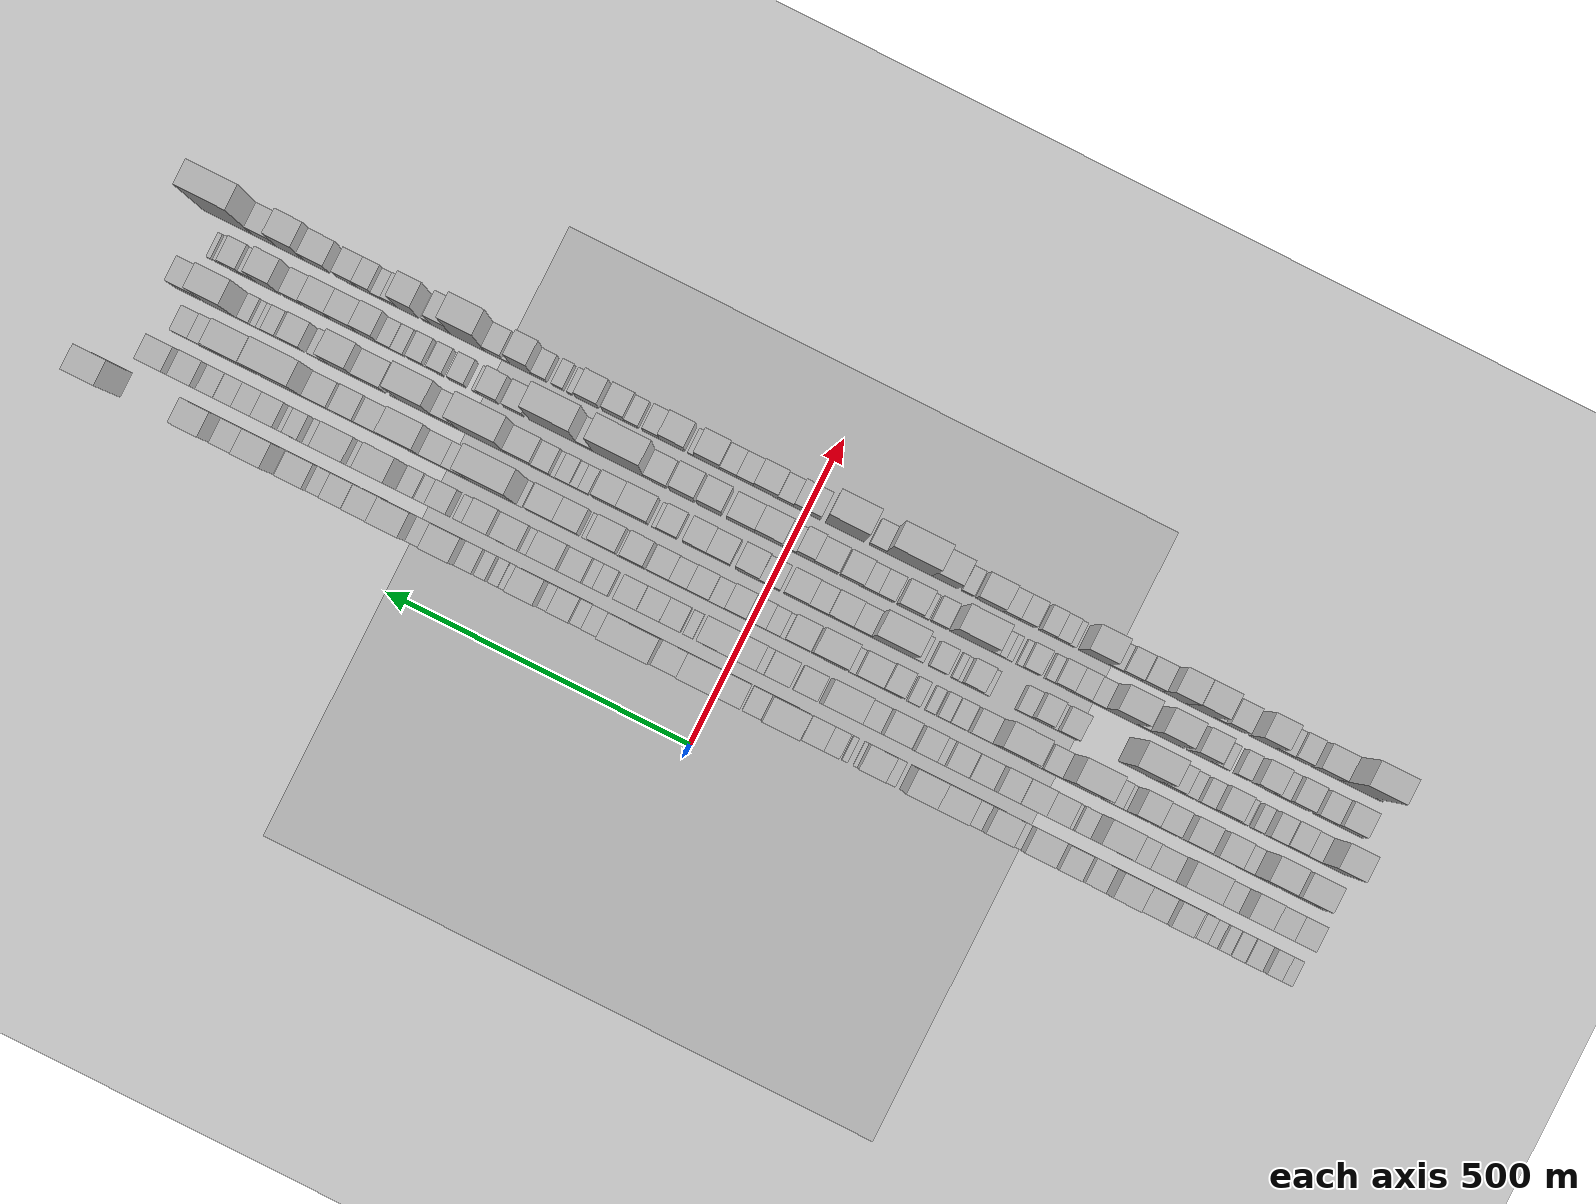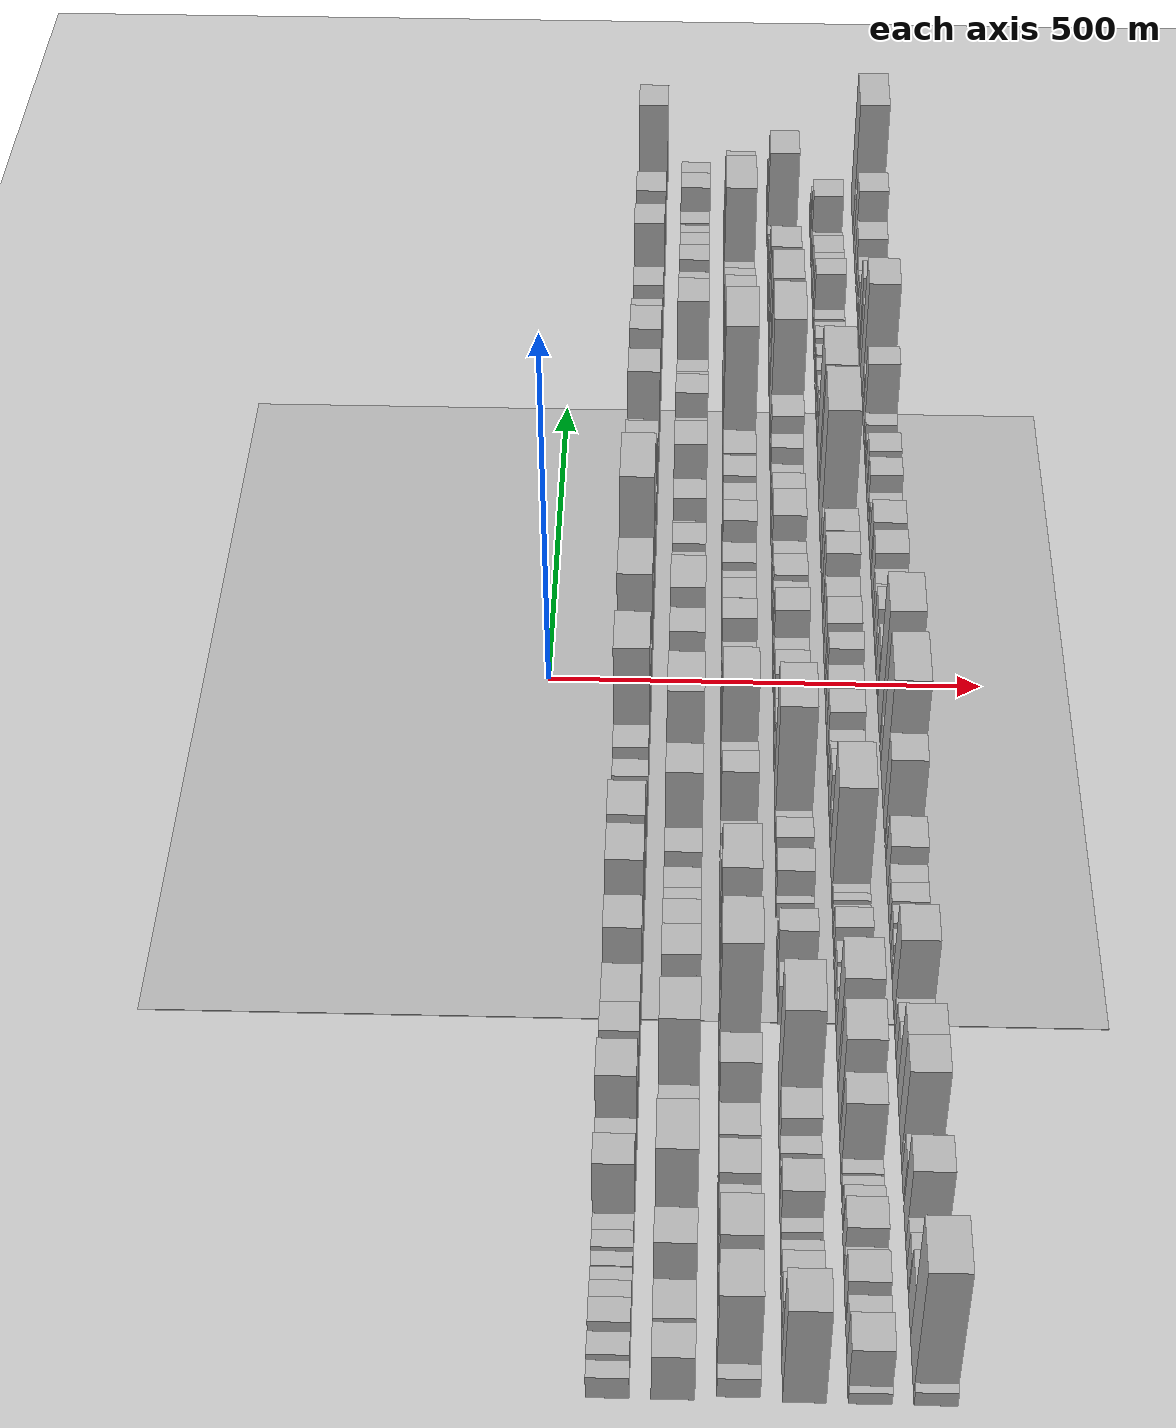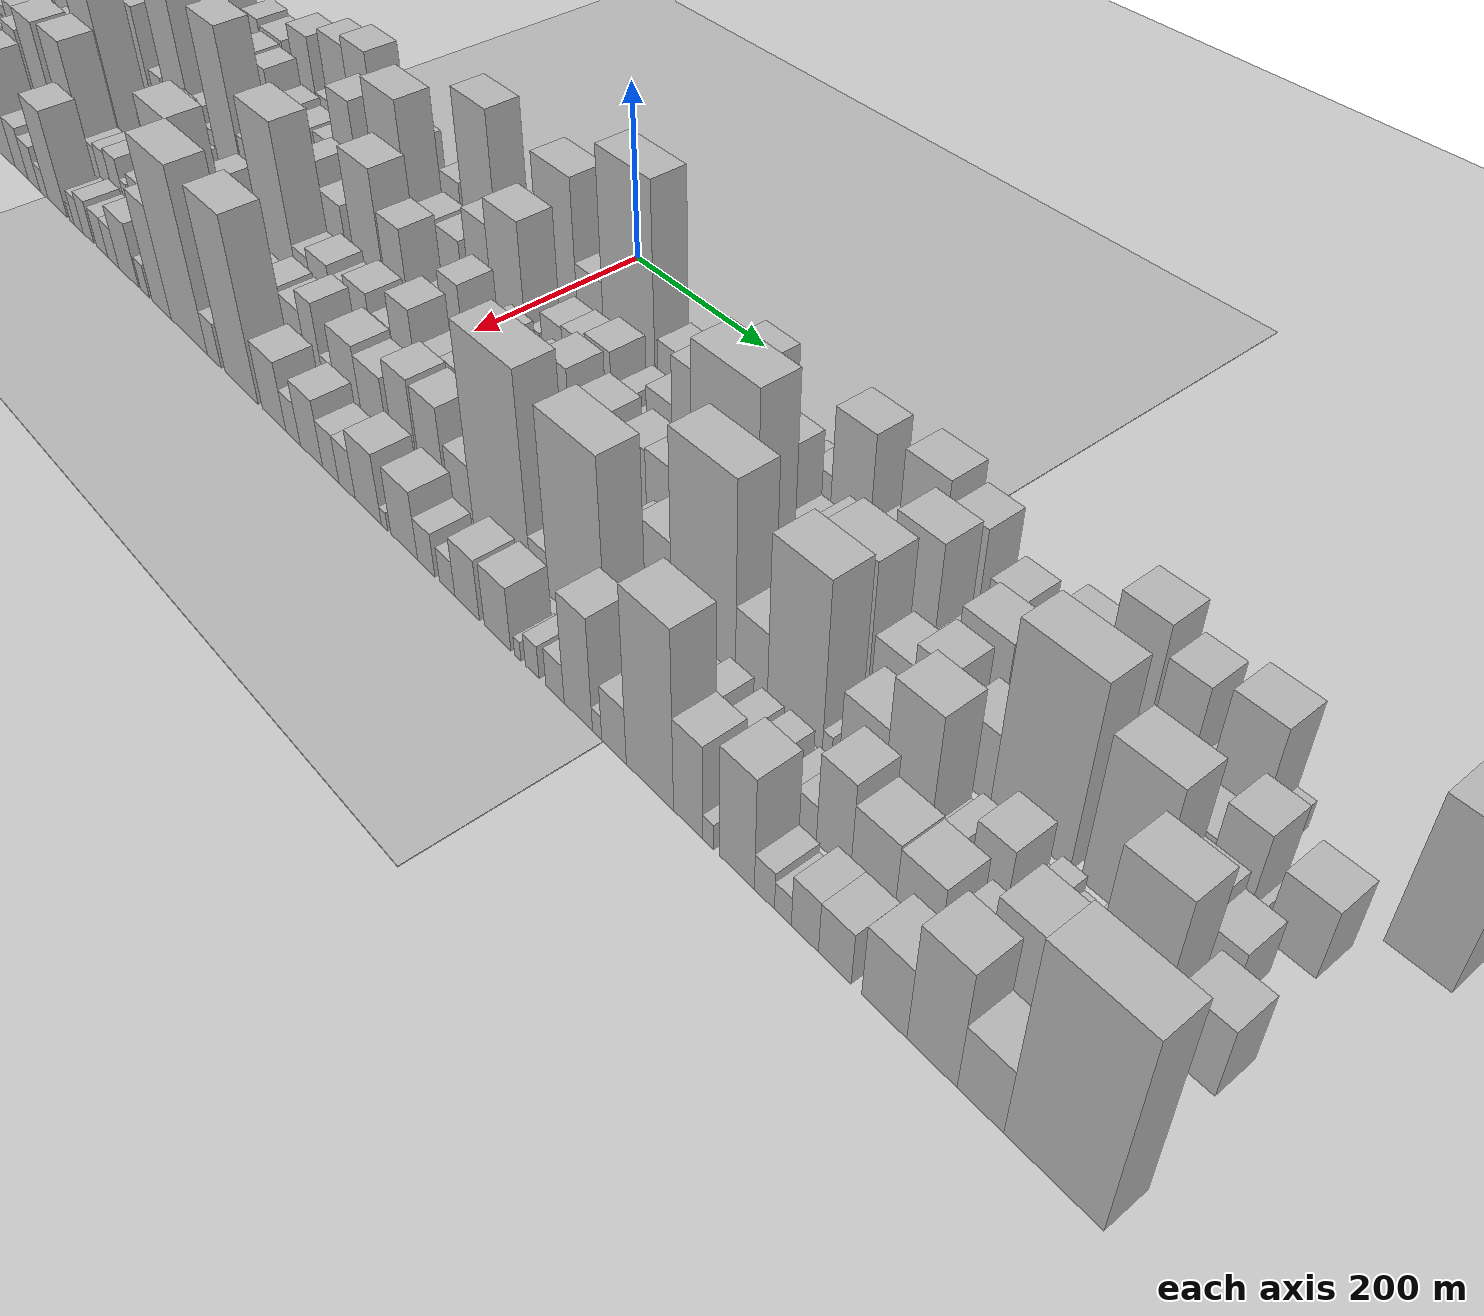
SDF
<?xml version="1.0" encoding="utf-8"?>

<sdf version="1.6">

   <world name="default">

      <gui fullscreen="0">

         <camera name="user_camera">

            <pose>-15 0 4.57585 0 0 0</pose>

            <view_controller>orbit</view_controller>

         </camera>

      </gui>

      <scene>

         <sky>

           <clouds>

             <speed>12</speed>

           </clouds>

         </sky>

         <ambient>0.4 0.4 0.4 1</ambient>

         <background>0.7 0.7 0.7 1</background>

         <shadows>1</shadows>

      </scene>

      <gravity>0 0 -9.8066</gravity>

      <magnetic_field>6e-06 2.3e-05 -4.2e-05</magnetic_field>

      <physics default="0" name="default_physics" type="ode">

         <ode>

            <solver>

               <type>quick</type>

               <iters>10</iters>

               <sor>1.0</sor>

               <use_dynamic_moi_rescaling>0</use_dynamic_moi_rescaling>

            </solver>

            <constraints>

               <cfm>0</cfm>

               <erp>0.2</erp>

               <contact_max_correcting_vel>100</contact_max_correcting_vel>

               <contact_surface_layer>0.001</contact_surface_layer>

            </constraints>

         </ode>

         <max_step_size>0.004</max_step_size>

         <real_time_factor>1</real_time_factor>

         <real_time_update_rate>250</real_time_update_rate>

      </physics>

      <light name="sun" type="directional">

         <cast_shadows>1</cast_shadows>

         <pose>0 0 10 0 0 0</pose>

         <diffuse>0.8 0.8 0.8 1</diffuse>

         <specular>0.2 0.2 0.2 1</specular>

         <attenuation>

            <range>1000</range>

            <constant>0.9</constant>

            <linear>0.01</linear>

            <quadratic>0.001</quadratic>

         </attenuation>

         <direction>-0.5 0.1 -0.9</direction>

      </light>

      <include>

         <name>ground_plane_1</name>

         <uri>model://HANNAS_ground_plane</uri>

         <pose>0 0 0  0 0 0</pose>

      </include>

      <include>

         <name>ground_plane_2</name>

         <uri>model://HANNAS_ground_plane</uri>

         <pose>100 0 0  0 0 0</pose>

      </include>

      <model name="building_1">

         <static>1</static>

         <pose frame="">100.0000 -930.6970 0 0.000000 0.000000 0.000000</pose>

         <link name="link">

            <pose frame="">0 0 16.50 0 0 0</pose>

            <collision name="collision">

               <geometry>

                  <box>

                     <size>40.0000 18.6060 33.0000</size>

                  </box>

               </geometry>

               <max_contacts>10</max_contacts>

               <surface>

                  <contact>

                     <ode/>

                  </contact>

                  <bounce/>

                  <friction>

                     <torsional>

                        <ode/>

                     </torsional>

                     <ode/>

                  </friction>

               </surface>

            </collision>

            <visual name="visual">

               <cast_shadows>0</cast_shadows>

               <geometry>

                  <box>

                     <size>40.0000 18.6060 33.0000</size>

                  </box>

               </geometry>

               <material>

                  <script>

                     <uri>model://HANNAS_wall/materials/scripts</uri>

                     <uri>model://HANNAS_wall/materials/textures</uri>

                     <name>vrc/HANNAS_wall</name>

                  </script>

               </material>

            </visual>

            <self_collide>0</self_collide>

            <enable_wind>0</enable_wind>

            <kinematic>0</kinematic>

         </link>

      </model>

      <model name="building_2">

         <static>1</static>

         <pose frame="">100.0000 -909.1230 0 0.000000 0.000000 0.000000</pose>

         <link name="link">

            <pose frame="">0 0 21.00 0 0 0</pose>

            <collision name="collision">

               <geometry>

                  <box>

                     <size>40.0000 24.5421 42.0000</size>

                  </box>

               </geometry>

               <max_contacts>10</max_contacts>

               <surface>

                  <contact>

                     <ode/>

                  </contact>

                  <bounce/>

                  <friction>

                     <torsional>

                        <ode/>

                     </torsional>

                     <ode/>

                  </friction>

               </surface>

            </collision>

            <visual name="visual">

               <cast_shadows>0</cast_shadows>

               <geometry>

                  <box>

                     <size>40.0000 24.5421 42.0000</size>

                  </box>

               </geometry>

               <material>

                  <script>

                     <uri>model://HANNAS_wall/materials/scripts</uri>

                     <uri>model://HANNAS_wall/materials/textures</uri>

                     <name>vrc/HANNAS_wall</name>

                  </script>

               </material>

            </visual>

            <self_collide>0</self_collide>

            <enable_wind>0</enable_wind>

            <kinematic>0</kinematic>

         </link>

      </model>

      <model name="building_3">

         <static>1</static>

         <pose frame="">100.0000 -875.3660 0 0.000000 0.000000 0.000000</pose>

         <link name="link">

            <pose frame="">0 0 22.50 0 0 0</pose>

            <collision name="collision">

               <geometry>

                  <box>

                     <size>40.0000 26.9718 45.0000</size>

                  </box>

               </geometry>

               <max_contacts>10</max_contacts>

               <surface>

                  <contact>

                     <ode/>

                  </contact>

                  <bounce/>

                  <friction>

                     <torsional>

                        <ode/>

                     </torsional>

                     <ode/>

                  </friction>

               </surface>

            </collision>

            <visual name="visual">

               <cast_shadows>0</cast_shadows>

               <geometry>

                  <box>

                     <size>40.0000 26.9718 45.0000</size>

                  </box>

               </geometry>

               <material>

                  <script>

                     <uri>model://HANNAS_wall/materials/scripts</uri>

                     <uri>model://HANNAS_wall/materials/textures</uri>

                     <name>vrc/HANNAS_wall</name>

                  </script>

               </material>

            </visual>

            <self_collide>0</self_collide>

            <enable_wind>0</enable_wind>

            <kinematic>0</kinematic>

         </link>

      </model>

      <model name="building_4">

         <static>1</static>

         <pose frame="">100.0000 -850.7518 0 0.000000 0.000000 0.000000</pose>

         <link name="link">

            <pose frame="">0 0 19.50 0 0 0</pose>

            <collision name="collision">

               <geometry>

                  <box>

                     <size>40.0000 22.2566 39.0000</size>

                  </box>

               </geometry>

               <max_contacts>10</max_contacts>

               <surface>

                  <contact>

                     <ode/>

                  </contact>

                  <bounce/>

                  <friction>

                     <torsional>

                        <ode/>

                     </torsional>

                     <ode/>

                  </friction>

               </surface>

            </collision>

            <visual name="visual">

               <cast_shadows>0</cast_shadows>

               <geometry>

                  <box>

                     <size>40.0000 22.2566 39.0000</size>

                  </box>

               </geometry>

               <material>

                  <script>

                     <uri>model://HANNAS_wall/materials/scripts</uri>

                     <uri>model://HANNAS_wall/materials/textures</uri>

                     <name>vrc/HANNAS_wall</name>

                  </script>

               </material>

            </visual>

            <self_collide>0</self_collide>

            <enable_wind>0</enable_wind>

            <kinematic>0</kinematic>

         </link>

      </model>

      <model name="building_5">

         <static>1</static>

         <pose frame="">100.0000 -830.4698 0 0.000000 0.000000 0.000000</pose>

         <link name="link">

            <pose frame="">0 0 16.50 0 0 0</pose>

            <collision name="collision">

               <geometry>

                  <box>

                     <size>40.0000 18.3075 33.0000</size>

                  </box>

               </geometry>

               <max_contacts>10</max_contacts>

               <surface>

                  <contact>

                     <ode/>

                  </contact>

                  <bounce/>

                  <friction>

                     <torsional>

                        <ode/>

                     </torsional>

                     <ode/>

                  </friction>

               </surface>

            </collision>

            <visual name="visual">

               <cast_shadows>0</cast_shadows>

               <geometry>

                  <box>

                     <size>40.0000 18.3075 33.0000</size>

                  </box>

               </geometry>

               <material>

                  <script>

                     <uri>model://HANNAS_wall/materials/scripts</uri>

                     <uri>model://HANNAS_wall/materials/textures</uri>

                     <name>vrc/HANNAS_wall</name>

                  </script>

               </material>

            </visual>

            <self_collide>0</self_collide>

            <enable_wind>0</enable_wind>

            <kinematic>0</kinematic>

         </link>

      </model>

      <model name="building_6">

         <static>1</static>

         <pose frame="">100.0000 -810.0191 0 0.000000 0.000000 0.000000</pose>

         <link name="link">

            <pose frame="">0 0 15.00 0 0 0</pose>

            <collision name="collision">

               <geometry>

                  <box>

                     <size>40.0000 16.5940 30.0000</size>

                  </box>

               </geometry>

               <max_contacts>10</max_contacts>

               <surface>

                  <contact>

                     <ode/>

                  </contact>

                  <bounce/>

                  <friction>

                     <torsional>

                        <ode/>

                     </torsional>

                     <ode/>

                  </friction>

               </surface>

            </collision>

            <visual name="visual">

               <cast_shadows>0</cast_shadows>

               <geometry>

                  <box>

                     <size>40.0000 16.5940 30.0000</size>

                  </box>

               </geometry>

               <material>

                  <script>

                     <uri>model://HANNAS_wall/materials/scripts</uri>

                     <uri>model://HANNAS_wall/materials/textures</uri>

                     <name>vrc/HANNAS_wall</name>

                  </script>

               </material>

            </visual>

            <self_collide>0</self_collide>

            <enable_wind>0</enable_wind>

            <kinematic>0</kinematic>

         </link>

      </model>

      <model name="building_7">

         <static>1</static>

         <pose frame="">100.0000 -791.8548 0 0.000000 0.000000 0.000000</pose>

         <link name="link">

            <pose frame="">0 0 18.00 0 0 0</pose>

            <collision name="collision">

               <geometry>

                  <box>

                     <size>40.0000 19.7345 36.0000</size>

                  </box>

               </geometry>

               <max_contacts>10</max_contacts>

               <surface>

                  <contact>

                     <ode/>

                  </contact>

                  <bounce/>

                  <friction>

                     <torsional>

                        <ode/>

                     </torsional>

                     <ode/>

                  </friction>

               </surface>

            </collision>

            <visual name="visual">

               <cast_shadows>0</cast_shadows>

               <geometry>

                  <box>

                     <size>40.0000 19.7345 36.0000</size>

                  </box>

               </geometry>

               <material>

                  <script>

                     <uri>model://HANNAS_wall/materials/scripts</uri>

                     <uri>model://HANNAS_wall/materials/textures</uri>

                     <name>vrc/HANNAS_wall</name>

                  </script>

               </material>

            </visual>

            <self_collide>0</self_collide>

            <enable_wind>0</enable_wind>

            <kinematic>0</kinematic>

         </link>

      </model>

      <model name="building_8">

         <static>1</static>

         <pose frame="">100.0000 -772.8370 0 0.000000 0.000000 0.000000</pose>

         <link name="link">

            <pose frame="">0 0 18.00 0 0 0</pose>

            <collision name="collision">

               <geometry>

                  <box>

                     <size>40.0000 18.3012 36.0000</size>

                  </box>

               </geometry>

               <max_contacts>10</max_contacts>

               <surface>

                  <contact>

                     <ode/>

                  </contact>

                  <bounce/>

                  <friction>

                     <torsional>

                        <ode/>

                     </torsional>

                     <ode/>

                  </friction>

               </surface>

            </collision>

            <visual name="visual">

               <cast_shadows>0</cast_shadows>

               <geometry>

                  <box>

                     <size>40.0000 18.3012 36.0000</size>

                  </box>

               </geometry>

               <material>

                  <script>

                     <uri>model://HANNAS_wall/materials/scripts</uri>

                     <uri>model://HANNAS_wall/materials/textures</uri>

                     <name>vrc/HANNAS_wall</name>

                  </script>

               </material>

            </visual>

            <self_collide>0</self_collide>

            <enable_wind>0</enable_wind>

            <kinematic>0</kinematic>

         </link>

      </model>

      <model name="building_9">

         <static>1</static>

         <pose frame="">100.0000 -745.8943 0 0.000000 0.000000 0.000000</pose>

         <link name="link">

            <pose frame="">0 0 57.00 0 0 0</pose>

            <collision name="collision">

               <geometry>

                  <box>

                     <size>40.0000 35.5841 114.0000</size>

                  </box>

               </geometry>

               <max_contacts>10</max_contacts>

               <surface>

                  <contact>

                     <ode/>

                  </contact>

                  <bounce/>

                  <friction>

                     <torsional>

                        <ode/>

                     </torsional>

                     <ode/>

                  </friction>

               </surface>

            </collision>

            <visual name="visual">

               <cast_shadows>0</cast_shadows>

               <geometry>

                  <box>

                     <size>40.0000 35.5841 114.0000</size>

                  </box>

               </geometry>

               <material>

                  <script>

                     <uri>model://HANNAS_wall/materials/scripts</uri>

                     <uri>model://HANNAS_wall/materials/textures</uri>

                     <name>vrc/HANNAS_wall</name>

                  </script>

               </material>

            </visual>

            <self_collide>0</self_collide>

            <enable_wind>0</enable_wind>

            <kinematic>0</kinematic>

         </link>

      </model>

      <model name="building_10">

         <static>1</static>

         <pose frame="">100.0000 -705.6278 0 0.000000 0.000000 0.000000</pose>

         <link name="link">

            <pose frame="">0 0 39.00 0 0 0</pose>

            <collision name="collision">

               <geometry>

                  <box>

                     <size>40.0000 44.9490 78.0000</size>

                  </box>

               </geometry>

               <max_contacts>10</max_contacts>

               <surface>

                  <contact>

                     <ode/>

                  </contact>

                  <bounce/>

                  <friction>

                     <torsional>

                        <ode/>

                     </torsional>

                     <ode/>

                  </friction>

               </surface>

            </collision>

            <visual name="visual">

               <cast_shadows>0</cast_shadows>

               <geometry>

                  <box>

                     <size>40.0000 44.9490 78.0000</size>

                  </box>

               </geometry>

               <material>

                  <script>

                     <uri>model://HANNAS_wall/materials/scripts</uri>

                     <uri>model://HANNAS_wall/materials/textures</uri>

                     <name>vrc/HANNAS_wall</name>

                  </script>

               </material>

            </visual>

            <self_collide>0</self_collide>

            <enable_wind>0</enable_wind>

            <kinematic>0</kinematic>

         </link>

      </model>

      <model name="building_11">

         <static>1</static>

         <pose frame="">100.0000 -654.5918 0 0.000000 0.000000 0.000000</pose>

         <link name="link">

            <pose frame="">0 0 67.50 0 0 0</pose>

            <collision name="collision">

               <geometry>

                  <box>

                     <size>40.0000 45.1232 135.0000</size>

                  </box>

               </geometry>

               <max_contacts>10</max_contacts>

               <surface>

                  <contact>

                     <ode/>

                  </contact>

                  <bounce/>

                  <friction>

                     <torsional>

                        <ode/>

                     </torsional>

                     <ode/>

                  </friction>

               </surface>

            </collision>

            <visual name="visual">

               <cast_shadows>0</cast_shadows>

               <geometry>

                  <box>

                     <size>40.0000 45.1232 135.0000</size>

                  </box>

               </geometry>

               <material>

                  <script>

                     <uri>model://HANNAS_wall/materials/scripts</uri>

                     <uri>model://HANNAS_wall/materials/textures</uri>

                     <name>vrc/HANNAS_wall</name>

                  </script>

               </material>

            </visual>

            <self_collide>0</self_collide>

            <enable_wind>0</enable_wind>

            <kinematic>0</kinematic>

         </link>

      </model>

      <model name="building_12">

         <static>1</static>

         <pose frame="">100.0000 -615.2413 0 0.000000 0.000000 0.000000</pose>

         <link name="link">

            <pose frame="">0 0 31.50 0 0 0</pose>

            <collision name="collision">

               <geometry>

                  <box>

                     <size>40.0000 33.5777 63.0000</size>

                  </box>

               </geometry>

               <max_contacts>10</max_contacts>

               <surface>

                  <contact>

                     <ode/>

                  </contact>

                  <bounce/>

                  <friction>

                     <torsional>

                        <ode/>

                     </torsional>

                     <ode/>

                  </friction>

               </surface>

            </collision>

            <visual name="visual">

               <cast_shadows>0</cast_shadows>

               <geometry>

                  <box>

                     <size>40.0000 33.5777 63.0000</size>

                  </box>

               </geometry>

               <material>

                  <script>

                     <uri>model://HANNAS_wall/materials/scripts</uri>

                     <uri>model://HANNAS_wall/materials/textures</uri>

                     <name>vrc/HANNAS_wall</name>

                  </script>

               </material>

            </visual>

            <self_collide>0</self_collide>

            <enable_wind>0</enable_wind>

            <kinematic>0</kinematic>

         </link>

      </model>

      <model name="building_13">

         <static>1</static>

         <pose frame="">100.0000 -570.8924 0 0.000000 0.000000 0.000000</pose>

         <link name="link">

            <pose frame="">0 0 46.50 0 0 0</pose>

            <collision name="collision">

               <geometry>

                  <box>

                     <size>40.0000 37.1200 93.0000</size>

                  </box>

               </geometry>

               <max_contacts>10</max_contacts>

               <surface>

                  <contact>

                     <ode/>

                  </contact>

                  <bounce/>

                  <friction>

                     <torsional>

                        <ode/>

                     </torsional>

                     <ode/>

                  </friction>

               </surface>

            </collision>

            <visual name="visual">

               <cast_shadows>0</cast_shadows>

               <geometry>

                  <box>

                     <size>40.0000 37.1200 93.0000</size>

                  </box>

               </geometry>

               <material>

                  <script>

                     <uri>model://HANNAS_wall/materials/scripts</uri>

                     <uri>model://HANNAS_wall/materials/textures</uri>

                     <name>vrc/HANNAS_wall</name>

                  </script>

               </material>

            </visual>

            <self_collide>0</self_collide>

            <enable_wind>0</enable_wind>

            <kinematic>0</kinematic>

         </link>

      </model>

      <model name="building_14">

         <static>1</static>

         <pose frame="">100.0000 -523.1543 0 0.000000 0.000000 0.000000</pose>

         <link name="link">

            <pose frame="">0 0 43.50 0 0 0</pose>

            <collision name="collision">

               <geometry>

                  <box>

                     <size>40.0000 50.3562 87.0000</size>

                  </box>

               </geometry>

               <max_contacts>10</max_contacts>

               <surface>

                  <contact>

                     <ode/>

                  </contact>

                  <bounce/>

                  <friction>

                     <torsional>

                        <ode/>

                     </torsional>

                     <ode/>

                  </friction>

               </surface>

            </collision>

            <visual name="visual">

               <cast_shadows>0</cast_shadows>

               <geometry>

                  <box>

                     <size>40.0000 50.3562 87.0000</size>

                  </box>

               </geometry>

               <material>

                  <script>

                     <uri>model://HANNAS_wall/materials/scripts</uri>

                     <uri>model://HANNAS_wall/materials/textures</uri>

                     <name>vrc/HANNAS_wall</name>

                  </script>

               </material>

            </visual>

            <self_collide>0</self_collide>

            <enable_wind>0</enable_wind>

            <kinematic>0</kinematic>

         </link>

      </model>

      <model name="building_15">

         <static>1</static>

         <pose frame="">100.0000 -487.5639 0 0.000000 0.000000 0.000000</pose>

         <link name="link">

            <pose frame="">0 0 18.00 0 0 0</pose>

            <collision name="collision">

               <geometry>

                  <box>

                     <size>40.0000 20.8247 36.0000</size>

                  </box>

               </geometry>

               <max_contacts>10</max_contacts>

               <surface>

                  <contact>

                     <ode/>

                  </contact>

                  <bounce/>

                  <friction>

                     <torsional>

                        <ode/>

                     </torsional>

                     <ode/>

                  </friction>

               </surface>

            </collision>

            <visual name="visual">

               <cast_shadows>0</cast_shadows>

               <geometry>

                  <box>

                     <size>40.0000 20.8247 36.0000</size>

                  </box>

               </geometry>

               <material>

                  <script>

                     <uri>model://HANNAS_wall/materials/scripts</uri>

                     <uri>model://HANNAS_wall/materials/textures</uri>

                     <name>vrc/HANNAS_wall</name>

                  </script>

               </material>

            </visual>

            <self_collide>0</self_collide>

            <enable_wind>0</enable_wind>

            <kinematic>0</kinematic>

         </link>

      </model>

      <model name="building_16">

         <static>1</static>

         <pose frame="">100.0000 -454.9378 0 0.000000 0.000000 0.000000</pose>

         <link name="link">

            <pose frame="">0 0 58.50 0 0 0</pose>

            <collision name="collision">

               <geometry>

                  <box>

                     <size>40.0000 44.4276 117.0000</size>

                  </box>

               </geometry>

               <max_contacts>10</max_contacts>

               <surface>

                  <contact>

                     <ode/>

                  </contact>

                  <bounce/>

                  <friction>

                     <torsional>

                        <ode/>

                     </torsional>

                     <ode/>

                  </friction>

               </surface>

            </collision>

            <visual name="visual">

               <cast_shadows>0</cast_shadows>

               <geometry>

                  <box>

                     <size>40.0000 44.4276 117.0000</size>

                  </box>

               </geometry>

               <material>

                  <script>

                     <uri>model://HANNAS_wall/materials/scripts</uri>

                     <uri>model://HANNAS_wall/materials/textures</uri>

                     <name>vrc/HANNAS_wall</name>

                  </script>

               </material>

            </visual>

            <self_collide>0</self_collide>

            <enable_wind>0</enable_wind>

            <kinematic>0</kinematic>

         </link>

      </model>

      <model name="building_17">

         <static>1</static>

         <pose frame="">100.0000 -418.4391 0 0.000000 0.000000 0.000000</pose>

         <link name="link">

            <pose frame="">0 0 25.50 0 0 0</pose>

            <collision name="collision">

               <geometry>

                  <box>

                     <size>40.0000 28.5699 51.0000</size>

                  </box>

               </geometry>

               <max_contacts>10</max_contacts>

               <surface>

                  <contact>

                     <ode/>

                  </contact>

                  <bounce/>

                  <friction>

                     <torsional>

                        <ode/>

                     </torsional>

                     <ode/>

                  </friction>

               </surface>

            </collision>

            <visual name="visual">

               <cast_shadows>0</cast_shadows>

               <geometry>

                  <box>

                     <size>40.0000 28.5699 51.0000</size>

                  </box>

               </geometry>

               <material>

                  <script>

                     <uri>model://HANNAS_wall/materials/scripts</uri>

                     <uri>model://HANNAS_wall/materials/textures</uri>

                     <name>vrc/HANNAS_wall</name>

                  </script>

               </material>

            </visual>

            <self_collide>0</self_collide>

            <enable_wind>0</enable_wind>

            <kinematic>0</kinematic>

         </link>

      </model>

      <model name="building_18">

         <static>1</static>

         <pose frame="">100.0000 -378.4617 0 0.000000 0.000000 0.000000</pose>

         <link name="link">

            <pose frame="">0 0 69.00 0 0 0</pose>

            <collision name="collision">

               <geometry>

                  <box>

                     <size>40.0000 51.3850 138.0000</size>

                  </box>

               </geometry>

               <max_contacts>10</max_contacts>

               <surface>

                  <contact>

                     <ode/>

                  </contact>

                  <bounce/>

                  <friction>

                     <torsional>

                        <ode/>

                     </torsional>

                     <ode/>

                  </friction>

               </surface>

            </collision>

            <visual name="visual">

               <cast_shadows>0</cast_shadows>

               <geometry>

                  <box>

                     <size>40.0000 51.3850 138.0000</size>

                  </box>

               </geometry>

               <material>

                  <script>

                     <uri>model://HANNAS_wall/materials/scripts</uri>

                     <uri>model://HANNAS_wall/materials/textures</uri>

                     <name>vrc/HANNAS_wall</name>

                  </script>

               </material>

            </visual>

            <self_collide>0</self_collide>

            <enable_wind>0</enable_wind>

            <kinematic>0</kinematic>

         </link>

      </model>

      <model name="building_19">

         <static>1</static>

         <pose frame="">100.0000 -328.0284 0 0.000000 0.000000 0.000000</pose>

         <link name="link">

            <pose frame="">0 0 75.00 0 0 0</pose>

            <collision name="collision">

               <geometry>

                  <box>

                     <size>40.0000 49.4816 150.0000</size>

                  </box>

               </geometry>

               <max_contacts>10</max_contacts>

               <surface>

                  <contact>

                     <ode/>

                  </contact>

                  <bounce/>

                  <friction>

                     <torsional>

                        <ode/>

                     </torsional>

                     <ode/>

                  </friction>

               </surface>

            </collision>

            <visual name="visual">

               <cast_shadows>0</cast_shadows>

               <geometry>

                  <box>

                     <size>40.0000 49.4816 150.0000</size>

                  </box>

               </geometry>

               <material>

                  <script>

                     <uri>model://HANNAS_wall/materials/scripts</uri>

                     <uri>model://HANNAS_wall/materials/textures</uri>

                     <name>vrc/HANNAS_wall</name>

                  </script>

               </material>

            </visual>

            <self_collide>0</self_collide>

            <enable_wind>0</enable_wind>

            <kinematic>0</kinematic>

         </link>

      </model>

      <model name="building_20">

         <static>1</static>

         <pose frame="">100.0000 -285.3408 0 0.000000 0.000000 0.000000</pose>

         <link name="link">

            <pose frame="">0 0 15.00 0 0 0</pose>

            <collision name="collision">

               <geometry>

                  <box>

                     <size>40.0000 17.8934 30.0000</size>

                  </box>

               </geometry>

               <max_contacts>10</max_contacts>

               <surface>

                  <contact>

                     <ode/>

                  </contact>

                  <bounce/>

                  <friction>

                     <torsional>

                        <ode/>

                     </torsional>

                     <ode/>

                  </friction>

               </surface>

            </collision>

            <visual name="visual">

               <cast_shadows>0</cast_shadows>

               <geometry>

                  <box>

                     <size>40.0000 17.8934 30.0000</size>

                  </box>

               </geometry>

               <material>

                  <script>

                     <uri>model://HANNAS_wall/materials/scripts</uri>

                     <uri>model://HANNAS_wall/materials/textures</uri>

                     <name>vrc/HANNAS_wall</name>

                  </script>

               </material>

            </visual>

            <self_collide>0</self_collide>

            <enable_wind>0</enable_wind>

            <kinematic>0</kinematic>

         </link>

      </model>

      <model name="building_21">

         <static>1</static>

         <pose frame="">100.0000 -254.5551 0 0.000000 0.000000 0.000000</pose>

         <link name="link">

            <pose frame="">0 0 37.50 0 0 0</pose>

            <collision name="collision">

               <geometry>

                  <box>

                     <size>40.0000 43.6780 75.0000</size>

                  </box>

               </geometry>

               <max_contacts>10</max_contacts>

               <surface>

                  <contact>

                     <ode/>

                  </contact>

                  <bounce/>

                  <friction>

                     <torsional>

                        <ode/>

                     </torsional>

                     <ode/>

                  </friction>

               </surface>

            </collision>

            <visual name="visual">

               <cast_shadows>0</cast_shadows>

               <geometry>

                  <box>

                     <size>40.0000 43.6780 75.0000</size>

                  </box>

               </geometry>

               <material>

                  <script>

                     <uri>model://HANNAS_wall/materials/scripts</uri>

                     <uri>model://HANNAS_wall/materials/textures</uri>

                     <name>vrc/HANNAS_wall</name>

                  </script>

               </material>

            </visual>

            <self_collide>0</self_collide>

            <enable_wind>0</enable_wind>

            <kinematic>0</kinematic>

         </link>

      </model>

      <model name="building_22">

         <static>1</static>

         <pose frame="">100.0000 -229.6070 0 0.000000 0.000000 0.000000</pose>

         <link name="link">

            <pose frame="">0 0 7.50 0 0 0</pose>

            <collision name="collision">

               <geometry>

                  <box>

                     <size>40.0000 6.2183 15.0000</size>

                  </box>

               </geometry>

               <max_contacts>10</max_contacts>

               <surface>

                  <contact>

                     <ode/>

                  </contact>

                  <bounce/>

                  <friction>

                     <torsional>

                        <ode/>

                     </torsional>

                     <ode/>

                  </friction>

               </surface>

            </collision>

            <visual name="visual">

               <cast_shadows>0</cast_shadows>

               <geometry>

                  <box>

                     <size>40.0000 6.2183 15.0000</size>

                  </box>

               </geometry>

               <material>

                  <script>

                     <uri>model://HANNAS_wall/materials/scripts</uri>

                     <uri>model://HANNAS_wall/materials/textures</uri>

                     <name>vrc/HANNAS_wall</name>

                  </script>

               </material>

            </visual>

            <self_collide>0</self_collide>

            <enable_wind>0</enable_wind>

            <kinematic>0</kinematic>

         </link>

      </model>

      <model name="building_23">

         <static>1</static>

         <pose frame="">100.0000 -211.9907 0 0.000000 0.000000 0.000000</pose>

         <link name="link">

            <pose frame="">0 0 10.50 0 0 0</pose>

            <collision name="collision">

               <geometry>

                  <box>

                     <size>40.0000 9.0143 21.0000</size>

                  </box>

               </geometry>

               <max_contacts>10</max_contacts>

               <surface>

                  <contact>

                     <ode/>

                  </contact>

                  <bounce/>

                  <friction>

                     <torsional>

                        <ode/>

                     </torsional>

                     <ode/>

                  </friction>

               </surface>

            </collision>

            <visual name="visual">

               <cast_shadows>0</cast_shadows>

               <geometry>

                  <box>

                     <size>40.0000 9.0143 21.0000</size>

                  </box>

               </geometry>

               <material>

                  <script>

                     <uri>model://HANNAS_wall/materials/scripts</uri>

                     <uri>model://HANNAS_wall/materials/textures</uri>

                     <name>vrc/HANNAS_wall</name>

                  </script>

               </material>

            </visual>

            <self_collide>0</self_collide>

            <enable_wind>0</enable_wind>

            <kinematic>0</kinematic>

         </link>

      </model>

      <model name="building_24">

         <static>1</static>

         <pose frame="">100.0000 -189.1800 0 0.000000 0.000000 0.000000</pose>

         <link name="link">

            <pose frame="">0 0 25.50 0 0 0</pose>

            <collision name="collision">

               <geometry>

                  <box>

                     <size>40.0000 26.6072 51.0000</size>

                  </box>

               </geometry>

               <max_contacts>10</max_contacts>

               <surface>

                  <contact>

                     <ode/>

                  </contact>

                  <bounce/>

                  <friction>

                     <torsional>

                        <ode/>

                     </torsional>

                     <ode/>

                  </friction>

               </surface>

            </collision>

            <visual name="visual">

               <cast_shadows>0</cast_shadows>

               <geometry>

                  <box>

                     <size>40.0000 26.6072 51.0000</size>

                  </box>

               </geometry>

               <material>

                  <script>

                     <uri>model://HANNAS_wall/materials/scripts</uri>

                     <uri>model://HANNAS_wall/materials/textures</uri>

                     <name>vrc/HANNAS_wall</name>

                  </script>

               </material>

            </visual>

            <self_collide>0</self_collide>

            <enable_wind>0</enable_wind>

            <kinematic>0</kinematic>

         </link>

      </model>

      <model name="building_25">

         <static>1</static>

         <pose frame="">100.0000 -158.0435 0 0.000000 0.000000 0.000000</pose>

         <link name="link">

            <pose frame="">0 0 34.50 0 0 0</pose>

            <collision name="collision">

               <geometry>

                  <box>

                     <size>40.0000 35.6658 69.0000</size>

                  </box>

               </geometry>

               <max_contacts>10</max_contacts>

               <surface>

                  <contact>

                     <ode/>

                  </contact>

                  <bounce/>

                  <friction>

                     <torsional>

                        <ode/>

                     </torsional>

                     <ode/>

                  </friction>

               </surface>

            </collision>

            <visual name="visual">

               <cast_shadows>0</cast_shadows>

               <geometry>

                  <box>

                     <size>40.0000 35.6658 69.0000</size>

                  </box>

               </geometry>

               <material>

                  <script>

                     <uri>model://HANNAS_wall/materials/scripts</uri>

                     <uri>model://HANNAS_wall/materials/textures</uri>

                     <name>vrc/HANNAS_wall</name>

                  </script>

               </material>

            </visual>

            <self_collide>0</self_collide>

            <enable_wind>0</enable_wind>

            <kinematic>0</kinematic>

         </link>

      </model>

      <model name="building_26">

         <static>1</static>

         <pose frame="">100.0000 -105.2932 0 0.000000 0.000000 0.000000</pose>

         <link name="link">

            <pose frame="">0 0 90.00 0 0 0</pose>

            <collision name="collision">

               <geometry>

                  <box>

                     <size>40.0000 59.8347 180.0000</size>

                  </box>

               </geometry>

               <max_contacts>10</max_contacts>

               <surface>

                  <contact>

                     <ode/>

                  </contact>

                  <bounce/>

                  <friction>

                     <torsional>

                        <ode/>

                     </torsional>

                     <ode/>

                  </friction>

               </surface>

            </collision>

            <visual name="visual">

               <cast_shadows>0</cast_shadows>

               <geometry>

                  <box>

                     <size>40.0000 59.8347 180.0000</size>

                  </box>

               </geometry>

               <material>

                  <script>

                     <uri>model://HANNAS_wall/materials/scripts</uri>

                     <uri>model://HANNAS_wall/materials/textures</uri>

                     <name>vrc/HANNAS_wall</name>

                  </script>

               </material>

            </visual>

            <self_collide>0</self_collide>

            <enable_wind>0</enable_wind>

            <kinematic>0</kinematic>

         </link>

      </model>

      <model name="building_27">

         <static>1</static>

         <pose frame="">100.0000 -60.1227 0 0.000000 0.000000 0.000000</pose>

         <link name="link">

            <pose frame="">0 0 25.50 0 0 0</pose>

            <collision name="collision">

               <geometry>

                  <box>

                     <size>40.0000 30.5063 51.0000</size>

                  </box>

               </geometry>

               <max_contacts>10</max_contacts>

               <surface>

                  <contact>

                     <ode/>

                  </contact>

                  <bounce/>

                  <friction>

                     <torsional>

                        <ode/>

                     </torsional>

                     <ode/>

                  </friction>

               </surface>

            </collision>

            <visual name="visual">

               <cast_shadows>0</cast_shadows>

               <geometry>

                  <box>

                     <size>40.0000 30.5063 51.0000</size>

                  </box>

               </geometry>

               <material>

                  <script>

                     <uri>model://HANNAS_wall/materials/scripts</uri>

                     <uri>model://HANNAS_wall/materials/textures</uri>

                     <name>vrc/HANNAS_wall</name>

                  </script>

               </material>

            </visual>

            <self_collide>0</self_collide>

            <enable_wind>0</enable_wind>

            <kinematic>0</kinematic>

         </link>

      </model>

      <model name="building_28">

         <static>1</static>

         <pose frame="">100.0000 -21.3664 0 0.000000 0.000000 0.000000</pose>

         <link name="link">

            <pose frame="">0 0 33.00 0 0 0</pose>

            <collision name="collision">

               <geometry>

                  <box>

                     <size>40.0000 39.0064 66.0000</size>

                  </box>

               </geometry>

               <max_contacts>10</max_contacts>

               <surface>

                  <contact>

                     <ode/>

                  </contact>

                  <bounce/>

                  <friction>

                     <torsional>

                        <ode/>

                     </torsional>

                     <ode/>

                  </friction>

               </surface>

            </collision>

            <visual name="visual">

               <cast_shadows>0</cast_shadows>

               <geometry>

                  <box>

                     <size>40.0000 39.0064 66.0000</size>

                  </box>

               </geometry>

               <material>

                  <script>

                     <uri>model://HANNAS_wall/materials/scripts</uri>

                     <uri>model://HANNAS_wall/materials/textures</uri>

                     <name>vrc/HANNAS_wall</name>

                  </script>

               </material>

            </visual>

            <self_collide>0</self_collide>

            <enable_wind>0</enable_wind>

            <kinematic>0</kinematic>

         </link>

      </model>

      <model name="building_29">

         <static>1</static>

         <pose frame="">100.0000 29.2411 0 0.000000 0.000000 0.000000</pose>

         <link name="link">

            <pose frame="">0 0 84.00 0 0 0</pose>

            <collision name="collision">

               <geometry>

                  <box>

                     <size>40.0000 62.2086 168.0000</size>

                  </box>

               </geometry>

               <max_contacts>10</max_contacts>

               <surface>

                  <contact>

                     <ode/>

                  </contact>

                  <bounce/>

                  <friction>

                     <torsional>

                        <ode/>

                     </torsional>

                     <ode/>

                  </friction>

               </surface>

            </collision>

            <visual name="visual">

               <cast_shadows>0</cast_shadows>

               <geometry>

                  <box>

                     <size>40.0000 62.2086 168.0000</size>

                  </box>

               </geometry>

               <material>

                  <script>

                     <uri>model://HANNAS_wall/materials/scripts</uri>

                     <uri>model://HANNAS_wall/materials/textures</uri>

                     <name>vrc/HANNAS_wall</name>

                  </script>

               </material>

            </visual>

            <self_collide>0</self_collide>

            <enable_wind>0</enable_wind>

            <kinematic>0</kinematic>

         </link>

      </model>

      <model name="building_30">

         <static>1</static>

         <pose frame="">100.0000 81.5570 0 0.000000 0.000000 0.000000</pose>

         <link name="link">

            <pose frame="">0 0 37.50 0 0 0</pose>

            <collision name="collision">

               <geometry>

                  <box>

                     <size>40.0000 42.4233 75.0000</size>

                  </box>

               </geometry>

               <max_contacts>10</max_contacts>

               <surface>

                  <contact>

                     <ode/>

                  </contact>

                  <bounce/>

                  <friction>

                     <torsional>

                        <ode/>

                     </torsional>

                     <ode/>

                  </friction>

               </surface>

            </collision>

            <visual name="visual">

               <cast_shadows>0</cast_shadows>

               <geometry>

                  <box>

                     <size>40.0000 42.4233 75.0000</size>

                  </box>

               </geometry>

               <material>

                  <script>

                     <uri>model://HANNAS_wall/materials/scripts</uri>

                     <uri>model://HANNAS_wall/materials/textures</uri>

                     <name>vrc/HANNAS_wall</name>

                  </script>

               </material>

            </visual>

            <self_collide>0</self_collide>

            <enable_wind>0</enable_wind>

            <kinematic>0</kinematic>

         </link>

      </model>

      <model name="building_31">

         <static>1</static>

         <pose frame="">100.0000 142.4309 0 0.000000 0.000000 0.000000</pose>

         <link name="link">

            <pose frame="">0 0 111.00 0 0 0</pose>

            <collision name="collision">

               <geometry>

                  <box>

                     <size>40.0000 79.3245 222.0000</size>

                  </box>

               </geometry>

               <max_contacts>10</max_contacts>

               <surface>

                  <contact>

                     <ode/>

                  </contact>

                  <bounce/>

                  <friction>

                     <torsional>

                        <ode/>

                     </torsional>

                     <ode/>

                  </friction>

               </surface>

            </collision>

            <visual name="visual">

               <cast_shadows>0</cast_shadows>

               <geometry>

                  <box>

                     <size>40.0000 79.3245 222.0000</size>

                  </box>

               </geometry>

               <material>

                  <script>

                     <uri>model://HANNAS_wall/materials/scripts</uri>

                     <uri>model://HANNAS_wall/materials/textures</uri>

                     <name>vrc/HANNAS_wall</name>

                  </script>

               </material>

            </visual>

            <self_collide>0</self_collide>

            <enable_wind>0</enable_wind>

            <kinematic>0</kinematic>

         </link>

      </model>

      <model name="building_32">

         <static>1</static>

         <pose frame="">100.0000 201.3452 0 0.000000 0.000000 0.000000</pose>

         <link name="link">

            <pose frame="">0 0 28.50 0 0 0</pose>

            <collision name="collision">

               <geometry>

                  <box>

                     <size>40.0000 30.5040 57.0000</size>

                  </box>

               </geometry>

               <max_contacts>10</max_contacts>

               <surface>

                  <contact>

                     <ode/>

                  </contact>

                  <bounce/>

                  <friction>

                     <torsional>

                        <ode/>

                     </torsional>

                     <ode/>

                  </friction>

               </surface>

            </collision>

            <visual name="visual">

               <cast_shadows>0</cast_shadows>

               <geometry>

                  <box>

                     <size>40.0000 30.5040 57.0000</size>

                  </box>

               </geometry>

               <material>

                  <script>

                     <uri>model://HANNAS_wall/materials/scripts</uri>

                     <uri>model://HANNAS_wall/materials/textures</uri>

                     <name>vrc/HANNAS_wall</name>

                  </script>

               </material>

            </visual>

            <self_collide>0</self_collide>

            <enable_wind>0</enable_wind>

            <kinematic>0</kinematic>

         </link>

      </model>

      <model name="building_33">

         <static>1</static>

         <pose frame="">100.0000 226.5743 0 0.000000 0.000000 0.000000</pose>

         <link name="link">

            <pose frame="">0 0 19.50 0 0 0</pose>

            <collision name="collision">

               <geometry>

                  <box>

                     <size>40.0000 19.9543 39.0000</size>

                  </box>

               </geometry>

               <max_contacts>10</max_contacts>

               <surface>

                  <contact>

                     <ode/>

                  </contact>

                  <bounce/>

                  <friction>

                     <torsional>

                        <ode/>

                     </torsional>

                     <ode/>

                  </friction>

               </surface>

            </collision>

            <visual name="visual">

               <cast_shadows>0</cast_shadows>

               <geometry>

                  <box>

                     <size>40.0000 19.9543 39.0000</size>

                  </box>

               </geometry>

               <material>

                  <script>

                     <uri>model://HANNAS_wall/materials/scripts</uri>

                     <uri>model://HANNAS_wall/materials/textures</uri>

                     <name>vrc/HANNAS_wall</name>

                  </script>

               </material>

            </visual>

            <self_collide>0</self_collide>

            <enable_wind>0</enable_wind>

            <kinematic>0</kinematic>

         </link>

      </model>

      <model name="building_34">

         <static>1</static>

         <pose frame="">100.0000 254.2900 0 0.000000 0.000000 0.000000</pose>

         <link name="link">

            <pose frame="">0 0 34.50 0 0 0</pose>

            <collision name="collision">

               <geometry>

                  <box>

                     <size>40.0000 35.4771 69.0000</size>

                  </box>

               </geometry>

               <max_contacts>10</max_contacts>

               <surface>

                  <contact>

                     <ode/>

                  </contact>

                  <bounce/>

                  <friction>

                     <torsional>

                        <ode/>

                     </torsional>

                     <ode/>

                  </friction>

               </surface>

            </collision>

            <visual name="visual">

               <cast_shadows>0</cast_shadows>

               <geometry>

                  <box>

                     <size>40.0000 35.4771 69.0000</size>

                  </box>

               </geometry>

               <material>

                  <script>

                     <uri>model://HANNAS_wall/materials/scripts</uri>

                     <uri>model://HANNAS_wall/materials/textures</uri>

                     <name>vrc/HANNAS_wall</name>

                  </script>

               </material>

            </visual>

            <self_collide>0</self_collide>

            <enable_wind>0</enable_wind>

            <kinematic>0</kinematic>

         </link>

      </model>

      <model name="building_35">

         <static>1</static>

         <pose frame="">100.0000 280.9951 0 0.000000 0.000000 0.000000</pose>

         <link name="link">

            <pose frame="">0 0 15.00 0 0 0</pose>

            <collision name="collision">

               <geometry>

                  <box>

                     <size>40.0000 17.9330 30.0000</size>

                  </box>

               </geometry>

               <max_contacts>10</max_contacts>

               <surface>

                  <contact>

                     <ode/>

                  </contact>

                  <bounce/>

                  <friction>

                     <torsional>

                        <ode/>

                     </torsional>

                     <ode/>

                  </friction>

               </surface>

            </collision>

            <visual name="visual">

               <cast_shadows>0</cast_shadows>

               <geometry>

                  <box>

                     <size>40.0000 17.9330 30.0000</size>

                  </box>

               </geometry>

               <material>

                  <script>

                     <uri>model://HANNAS_wall/materials/scripts</uri>

                     <uri>model://HANNAS_wall/materials/textures</uri>

                     <name>vrc/HANNAS_wall</name>

                  </script>

               </material>

            </visual>

            <self_collide>0</self_collide>

            <enable_wind>0</enable_wind>

            <kinematic>0</kinematic>

         </link>

      </model>

      <model name="building_36">

         <static>1</static>

         <pose frame="">100.0000 312.5778 0 0.000000 0.000000 0.000000</pose>

         <link name="link">

            <pose frame="">0 0 58.50 0 0 0</pose>

            <collision name="collision">

               <geometry>

                  <box>

                     <size>40.0000 45.2324 117.0000</size>

                  </box>

               </geometry>

               <max_contacts>10</max_contacts>

               <surface>

                  <contact>

                     <ode/>

                  </contact>

                  <bounce/>

                  <friction>

                     <torsional>

                        <ode/>

                     </torsional>

                     <ode/>

                  </friction>

               </surface>

            </collision>

            <visual name="visual">

               <cast_shadows>0</cast_shadows>

               <geometry>

                  <box>

                     <size>40.0000 45.2324 117.0000</size>

                  </box>

               </geometry>

               <material>

                  <script>

                     <uri>model://HANNAS_wall/materials/scripts</uri>

                     <uri>model://HANNAS_wall/materials/textures</uri>

                     <name>vrc/HANNAS_wall</name>

                  </script>

               </material>

            </visual>

            <self_collide>0</self_collide>

            <enable_wind>0</enable_wind>

            <kinematic>0</kinematic>

         </link>

      </model>

      <model name="building_37">

         <static>1</static>

         <pose frame="">100.0000 348.9004 0 0.000000 0.000000 0.000000</pose>

         <link name="link">

            <pose frame="">0 0 10.50 0 0 0</pose>

            <collision name="collision">

               <geometry>

                  <box>

                     <size>40.0000 9.4128 21.0000</size>

                  </box>

               </geometry>

               <max_contacts>10</max_contacts>

               <surface>

                  <contact>

                     <ode/>

                  </contact>

                  <bounce/>

                  <friction>

                     <torsional>

                        <ode/>

                     </torsional>

                     <ode/>

                  </friction>

               </surface>

            </collision>

            <visual name="visual">

               <cast_shadows>0</cast_shadows>

               <geometry>

                  <box>

                     <size>40.0000 9.4128 21.0000</size>

                  </box>

               </geometry>

               <material>

                  <script>

                     <uri>model://HANNAS_wall/materials/scripts</uri>

                     <uri>model://HANNAS_wall/materials/textures</uri>

                     <name>vrc/HANNAS_wall</name>

                  </script>

               </material>

            </visual>

            <self_collide>0</self_collide>

            <enable_wind>0</enable_wind>

            <kinematic>0</kinematic>

         </link>

      </model>

      <model name="building_38">

         <static>1</static>

         <pose frame="">100.0000 361.9640 0 0.000000 0.000000 0.000000</pose>

         <link name="link">

            <pose frame="">0 0 15.00 0 0 0</pose>

            <collision name="collision">

               <geometry>

                  <box>

                     <size>40.0000 16.7144 30.0000</size>

                  </box>

               </geometry>

               <max_contacts>10</max_contacts>

               <surface>

                  <contact>

                     <ode/>

                  </contact>

                  <bounce/>

                  <friction>

                     <torsional>

                        <ode/>

                     </torsional>

                     <ode/>

                  </friction>

               </surface>

            </collision>

            <visual name="visual">

               <cast_shadows>0</cast_shadows>

               <geometry>

                  <box>

                     <size>40.0000 16.7144 30.0000</size>

                  </box>

               </geometry>

               <material>

                  <script>

                     <uri>model://HANNAS_wall/materials/scripts</uri>

                     <uri>model://HANNAS_wall/materials/textures</uri>

                     <name>vrc/HANNAS_wall</name>

                  </script>

               </material>

            </visual>

            <self_collide>0</self_collide>

            <enable_wind>0</enable_wind>

            <kinematic>0</kinematic>

         </link>

      </model>

      <model name="building_39">

         <static>1</static>

         <pose frame="">100.0000 383.4142 0 0.000000 0.000000 0.000000</pose>

         <link name="link">

            <pose frame="">0 0 18.00 0 0 0</pose>

            <collision name="collision">

               <geometry>

                  <box>

                     <size>40.0000 18.1861 36.0000</size>

                  </box>

               </geometry>

               <max_contacts>10</max_contacts>

               <surface>

                  <contact>

                     <ode/>

                  </contact>

                  <bounce/>

                  <friction>

                     <torsional>

                        <ode/>

                     </torsional>

                     <ode/>

                  </friction>

               </surface>

            </collision>

            <visual name="visual">

               <cast_shadows>0</cast_shadows>

               <geometry>

                  <box>

                     <size>40.0000 18.1861 36.0000</size>

                  </box>

               </geometry>

               <material>

                  <script>

                     <uri>model://HANNAS_wall/materials/scripts</uri>

                     <uri>model://HANNAS_wall/materials/textures</uri>

                     <name>vrc/HANNAS_wall</name>

                  </script>

               </material>

            </visual>

            <self_collide>0</self_collide>

            <enable_wind>0</enable_wind>

            <kinematic>0</kinematic>

         </link>

      </model>

      <model name="building_40">

         <static>1</static>

         <pose frame="">100.0000 409.3576 0 0.000000 0.000000 0.000000</pose>

         <link name="link">

            <pose frame="">0 0 24.00 0 0 0</pose>

            <collision name="collision">

               <geometry>

                  <box>

                     <size>40.0000 27.7007 48.0000</size>

                  </box>

               </geometry>

               <max_contacts>10</max_contacts>

               <surface>

                  <contact>

                     <ode/>

                  </contact>

                  <bounce/>

                  <friction>

                     <torsional>

                        <ode/>

                     </torsional>

                     <ode/>

                  </friction>

               </surface>

            </collision>

            <visual name="visual">

               <cast_shadows>0</cast_shadows>

               <geometry>

                  <box>

                     <size>40.0000 27.7007 48.0000</size>

                  </box>

               </geometry>

               <material>

                  <script>

                     <uri>model://HANNAS_wall/materials/scripts</uri>

                     <uri>model://HANNAS_wall/materials/textures</uri>

                     <name>vrc/HANNAS_wall</name>

                  </script>

               </material>

            </visual>

            <self_collide>0</self_collide>

            <enable_wind>0</enable_wind>

            <kinematic>0</kinematic>

         </link>

      </model>

      <model name="building_41">

         <static>1</static>

         <pose frame="">100.0000 447.2292 0 0.000000 0.000000 0.000000</pose>

         <link name="link">

            <pose frame="">0 0 61.50 0 0 0</pose>

            <collision name="collision">

               <geometry>

                  <box>

                     <size>40.0000 48.0426 123.0000</size>

                  </box>

               </geometry>

               <max_contacts>10</max_contacts>

               <surface>

                  <contact>

                     <ode/>

                  </contact>

                  <bounce/>

                  <friction>

                     <torsional>

                        <ode/>

                     </torsional>

                     <ode/>

                  </friction>

               </surface>

            </collision>

            <visual name="visual">

               <cast_shadows>0</cast_shadows>

               <geometry>

                  <box>

                     <size>40.0000 48.0426 123.0000</size>

                  </box>

               </geometry>

               <material>

                  <script>

                     <uri>model://HANNAS_wall/materials/scripts</uri>

                     <uri>model://HANNAS_wall/materials/textures</uri>

                     <name>vrc/HANNAS_wall</name>

                  </script>

               </material>

            </visual>

            <self_collide>0</self_collide>

            <enable_wind>0</enable_wind>

            <kinematic>0</kinematic>

         </link>

      </model>

      <model name="building_42">

         <static>1</static>

         <pose frame="">100.0000 491.5658 0 0.000000 0.000000 0.000000</pose>

         <link name="link">

            <pose frame="">0 0 21.00 0 0 0</pose>

            <collision name="collision">

               <geometry>

                  <box>

                     <size>40.0000 22.6305 42.0000</size>

                  </box>

               </geometry>

               <max_contacts>10</max_contacts>

               <surface>

                  <contact>

                     <ode/>

                  </contact>

                  <bounce/>

                  <friction>

                     <torsional>

                        <ode/>

                     </torsional>

                     <ode/>

                  </friction>

               </surface>

            </collision>

            <visual name="visual">

               <cast_shadows>0</cast_shadows>

               <geometry>

                  <box>

                     <size>40.0000 22.6305 42.0000</size>

                  </box>

               </geometry>

               <material>

                  <script>

                     <uri>model://HANNAS_wall/materials/scripts</uri>

                     <uri>model://HANNAS_wall/materials/textures</uri>

                     <name>vrc/HANNAS_wall</name>

                  </script>

               </material>

            </visual>

            <self_collide>0</self_collide>

            <enable_wind>0</enable_wind>

            <kinematic>0</kinematic>

         </link>

      </model>

      <model name="building_43">

         <static>1</static>

         <pose frame="">100.0000 528.0806 0 0.000000 0.000000 0.000000</pose>

         <link name="link">

            <pose frame="">0 0 64.50 0 0 0</pose>

            <collision name="collision">

               <geometry>

                  <box>

                     <size>40.0000 50.3991 129.0000</size>

                  </box>

               </geometry>

               <max_contacts>10</max_contacts>

               <surface>

                  <contact>

                     <ode/>

                  </contact>

                  <bounce/>

                  <friction>

                     <torsional>

                        <ode/>

                     </torsional>

                     <ode/>

                  </friction>

               </surface>

            </collision>

            <visual name="visual">

               <cast_shadows>0</cast_shadows>

               <geometry>

                  <box>

                     <size>40.0000 50.3991 129.0000</size>

                  </box>

               </geometry>

               <material>

                  <script>

                     <uri>model://HANNAS_wall/materials/scripts</uri>

                     <uri>model://HANNAS_wall/materials/textures</uri>

                     <name>vrc/HANNAS_wall</name>

                  </script>

               </material>

            </visual>

            <self_collide>0</self_collide>

            <enable_wind>0</enable_wind>

            <kinematic>0</kinematic>

         </link>

      </model>

      <model name="building_44">

         <static>1</static>

         <pose frame="">100.0000 575.9045 0 0.000000 0.000000 0.000000</pose>

         <link name="link">

            <pose frame="">0 0 54.00 0 0 0</pose>

            <collision name="collision">

               <geometry>

                  <box>

                     <size>40.0000 39.2487 108.0000</size>

                  </box>

               </geometry>

               <max_contacts>10</max_contacts>

               <surface>

                  <contact>

                     <ode/>

                  </contact>

                  <bounce/>

                  <friction>

                     <torsional>

                        <ode/>

                     </torsional>

                     <ode/>

                  </friction>

               </surface>

            </collision>

            <visual name="visual">

               <cast_shadows>0</cast_shadows>

               <geometry>

                  <box>

                     <size>40.0000 39.2487 108.0000</size>

                  </box>

               </geometry>

               <material>

                  <script>

                     <uri>model://HANNAS_wall/materials/scripts</uri>

                     <uri>model://HANNAS_wall/materials/textures</uri>

                     <name>vrc/HANNAS_wall</name>

                  </script>

               </material>

            </visual>

            <self_collide>0</self_collide>

            <enable_wind>0</enable_wind>

            <kinematic>0</kinematic>

         </link>

      </model>

      <model name="building_45">

         <static>1</static>

         <pose frame="">100.0000 621.7129 0 0.000000 0.000000 0.000000</pose>

         <link name="link">

            <pose frame="">0 0 31.50 0 0 0</pose>

            <collision name="collision">

               <geometry>

                  <box>

                     <size>40.0000 36.3681 63.0000</size>

                  </box>

               </geometry>

               <max_contacts>10</max_contacts>

               <surface>

                  <contact>

                     <ode/>

                  </contact>

                  <bounce/>

                  <friction>

                     <torsional>

                        <ode/>

                     </torsional>

                     <ode/>

                  </friction>

               </surface>

            </collision>

            <visual name="visual">

               <cast_shadows>0</cast_shadows>

               <geometry>

                  <box>

                     <size>40.0000 36.3681 63.0000</size>

                  </box>

               </geometry>

               <material>

                  <script>

                     <uri>model://HANNAS_wall/materials/scripts</uri>

                     <uri>model://HANNAS_wall/materials/textures</uri>

                     <name>vrc/HANNAS_wall</name>

                  </script>

               </material>

            </visual>

            <self_collide>0</self_collide>

            <enable_wind>0</enable_wind>

            <kinematic>0</kinematic>

         </link>

      </model>

      <model name="building_46">

         <static>1</static>

         <pose frame="">100.0000 652.3315 0 0.000000 0.000000 0.000000</pose>

         <link name="link">

            <pose frame="">0 0 21.00 0 0 0</pose>

            <collision name="collision">

               <geometry>

                  <box>

                     <size>40.0000 24.8691 42.0000</size>

                  </box>

               </geometry>

               <max_contacts>10</max_contacts>

               <surface>

                  <contact>

                     <ode/>

                  </contact>

                  <bounce/>

                  <friction>

                     <torsional>

                        <ode/>

                     </torsional>

                     <ode/>

                  </friction>

               </surface>

            </collision>

            <visual name="visual">

               <cast_shadows>0</cast_shadows>

               <geometry>

                  <box>

                     <size>40.0000 24.8691 42.0000</size>

                  </box>

               </geometry>

               <material>

                  <script>

                     <uri>model://HANNAS_wall/materials/scripts</uri>

                     <uri>model://HANNAS_wall/materials/textures</uri>

                     <name>vrc/HANNAS_wall</name>

                  </script>

               </material>

            </visual>

            <self_collide>0</self_collide>

            <enable_wind>0</enable_wind>

            <kinematic>0</kinematic>

         </link>

      </model>

      <model name="building_47">

         <static>1</static>

         <pose frame="">100.0000 686.5440 0 0.000000 0.000000 0.000000</pose>

         <link name="link">

            <pose frame="">0 0 39.00 0 0 0</pose>

            <collision name="collision">

               <geometry>

                  <box>

                     <size>40.0000 43.5559 78.0000</size>

                  </box>

               </geometry>

               <max_contacts>10</max_contacts>

               <surface>

                  <contact>

                     <ode/>

                  </contact>

                  <bounce/>

                  <friction>

                     <torsional>

                        <ode/>

                     </torsional>

                     <ode/>

                  </friction>

               </surface>

            </collision>

            <visual name="visual">

               <cast_shadows>0</cast_shadows>

               <geometry>

                  <box>

                     <size>40.0000 43.5559 78.0000</size>

                  </box>

               </geometry>

               <material>

                  <script>

                     <uri>model://HANNAS_wall/materials/scripts</uri>

                     <uri>model://HANNAS_wall/materials/textures</uri>

                     <name>vrc/HANNAS_wall</name>

                  </script>

               </material>

            </visual>

            <self_collide>0</self_collide>

            <enable_wind>0</enable_wind>

            <kinematic>0</kinematic>

         </link>

      </model>

      <model name="building_48">

         <static>1</static>

         <pose frame="">100.0000 714.2670 0 0.000000 0.000000 0.000000</pose>

         <link name="link">

            <pose frame="">0 0 12.00 0 0 0</pose>

            <collision name="collision">

               <geometry>

                  <box>

                     <size>40.0000 11.8901 24.0000</size>

                  </box>

               </geometry>

               <max_contacts>10</max_contacts>

               <surface>

                  <contact>

                     <ode/>

                  </contact>

                  <bounce/>

                  <friction>

                     <torsional>

                        <ode/>

                     </torsional>

                     <ode/>

                  </friction>

               </surface>

            </collision>

            <visual name="visual">

               <cast_shadows>0</cast_shadows>

               <geometry>

                  <box>

                     <size>40.0000 11.8901 24.0000</size>

                  </box>

               </geometry>

               <material>

                  <script>

                     <uri>model://HANNAS_wall/materials/scripts</uri>

                     <uri>model://HANNAS_wall/materials/textures</uri>

                     <name>vrc/HANNAS_wall</name>

                  </script>

               </material>

            </visual>

            <self_collide>0</self_collide>

            <enable_wind>0</enable_wind>

            <kinematic>0</kinematic>

         </link>

      </model>

      <model name="building_49">

         <static>1</static>

         <pose frame="">100.0000 743.0465 0 0.000000 0.000000 0.000000</pose>

         <link name="link">

            <pose frame="">0 0 69.00 0 0 0</pose>

            <collision name="collision">

               <geometry>

                  <box>

                     <size>40.0000 45.6688 138.0000</size>

                  </box>

               </geometry>

               <max_contacts>10</max_contacts>

               <surface>

                  <contact>

                     <ode/>

                  </contact>

                  <bounce/>

                  <friction>

                     <torsional>

                        <ode/>

                     </torsional>

                     <ode/>

                  </friction>

               </surface>

            </collision>

            <visual name="visual">

               <cast_shadows>0</cast_shadows>

               <geometry>

                  <box>

                     <size>40.0000 45.6688 138.0000</size>

                  </box>

               </geometry>

               <material>

                  <script>

                     <uri>model://HANNAS_wall/materials/scripts</uri>

                     <uri>model://HANNAS_wall/materials/textures</uri>

                     <name>vrc/HANNAS_wall</name>

                  </script>

               </material>

            </visual>

            <self_collide>0</self_collide>

            <enable_wind>0</enable_wind>

            <kinematic>0</kinematic>

         </link>

      </model>

      <model name="building_50">

         <static>1</static>

         <pose frame="">100.0000 787.7308 0 0.000000 0.000000 0.000000</pose>

         <link name="link">

            <pose frame="">0 0 54.00 0 0 0</pose>

            <collision name="collision">

               <geometry>

                  <box>

                     <size>40.0000 37.6997 108.0000</size>

                  </box>

               </geometry>

               <max_contacts>10</max_contacts>

               <surface>

                  <contact>

                     <ode/>

                  </contact>

                  <bounce/>

                  <friction>

                     <torsional>

                        <ode/>

                     </torsional>

                     <ode/>

                  </friction>

               </surface>

            </collision>

            <visual name="visual">

               <cast_shadows>0</cast_shadows>

               <geometry>

                  <box>

                     <size>40.0000 37.6997 108.0000</size>

                  </box>

               </geometry>

               <material>

                  <script>

                     <uri>model://HANNAS_wall/materials/scripts</uri>

                     <uri>model://HANNAS_wall/materials/textures</uri>

                     <name>vrc/HANNAS_wall</name>

                  </script>

               </material>

            </visual>

            <self_collide>0</self_collide>

            <enable_wind>0</enable_wind>

            <kinematic>0</kinematic>

         </link>

      </model>

      <model name="building_51">

         <static>1</static>

         <pose frame="">100.0000 814.2409 0 0.000000 0.000000 0.000000</pose>

         <link name="link">

            <pose frame="">0 0 15.00 0 0 0</pose>

            <collision name="collision">

               <geometry>

                  <box>

                     <size>40.0000 15.3207 30.0000</size>

                  </box>

               </geometry>

               <max_contacts>10</max_contacts>

               <surface>

                  <contact>

                     <ode/>

                  </contact>

                  <bounce/>

                  <friction>

                     <torsional>

                        <ode/>

                     </torsional>

                     <ode/>

                  </friction>

               </surface>

            </collision>

            <visual name="visual">

               <cast_shadows>0</cast_shadows>

               <geometry>

                  <box>

                     <size>40.0000 15.3207 30.0000</size>

                  </box>

               </geometry>

               <material>

                  <script>

                     <uri>model://HANNAS_wall/materials/scripts</uri>

                     <uri>model://HANNAS_wall/materials/textures</uri>

                     <name>vrc/HANNAS_wall</name>

                  </script>

               </material>

            </visual>

            <self_collide>0</self_collide>

            <enable_wind>0</enable_wind>

            <kinematic>0</kinematic>

         </link>

      </model>

      <model name="building_52">

         <static>1</static>

         <pose frame="">100.0000 845.3127 0 0.000000 0.000000 0.000000</pose>

         <link name="link">

            <pose frame="">0 0 60.00 0 0 0</pose>

            <collision name="collision">

               <geometry>

                  <box>

                     <size>40.0000 46.8228 120.0000</size>

                  </box>

               </geometry>

               <max_contacts>10</max_contacts>

               <surface>

                  <contact>

                     <ode/>

                  </contact>

                  <bounce/>

                  <friction>

                     <torsional>

                        <ode/>

                     </torsional>

                     <ode/>

                  </friction>

               </surface>

            </collision>

            <visual name="visual">

               <cast_shadows>0</cast_shadows>

               <geometry>

                  <box>

                     <size>40.0000 46.8228 120.0000</size>

                  </box>

               </geometry>

               <material>

                  <script>

                     <uri>model://HANNAS_wall/materials/scripts</uri>

                     <uri>model://HANNAS_wall/materials/textures</uri>

                     <name>vrc/HANNAS_wall</name>

                  </script>

               </material>

            </visual>

            <self_collide>0</self_collide>

            <enable_wind>0</enable_wind>

            <kinematic>0</kinematic>

         </link>

      </model>

      <model name="building_53">

         <static>1</static>

         <pose frame="">100.0000 877.0224 0 0.000000 0.000000 0.000000</pose>

         <link name="link">

            <pose frame="">0 0 15.00 0 0 0</pose>

            <collision name="collision">

               <geometry>

                  <box>

                     <size>40.0000 16.5968 30.0000</size>

                  </box>

               </geometry>

               <max_contacts>10</max_contacts>

               <surface>

                  <contact>

                     <ode/>

                  </contact>

                  <bounce/>

                  <friction>

                     <torsional>

                        <ode/>

                     </torsional>

                     <ode/>

                  </friction>

               </surface>

            </collision>

            <visual name="visual">

               <cast_shadows>0</cast_shadows>

               <geometry>

                  <box>

                     <size>40.0000 16.5968 30.0000</size>

                  </box>

               </geometry>

               <material>

                  <script>

                     <uri>model://HANNAS_wall/materials/scripts</uri>

                     <uri>model://HANNAS_wall/materials/textures</uri>

                     <name>vrc/HANNAS_wall</name>

                  </script>

               </material>

            </visual>

            <self_collide>0</self_collide>

            <enable_wind>0</enable_wind>

            <kinematic>0</kinematic>

         </link>

      </model>

      <model name="building_54">

         <static>1</static>

         <pose frame="">100.0000 1002.0476 0 0.000000 0.000000 0.000000</pose>

         <link name="link">

            <pose frame="">0 0 78.00 0 0 0</pose>

            <collision name="collision">

               <geometry>

                  <box>

                     <size>40.0000 52.4845 156.0000</size>

                  </box>

               </geometry>

               <max_contacts>10</max_contacts>

               <surface>

                  <contact>

                     <ode/>

                  </contact>

                  <bounce/>

                  <friction>

                     <torsional>

                        <ode/>

                     </torsional>

                     <ode/>

                  </friction>

               </surface>

            </collision>

            <visual name="visual">

               <cast_shadows>0</cast_shadows>

               <geometry>

                  <box>

                     <size>40.0000 52.4845 156.0000</size>

                  </box>

               </geometry>

               <material>

                  <script>

                     <uri>model://HANNAS_wall/materials/scripts</uri>

                     <uri>model://HANNAS_wall/materials/textures</uri>

                     <name>vrc/HANNAS_wall</name>

                  </script>

               </material>

            </visual>

            <self_collide>0</self_collide>

            <enable_wind>0</enable_wind>

            <kinematic>0</kinematic>

         </link>

      </model>

      <model name="building_55">

         <static>1</static>

         <pose frame="">160.0000 -921.5619 0 0.000000 0.000000 0.000000</pose>

         <link name="link">

            <pose frame="">0 0 34.50 0 0 0</pose>

            <collision name="collision">

               <geometry>

                  <box>

                     <size>40.0000 36.8763 69.0000</size>

                  </box>

               </geometry>

               <max_contacts>10</max_contacts>

               <surface>

                  <contact>

                     <ode/>

                  </contact>

                  <bounce/>

                  <friction>

                     <torsional>

                        <ode/>

                     </torsional>

                     <ode/>

                  </friction>

               </surface>

            </collision>

            <visual name="visual">

               <cast_shadows>0</cast_shadows>

               <geometry>

                  <box>

                     <size>40.0000 36.8763 69.0000</size>

                  </box>

               </geometry>

               <material>

                  <script>

                     <uri>model://HANNAS_wall/materials/scripts</uri>

                     <uri>model://HANNAS_wall/materials/textures</uri>

                     <name>vrc/HANNAS_wall</name>

                  </script>

               </material>

            </visual>

            <self_collide>0</self_collide>

            <enable_wind>0</enable_wind>

            <kinematic>0</kinematic>

         </link>

      </model>

      <model name="building_56">

         <static>1</static>

         <pose frame="">160.0000 -882.2586 0 0.000000 0.000000 0.000000</pose>

         <link name="link">

            <pose frame="">0 0 37.50 0 0 0</pose>

            <collision name="collision">

               <geometry>

                  <box>

                     <size>40.0000 41.7302 75.0000</size>

                  </box>

               </geometry>

               <max_contacts>10</max_contacts>

               <surface>

                  <contact>

                     <ode/>

                  </contact>

                  <bounce/>

                  <friction>

                     <torsional>

                        <ode/>

                     </torsional>

                     <ode/>

                  </friction>

               </surface>

            </collision>

            <visual name="visual">

               <cast_shadows>0</cast_shadows>

               <geometry>

                  <box>

                     <size>40.0000 41.7302 75.0000</size>

                  </box>

               </geometry>

               <material>

                  <script>

                     <uri>model://HANNAS_wall/materials/scripts</uri>

                     <uri>model://HANNAS_wall/materials/textures</uri>

                     <name>vrc/HANNAS_wall</name>

                  </script>

               </material>

            </visual>

            <self_collide>0</self_collide>

            <enable_wind>0</enable_wind>

            <kinematic>0</kinematic>

         </link>

      </model>

      <model name="building_57">

         <static>1</static>

         <pose frame="">160.0000 -837.8161 0 0.000000 0.000000 0.000000</pose>

         <link name="link">

            <pose frame="">0 0 63.00 0 0 0</pose>

            <collision name="collision">

               <geometry>

                  <box>

                     <size>40.0000 39.1547 126.0000</size>

                  </box>

               </geometry>

               <max_contacts>10</max_contacts>

               <surface>

                  <contact>

                     <ode/>

                  </contact>

                  <bounce/>

                  <friction>

                     <torsional>

                        <ode/>

                     </torsional>

                     <ode/>

                  </friction>

               </surface>

            </collision>

            <visual name="visual">

               <cast_shadows>0</cast_shadows>

               <geometry>

                  <box>

                     <size>40.0000 39.1547 126.0000</size>

                  </box>

               </geometry>

               <material>

                  <script>

                     <uri>model://HANNAS_wall/materials/scripts</uri>

                     <uri>model://HANNAS_wall/materials/textures</uri>

                     <name>vrc/HANNAS_wall</name>

                  </script>

               </material>

            </visual>

            <self_collide>0</self_collide>

            <enable_wind>0</enable_wind>

            <kinematic>0</kinematic>

         </link>

      </model>

      <model name="building_58">

         <static>1</static>

         <pose frame="">160.0000 -795.7732 0 0.000000 0.000000 0.000000</pose>

         <link name="link">

            <pose frame="">0 0 33.00 0 0 0</pose>

            <collision name="collision">

               <geometry>

                  <box>

                     <size>40.0000 38.9312 66.0000</size>

                  </box>

               </geometry>

               <max_contacts>10</max_contacts>

               <surface>

                  <contact>

                     <ode/>

                  </contact>

                  <bounce/>

                  <friction>

                     <torsional>

                        <ode/>

                     </torsional>

                     <ode/>

                  </friction>

               </surface>

            </collision>

            <visual name="visual">

               <cast_shadows>0</cast_shadows>

               <geometry>

                  <box>

                     <size>40.0000 38.9312 66.0000</size>

                  </box>

               </geometry>

               <material>

                  <script>

                     <uri>model://HANNAS_wall/materials/scripts</uri>

                     <uri>model://HANNAS_wall/materials/textures</uri>

                     <name>vrc/HANNAS_wall</name>

                  </script>

               </material>

            </visual>

            <self_collide>0</self_collide>

            <enable_wind>0</enable_wind>

            <kinematic>0</kinematic>

         </link>

      </model>

      <model name="building_59">

         <static>1</static>

         <pose frame="">160.0000 -742.4907 0 0.000000 0.000000 0.000000</pose>

         <link name="link">

            <pose frame="">0 0 75.00 0 0 0</pose>

            <collision name="collision">

               <geometry>

                  <box>

                     <size>40.0000 57.6338 150.0000</size>

                  </box>

               </geometry>

               <max_contacts>10</max_contacts>

               <surface>

                  <contact>

                     <ode/>

                  </contact>

                  <bounce/>

                  <friction>

                     <torsional>

                        <ode/>

                     </torsional>

                     <ode/>

                  </friction>

               </surface>

            </collision>

            <visual name="visual">

               <cast_shadows>0</cast_shadows>

               <geometry>

                  <box>

                     <size>40.0000 57.6338 150.0000</size>

                  </box>

               </geometry>

               <material>

                  <script>

                     <uri>model://HANNAS_wall/materials/scripts</uri>

                     <uri>model://HANNAS_wall/materials/textures</uri>

                     <name>vrc/HANNAS_wall</name>

                  </script>

               </material>

            </visual>

            <self_collide>0</self_collide>

            <enable_wind>0</enable_wind>

            <kinematic>0</kinematic>

         </link>

      </model>

      <model name="building_60">

         <static>1</static>

         <pose frame="">160.0000 -693.0982 0 0.000000 0.000000 0.000000</pose>

         <link name="link">

            <pose frame="">0 0 34.50 0 0 0</pose>

            <collision name="collision">

               <geometry>

                  <box>

                     <size>40.0000 41.1514 69.0000</size>

                  </box>

               </geometry>

               <max_contacts>10</max_contacts>

               <surface>

                  <contact>

                     <ode/>

                  </contact>

                  <bounce/>

                  <friction>

                     <torsional>

                        <ode/>

                     </torsional>

                     <ode/>

                  </friction>

               </surface>

            </collision>

            <visual name="visual">

               <cast_shadows>0</cast_shadows>

               <geometry>

                  <box>

                     <size>40.0000 41.1514 69.0000</size>

                  </box>

               </geometry>

               <material>

                  <script>

                     <uri>model://HANNAS_wall/materials/scripts</uri>

                     <uri>model://HANNAS_wall/materials/textures</uri>

                     <name>vrc/HANNAS_wall</name>

                  </script>

               </material>

            </visual>

            <self_collide>0</self_collide>

            <enable_wind>0</enable_wind>

            <kinematic>0</kinematic>

         </link>

      </model>

      <model name="building_61">

         <static>1</static>

         <pose frame="">160.0000 -653.8175 0 0.000000 0.000000 0.000000</pose>

         <link name="link">

            <pose frame="">0 0 34.50 0 0 0</pose>

            <collision name="collision">

               <geometry>

                  <box>

                     <size>40.0000 37.4099 69.0000</size>

                  </box>

               </geometry>

               <max_contacts>10</max_contacts>

               <surface>

                  <contact>

                     <ode/>

                  </contact>

                  <bounce/>

                  <friction>

                     <torsional>

                        <ode/>

                     </torsional>

                     <ode/>

                  </friction>

               </surface>

            </collision>

            <visual name="visual">

               <cast_shadows>0</cast_shadows>

               <geometry>

                  <box>

                     <size>40.0000 37.4099 69.0000</size>

                  </box>

               </geometry>

               <material>

                  <script>

                     <uri>model://HANNAS_wall/materials/scripts</uri>

                     <uri>model://HANNAS_wall/materials/textures</uri>

                     <name>vrc/HANNAS_wall</name>

                  </script>

               </material>

            </visual>

            <self_collide>0</self_collide>

            <enable_wind>0</enable_wind>

            <kinematic>0</kinematic>

         </link>

      </model>

      <model name="building_62">

         <static>1</static>

         <pose frame="">160.0000 -604.9038 0 0.000000 0.000000 0.000000</pose>

         <link name="link">

            <pose frame="">0 0 82.50 0 0 0</pose>

            <collision name="collision">

               <geometry>

                  <box>

                     <size>40.0000 52.4174 165.0000</size>

                  </box>

               </geometry>

               <max_contacts>10</max_contacts>

               <surface>

                  <contact>

                     <ode/>

                  </contact>

                  <bounce/>

                  <friction>

                     <torsional>

                        <ode/>

                     </torsional>

                     <ode/>

                  </friction>

               </surface>

            </collision>

            <visual name="visual">

               <cast_shadows>0</cast_shadows>

               <geometry>

                  <box>

                     <size>40.0000 52.4174 165.0000</size>

                  </box>

               </geometry>

               <material>

                  <script>

                     <uri>model://HANNAS_wall/materials/scripts</uri>

                     <uri>model://HANNAS_wall/materials/textures</uri>

                     <name>vrc/HANNAS_wall</name>

                  </script>

               </material>

            </visual>

            <self_collide>0</self_collide>

            <enable_wind>0</enable_wind>

            <kinematic>0</kinematic>

         </link>

      </model>

      <model name="building_63">

         <static>1</static>

         <pose frame="">160.0000 -566.2670 0 0.000000 0.000000 0.000000</pose>

         <link name="link">

            <pose frame="">0 0 24.00 0 0 0</pose>

            <collision name="collision">

               <geometry>

                  <box>

                     <size>40.0000 24.8563 48.0000</size>

                  </box>

               </geometry>

               <max_contacts>10</max_contacts>

               <surface>

                  <contact>

                     <ode/>

                  </contact>

                  <bounce/>

                  <friction>

                     <torsional>

                        <ode/>

                     </torsional>

                     <ode/>

                  </friction>

               </surface>

            </collision>

            <visual name="visual">

               <cast_shadows>0</cast_shadows>

               <geometry>

                  <box>

                     <size>40.0000 24.8563 48.0000</size>

                  </box>

               </geometry>

               <material>

                  <script>

                     <uri>model://HANNAS_wall/materials/scripts</uri>

                     <uri>model://HANNAS_wall/materials/textures</uri>

                     <name>vrc/HANNAS_wall</name>

                  </script>

               </material>

            </visual>

            <self_collide>0</self_collide>

            <enable_wind>0</enable_wind>

            <kinematic>0</kinematic>

         </link>

      </model>

      <model name="building_64">

         <static>1</static>

         <pose frame="">160.0000 -547.9130 0 0.000000 0.000000 0.000000</pose>

         <link name="link">

            <pose frame="">0 0 12.00 0 0 0</pose>

            <collision name="collision">

               <geometry>

                  <box>

                     <size>40.0000 11.8517 24.0000</size>

                  </box>

               </geometry>

               <max_contacts>10</max_contacts>

               <surface>

                  <contact>

                     <ode/>

                  </contact>

                  <bounce/>

                  <friction>

                     <torsional>

                        <ode/>

                     </torsional>

                     <ode/>

                  </friction>

               </surface>

            </collision>

            <visual name="visual">

               <cast_shadows>0</cast_shadows>

               <geometry>

                  <box>

                     <size>40.0000 11.8517 24.0000</size>

                  </box>

               </geometry>

               <material>

                  <script>

                     <uri>model://HANNAS_wall/materials/scripts</uri>

                     <uri>model://HANNAS_wall/materials/textures</uri>

                     <name>vrc/HANNAS_wall</name>

                  </script>

               </material>

            </visual>

            <self_collide>0</self_collide>

            <enable_wind>0</enable_wind>

            <kinematic>0</kinematic>

         </link>

      </model>

      <model name="building_65">

         <static>1</static>

         <pose frame="">160.0000 -521.0519 0 0.000000 0.000000 0.000000</pose>

         <link name="link">

            <pose frame="">0 0 36.00 0 0 0</pose>

            <collision name="collision">

               <geometry>

                  <box>

                     <size>40.0000 41.8705 72.0000</size>

                  </box>

               </geometry>

               <max_contacts>10</max_contacts>

               <surface>

                  <contact>

                     <ode/>

                  </contact>

                  <bounce/>

                  <friction>

                     <torsional>

                        <ode/>

                     </torsional>

                     <ode/>

                  </friction>

               </surface>

            </collision>

            <visual name="visual">

               <cast_shadows>0</cast_shadows>

               <geometry>

                  <box>

                     <size>40.0000 41.8705 72.0000</size>

                  </box>

               </geometry>

               <material>

                  <script>

                     <uri>model://HANNAS_wall/materials/scripts</uri>

                     <uri>model://HANNAS_wall/materials/textures</uri>

                     <name>vrc/HANNAS_wall</name>

                  </script>

               </material>

            </visual>

            <self_collide>0</self_collide>

            <enable_wind>0</enable_wind>

            <kinematic>0</kinematic>

         </link>

      </model>

      <model name="building_66">

         <static>1</static>

         <pose frame="">160.0000 -479.6305 0 0.000000 0.000000 0.000000</pose>

         <link name="link">

            <pose frame="">0 0 52.50 0 0 0</pose>

            <collision name="collision">

               <geometry>

                  <box>

                     <size>40.0000 40.9723 105.0000</size>

                  </box>

               </geometry>

               <max_contacts>10</max_contacts>

               <surface>

                  <contact>

                     <ode/>

                  </contact>

                  <bounce/>

                  <friction>

                     <torsional>

                        <ode/>

                     </torsional>

                     <ode/>

                  </friction>

               </surface>

            </collision>

            <visual name="visual">

               <cast_shadows>0</cast_shadows>

               <geometry>

                  <box>

                     <size>40.0000 40.9723 105.0000</size>

                  </box>

               </geometry>

               <material>

                  <script>

                     <uri>model://HANNAS_wall/materials/scripts</uri>

                     <uri>model://HANNAS_wall/materials/textures</uri>

                     <name>vrc/HANNAS_wall</name>

                  </script>

               </material>

            </visual>

            <self_collide>0</self_collide>

            <enable_wind>0</enable_wind>

            <kinematic>0</kinematic>

         </link>

      </model>

      <model name="building_67">

         <static>1</static>

         <pose frame="">160.0000 -441.2628 0 0.000000 0.000000 0.000000</pose>

         <link name="link">

            <pose frame="">0 0 51.00 0 0 0</pose>

            <collision name="collision">

               <geometry>

                  <box>

                     <size>40.0000 35.7630 102.0000</size>

                  </box>

               </geometry>

               <max_contacts>10</max_contacts>

               <surface>

                  <contact>

                     <ode/>

                  </contact>

                  <bounce/>

                  <friction>

                     <torsional>

                        <ode/>

                     </torsional>

                     <ode/>

                  </friction>

               </surface>

            </collision>

            <visual name="visual">

               <cast_shadows>0</cast_shadows>

               <geometry>

                  <box>

                     <size>40.0000 35.7630 102.0000</size>

                  </box>

               </geometry>

               <material>

                  <script>

                     <uri>model://HANNAS_wall/materials/scripts</uri>

                     <uri>model://HANNAS_wall/materials/textures</uri>

                     <name>vrc/HANNAS_wall</name>

                  </script>

               </material>

            </visual>

            <self_collide>0</self_collide>

            <enable_wind>0</enable_wind>

            <kinematic>0</kinematic>

         </link>

      </model>

      <model name="building_68">

         <static>1</static>

         <pose frame="">160.0000 -400.4322 0 0.000000 0.000000 0.000000</pose>

         <link name="link">

            <pose frame="">0 0 36.00 0 0 0</pose>

            <collision name="collision">

               <geometry>

                  <box>

                     <size>40.0000 37.8983 72.0000</size>

                  </box>

               </geometry>

               <max_contacts>10</max_contacts>

               <surface>

                  <contact>

                     <ode/>

                  </contact>

                  <bounce/>

                  <friction>

                     <torsional>

                        <ode/>

                     </torsional>

                     <ode/>

                  </friction>

               </surface>

            </collision>

            <visual name="visual">

               <cast_shadows>0</cast_shadows>

               <geometry>

                  <box>

                     <size>40.0000 37.8983 72.0000</size>

                  </box>

               </geometry>

               <material>

                  <script>

                     <uri>model://HANNAS_wall/materials/scripts</uri>

                     <uri>model://HANNAS_wall/materials/textures</uri>

                     <name>vrc/HANNAS_wall</name>

                  </script>

               </material>

            </visual>

            <self_collide>0</self_collide>

            <enable_wind>0</enable_wind>

            <kinematic>0</kinematic>

         </link>

      </model>

      <model name="building_69">

         <static>1</static>

         <pose frame="">160.0000 -362.9718 0 0.000000 0.000000 0.000000</pose>

         <link name="link">

            <pose frame="">0 0 31.50 0 0 0</pose>

            <collision name="collision">

               <geometry>

                  <box>

                     <size>40.0000 37.0224 63.0000</size>

                  </box>

               </geometry>

               <max_contacts>10</max_contacts>

               <surface>

                  <contact>

                     <ode/>

                  </contact>

                  <bounce/>

                  <friction>

                     <torsional>

                        <ode/>

                     </torsional>

                     <ode/>

                  </friction>

               </surface>

            </collision>

            <visual name="visual">

               <cast_shadows>0</cast_shadows>

               <geometry>

                  <box>

                     <size>40.0000 37.0224 63.0000</size>

                  </box>

               </geometry>

               <material>

                  <script>

                     <uri>model://HANNAS_wall/materials/scripts</uri>

                     <uri>model://HANNAS_wall/materials/textures</uri>

                     <name>vrc/HANNAS_wall</name>

                  </script>

               </material>

            </visual>

            <self_collide>0</self_collide>

            <enable_wind>0</enable_wind>

            <kinematic>0</kinematic>

         </link>

      </model>

      <model name="building_70">

         <static>1</static>

         <pose frame="">160.0000 -338.1974 0 0.000000 0.000000 0.000000</pose>

         <link name="link">

            <pose frame="">0 0 13.50 0 0 0</pose>

            <collision name="collision">

               <geometry>

                  <box>

                     <size>40.0000 12.5265 27.0000</size>

                  </box>

               </geometry>

               <max_contacts>10</max_contacts>

               <surface>

                  <contact>

                     <ode/>

                  </contact>

                  <bounce/>

                  <friction>

                     <torsional>

                        <ode/>

                     </torsional>

                     <ode/>

                  </friction>

               </surface>

            </collision>

            <visual name="visual">

               <cast_shadows>0</cast_shadows>

               <geometry>

                  <box>

                     <size>40.0000 12.5265 27.0000</size>

                  </box>

               </geometry>

               <material>

                  <script>

                     <uri>model://HANNAS_wall/materials/scripts</uri>

                     <uri>model://HANNAS_wall/materials/textures</uri>

                     <name>vrc/HANNAS_wall</name>

                  </script>

               </material>

            </visual>

            <self_collide>0</self_collide>

            <enable_wind>0</enable_wind>

            <kinematic>0</kinematic>

         </link>

      </model>

      <model name="building_71">

         <static>1</static>

         <pose frame="">160.0000 -311.3431 0 0.000000 0.000000 0.000000</pose>

         <link name="link">

            <pose frame="">0 0 34.50 0 0 0</pose>

            <collision name="collision">

               <geometry>

                  <box>

                     <size>40.0000 35.1821 69.0000</size>

                  </box>

               </geometry>

               <max_contacts>10</max_contacts>

               <surface>

                  <contact>

                     <ode/>

                  </contact>

                  <bounce/>

                  <friction>

                     <torsional>

                        <ode/>

                     </torsional>

                     <ode/>

                  </friction>

               </surface>

            </collision>

            <visual name="visual">

               <cast_shadows>0</cast_shadows>

               <geometry>

                  <box>

                     <size>40.0000 35.1821 69.0000</size>

                  </box>

               </geometry>

               <material>

                  <script>

                     <uri>model://HANNAS_wall/materials/scripts</uri>

                     <uri>model://HANNAS_wall/materials/textures</uri>

                     <name>vrc/HANNAS_wall</name>

                  </script>

               </material>

            </visual>

            <self_collide>0</self_collide>

            <enable_wind>0</enable_wind>

            <kinematic>0</kinematic>

         </link>

      </model>

      <model name="building_72">

         <static>1</static>

         <pose frame="">160.0000 -285.5102 0 0.000000 0.000000 0.000000</pose>

         <link name="link">

            <pose frame="">0 0 7.50 0 0 0</pose>

            <collision name="collision">

               <geometry>

                  <box>

                     <size>40.0000 6.4837 15.0000</size>

                  </box>

               </geometry>

               <max_contacts>10</max_contacts>

               <surface>

                  <contact>

                     <ode/>

                  </contact>

                  <bounce/>

                  <friction>

                     <torsional>

                        <ode/>

                     </torsional>

                     <ode/>

                  </friction>

               </surface>

            </collision>

            <visual name="visual">

               <cast_shadows>0</cast_shadows>

               <geometry>

                  <box>

                     <size>40.0000 6.4837 15.0000</size>

                  </box>

               </geometry>

               <material>

                  <script>

                     <uri>model://HANNAS_wall/materials/scripts</uri>

                     <uri>model://HANNAS_wall/materials/textures</uri>

                     <name>vrc/HANNAS_wall</name>

                  </script>

               </material>

            </visual>

            <self_collide>0</self_collide>

            <enable_wind>0</enable_wind>

            <kinematic>0</kinematic>

         </link>

      </model>

      <model name="building_73">

         <static>1</static>

         <pose frame="">160.0000 -260.2073 0 0.000000 0.000000 0.000000</pose>

         <link name="link">

            <pose frame="">0 0 70.50 0 0 0</pose>

            <collision name="collision">

               <geometry>

                  <box>

                     <size>40.0000 44.1222 141.0000</size>

                  </box>

               </geometry>

               <max_contacts>10</max_contacts>

               <surface>

                  <contact>

                     <ode/>

                  </contact>

                  <bounce/>

                  <friction>

                     <torsional>

                        <ode/>

                     </torsional>

                     <ode/>

                  </friction>

               </surface>

            </collision>

            <visual name="visual">

               <cast_shadows>0</cast_shadows>

               <geometry>

                  <box>

                     <size>40.0000 44.1222 141.0000</size>

                  </box>

               </geometry>

               <material>

                  <script>

                     <uri>model://HANNAS_wall/materials/scripts</uri>

                     <uri>model://HANNAS_wall/materials/textures</uri>

                     <name>vrc/HANNAS_wall</name>

                  </script>

               </material>

            </visual>

            <self_collide>0</self_collide>

            <enable_wind>0</enable_wind>

            <kinematic>0</kinematic>

         </link>

      </model>

      <model name="building_74">

         <static>1</static>

         <pose frame="">160.0000 -220.4132 0 0.000000 0.000000 0.000000</pose>

         <link name="link">

            <pose frame="">0 0 33.00 0 0 0</pose>

            <collision name="collision">

               <geometry>

                  <box>

                     <size>40.0000 35.4659 66.0000</size>

                  </box>

               </geometry>

               <max_contacts>10</max_contacts>

               <surface>

                  <contact>

                     <ode/>

                  </contact>

                  <bounce/>

                  <friction>

                     <torsional>

                        <ode/>

                     </torsional>

                     <ode/>

                  </friction>

               </surface>

            </collision>

            <visual name="visual">

               <cast_shadows>0</cast_shadows>

               <geometry>

                  <box>

                     <size>40.0000 35.4659 66.0000</size>

                  </box>

               </geometry>

               <material>

                  <script>

                     <uri>model://HANNAS_wall/materials/scripts</uri>

                     <uri>model://HANNAS_wall/materials/textures</uri>

                     <name>vrc/HANNAS_wall</name>

                  </script>

               </material>

            </visual>

            <self_collide>0</self_collide>

            <enable_wind>0</enable_wind>

            <kinematic>0</kinematic>

         </link>

      </model>

      <model name="building_75">

         <static>1</static>

         <pose frame="">160.0000 -171.7426 0 0.000000 0.000000 0.000000</pose>

         <link name="link">

            <pose frame="">0 0 91.50 0 0 0</pose>

            <collision name="collision">

               <geometry>

                  <box>

                     <size>40.0000 61.8753 183.0000</size>

                  </box>

               </geometry>

               <max_contacts>10</max_contacts>

               <surface>

                  <contact>

                     <ode/>

                  </contact>

                  <bounce/>

                  <friction>

                     <torsional>

                        <ode/>

                     </torsional>

                     <ode/>

                  </friction>

               </surface>

            </collision>

            <visual name="visual">

               <cast_shadows>0</cast_shadows>

               <geometry>

                  <box>

                     <size>40.0000 61.8753 183.0000</size>

                  </box>

               </geometry>

               <material>

                  <script>

                     <uri>model://HANNAS_wall/materials/scripts</uri>

                     <uri>model://HANNAS_wall/materials/textures</uri>

                     <name>vrc/HANNAS_wall</name>

                  </script>

               </material>

            </visual>

            <self_collide>0</self_collide>

            <enable_wind>0</enable_wind>

            <kinematic>0</kinematic>

         </link>

      </model>

      <model name="building_76">

         <static>1</static>

         <pose frame="">160.0000 -116.3303 0 0.000000 0.000000 0.000000</pose>

         <link name="link">

            <pose frame="">0 0 34.50 0 0 0</pose>

            <collision name="collision">

               <geometry>

                  <box>

                     <size>40.0000 38.9494 69.0000</size>

                  </box>

               </geometry>

               <max_contacts>10</max_contacts>

               <surface>

                  <contact>

                     <ode/>

                  </contact>

                  <bounce/>

                  <friction>

                     <torsional>

                        <ode/>

                     </torsional>

                     <ode/>

                  </friction>

               </surface>

            </collision>

            <visual name="visual">

               <cast_shadows>0</cast_shadows>

               <geometry>

                  <box>

                     <size>40.0000 38.9494 69.0000</size>

                  </box>

               </geometry>

               <material>

                  <script>

                     <uri>model://HANNAS_wall/materials/scripts</uri>

                     <uri>model://HANNAS_wall/materials/textures</uri>

                     <name>vrc/HANNAS_wall</name>

                  </script>

               </material>

            </visual>

            <self_collide>0</self_collide>

            <enable_wind>0</enable_wind>

            <kinematic>0</kinematic>

         </link>

      </model>

      <model name="building_77">

         <static>1</static>

         <pose frame="">160.0000 -70.2654 0 0.000000 0.000000 0.000000</pose>

         <link name="link">

            <pose frame="">0 0 34.50 0 0 0</pose>

            <collision name="collision">

               <geometry>

                  <box>

                     <size>40.0000 41.1803 69.0000</size>

                  </box>

               </geometry>

               <max_contacts>10</max_contacts>

               <surface>

                  <contact>

                     <ode/>

                  </contact>

                  <bounce/>

                  <friction>

                     <torsional>

                        <ode/>

                     </torsional>

                     <ode/>

                  </friction>

               </surface>

            </collision>

            <visual name="visual">

               <cast_shadows>0</cast_shadows>

               <geometry>

                  <box>

                     <size>40.0000 41.1803 69.0000</size>

                  </box>

               </geometry>

               <material>

                  <script>

                     <uri>model://HANNAS_wall/materials/scripts</uri>

                     <uri>model://HANNAS_wall/materials/textures</uri>

                     <name>vrc/HANNAS_wall</name>

                  </script>

               </material>

            </visual>

            <self_collide>0</self_collide>

            <enable_wind>0</enable_wind>

            <kinematic>0</kinematic>

         </link>

      </model>

      <model name="building_78">

         <static>1</static>

         <pose frame="">160.0000 -43.2886 0 0.000000 0.000000 0.000000</pose>

         <link name="link">

            <pose frame="">0 0 13.50 0 0 0</pose>

            <collision name="collision">

               <geometry>

                  <box>

                     <size>40.0000 12.7735 27.0000</size>

                  </box>

               </geometry>

               <max_contacts>10</max_contacts>

               <surface>

                  <contact>

                     <ode/>

                  </contact>

                  <bounce/>

                  <friction>

                     <torsional>

                        <ode/>

                     </torsional>

                     <ode/>

                  </friction>

               </surface>

            </collision>

            <visual name="visual">

               <cast_shadows>0</cast_shadows>

               <geometry>

                  <box>

                     <size>40.0000 12.7735 27.0000</size>

                  </box>

               </geometry>

               <material>

                  <script>

                     <uri>model://HANNAS_wall/materials/scripts</uri>

                     <uri>model://HANNAS_wall/materials/textures</uri>

                     <name>vrc/HANNAS_wall</name>

                  </script>

               </material>

            </visual>

            <self_collide>0</self_collide>

            <enable_wind>0</enable_wind>

            <kinematic>0</kinematic>

         </link>

      </model>

      <model name="building_79">

         <static>1</static>

         <pose frame="">160.0000 -16.5319 0 0.000000 0.000000 0.000000</pose>

         <link name="link">

            <pose frame="">0 0 57.00 0 0 0</pose>

            <collision name="collision">

               <geometry>

                  <box>

                     <size>40.0000 40.7398 114.0000</size>

                  </box>

               </geometry>

               <max_contacts>10</max_contacts>

               <surface>

                  <contact>

                     <ode/>

                  </contact>

                  <bounce/>

                  <friction>

                     <torsional>

                        <ode/>

                     </torsional>

                     <ode/>

                  </friction>

               </surface>

            </collision>

            <visual name="visual">

               <cast_shadows>0</cast_shadows>

               <geometry>

                  <box>

                     <size>40.0000 40.7398 114.0000</size>

                  </box>

               </geometry>

               <material>

                  <script>

                     <uri>model://HANNAS_wall/materials/scripts</uri>

                     <uri>model://HANNAS_wall/materials/textures</uri>

                     <name>vrc/HANNAS_wall</name>

                  </script>

               </material>

            </visual>

            <self_collide>0</self_collide>

            <enable_wind>0</enable_wind>

            <kinematic>0</kinematic>

         </link>

      </model>

      <model name="building_80">

         <static>1</static>

         <pose frame="">160.0000 31.4067 0 0.000000 0.000000 0.000000</pose>

         <link name="link">

            <pose frame="">0 0 72.00 0 0 0</pose>

            <collision name="collision">

               <geometry>

                  <box>

                     <size>40.0000 55.1375 144.0000</size>

                  </box>

               </geometry>

               <max_contacts>10</max_contacts>

               <surface>

                  <contact>

                     <ode/>

                  </contact>

                  <bounce/>

                  <friction>

                     <torsional>

                        <ode/>

                     </torsional>

                     <ode/>

                  </friction>

               </surface>

            </collision>

            <visual name="visual">

               <cast_shadows>0</cast_shadows>

               <geometry>

                  <box>

                     <size>40.0000 55.1375 144.0000</size>

                  </box>

               </geometry>

               <material>

                  <script>

                     <uri>model://HANNAS_wall/materials/scripts</uri>

                     <uri>model://HANNAS_wall/materials/textures</uri>

                     <name>vrc/HANNAS_wall</name>

                  </script>

               </material>

            </visual>

            <self_collide>0</self_collide>

            <enable_wind>0</enable_wind>

            <kinematic>0</kinematic>

         </link>

      </model>

      <model name="building_81">

         <static>1</static>

         <pose frame="">160.0000 74.2424 0 0.000000 0.000000 0.000000</pose>

         <link name="link">

            <pose frame="">0 0 16.50 0 0 0</pose>

            <collision name="collision">

               <geometry>

                  <box>

                     <size>40.0000 16.5340 33.0000</size>

                  </box>

               </geometry>

               <max_contacts>10</max_contacts>

               <surface>

                  <contact>

                     <ode/>

                  </contact>

                  <bounce/>

                  <friction>

                     <torsional>

                        <ode/>

                     </torsional>

                     <ode/>

                  </friction>

               </surface>

            </collision>

            <visual name="visual">

               <cast_shadows>0</cast_shadows>

               <geometry>

                  <box>

                     <size>40.0000 16.5340 33.0000</size>

                  </box>

               </geometry>

               <material>

                  <script>

                     <uri>model://HANNAS_wall/materials/scripts</uri>

                     <uri>model://HANNAS_wall/materials/textures</uri>

                     <name>vrc/HANNAS_wall</name>

                  </script>

               </material>

            </visual>

            <self_collide>0</self_collide>

            <enable_wind>0</enable_wind>

            <kinematic>0</kinematic>

         </link>

      </model>

      <model name="building_82">

         <static>1</static>

         <pose frame="">160.0000 103.2470 0 0.000000 0.000000 0.000000</pose>

         <link name="link">

            <pose frame="">0 0 30.00 0 0 0</pose>

            <collision name="collision">

               <geometry>

                  <box>

                     <size>40.0000 33.4752 60.0000</size>

                  </box>

               </geometry>

               <max_contacts>10</max_contacts>

               <surface>

                  <contact>

                     <ode/>

                  </contact>

                  <bounce/>

                  <friction>

                     <torsional>

                        <ode/>

                     </torsional>

                     <ode/>

                  </friction>

               </surface>

            </collision>

            <visual name="visual">

               <cast_shadows>0</cast_shadows>

               <geometry>

                  <box>

                     <size>40.0000 33.4752 60.0000</size>

                  </box>

               </geometry>

               <material>

                  <script>

                     <uri>model://HANNAS_wall/materials/scripts</uri>

                     <uri>model://HANNAS_wall/materials/textures</uri>

                     <name>vrc/HANNAS_wall</name>

                  </script>

               </material>

            </visual>

            <self_collide>0</self_collide>

            <enable_wind>0</enable_wind>

            <kinematic>0</kinematic>

         </link>

      </model>

      <model name="building_83">

         <static>1</static>

         <pose frame="">160.0000 138.2961 0 0.000000 0.000000 0.000000</pose>

         <link name="link">

            <pose frame="">0 0 31.50 0 0 0</pose>

            <collision name="collision">

               <geometry>

                  <box>

                     <size>40.0000 36.6229 63.0000</size>

                  </box>

               </geometry>

               <max_contacts>10</max_contacts>

               <surface>

                  <contact>

                     <ode/>

                  </contact>

                  <bounce/>

                  <friction>

                     <torsional>

                        <ode/>

                     </torsional>

                     <ode/>

                  </friction>

               </surface>

            </collision>

            <visual name="visual">

               <cast_shadows>0</cast_shadows>

               <geometry>

                  <box>

                     <size>40.0000 36.6229 63.0000</size>

                  </box>

               </geometry>

               <material>

                  <script>

                     <uri>model://HANNAS_wall/materials/scripts</uri>

                     <uri>model://HANNAS_wall/materials/textures</uri>

                     <name>vrc/HANNAS_wall</name>

                  </script>

               </material>

            </visual>

            <self_collide>0</self_collide>

            <enable_wind>0</enable_wind>

            <kinematic>0</kinematic>

         </link>

      </model>

      <model name="building_84">

         <static>1</static>

         <pose frame="">160.0000 175.6414 0 0.000000 0.000000 0.000000</pose>

         <link name="link">

            <pose frame="">0 0 37.50 0 0 0</pose>

            <collision name="collision">

               <geometry>

                  <box>

                     <size>40.0000 38.0677 75.0000</size>

                  </box>

               </geometry>

               <max_contacts>10</max_contacts>

               <surface>

                  <contact>

                     <ode/>

                  </contact>

                  <bounce/>

                  <friction>

                     <torsional>

                        <ode/>

                     </torsional>

                     <ode/>

                  </friction>

               </surface>

            </collision>

            <visual name="visual">

               <cast_shadows>0</cast_shadows>

               <geometry>

                  <box>

                     <size>40.0000 38.0677 75.0000</size>

                  </box>

               </geometry>

               <material>

                  <script>

                     <uri>model://HANNAS_wall/materials/scripts</uri>

                     <uri>model://HANNAS_wall/materials/textures</uri>

                     <name>vrc/HANNAS_wall</name>

                  </script>

               </material>

            </visual>

            <self_collide>0</self_collide>

            <enable_wind>0</enable_wind>

            <kinematic>0</kinematic>

         </link>

      </model>

      <model name="building_85">

         <static>1</static>

         <pose frame="">160.0000 216.8827 0 0.000000 0.000000 0.000000</pose>

         <link name="link">

            <pose frame="">0 0 24.00 0 0 0</pose>

            <collision name="collision">

               <geometry>

                  <box>

                     <size>40.0000 24.4150 48.0000</size>

                  </box>

               </geometry>

               <max_contacts>10</max_contacts>

               <surface>

                  <contact>

                     <ode/>

                  </contact>

                  <bounce/>

                  <friction>

                     <torsional>

                        <ode/>

                     </torsional>

                     <ode/>

                  </friction>

               </surface>

            </collision>

            <visual name="visual">

               <cast_shadows>0</cast_shadows>

               <geometry>

                  <box>

                     <size>40.0000 24.4150 48.0000</size>

                  </box>

               </geometry>

               <material>

                  <script>

                     <uri>model://HANNAS_wall/materials/scripts</uri>

                     <uri>model://HANNAS_wall/materials/textures</uri>

                     <name>vrc/HANNAS_wall</name>

                  </script>

               </material>

            </visual>

            <self_collide>0</self_collide>

            <enable_wind>0</enable_wind>

            <kinematic>0</kinematic>

         </link>

      </model>

      <model name="building_86">

         <static>1</static>

         <pose frame="">160.0000 237.7883 0 0.000000 0.000000 0.000000</pose>

         <link name="link">

            <pose frame="">0 0 15.00 0 0 0</pose>

            <collision name="collision">

               <geometry>

                  <box>

                     <size>40.0000 17.3962 30.0000</size>

                  </box>

               </geometry>

               <max_contacts>10</max_contacts>

               <surface>

                  <contact>

                     <ode/>

                  </contact>

                  <bounce/>

                  <friction>

                     <torsional>

                        <ode/>

                     </torsional>

                     <ode/>

                  </friction>

               </surface>

            </collision>

            <visual name="visual">

               <cast_shadows>0</cast_shadows>

               <geometry>

                  <box>

                     <size>40.0000 17.3962 30.0000</size>

                  </box>

               </geometry>

               <material>

                  <script>

                     <uri>model://HANNAS_wall/materials/scripts</uri>

                     <uri>model://HANNAS_wall/materials/textures</uri>

                     <name>vrc/HANNAS_wall</name>

                  </script>

               </material>

            </visual>

            <self_collide>0</self_collide>

            <enable_wind>0</enable_wind>

            <kinematic>0</kinematic>

         </link>

      </model>

      <model name="building_87">

         <static>1</static>

         <pose frame="">160.0000 264.7607 0 0.000000 0.000000 0.000000</pose>

         <link name="link">

            <pose frame="">0 0 34.50 0 0 0</pose>

            <collision name="collision">

               <geometry>

                  <box>

                     <size>40.0000 36.5485 69.0000</size>

                  </box>

               </geometry>

               <max_contacts>10</max_contacts>

               <surface>

                  <contact>

                     <ode/>

                  </contact>

                  <bounce/>

                  <friction>

                     <torsional>

                        <ode/>

                     </torsional>

                     <ode/>

                  </friction>

               </surface>

            </collision>

            <visual name="visual">

               <cast_shadows>0</cast_shadows>

               <geometry>

                  <box>

                     <size>40.0000 36.5485 69.0000</size>

                  </box>

               </geometry>

               <material>

                  <script>

                     <uri>model://HANNAS_wall/materials/scripts</uri>

                     <uri>model://HANNAS_wall/materials/textures</uri>

                     <name>vrc/HANNAS_wall</name>

                  </script>

               </material>

            </visual>

            <self_collide>0</self_collide>

            <enable_wind>0</enable_wind>

            <kinematic>0</kinematic>

         </link>

      </model>

      <model name="building_88">

         <static>1</static>

         <pose frame="">160.0000 306.0437 0 0.000000 0.000000 0.000000</pose>

         <link name="link">

            <pose frame="">0 0 61.50 0 0 0</pose>

            <collision name="collision">

               <geometry>

                  <box>

                     <size>40.0000 46.0176 123.0000</size>

                  </box>

               </geometry>

               <max_contacts>10</max_contacts>

               <surface>

                  <contact>

                     <ode/>

                  </contact>

                  <bounce/>

                  <friction>

                     <torsional>

                        <ode/>

                     </torsional>

                     <ode/>

                  </friction>

               </surface>

            </collision>

            <visual name="visual">

               <cast_shadows>0</cast_shadows>

               <geometry>

                  <box>

                     <size>40.0000 46.0176 123.0000</size>

                  </box>

               </geometry>

               <material>

                  <script>

                     <uri>model://HANNAS_wall/materials/scripts</uri>

                     <uri>model://HANNAS_wall/materials/textures</uri>

                     <name>vrc/HANNAS_wall</name>

                  </script>

               </material>

            </visual>

            <self_collide>0</self_collide>

            <enable_wind>0</enable_wind>

            <kinematic>0</kinematic>

         </link>

      </model>

      <model name="building_89">

         <static>1</static>

         <pose frame="">160.0000 338.9438 0 0.000000 0.000000 0.000000</pose>

         <link name="link">

            <pose frame="">0 0 18.00 0 0 0</pose>

            <collision name="collision">

               <geometry>

                  <box>

                     <size>40.0000 19.7825 36.0000</size>

                  </box>

               </geometry>

               <max_contacts>10</max_contacts>

               <surface>

                  <contact>

                     <ode/>

                  </contact>

                  <bounce/>

                  <friction>

                     <torsional>

                        <ode/>

                     </torsional>

                     <ode/>

                  </friction>

               </surface>

            </collision>

            <visual name="visual">

               <cast_shadows>0</cast_shadows>

               <geometry>

                  <box>

                     <size>40.0000 19.7825 36.0000</size>

                  </box>

               </geometry>

               <material>

                  <script>

                     <uri>model://HANNAS_wall/materials/scripts</uri>

                     <uri>model://HANNAS_wall/materials/textures</uri>

                     <name>vrc/HANNAS_wall</name>

                  </script>

               </material>

            </visual>

            <self_collide>0</self_collide>

            <enable_wind>0</enable_wind>

            <kinematic>0</kinematic>

         </link>

      </model>

      <model name="building_90">

         <static>1</static>

         <pose frame="">160.0000 371.3312 0 0.000000 0.000000 0.000000</pose>

         <link name="link">

            <pose frame="">0 0 37.50 0 0 0</pose>

            <collision name="collision">

               <geometry>

                  <box>

                     <size>40.0000 44.9923 75.0000</size>

                  </box>

               </geometry>

               <max_contacts>10</max_contacts>

               <surface>

                  <contact>

                     <ode/>

                  </contact>

                  <bounce/>

                  <friction>

                     <torsional>

                        <ode/>

                     </torsional>

                     <ode/>

                  </friction>

               </surface>

            </collision>

            <visual name="visual">

               <cast_shadows>0</cast_shadows>

               <geometry>

                  <box>

                     <size>40.0000 44.9923 75.0000</size>

                  </box>

               </geometry>

               <material>

                  <script>

                     <uri>model://HANNAS_wall/materials/scripts</uri>

                     <uri>model://HANNAS_wall/materials/textures</uri>

                     <name>vrc/HANNAS_wall</name>

                  </script>

               </material>

            </visual>

            <self_collide>0</self_collide>

            <enable_wind>0</enable_wind>

            <kinematic>0</kinematic>

         </link>

      </model>

      <model name="building_91">

         <static>1</static>

         <pose frame="">160.0000 413.0557 0 0.000000 0.000000 0.000000</pose>

         <link name="link">

            <pose frame="">0 0 57.00 0 0 0</pose>

            <collision name="collision">

               <geometry>

                  <box>

                     <size>40.0000 38.4568 114.0000</size>

                  </box>

               </geometry>

               <max_contacts>10</max_contacts>

               <surface>

                  <contact>

                     <ode/>

                  </contact>

                  <bounce/>

                  <friction>

                     <torsional>

                        <ode/>

                     </torsional>

                     <ode/>

                  </friction>

               </surface>

            </collision>

            <visual name="visual">

               <cast_shadows>0</cast_shadows>

               <geometry>

                  <box>

                     <size>40.0000 38.4568 114.0000</size>

                  </box>

               </geometry>

               <material>

                  <script>

                     <uri>model://HANNAS_wall/materials/scripts</uri>

                     <uri>model://HANNAS_wall/materials/textures</uri>

                     <name>vrc/HANNAS_wall</name>

                  </script>

               </material>

            </visual>

            <self_collide>0</self_collide>

            <enable_wind>0</enable_wind>

            <kinematic>0</kinematic>

         </link>

      </model>

      <model name="building_92">

         <static>1</static>

         <pose frame="">160.0000 443.6695 0 0.000000 0.000000 0.000000</pose>

         <link name="link">

            <pose frame="">0 0 22.50 0 0 0</pose>

            <collision name="collision">

               <geometry>

                  <box>

                     <size>40.0000 22.7707 45.0000</size>

                  </box>

               </geometry>

               <max_contacts>10</max_contacts>

               <surface>

                  <contact>

                     <ode/>

                  </contact>

                  <bounce/>

                  <friction>

                     <torsional>

                        <ode/>

                     </torsional>

                     <ode/>

                  </friction>

               </surface>

            </collision>

            <visual name="visual">

               <cast_shadows>0</cast_shadows>

               <geometry>

                  <box>

                     <size>40.0000 22.7707 45.0000</size>

                  </box>

               </geometry>

               <material>

                  <script>

                     <uri>model://HANNAS_wall/materials/scripts</uri>

                     <uri>model://HANNAS_wall/materials/textures</uri>

                     <name>vrc/HANNAS_wall</name>

                  </script>

               </material>

            </visual>

            <self_collide>0</self_collide>

            <enable_wind>0</enable_wind>

            <kinematic>0</kinematic>

         </link>

      </model>

      <model name="building_93">

         <static>1</static>

         <pose frame="">160.0000 482.1111 0 0.000000 0.000000 0.000000</pose>

         <link name="link">

            <pose frame="">0 0 33.00 0 0 0</pose>

            <collision name="collision">

               <geometry>

                  <box>

                     <size>40.0000 34.1127 66.0000</size>

                  </box>

               </geometry>

               <max_contacts>10</max_contacts>

               <surface>

                  <contact>

                     <ode/>

                  </contact>

                  <bounce/>

                  <friction>

                     <torsional>

                        <ode/>

                     </torsional>

                     <ode/>

                  </friction>

               </surface>

            </collision>

            <visual name="visual">

               <cast_shadows>0</cast_shadows>

               <geometry>

                  <box>

                     <size>40.0000 34.1127 66.0000</size>

                  </box>

               </geometry>

               <material>

                  <script>

                     <uri>model://HANNAS_wall/materials/scripts</uri>

                     <uri>model://HANNAS_wall/materials/textures</uri>

                     <name>vrc/HANNAS_wall</name>

                  </script>

               </material>

            </visual>

            <self_collide>0</self_collide>

            <enable_wind>0</enable_wind>

            <kinematic>0</kinematic>

         </link>

      </model>

      <model name="building_94">

         <static>1</static>

         <pose frame="">160.0000 509.7058 0 0.000000 0.000000 0.000000</pose>

         <link name="link">

            <pose frame="">0 0 18.00 0 0 0</pose>

            <collision name="collision">

               <geometry>

                  <box>

                     <size>40.0000 21.0765 36.0000</size>

                  </box>

               </geometry>

               <max_contacts>10</max_contacts>

               <surface>

                  <contact>

                     <ode/>

                  </contact>

                  <bounce/>

                  <friction>

                     <torsional>

                        <ode/>

                     </torsional>

                     <ode/>

                  </friction>

               </surface>

            </collision>

            <visual name="visual">

               <cast_shadows>0</cast_shadows>

               <geometry>

                  <box>

                     <size>40.0000 21.0765 36.0000</size>

                  </box>

               </geometry>

               <material>

                  <script>

                     <uri>model://HANNAS_wall/materials/scripts</uri>

                     <uri>model://HANNAS_wall/materials/textures</uri>

                     <name>vrc/HANNAS_wall</name>

                  </script>

               </material>

            </visual>

            <self_collide>0</self_collide>

            <enable_wind>0</enable_wind>

            <kinematic>0</kinematic>

         </link>

      </model>

      <model name="building_95">

         <static>1</static>

         <pose frame="">160.0000 533.6692 0 0.000000 0.000000 0.000000</pose>

         <link name="link">

            <pose frame="">0 0 24.00 0 0 0</pose>

            <collision name="collision">

               <geometry>

                  <box>

                     <size>40.0000 26.8504 48.0000</size>

                  </box>

               </geometry>

               <max_contacts>10</max_contacts>

               <surface>

                  <contact>

                     <ode/>

                  </contact>

                  <bounce/>

                  <friction>

                     <torsional>

                        <ode/>

                     </torsional>

                     <ode/>

                  </friction>

               </surface>

            </collision>

            <visual name="visual">

               <cast_shadows>0</cast_shadows>

               <geometry>

                  <box>

                     <size>40.0000 26.8504 48.0000</size>

                  </box>

               </geometry>

               <material>

                  <script>

                     <uri>model://HANNAS_wall/materials/scripts</uri>

                     <uri>model://HANNAS_wall/materials/textures</uri>

                     <name>vrc/HANNAS_wall</name>

                  </script>

               </material>

            </visual>

            <self_collide>0</self_collide>

            <enable_wind>0</enable_wind>

            <kinematic>0</kinematic>

         </link>

      </model>

      <model name="building_96">

         <static>1</static>

         <pose frame="">160.0000 580.1037 0 0.000000 0.000000 0.000000</pose>

         <link name="link">

            <pose frame="">0 0 67.50 0 0 0</pose>

            <collision name="collision">

               <geometry>

                  <box>

                     <size>40.0000 50.0185 135.0000</size>

                  </box>

               </geometry>

               <max_contacts>10</max_contacts>

               <surface>

                  <contact>

                     <ode/>

                  </contact>

                  <bounce/>

                  <friction>

                     <torsional>

                        <ode/>

                     </torsional>

                     <ode/>

                  </friction>

               </surface>

            </collision>

            <visual name="visual">

               <cast_shadows>0</cast_shadows>

               <geometry>

                  <box>

                     <size>40.0000 50.0185 135.0000</size>

                  </box>

               </geometry>

               <material>

                  <script>

                     <uri>model://HANNAS_wall/materials/scripts</uri>

                     <uri>model://HANNAS_wall/materials/textures</uri>

                     <name>vrc/HANNAS_wall</name>

                  </script>

               </material>

            </visual>

            <self_collide>0</self_collide>

            <enable_wind>0</enable_wind>

            <kinematic>0</kinematic>

         </link>

      </model>

      <model name="building_97">

         <static>1</static>

         <pose frame="">160.0000 616.7836 0 0.000000 0.000000 0.000000</pose>

         <link name="link">

            <pose frame="">0 0 22.50 0 0 0</pose>

            <collision name="collision">

               <geometry>

                  <box>

                     <size>40.0000 23.3412 45.0000</size>

                  </box>

               </geometry>

               <max_contacts>10</max_contacts>

               <surface>

                  <contact>

                     <ode/>

                  </contact>

                  <bounce/>

                  <friction>

                     <torsional>

                        <ode/>

                     </torsional>

                     <ode/>

                  </friction>

               </surface>

            </collision>

            <visual name="visual">

               <cast_shadows>0</cast_shadows>

               <geometry>

                  <box>

                     <size>40.0000 23.3412 45.0000</size>

                  </box>

               </geometry>

               <material>

                  <script>

                     <uri>model://HANNAS_wall/materials/scripts</uri>

                     <uri>model://HANNAS_wall/materials/textures</uri>

                     <name>vrc/HANNAS_wall</name>

                  </script>

               </material>

            </visual>

            <self_collide>0</self_collide>

            <enable_wind>0</enable_wind>

            <kinematic>0</kinematic>

         </link>

      </model>

      <model name="building_98">

         <static>1</static>

         <pose frame="">160.0000 654.6012 0 0.000000 0.000000 0.000000</pose>

         <link name="link">

            <pose frame="">0 0 45.00 0 0 0</pose>

            <collision name="collision">

               <geometry>

                  <box>

                     <size>40.0000 52.2940 90.0000</size>

                  </box>

               </geometry>

               <max_contacts>10</max_contacts>

               <surface>

                  <contact>

                     <ode/>

                  </contact>

                  <bounce/>

                  <friction>

                     <torsional>

                        <ode/>

                     </torsional>

                     <ode/>

                  </friction>

               </surface>

            </collision>

            <visual name="visual">

               <cast_shadows>0</cast_shadows>

               <geometry>

                  <box>

                     <size>40.0000 52.2940 90.0000</size>

                  </box>

               </geometry>

               <material>

                  <script>

                     <uri>model://HANNAS_wall/materials/scripts</uri>

                     <uri>model://HANNAS_wall/materials/textures</uri>

                     <name>vrc/HANNAS_wall</name>

                  </script>

               </material>

            </visual>

            <self_collide>0</self_collide>

            <enable_wind>0</enable_wind>

            <kinematic>0</kinematic>

         </link>

      </model>

      <model name="building_99">

         <static>1</static>

         <pose frame="">160.0000 690.9713 0 0.000000 0.000000 0.000000</pose>

         <link name="link">

            <pose frame="">0 0 18.00 0 0 0</pose>

            <collision name="collision">

               <geometry>

                  <box>

                     <size>40.0000 20.4461 36.0000</size>

                  </box>

               </geometry>

               <max_contacts>10</max_contacts>

               <surface>

                  <contact>

                     <ode/>

                  </contact>

                  <bounce/>

                  <friction>

                     <torsional>

                        <ode/>

                     </torsional>

                     <ode/>

                  </friction>

               </surface>

            </collision>

            <visual name="visual">

               <cast_shadows>0</cast_shadows>

               <geometry>

                  <box>

                     <size>40.0000 20.4461 36.0000</size>

                  </box>

               </geometry>

               <material>

                  <script>

                     <uri>model://HANNAS_wall/materials/scripts</uri>

                     <uri>model://HANNAS_wall/materials/textures</uri>

                     <name>vrc/HANNAS_wall</name>

                  </script>

               </material>

            </visual>

            <self_collide>0</self_collide>

            <enable_wind>0</enable_wind>

            <kinematic>0</kinematic>

         </link>

      </model>

      <model name="building_100">

         <static>1</static>

         <pose frame="">160.0000 721.6264 0 0.000000 0.000000 0.000000</pose>

         <link name="link">

            <pose frame="">0 0 21.00 0 0 0</pose>

            <collision name="collision">

               <geometry>

                  <box>

                     <size>40.0000 24.8641 42.0000</size>

                  </box>

               </geometry>

               <max_contacts>10</max_contacts>

               <surface>

                  <contact>

                     <ode/>

                  </contact>

                  <bounce/>

                  <friction>

                     <torsional>

                        <ode/>

                     </torsional>

                     <ode/>

                  </friction>

               </surface>

            </collision>

            <visual name="visual">

               <cast_shadows>0</cast_shadows>

               <geometry>

                  <box>

                     <size>40.0000 24.8641 42.0000</size>

                  </box>

               </geometry>

               <material>

                  <script>

                     <uri>model://HANNAS_wall/materials/scripts</uri>

                     <uri>model://HANNAS_wall/materials/textures</uri>

                     <name>vrc/HANNAS_wall</name>

                  </script>

               </material>

            </visual>

            <self_collide>0</self_collide>

            <enable_wind>0</enable_wind>

            <kinematic>0</kinematic>

         </link>

      </model>

      <model name="building_101">

         <static>1</static>

         <pose frame="">160.0000 739.4592 0 0.000000 0.000000 0.000000</pose>

         <link name="link">

            <pose frame="">0 0 12.00 0 0 0</pose>

            <collision name="collision">

               <geometry>

                  <box>

                     <size>40.0000 10.8015 24.0000</size>

                  </box>

               </geometry>

               <max_contacts>10</max_contacts>

               <surface>

                  <contact>

                     <ode/>

                  </contact>

                  <bounce/>

                  <friction>

                     <torsional>

                        <ode/>

                     </torsional>

                     <ode/>

                  </friction>

               </surface>

            </collision>

            <visual name="visual">

               <cast_shadows>0</cast_shadows>

               <geometry>

                  <box>

                     <size>40.0000 10.8015 24.0000</size>

                  </box>

               </geometry>

               <material>

                  <script>

                     <uri>model://HANNAS_wall/materials/scripts</uri>

                     <uri>model://HANNAS_wall/materials/textures</uri>

                     <name>vrc/HANNAS_wall</name>

                  </script>

               </material>

            </visual>

            <self_collide>0</self_collide>

            <enable_wind>0</enable_wind>

            <kinematic>0</kinematic>

         </link>

      </model>

      <model name="building_102">

         <static>1</static>

         <pose frame="">160.0000 762.8154 0 0.000000 0.000000 0.000000</pose>

         <link name="link">

            <pose frame="">0 0 31.50 0 0 0</pose>

            <collision name="collision">

               <geometry>

                  <box>

                     <size>40.0000 35.9109 63.0000</size>

                  </box>

               </geometry>

               <max_contacts>10</max_contacts>

               <surface>

                  <contact>

                     <ode/>

                  </contact>

                  <bounce/>

                  <friction>

                     <torsional>

                        <ode/>

                     </torsional>

                     <ode/>

                  </friction>

               </surface>

            </collision>

            <visual name="visual">

               <cast_shadows>0</cast_shadows>

               <geometry>

                  <box>

                     <size>40.0000 35.9109 63.0000</size>

                  </box>

               </geometry>

               <material>

                  <script>

                     <uri>model://HANNAS_wall/materials/scripts</uri>

                     <uri>model://HANNAS_wall/materials/textures</uri>

                     <name>vrc/HANNAS_wall</name>

                  </script>

               </material>

            </visual>

            <self_collide>0</self_collide>

            <enable_wind>0</enable_wind>

            <kinematic>0</kinematic>

         </link>

      </model>

      <model name="building_103">

         <static>1</static>

         <pose frame="">160.0000 796.5156 0 0.000000 0.000000 0.000000</pose>

         <link name="link">

            <pose frame="">0 0 30.00 0 0 0</pose>

            <collision name="collision">

               <geometry>

                  <box>

                     <size>40.0000 31.4895 60.0000</size>

                  </box>

               </geometry>

               <max_contacts>10</max_contacts>

               <surface>

                  <contact>

                     <ode/>

                  </contact>

                  <bounce/>

                  <friction>

                     <torsional>

                        <ode/>

                     </torsional>

                     <ode/>

                  </friction>

               </surface>

            </collision>

            <visual name="visual">

               <cast_shadows>0</cast_shadows>

               <geometry>

                  <box>

                     <size>40.0000 31.4895 60.0000</size>

                  </box>

               </geometry>

               <material>

                  <script>

                     <uri>model://HANNAS_wall/materials/scripts</uri>

                     <uri>model://HANNAS_wall/materials/textures</uri>

                     <name>vrc/HANNAS_wall</name>

                  </script>

               </material>

            </visual>

            <self_collide>0</self_collide>

            <enable_wind>0</enable_wind>

            <kinematic>0</kinematic>

         </link>

      </model>

      <model name="building_104">

         <static>1</static>

         <pose frame="">160.0000 827.5429 0 0.000000 0.000000 0.000000</pose>

         <link name="link">

            <pose frame="">0 0 25.50 0 0 0</pose>

            <collision name="collision">

               <geometry>

                  <box>

                     <size>40.0000 30.5651 51.0000</size>

                  </box>

               </geometry>

               <max_contacts>10</max_contacts>

               <surface>

                  <contact>

                     <ode/>

                  </contact>

                  <bounce/>

                  <friction>

                     <torsional>

                        <ode/>

                     </torsional>

                     <ode/>

                  </friction>

               </surface>

            </collision>

            <visual name="visual">

               <cast_shadows>0</cast_shadows>

               <geometry>

                  <box>

                     <size>40.0000 30.5651 51.0000</size>

                  </box>

               </geometry>

               <material>

                  <script>

                     <uri>model://HANNAS_wall/materials/scripts</uri>

                     <uri>model://HANNAS_wall/materials/textures</uri>

                     <name>vrc/HANNAS_wall</name>

                  </script>

               </material>

            </visual>

            <self_collide>0</self_collide>

            <enable_wind>0</enable_wind>

            <kinematic>0</kinematic>

         </link>

      </model>

      <model name="building_105">

         <static>1</static>

         <pose frame="">160.0000 856.7677 0 0.000000 0.000000 0.000000</pose>

         <link name="link">

            <pose frame="">0 0 27.00 0 0 0</pose>

            <collision name="collision">

               <geometry>

                  <box>

                     <size>40.0000 27.8846 54.0000</size>

                  </box>

               </geometry>

               <max_contacts>10</max_contacts>

               <surface>

                  <contact>

                     <ode/>

                  </contact>

                  <bounce/>

                  <friction>

                     <torsional>

                        <ode/>

                     </torsional>

                     <ode/>

                  </friction>

               </surface>

            </collision>

            <visual name="visual">

               <cast_shadows>0</cast_shadows>

               <geometry>

                  <box>

                     <size>40.0000 27.8846 54.0000</size>

                  </box>

               </geometry>

               <material>

                  <script>

                     <uri>model://HANNAS_wall/materials/scripts</uri>

                     <uri>model://HANNAS_wall/materials/textures</uri>

                     <name>vrc/HANNAS_wall</name>

                  </script>

               </material>

            </visual>

            <self_collide>0</self_collide>

            <enable_wind>0</enable_wind>

            <kinematic>0</kinematic>

         </link>

      </model>

      <model name="building_106">

         <static>1</static>

         <pose frame="">160.0000 888.9263 0 0.000000 0.000000 0.000000</pose>

         <link name="link">

            <pose frame="">0 0 46.50 0 0 0</pose>

            <collision name="collision">

               <geometry>

                  <box>

                     <size>40.0000 36.4326 93.0000</size>

                  </box>

               </geometry>

               <max_contacts>10</max_contacts>

               <surface>

                  <contact>

                     <ode/>

                  </contact>

                  <bounce/>

                  <friction>

                     <torsional>

                        <ode/>

                     </torsional>

                     <ode/>

                  </friction>

               </surface>

            </collision>

            <visual name="visual">

               <cast_shadows>0</cast_shadows>

               <geometry>

                  <box>

                     <size>40.0000 36.4326 93.0000</size>

                  </box>

               </geometry>

               <material>

                  <script>

                     <uri>model://HANNAS_wall/materials/scripts</uri>

                     <uri>model://HANNAS_wall/materials/textures</uri>

                     <name>vrc/HANNAS_wall</name>

                  </script>

               </material>

            </visual>

            <self_collide>0</self_collide>

            <enable_wind>0</enable_wind>

            <kinematic>0</kinematic>

         </link>

      </model>

      <model name="building_107">

         <static>1</static>

         <pose frame="">160.0000 910.5345 0 0.000000 0.000000 0.000000</pose>

         <link name="link">

            <pose frame="">0 0 7.50 0 0 0</pose>

            <collision name="collision">

               <geometry>

                  <box>

                     <size>40.0000 6.7838 15.0000</size>

                  </box>

               </geometry>

               <max_contacts>10</max_contacts>

               <surface>

                  <contact>

                     <ode/>

                  </contact>

                  <bounce/>

                  <friction>

                     <torsional>

                        <ode/>

                     </torsional>

                     <ode/>

                  </friction>

               </surface>

            </collision>

            <visual name="visual">

               <cast_shadows>0</cast_shadows>

               <geometry>

                  <box>

                     <size>40.0000 6.7838 15.0000</size>

                  </box>

               </geometry>

               <material>

                  <script>

                     <uri>model://HANNAS_wall/materials/scripts</uri>

                     <uri>model://HANNAS_wall/materials/textures</uri>

                     <name>vrc/HANNAS_wall</name>

                  </script>

               </material>

            </visual>

            <self_collide>0</self_collide>

            <enable_wind>0</enable_wind>

            <kinematic>0</kinematic>

         </link>

      </model>

      <model name="building_108">

         <static>1</static>

         <pose frame="">160.0000 943.4045 0 0.000000 0.000000 0.000000</pose>

         <link name="link">

            <pose frame="">0 0 36.00 0 0 0</pose>

            <collision name="collision">

               <geometry>

                  <box>

                     <size>40.0000 42.9562 72.0000</size>

                  </box>

               </geometry>

               <max_contacts>10</max_contacts>

               <surface>

                  <contact>

                     <ode/>

                  </contact>

                  <bounce/>

                  <friction>

                     <torsional>

                        <ode/>

                     </torsional>

                     <ode/>

                  </friction>

               </surface>

            </collision>

            <visual name="visual">

               <cast_shadows>0</cast_shadows>

               <geometry>

                  <box>

                     <size>40.0000 42.9562 72.0000</size>

                  </box>

               </geometry>

               <material>

                  <script>

                     <uri>model://HANNAS_wall/materials/scripts</uri>

                     <uri>model://HANNAS_wall/materials/textures</uri>

                     <name>vrc/HANNAS_wall</name>

                  </script>

               </material>

            </visual>

            <self_collide>0</self_collide>

            <enable_wind>0</enable_wind>

            <kinematic>0</kinematic>

         </link>

      </model>

      <model name="building_109">

         <static>1</static>

         <pose frame="">220.0000 -927.9561 0 0.000000 0.000000 0.000000</pose>

         <link name="link">

            <pose frame="">0 0 15.00 0 0 0</pose>

            <collision name="collision">

               <geometry>

                  <box>

                     <size>40.0000 16.0878 30.0000</size>

                  </box>

               </geometry>

               <max_contacts>10</max_contacts>

               <surface>

                  <contact>

                     <ode/>

                  </contact>

                  <bounce/>

                  <friction>

                     <torsional>

                        <ode/>

                     </torsional>

                     <ode/>

                  </friction>

               </surface>

            </collision>

            <visual name="visual">

               <cast_shadows>0</cast_shadows>

               <geometry>

                  <box>

                     <size>40.0000 16.0878 30.0000</size>

                  </box>

               </geometry>

               <material>

                  <script>

                     <uri>model://HANNAS_wall/materials/scripts</uri>

                     <uri>model://HANNAS_wall/materials/textures</uri>

                     <name>vrc/HANNAS_wall</name>

                  </script>

               </material>

            </visual>

            <self_collide>0</self_collide>

            <enable_wind>0</enable_wind>

            <kinematic>0</kinematic>

         </link>

      </model>

      <model name="building_110">

         <static>1</static>

         <pose frame="">220.0000 -894.9111 0 0.000000 0.000000 0.000000</pose>

         <link name="link">

            <pose frame="">0 0 69.00 0 0 0</pose>

            <collision name="collision">

               <geometry>

                  <box>

                     <size>40.0000 50.0023 138.0000</size>

                  </box>

               </geometry>

               <max_contacts>10</max_contacts>

               <surface>

                  <contact>

                     <ode/>

                  </contact>

                  <bounce/>

                  <friction>

                     <torsional>

                        <ode/>

                     </torsional>

                     <ode/>

                  </friction>

               </surface>

            </collision>

            <visual name="visual">

               <cast_shadows>0</cast_shadows>

               <geometry>

                  <box>

                     <size>40.0000 50.0023 138.0000</size>

                  </box>

               </geometry>

               <material>

                  <script>

                     <uri>model://HANNAS_wall/materials/scripts</uri>

                     <uri>model://HANNAS_wall/materials/textures</uri>

                     <name>vrc/HANNAS_wall</name>

                  </script>

               </material>

            </visual>

            <self_collide>0</self_collide>

            <enable_wind>0</enable_wind>

            <kinematic>0</kinematic>

         </link>

      </model>

      <model name="building_111">

         <static>1</static>

         <pose frame="">220.0000 -838.9788 0 0.000000 0.000000 0.000000</pose>

         <link name="link">

            <pose frame="">0 0 73.50 0 0 0</pose>

            <collision name="collision">

               <geometry>

                  <box>

                     <size>40.0000 45.8623 147.0000</size>

                  </box>

               </geometry>

               <max_contacts>10</max_contacts>

               <surface>

                  <contact>

                     <ode/>

                  </contact>

                  <bounce/>

                  <friction>

                     <torsional>

                        <ode/>

                     </torsional>

                     <ode/>

                  </friction>

               </surface>

            </collision>

            <visual name="visual">

               <cast_shadows>0</cast_shadows>

               <geometry>

                  <box>

                     <size>40.0000 45.8623 147.0000</size>

                  </box>

               </geometry>

               <material>

                  <script>

                     <uri>model://HANNAS_wall/materials/scripts</uri>

                     <uri>model://HANNAS_wall/materials/textures</uri>

                     <name>vrc/HANNAS_wall</name>

                  </script>

               </material>

            </visual>

            <self_collide>0</self_collide>

            <enable_wind>0</enable_wind>

            <kinematic>0</kinematic>

         </link>

      </model>

      <model name="building_112">

         <static>1</static>

         <pose frame="">220.0000 -803.9670 0 0.000000 0.000000 0.000000</pose>

         <link name="link">

            <pose frame="">0 0 22.50 0 0 0</pose>

            <collision name="collision">

               <geometry>

                  <box>

                     <size>40.0000 24.1612 45.0000</size>

                  </box>

               </geometry>

               <max_contacts>10</max_contacts>

               <surface>

                  <contact>

                     <ode/>

                  </contact>

                  <bounce/>

                  <friction>

                     <torsional>

                        <ode/>

                     </torsional>

                     <ode/>

                  </friction>

               </surface>

            </collision>

            <visual name="visual">

               <cast_shadows>0</cast_shadows>

               <geometry>

                  <box>

                     <size>40.0000 24.1612 45.0000</size>

                  </box>

               </geometry>

               <material>

                  <script>

                     <uri>model://HANNAS_wall/materials/scripts</uri>

                     <uri>model://HANNAS_wall/materials/textures</uri>

                     <name>vrc/HANNAS_wall</name>

                  </script>

               </material>

            </visual>

            <self_collide>0</self_collide>

            <enable_wind>0</enable_wind>

            <kinematic>0</kinematic>

         </link>

      </model>

      <model name="building_113">

         <static>1</static>

         <pose frame="">220.0000 -772.1821 0 0.000000 0.000000 0.000000</pose>

         <link name="link">

            <pose frame="">0 0 36.00 0 0 0</pose>

            <collision name="collision">

               <geometry>

                  <box>

                     <size>40.0000 39.4087 72.0000</size>

                  </box>

               </geometry>

               <max_contacts>10</max_contacts>

               <surface>

                  <contact>

                     <ode/>

                  </contact>

                  <bounce/>

                  <friction>

                     <torsional>

                        <ode/>

                     </torsional>

                     <ode/>

                  </friction>

               </surface>

            </collision>

            <visual name="visual">

               <cast_shadows>0</cast_shadows>

               <geometry>

                  <box>

                     <size>40.0000 39.4087 72.0000</size>

                  </box>

               </geometry>

               <material>

                  <script>

                     <uri>model://HANNAS_wall/materials/scripts</uri>

                     <uri>model://HANNAS_wall/materials/textures</uri>

                     <name>vrc/HANNAS_wall</name>

                  </script>

               </material>

            </visual>

            <self_collide>0</self_collide>

            <enable_wind>0</enable_wind>

            <kinematic>0</kinematic>

         </link>

      </model>

      <model name="building_114">

         <static>1</static>

         <pose frame="">220.0000 -747.4116 0 0.000000 0.000000 0.000000</pose>

         <link name="link">

            <pose frame="">0 0 12.00 0 0 0</pose>

            <collision name="collision">

               <geometry>

                  <box>

                     <size>40.0000 10.1324 24.0000</size>

                  </box>

               </geometry>

               <max_contacts>10</max_contacts>

               <surface>

                  <contact>

                     <ode/>

                  </contact>

                  <bounce/>

                  <friction>

                     <torsional>

                        <ode/>

                     </torsional>

                     <ode/>

                  </friction>

               </surface>

            </collision>

            <visual name="visual">

               <cast_shadows>0</cast_shadows>

               <geometry>

                  <box>

                     <size>40.0000 10.1324 24.0000</size>

                  </box>

               </geometry>

               <material>

                  <script>

                     <uri>model://HANNAS_wall/materials/scripts</uri>

                     <uri>model://HANNAS_wall/materials/textures</uri>

                     <name>vrc/HANNAS_wall</name>

                  </script>

               </material>

            </visual>

            <self_collide>0</self_collide>

            <enable_wind>0</enable_wind>

            <kinematic>0</kinematic>

         </link>

      </model>

      <model name="building_115">

         <static>1</static>

         <pose frame="">220.0000 -722.0015 0 0.000000 0.000000 0.000000</pose>

         <link name="link">

            <pose frame="">0 0 37.50 0 0 0</pose>

            <collision name="collision">

               <geometry>

                  <box>

                     <size>40.0000 40.6878 75.0000</size>

                  </box>

               </geometry>

               <max_contacts>10</max_contacts>

               <surface>

                  <contact>

                     <ode/>

                  </contact>

                  <bounce/>

                  <friction>

                     <torsional>

                        <ode/>

                     </torsional>

                     <ode/>

                  </friction>

               </surface>

            </collision>

            <visual name="visual">

               <cast_shadows>0</cast_shadows>

               <geometry>

                  <box>

                     <size>40.0000 40.6878 75.0000</size>

                  </box>

               </geometry>

               <material>

                  <script>

                     <uri>model://HANNAS_wall/materials/scripts</uri>

                     <uri>model://HANNAS_wall/materials/textures</uri>

                     <name>vrc/HANNAS_wall</name>

                  </script>

               </material>

            </visual>

            <self_collide>0</self_collide>

            <enable_wind>0</enable_wind>

            <kinematic>0</kinematic>

         </link>

      </model>

      <model name="building_116">

         <static>1</static>

         <pose frame="">220.0000 -674.2500 0 0.000000 0.000000 0.000000</pose>

         <link name="link">

            <pose frame="">0 0 34.50 0 0 0</pose>

            <collision name="collision">

               <geometry>

                  <box>

                     <size>40.0000 38.8151 69.0000</size>

                  </box>

               </geometry>

               <max_contacts>10</max_contacts>

               <surface>

                  <contact>

                     <ode/>

                  </contact>

                  <bounce/>

                  <friction>

                     <torsional>

                        <ode/>

                     </torsional>

                     <ode/>

                  </friction>

               </surface>

            </collision>

            <visual name="visual">

               <cast_shadows>0</cast_shadows>

               <geometry>

                  <box>

                     <size>40.0000 38.8151 69.0000</size>

                  </box>

               </geometry>

               <material>

                  <script>

                     <uri>model://HANNAS_wall/materials/scripts</uri>

                     <uri>model://HANNAS_wall/materials/textures</uri>

                     <name>vrc/HANNAS_wall</name>

                  </script>

               </material>

            </visual>

            <self_collide>0</self_collide>

            <enable_wind>0</enable_wind>

            <kinematic>0</kinematic>

         </link>

      </model>

      <model name="building_117">

         <static>1</static>

         <pose frame="">220.0000 -630.3171 0 0.000000 0.000000 0.000000</pose>

         <link name="link">

            <pose frame="">0 0 61.50 0 0 0</pose>

            <collision name="collision">

               <geometry>

                  <box>

                     <size>40.0000 37.0508 123.0000</size>

                  </box>

               </geometry>

               <max_contacts>10</max_contacts>

               <surface>

                  <contact>

                     <ode/>

                  </contact>

                  <bounce/>

                  <friction>

                     <torsional>

                        <ode/>

                     </torsional>

                     <ode/>

                  </friction>

               </surface>

            </collision>

            <visual name="visual">

               <cast_shadows>0</cast_shadows>

               <geometry>

                  <box>

                     <size>40.0000 37.0508 123.0000</size>

                  </box>

               </geometry>

               <material>

                  <script>

                     <uri>model://HANNAS_wall/materials/scripts</uri>

                     <uri>model://HANNAS_wall/materials/textures</uri>

                     <name>vrc/HANNAS_wall</name>

                  </script>

               </material>

            </visual>

            <self_collide>0</self_collide>

            <enable_wind>0</enable_wind>

            <kinematic>0</kinematic>

         </link>

      </model>

      <model name="building_118">

         <static>1</static>

         <pose frame="">220.0000 -606.8396 0 0.000000 0.000000 0.000000</pose>

         <link name="link">

            <pose frame="">0 0 12.00 0 0 0</pose>

            <collision name="collision">

               <geometry>

                  <box>

                     <size>40.0000 9.9041 24.0000</size>

                  </box>

               </geometry>

               <max_contacts>10</max_contacts>

               <surface>

                  <contact>

                     <ode/>

                  </contact>

                  <bounce/>

                  <friction>

                     <torsional>

                        <ode/>

                     </torsional>

                     <ode/>

                  </friction>

               </surface>

            </collision>

            <visual name="visual">

               <cast_shadows>0</cast_shadows>

               <geometry>

                  <box>

                     <size>40.0000 9.9041 24.0000</size>

                  </box>

               </geometry>

               <material>

                  <script>

                     <uri>model://HANNAS_wall/materials/scripts</uri>

                     <uri>model://HANNAS_wall/materials/textures</uri>

                     <name>vrc/HANNAS_wall</name>

                  </script>

               </material>

            </visual>

            <self_collide>0</self_collide>

            <enable_wind>0</enable_wind>

            <kinematic>0</kinematic>

         </link>

      </model>

      <model name="building_119">

         <static>1</static>

         <pose frame="">220.0000 -587.2385 0 0.000000 0.000000 0.000000</pose>

         <link name="link">

            <pose frame="">0 0 25.50 0 0 0</pose>

            <collision name="collision">

               <geometry>

                  <box>

                     <size>40.0000 29.2981 51.0000</size>

                  </box>

               </geometry>

               <max_contacts>10</max_contacts>

               <surface>

                  <contact>

                     <ode/>

                  </contact>

                  <bounce/>

                  <friction>

                     <torsional>

                        <ode/>

                     </torsional>

                     <ode/>

                  </friction>

               </surface>

            </collision>

            <visual name="visual">

               <cast_shadows>0</cast_shadows>

               <geometry>

                  <box>

                     <size>40.0000 29.2981 51.0000</size>

                  </box>

               </geometry>

               <material>

                  <script>

                     <uri>model://HANNAS_wall/materials/scripts</uri>

                     <uri>model://HANNAS_wall/materials/textures</uri>

                     <name>vrc/HANNAS_wall</name>

                  </script>

               </material>

            </visual>

            <self_collide>0</self_collide>

            <enable_wind>0</enable_wind>

            <kinematic>0</kinematic>

         </link>

      </model>

      <model name="building_120">

         <static>1</static>

         <pose frame="">220.0000 -533.1363 0 0.000000 0.000000 0.000000</pose>

         <link name="link">

            <pose frame="">0 0 99.00 0 0 0</pose>

            <collision name="collision">

               <geometry>

                  <box>

                     <size>40.0000 60.9064 198.0000</size>

                  </box>

               </geometry>

               <max_contacts>10</max_contacts>

               <surface>

                  <contact>

                     <ode/>

                  </contact>

                  <bounce/>

                  <friction>

                     <torsional>

                        <ode/>

                     </torsional>

                     <ode/>

                  </friction>

               </surface>

            </collision>

            <visual name="visual">

               <cast_shadows>0</cast_shadows>

               <geometry>

                  <box>

                     <size>40.0000 60.9064 198.0000</size>

                  </box>

               </geometry>

               <material>

                  <script>

                     <uri>model://HANNAS_wall/materials/scripts</uri>

                     <uri>model://HANNAS_wall/materials/textures</uri>

                     <name>vrc/HANNAS_wall</name>

                  </script>

               </material>

            </visual>

            <self_collide>0</self_collide>

            <enable_wind>0</enable_wind>

            <kinematic>0</kinematic>

         </link>

      </model>

      <model name="building_121">

         <static>1</static>

         <pose frame="">220.0000 -487.3544 0 0.000000 0.000000 0.000000</pose>

         <link name="link">

            <pose frame="">0 0 28.50 0 0 0</pose>

            <collision name="collision">

               <geometry>

                  <box>

                     <size>40.0000 30.6576 57.0000</size>

                  </box>

               </geometry>

               <max_contacts>10</max_contacts>

               <surface>

                  <contact>

                     <ode/>

                  </contact>

                  <bounce/>

                  <friction>

                     <torsional>

                        <ode/>

                     </torsional>

                     <ode/>

                  </friction>

               </surface>

            </collision>

            <visual name="visual">

               <cast_shadows>0</cast_shadows>

               <geometry>

                  <box>

                     <size>40.0000 30.6576 57.0000</size>

                  </box>

               </geometry>

               <material>

                  <script>

                     <uri>model://HANNAS_wall/materials/scripts</uri>

                     <uri>model://HANNAS_wall/materials/textures</uri>

                     <name>vrc/HANNAS_wall</name>

                  </script>

               </material>

            </visual>

            <self_collide>0</self_collide>

            <enable_wind>0</enable_wind>

            <kinematic>0</kinematic>

         </link>

      </model>

      <model name="building_122">

         <static>1</static>

         <pose frame="">220.0000 -462.1849 0 0.000000 0.000000 0.000000</pose>

         <link name="link">

            <pose frame="">0 0 18.00 0 0 0</pose>

            <collision name="collision">

               <geometry>

                  <box>

                     <size>40.0000 19.6813 36.0000</size>

                  </box>

               </geometry>

               <max_contacts>10</max_contacts>

               <surface>

                  <contact>

                     <ode/>

                  </contact>

                  <bounce/>

                  <friction>

                     <torsional>

                        <ode/>

                     </torsional>

                     <ode/>

                  </friction>

               </surface>

            </collision>

            <visual name="visual">

               <cast_shadows>0</cast_shadows>

               <geometry>

                  <box>

                     <size>40.0000 19.6813 36.0000</size>

                  </box>

               </geometry>

               <material>

                  <script>

                     <uri>model://HANNAS_wall/materials/scripts</uri>

                     <uri>model://HANNAS_wall/materials/textures</uri>

                     <name>vrc/HANNAS_wall</name>

                  </script>

               </material>

            </visual>

            <self_collide>0</self_collide>

            <enable_wind>0</enable_wind>

            <kinematic>0</kinematic>

         </link>

      </model>

      <model name="building_123">

         <static>1</static>

         <pose frame="">220.0000 -422.1868 0 0.000000 0.000000 0.000000</pose>

         <link name="link">

            <pose frame="">0 0 91.50 0 0 0</pose>

            <collision name="collision">

               <geometry>

                  <box>

                     <size>40.0000 60.3148 183.0000</size>

                  </box>

               </geometry>

               <max_contacts>10</max_contacts>

               <surface>

                  <contact>

                     <ode/>

                  </contact>

                  <bounce/>

                  <friction>

                     <torsional>

                        <ode/>

                     </torsional>

                     <ode/>

                  </friction>

               </surface>

            </collision>

            <visual name="visual">

               <cast_shadows>0</cast_shadows>

               <geometry>

                  <box>

                     <size>40.0000 60.3148 183.0000</size>

                  </box>

               </geometry>

               <material>

                  <script>

                     <uri>model://HANNAS_wall/materials/scripts</uri>

                     <uri>model://HANNAS_wall/materials/textures</uri>

                     <name>vrc/HANNAS_wall</name>

                  </script>

               </material>

            </visual>

            <self_collide>0</self_collide>

            <enable_wind>0</enable_wind>

            <kinematic>0</kinematic>

         </link>

      </model>

      <model name="building_124">

         <static>1</static>

         <pose frame="">220.0000 -372.0674 0 0.000000 0.000000 0.000000</pose>

         <link name="link">

            <pose frame="">0 0 30.00 0 0 0</pose>

            <collision name="collision">

               <geometry>

                  <box>

                     <size>40.0000 33.9240 60.0000</size>

                  </box>

               </geometry>

               <max_contacts>10</max_contacts>

               <surface>

                  <contact>

                     <ode/>

                  </contact>

                  <bounce/>

                  <friction>

                     <torsional>

                        <ode/>

                     </torsional>

                     <ode/>

                  </friction>

               </surface>

            </collision>

            <visual name="visual">

               <cast_shadows>0</cast_shadows>

               <geometry>

                  <box>

                     <size>40.0000 33.9240 60.0000</size>

                  </box>

               </geometry>

               <material>

                  <script>

                     <uri>model://HANNAS_wall/materials/scripts</uri>

                     <uri>model://HANNAS_wall/materials/textures</uri>

                     <name>vrc/HANNAS_wall</name>

                  </script>

               </material>

            </visual>

            <self_collide>0</self_collide>

            <enable_wind>0</enable_wind>

            <kinematic>0</kinematic>

         </link>

      </model>

      <model name="building_125">

         <static>1</static>

         <pose frame="">220.0000 -336.4881 0 0.000000 0.000000 0.000000</pose>

         <link name="link">

            <pose frame="">0 0 24.00 0 0 0</pose>

            <collision name="collision">

               <geometry>

                  <box>

                     <size>40.0000 27.2346 48.0000</size>

                  </box>

               </geometry>

               <max_contacts>10</max_contacts>

               <surface>

                  <contact>

                     <ode/>

                  </contact>

                  <bounce/>

                  <friction>

                     <torsional>

                        <ode/>

                     </torsional>

                     <ode/>

                  </friction>

               </surface>

            </collision>

            <visual name="visual">

               <cast_shadows>0</cast_shadows>

               <geometry>

                  <box>

                     <size>40.0000 27.2346 48.0000</size>

                  </box>

               </geometry>

               <material>

                  <script>

                     <uri>model://HANNAS_wall/materials/scripts</uri>

                     <uri>model://HANNAS_wall/materials/textures</uri>

                     <name>vrc/HANNAS_wall</name>

                  </script>

               </material>

            </visual>

            <self_collide>0</self_collide>

            <enable_wind>0</enable_wind>

            <kinematic>0</kinematic>

         </link>

      </model>

      <model name="building_126">

         <static>1</static>

         <pose frame="">220.0000 -313.0088 0 0.000000 0.000000 0.000000</pose>

         <link name="link">

            <pose frame="">0 0 19.50 0 0 0</pose>

            <collision name="collision">

               <geometry>

                  <box>

                     <size>40.0000 19.7241 39.0000</size>

                  </box>

               </geometry>

               <max_contacts>10</max_contacts>

               <surface>

                  <contact>

                     <ode/>

                  </contact>

                  <bounce/>

                  <friction>

                     <torsional>

                        <ode/>

                     </torsional>

                     <ode/>

                  </friction>

               </surface>

            </collision>

            <visual name="visual">

               <cast_shadows>0</cast_shadows>

               <geometry>

                  <box>

                     <size>40.0000 19.7241 39.0000</size>

                  </box>

               </geometry>

               <material>

                  <script>

                     <uri>model://HANNAS_wall/materials/scripts</uri>

                     <uri>model://HANNAS_wall/materials/textures</uri>

                     <name>vrc/HANNAS_wall</name>

                  </script>

               </material>

            </visual>

            <self_collide>0</self_collide>

            <enable_wind>0</enable_wind>

            <kinematic>0</kinematic>

         </link>

      </model>

      <model name="building_127">

         <static>1</static>

         <pose frame="">220.0000 -291.0469 0 0.000000 0.000000 0.000000</pose>

         <link name="link">

            <pose frame="">0 0 15.00 0 0 0</pose>

            <collision name="collision">

               <geometry>

                  <box>

                     <size>40.0000 16.1997 30.0000</size>

                  </box>

               </geometry>

               <max_contacts>10</max_contacts>

               <surface>

                  <contact>

                     <ode/>

                  </contact>

                  <bounce/>

                  <friction>

                     <torsional>

                        <ode/>

                     </torsional>

                     <ode/>

                  </friction>

               </surface>

            </collision>

            <visual name="visual">

               <cast_shadows>0</cast_shadows>

               <geometry>

                  <box>

                     <size>40.0000 16.1997 30.0000</size>

                  </box>

               </geometry>

               <material>

                  <script>

                     <uri>model://HANNAS_wall/materials/scripts</uri>

                     <uri>model://HANNAS_wall/materials/textures</uri>

                     <name>vrc/HANNAS_wall</name>

                  </script>

               </material>

            </visual>

            <self_collide>0</self_collide>

            <enable_wind>0</enable_wind>

            <kinematic>0</kinematic>

         </link>

      </model>

      <model name="building_128">

         <static>1</static>

         <pose frame="">220.0000 -263.9473 0 0.000000 0.000000 0.000000</pose>

         <link name="link">

            <pose frame="">0 0 19.50 0 0 0</pose>

            <collision name="collision">

               <geometry>

                  <box>

                     <size>40.0000 19.9994 39.0000</size>

                  </box>

               </geometry>

               <max_contacts>10</max_contacts>

               <surface>

                  <contact>

                     <ode/>

                  </contact>

                  <bounce/>

                  <friction>

                     <torsional>

                        <ode/>

                     </torsional>

                     <ode/>

                  </friction>

               </surface>

            </collision>

            <visual name="visual">

               <cast_shadows>0</cast_shadows>

               <geometry>

                  <box>

                     <size>40.0000 19.9994 39.0000</size>

                  </box>

               </geometry>

               <material>

                  <script>

                     <uri>model://HANNAS_wall/materials/scripts</uri>

                     <uri>model://HANNAS_wall/materials/textures</uri>

                     <name>vrc/HANNAS_wall</name>

                  </script>

               </material>

            </visual>

            <self_collide>0</self_collide>

            <enable_wind>0</enable_wind>

            <kinematic>0</kinematic>

         </link>

      </model>

      <model name="building_129">

         <static>1</static>

         <pose frame="">220.0000 -228.8766 0 0.000000 0.000000 0.000000</pose>

         <link name="link">

            <pose frame="">0 0 52.50 0 0 0</pose>

            <collision name="collision">

               <geometry>

                  <box>

                     <size>40.0000 32.1422 105.0000</size>

                  </box>

               </geometry>

               <max_contacts>10</max_contacts>

               <surface>

                  <contact>

                     <ode/>

                  </contact>

                  <bounce/>

                  <friction>

                     <torsional>

                        <ode/>

                     </torsional>

                     <ode/>

                  </friction>

               </surface>

            </collision>

            <visual name="visual">

               <cast_shadows>0</cast_shadows>

               <geometry>

                  <box>

                     <size>40.0000 32.1422 105.0000</size>

                  </box>

               </geometry>

               <material>

                  <script>

                     <uri>model://HANNAS_wall/materials/scripts</uri>

                     <uri>model://HANNAS_wall/materials/textures</uri>

                     <name>vrc/HANNAS_wall</name>

                  </script>

               </material>

            </visual>

            <self_collide>0</self_collide>

            <enable_wind>0</enable_wind>

            <kinematic>0</kinematic>

         </link>

      </model>

      <model name="building_130">

         <static>1</static>

         <pose frame="">220.0000 -191.2444 0 0.000000 0.000000 0.000000</pose>

         <link name="link">

            <pose frame="">0 0 37.50 0 0 0</pose>

            <collision name="collision">

               <geometry>

                  <box>

                     <size>40.0000 43.1221 75.0000</size>

                  </box>

               </geometry>

               <max_contacts>10</max_contacts>

               <surface>

                  <contact>

                     <ode/>

                  </contact>

                  <bounce/>

                  <friction>

                     <torsional>

                        <ode/>

                     </torsional>

                     <ode/>

                  </friction>

               </surface>

            </collision>

            <visual name="visual">

               <cast_shadows>0</cast_shadows>

               <geometry>

                  <box>

                     <size>40.0000 43.1221 75.0000</size>

                  </box>

               </geometry>

               <material>

                  <script>

                     <uri>model://HANNAS_wall/materials/scripts</uri>

                     <uri>model://HANNAS_wall/materials/textures</uri>

                     <name>vrc/HANNAS_wall</name>

                  </script>

               </material>

            </visual>

            <self_collide>0</self_collide>

            <enable_wind>0</enable_wind>

            <kinematic>0</kinematic>

         </link>

      </model>

      <model name="building_131">

         <static>1</static>

         <pose frame="">220.0000 -164.2995 0 0.000000 0.000000 0.000000</pose>

         <link name="link">

            <pose frame="">0 0 12.00 0 0 0</pose>

            <collision name="collision">

               <geometry>

                  <box>

                     <size>40.0000 10.7676 24.0000</size>

                  </box>

               </geometry>

               <max_contacts>10</max_contacts>

               <surface>

                  <contact>

                     <ode/>

                  </contact>

                  <bounce/>

                  <friction>

                     <torsional>

                        <ode/>

                     </torsional>

                     <ode/>

                  </friction>

               </surface>

            </collision>

            <visual name="visual">

               <cast_shadows>0</cast_shadows>

               <geometry>

                  <box>

                     <size>40.0000 10.7676 24.0000</size>

                  </box>

               </geometry>

               <material>

                  <script>

                     <uri>model://HANNAS_wall/materials/scripts</uri>

                     <uri>model://HANNAS_wall/materials/textures</uri>

                     <name>vrc/HANNAS_wall</name>

                  </script>

               </material>

            </visual>

            <self_collide>0</self_collide>

            <enable_wind>0</enable_wind>

            <kinematic>0</kinematic>

         </link>

      </model>

      <model name="building_132">

         <static>1</static>

         <pose frame="">220.0000 -125.7741 0 0.000000 0.000000 0.000000</pose>

         <link name="link">

            <pose frame="">0 0 75.00 0 0 0</pose>

            <collision name="collision">

               <geometry>

                  <box>

                     <size>40.0000 56.2834 150.0000</size>

                  </box>

               </geometry>

               <max_contacts>10</max_contacts>

               <surface>

                  <contact>

                     <ode/>

                  </contact>

                  <bounce/>

                  <friction>

                     <torsional>

                        <ode/>

                     </torsional>

                     <ode/>

                  </friction>

               </surface>

            </collision>

            <visual name="visual">

               <cast_shadows>0</cast_shadows>

               <geometry>

                  <box>

                     <size>40.0000 56.2834 150.0000</size>

                  </box>

               </geometry>

               <material>

                  <script>

                     <uri>model://HANNAS_wall/materials/scripts</uri>

                     <uri>model://HANNAS_wall/materials/textures</uri>

                     <name>vrc/HANNAS_wall</name>

                  </script>

               </material>

            </visual>

            <self_collide>0</self_collide>

            <enable_wind>0</enable_wind>

            <kinematic>0</kinematic>

         </link>

      </model>

      <model name="building_133">

         <static>1</static>

         <pose frame="">220.0000 -74.2820 0 0.000000 0.000000 0.000000</pose>

         <link name="link">

            <pose frame="">0 0 52.50 0 0 0</pose>

            <collision name="collision">

               <geometry>

                  <box>

                     <size>40.0000 40.7007 105.0000</size>

                  </box>

               </geometry>

               <max_contacts>10</max_contacts>

               <surface>

                  <contact>

                     <ode/>

                  </contact>

                  <bounce/>

                  <friction>

                     <torsional>

                        <ode/>

                     </torsional>

                     <ode/>

                  </friction>

               </surface>

            </collision>

            <visual name="visual">

               <cast_shadows>0</cast_shadows>

               <geometry>

                  <box>

                     <size>40.0000 40.7007 105.0000</size>

                  </box>

               </geometry>

               <material>

                  <script>

                     <uri>model://HANNAS_wall/materials/scripts</uri>

                     <uri>model://HANNAS_wall/materials/textures</uri>

                     <name>vrc/HANNAS_wall</name>

                  </script>

               </material>

            </visual>

            <self_collide>0</self_collide>

            <enable_wind>0</enable_wind>

            <kinematic>0</kinematic>

         </link>

      </model>

      <model name="building_134">

         <static>1</static>

         <pose frame="">220.0000 -50.0103 0 0.000000 0.000000 0.000000</pose>

         <link name="link">

            <pose frame="">0 0 9.00 0 0 0</pose>

            <collision name="collision">

               <geometry>

                  <box>

                     <size>40.0000 7.8428 18.0000</size>

                  </box>

               </geometry>

               <max_contacts>10</max_contacts>

               <surface>

                  <contact>

                     <ode/>

                  </contact>

                  <bounce/>

                  <friction>

                     <torsional>

                        <ode/>

                     </torsional>

                     <ode/>

                  </friction>

               </surface>

            </collision>

            <visual name="visual">

               <cast_shadows>0</cast_shadows>

               <geometry>

                  <box>

                     <size>40.0000 7.8428 18.0000</size>

                  </box>

               </geometry>

               <material>

                  <script>

                     <uri>model://HANNAS_wall/materials/scripts</uri>

                     <uri>model://HANNAS_wall/materials/textures</uri>

                     <name>vrc/HANNAS_wall</name>

                  </script>

               </material>

            </visual>

            <self_collide>0</self_collide>

            <enable_wind>0</enable_wind>

            <kinematic>0</kinematic>

         </link>

      </model>

      <model name="building_135">

         <static>1</static>

         <pose frame="">220.0000 -34.4745 0 0.000000 0.000000 0.000000</pose>

         <link name="link">

            <pose frame="">0 0 19.50 0 0 0</pose>

            <collision name="collision">

               <geometry>

                  <box>

                     <size>40.0000 23.2288 39.0000</size>

                  </box>

               </geometry>

               <max_contacts>10</max_contacts>

               <surface>

                  <contact>

                     <ode/>

                  </contact>

                  <bounce/>

                  <friction>

                     <torsional>

                        <ode/>

                     </torsional>

                     <ode/>

                  </friction>

               </surface>

            </collision>

            <visual name="visual">

               <cast_shadows>0</cast_shadows>

               <geometry>

                  <box>

                     <size>40.0000 23.2288 39.0000</size>

                  </box>

               </geometry>

               <material>

                  <script>

                     <uri>model://HANNAS_wall/materials/scripts</uri>

                     <uri>model://HANNAS_wall/materials/textures</uri>

                     <name>vrc/HANNAS_wall</name>

                  </script>

               </material>

            </visual>

            <self_collide>0</self_collide>

            <enable_wind>0</enable_wind>

            <kinematic>0</kinematic>

         </link>

      </model>

      <model name="building_136">

         <static>1</static>

         <pose frame="">220.0000 -6.7000 0 0.000000 0.000000 0.000000</pose>

         <link name="link">

            <pose frame="">0 0 28.50 0 0 0</pose>

            <collision name="collision">

               <geometry>

                  <box>

                     <size>40.0000 32.3200 57.0000</size>

                  </box>

               </geometry>

               <max_contacts>10</max_contacts>

               <surface>

                  <contact>

                     <ode/>

                  </contact>

                  <bounce/>

                  <friction>

                     <torsional>

                        <ode/>

                     </torsional>

                     <ode/>

                  </friction>

               </surface>

            </collision>

            <visual name="visual">

               <cast_shadows>0</cast_shadows>

               <geometry>

                  <box>

                     <size>40.0000 32.3200 57.0000</size>

                  </box>

               </geometry>

               <material>

                  <script>

                     <uri>model://HANNAS_wall/materials/scripts</uri>

                     <uri>model://HANNAS_wall/materials/textures</uri>

                     <name>vrc/HANNAS_wall</name>

                  </script>

               </material>

            </visual>

            <self_collide>0</self_collide>

            <enable_wind>0</enable_wind>

            <kinematic>0</kinematic>

         </link>

      </model>

      <model name="building_137">

         <static>1</static>

         <pose frame="">220.0000 26.6007 0 0.000000 0.000000 0.000000</pose>

         <link name="link">

            <pose frame="">0 0 46.50 0 0 0</pose>

            <collision name="collision">

               <geometry>

                  <box>

                     <size>40.0000 34.2815 93.0000</size>

                  </box>

               </geometry>

               <max_contacts>10</max_contacts>

               <surface>

                  <contact>

                     <ode/>

                  </contact>

                  <bounce/>

                  <friction>

                     <torsional>

                        <ode/>

                     </torsional>

                     <ode/>

                  </friction>

               </surface>

            </collision>

            <visual name="visual">

               <cast_shadows>0</cast_shadows>

               <geometry>

                  <box>

                     <size>40.0000 34.2815 93.0000</size>

                  </box>

               </geometry>

               <material>

                  <script>

                     <uri>model://HANNAS_wall/materials/scripts</uri>

                     <uri>model://HANNAS_wall/materials/textures</uri>

                     <name>vrc/HANNAS_wall</name>

                  </script>

               </material>

            </visual>

            <self_collide>0</self_collide>

            <enable_wind>0</enable_wind>

            <kinematic>0</kinematic>

         </link>

      </model>

      <model name="building_138">

         <static>1</static>

         <pose frame="">220.0000 56.8906 0 0.000000 0.000000 0.000000</pose>

         <link name="link">

            <pose frame="">0 0 24.00 0 0 0</pose>

            <collision name="collision">

               <geometry>

                  <box>

                     <size>40.0000 26.2984 48.0000</size>

                  </box>

               </geometry>

               <max_contacts>10</max_contacts>

               <surface>

                  <contact>

                     <ode/>

                  </contact>

                  <bounce/>

                  <friction>

                     <torsional>

                        <ode/>

                     </torsional>

                     <ode/>

                  </friction>

               </surface>

            </collision>

            <visual name="visual">

               <cast_shadows>0</cast_shadows>

               <geometry>

                  <box>

                     <size>40.0000 26.2984 48.0000</size>

                  </box>

               </geometry>

               <material>

                  <script>

                     <uri>model://HANNAS_wall/materials/scripts</uri>

                     <uri>model://HANNAS_wall/materials/textures</uri>

                     <name>vrc/HANNAS_wall</name>

                  </script>

               </material>

            </visual>

            <self_collide>0</self_collide>

            <enable_wind>0</enable_wind>

            <kinematic>0</kinematic>

         </link>

      </model>

      <model name="building_139">

         <static>1</static>

         <pose frame="">220.0000 87.6711 0 0.000000 0.000000 0.000000</pose>

         <link name="link">

            <pose frame="">0 0 34.50 0 0 0</pose>

            <collision name="collision">

               <geometry>

                  <box>

                     <size>40.0000 35.2625 69.0000</size>

                  </box>

               </geometry>

               <max_contacts>10</max_contacts>

               <surface>

                  <contact>

                     <ode/>

                  </contact>

                  <bounce/>

                  <friction>

                     <torsional>

                        <ode/>

                     </torsional>

                     <ode/>

                  </friction>

               </surface>

            </collision>

            <visual name="visual">

               <cast_shadows>0</cast_shadows>

               <geometry>

                  <box>

                     <size>40.0000 35.2625 69.0000</size>

                  </box>

               </geometry>

               <material>

                  <script>

                     <uri>model://HANNAS_wall/materials/scripts</uri>

                     <uri>model://HANNAS_wall/materials/textures</uri>

                     <name>vrc/HANNAS_wall</name>

                  </script>

               </material>

            </visual>

            <self_collide>0</self_collide>

            <enable_wind>0</enable_wind>

            <kinematic>0</kinematic>

         </link>

      </model>

      <model name="building_140">

         <static>1</static>

         <pose frame="">220.0000 120.0035 0 0.000000 0.000000 0.000000</pose>

         <link name="link">

            <pose frame="">0 0 27.00 0 0 0</pose>

            <collision name="collision">

               <geometry>

                  <box>

                     <size>40.0000 29.4024 54.0000</size>

                  </box>

               </geometry>

               <max_contacts>10</max_contacts>

               <surface>

                  <contact>

                     <ode/>

                  </contact>

                  <bounce/>

                  <friction>

                     <torsional>

                        <ode/>

                     </torsional>

                     <ode/>

                  </friction>

               </surface>

            </collision>

            <visual name="visual">

               <cast_shadows>0</cast_shadows>

               <geometry>

                  <box>

                     <size>40.0000 29.4024 54.0000</size>

                  </box>

               </geometry>

               <material>

                  <script>

                     <uri>model://HANNAS_wall/materials/scripts</uri>

                     <uri>model://HANNAS_wall/materials/textures</uri>

                     <name>vrc/HANNAS_wall</name>

                  </script>

               </material>

            </visual>

            <self_collide>0</self_collide>

            <enable_wind>0</enable_wind>

            <kinematic>0</kinematic>

         </link>

      </model>

      <model name="building_141">

         <static>1</static>

         <pose frame="">220.0000 153.0746 0 0.000000 0.000000 0.000000</pose>

         <link name="link">

            <pose frame="">0 0 33.00 0 0 0</pose>

            <collision name="collision">

               <geometry>

                  <box>

                     <size>40.0000 36.7398 66.0000</size>

                  </box>

               </geometry>

               <max_contacts>10</max_contacts>

               <surface>

                  <contact>

                     <ode/>

                  </contact>

                  <bounce/>

                  <friction>

                     <torsional>

                        <ode/>

                     </torsional>

                     <ode/>

                  </friction>

               </surface>

            </collision>

            <visual name="visual">

               <cast_shadows>0</cast_shadows>

               <geometry>

                  <box>

                     <size>40.0000 36.7398 66.0000</size>

                  </box>

               </geometry>

               <material>

                  <script>

                     <uri>model://HANNAS_wall/materials/scripts</uri>

                     <uri>model://HANNAS_wall/materials/textures</uri>

                     <name>vrc/HANNAS_wall</name>

                  </script>

               </material>

            </visual>

            <self_collide>0</self_collide>

            <enable_wind>0</enable_wind>

            <kinematic>0</kinematic>

         </link>

      </model>

      <model name="building_142">

         <static>1</static>

         <pose frame="">220.0000 194.3875 0 0.000000 0.000000 0.000000</pose>

         <link name="link">

            <pose frame="">0 0 48.00 0 0 0</pose>

            <collision name="collision">

               <geometry>

                  <box>

                     <size>40.0000 37.8859 96.0000</size>

                  </box>

               </geometry>

               <max_contacts>10</max_contacts>

               <surface>

                  <contact>

                     <ode/>

                  </contact>

                  <bounce/>

                  <friction>

                     <torsional>

                        <ode/>

                     </torsional>

                     <ode/>

                  </friction>

               </surface>

            </collision>

            <visual name="visual">

               <cast_shadows>0</cast_shadows>

               <geometry>

                  <box>

                     <size>40.0000 37.8859 96.0000</size>

                  </box>

               </geometry>

               <material>

                  <script>

                     <uri>model://HANNAS_wall/materials/scripts</uri>

                     <uri>model://HANNAS_wall/materials/textures</uri>

                     <name>vrc/HANNAS_wall</name>

                  </script>

               </material>

            </visual>

            <self_collide>0</self_collide>

            <enable_wind>0</enable_wind>

            <kinematic>0</kinematic>

         </link>

      </model>

      <model name="building_143">

         <static>1</static>

         <pose frame="">220.0000 217.3209 0 0.000000 0.000000 0.000000</pose>

         <link name="link">

            <pose frame="">0 0 9.00 0 0 0</pose>

            <collision name="collision">

               <geometry>

                  <box>

                     <size>40.0000 7.9810 18.0000</size>

                  </box>

               </geometry>

               <max_contacts>10</max_contacts>

               <surface>

                  <contact>

                     <ode/>

                  </contact>

                  <bounce/>

                  <friction>

                     <torsional>

                        <ode/>

                     </torsional>

                     <ode/>

                  </friction>

               </surface>

            </collision>

            <visual name="visual">

               <cast_shadows>0</cast_shadows>

               <geometry>

                  <box>

                     <size>40.0000 7.9810 18.0000</size>

                  </box>

               </geometry>

               <material>

                  <script>

                     <uri>model://HANNAS_wall/materials/scripts</uri>

                     <uri>model://HANNAS_wall/materials/textures</uri>

                     <name>vrc/HANNAS_wall</name>

                  </script>

               </material>

            </visual>

            <self_collide>0</self_collide>

            <enable_wind>0</enable_wind>

            <kinematic>0</kinematic>

         </link>

      </model>

      <model name="building_144">

         <static>1</static>

         <pose frame="">220.0000 244.0377 0 0.000000 0.000000 0.000000</pose>

         <link name="link">

            <pose frame="">0 0 39.00 0 0 0</pose>

            <collision name="collision">

               <geometry>

                  <box>

                     <size>40.0000 45.4525 78.0000</size>

                  </box>

               </geometry>

               <max_contacts>10</max_contacts>

               <surface>

                  <contact>

                     <ode/>

                  </contact>

                  <bounce/>

                  <friction>

                     <torsional>

                        <ode/>

                     </torsional>

                     <ode/>

                  </friction>

               </surface>

            </collision>

            <visual name="visual">

               <cast_shadows>0</cast_shadows>

               <geometry>

                  <box>

                     <size>40.0000 45.4525 78.0000</size>

                  </box>

               </geometry>

               <material>

                  <script>

                     <uri>model://HANNAS_wall/materials/scripts</uri>

                     <uri>model://HANNAS_wall/materials/textures</uri>

                     <name>vrc/HANNAS_wall</name>

                  </script>

               </material>

            </visual>

            <self_collide>0</self_collide>

            <enable_wind>0</enable_wind>

            <kinematic>0</kinematic>

         </link>

      </model>

      <model name="building_145">

         <static>1</static>

         <pose frame="">220.0000 272.2657 0 0.000000 0.000000 0.000000</pose>

         <link name="link">

            <pose frame="">0 0 12.00 0 0 0</pose>

            <collision name="collision">

               <geometry>

                  <box>

                     <size>40.0000 11.0036 24.0000</size>

                  </box>

               </geometry>

               <max_contacts>10</max_contacts>

               <surface>

                  <contact>

                     <ode/>

                  </contact>

                  <bounce/>

                  <friction>

                     <torsional>

                        <ode/>

                     </torsional>

                     <ode/>

                  </friction>

               </surface>

            </collision>

            <visual name="visual">

               <cast_shadows>0</cast_shadows>

               <geometry>

                  <box>

                     <size>40.0000 11.0036 24.0000</size>

                  </box>

               </geometry>

               <material>

                  <script>

                     <uri>model://HANNAS_wall/materials/scripts</uri>

                     <uri>model://HANNAS_wall/materials/textures</uri>

                     <name>vrc/HANNAS_wall</name>

                  </script>

               </material>

            </visual>

            <self_collide>0</self_collide>

            <enable_wind>0</enable_wind>

            <kinematic>0</kinematic>

         </link>

      </model>

      <model name="building_146">

         <static>1</static>

         <pose frame="">220.0000 302.6118 0 0.000000 0.000000 0.000000</pose>

         <link name="link">

            <pose frame="">0 0 37.50 0 0 0</pose>

            <collision name="collision">

               <geometry>

                  <box>

                     <size>40.0000 39.6886 75.0000</size>

                  </box>

               </geometry>

               <max_contacts>10</max_contacts>

               <surface>

                  <contact>

                     <ode/>

                  </contact>

                  <bounce/>

                  <friction>

                     <torsional>

                        <ode/>

                     </torsional>

                     <ode/>

                  </friction>

               </surface>

            </collision>

            <visual name="visual">

               <cast_shadows>0</cast_shadows>

               <geometry>

                  <box>

                     <size>40.0000 39.6886 75.0000</size>

                  </box>

               </geometry>

               <material>

                  <script>

                     <uri>model://HANNAS_wall/materials/scripts</uri>

                     <uri>model://HANNAS_wall/materials/textures</uri>

                     <name>vrc/HANNAS_wall</name>

                  </script>

               </material>

            </visual>

            <self_collide>0</self_collide>

            <enable_wind>0</enable_wind>

            <kinematic>0</kinematic>

         </link>

      </model>

      <model name="building_147">

         <static>1</static>

         <pose frame="">220.0000 344.9691 0 0.000000 0.000000 0.000000</pose>

         <link name="link">

            <pose frame="">0 0 39.00 0 0 0</pose>

            <collision name="collision">

               <geometry>

                  <box>

                     <size>40.0000 45.0260 78.0000</size>

                  </box>

               </geometry>

               <max_contacts>10</max_contacts>

               <surface>

                  <contact>

                     <ode/>

                  </contact>

                  <bounce/>

                  <friction>

                     <torsional>

                        <ode/>

                     </torsional>

                     <ode/>

                  </friction>

               </surface>

            </collision>

            <visual name="visual">

               <cast_shadows>0</cast_shadows>

               <geometry>

                  <box>

                     <size>40.0000 45.0260 78.0000</size>

                  </box>

               </geometry>

               <material>

                  <script>

                     <uri>model://HANNAS_wall/materials/scripts</uri>

                     <uri>model://HANNAS_wall/materials/textures</uri>

                     <name>vrc/HANNAS_wall</name>

                  </script>

               </material>

            </visual>

            <self_collide>0</self_collide>

            <enable_wind>0</enable_wind>

            <kinematic>0</kinematic>

         </link>

      </model>

      <model name="building_148">

         <static>1</static>

         <pose frame="">220.0000 379.9000 0 0.000000 0.000000 0.000000</pose>

         <link name="link">

            <pose frame="">0 0 9.00 0 0 0</pose>

            <collision name="collision">

               <geometry>

                  <box>

                     <size>40.0000 8.8358 18.0000</size>

                  </box>

               </geometry>

               <max_contacts>10</max_contacts>

               <surface>

                  <contact>

                     <ode/>

                  </contact>

                  <bounce/>

                  <friction>

                     <torsional>

                        <ode/>

                     </torsional>

                     <ode/>

                  </friction>

               </surface>

            </collision>

            <visual name="visual">

               <cast_shadows>0</cast_shadows>

               <geometry>

                  <box>

                     <size>40.0000 8.8358 18.0000</size>

                  </box>

               </geometry>

               <material>

                  <script>

                     <uri>model://HANNAS_wall/materials/scripts</uri>

                     <uri>model://HANNAS_wall/materials/textures</uri>

                     <name>vrc/HANNAS_wall</name>

                  </script>

               </material>

            </visual>

            <self_collide>0</self_collide>

            <enable_wind>0</enable_wind>

            <kinematic>0</kinematic>

         </link>

      </model>

      <model name="building_149">

         <static>1</static>

         <pose frame="">220.0000 424.9919 0 0.000000 0.000000 0.000000</pose>

         <link name="link">

            <pose frame="">0 0 112.50 0 0 0</pose>

            <collision name="collision">

               <geometry>

                  <box>

                     <size>40.0000 81.3480 225.0000</size>

                  </box>

               </geometry>

               <max_contacts>10</max_contacts>

               <surface>

                  <contact>

                     <ode/>

                  </contact>

                  <bounce/>

                  <friction>

                     <torsional>

                        <ode/>

                     </torsional>

                     <ode/>

                  </friction>

               </surface>

            </collision>

            <visual name="visual">

               <cast_shadows>0</cast_shadows>

               <geometry>

                  <box>

                     <size>40.0000 81.3480 225.0000</size>

                  </box>

               </geometry>

               <material>

                  <script>

                     <uri>model://HANNAS_wall/materials/scripts</uri>

                     <uri>model://HANNAS_wall/materials/textures</uri>

                     <name>vrc/HANNAS_wall</name>

                  </script>

               </material>

            </visual>

            <self_collide>0</self_collide>

            <enable_wind>0</enable_wind>

            <kinematic>0</kinematic>

         </link>

      </model>

      <model name="building_150">

         <static>1</static>

         <pose frame="">220.0000 483.7124 0 0.000000 0.000000 0.000000</pose>

         <link name="link">

            <pose frame="">0 0 34.50 0 0 0</pose>

            <collision name="collision">

               <geometry>

                  <box>

                     <size>40.0000 36.0931 69.0000</size>

                  </box>

               </geometry>

               <max_contacts>10</max_contacts>

               <surface>

                  <contact>

                     <ode/>

                  </contact>

                  <bounce/>

                  <friction>

                     <torsional>

                        <ode/>

                     </torsional>

                     <ode/>

                  </friction>

               </surface>

            </collision>

            <visual name="visual">

               <cast_shadows>0</cast_shadows>

               <geometry>

                  <box>

                     <size>40.0000 36.0931 69.0000</size>

                  </box>

               </geometry>

               <material>

                  <script>

                     <uri>model://HANNAS_wall/materials/scripts</uri>

                     <uri>model://HANNAS_wall/materials/textures</uri>

                     <name>vrc/HANNAS_wall</name>

                  </script>

               </material>

            </visual>

            <self_collide>0</self_collide>

            <enable_wind>0</enable_wind>

            <kinematic>0</kinematic>

         </link>

      </model>

      <model name="building_151">

         <static>1</static>

         <pose frame="">220.0000 520.1125 0 0.000000 0.000000 0.000000</pose>

         <link name="link">

            <pose frame="">0 0 33.00 0 0 0</pose>

            <collision name="collision">

               <geometry>

                  <box>

                     <size>40.0000 36.7072 66.0000</size>

                  </box>

               </geometry>

               <max_contacts>10</max_contacts>

               <surface>

                  <contact>

                     <ode/>

                  </contact>

                  <bounce/>

                  <friction>

                     <torsional>

                        <ode/>

                     </torsional>

                     <ode/>

                  </friction>

               </surface>

            </collision>

            <visual name="visual">

               <cast_shadows>0</cast_shadows>

               <geometry>

                  <box>

                     <size>40.0000 36.7072 66.0000</size>

                  </box>

               </geometry>

               <material>

                  <script>

                     <uri>model://HANNAS_wall/materials/scripts</uri>

                     <uri>model://HANNAS_wall/materials/textures</uri>

                     <name>vrc/HANNAS_wall</name>

                  </script>

               </material>

            </visual>

            <self_collide>0</self_collide>

            <enable_wind>0</enable_wind>

            <kinematic>0</kinematic>

         </link>

      </model>

      <model name="building_152">

         <static>1</static>

         <pose frame="">220.0000 567.4619 0 0.000000 0.000000 0.000000</pose>

         <link name="link">

            <pose frame="">0 0 73.50 0 0 0</pose>

            <collision name="collision">

               <geometry>

                  <box>

                     <size>40.0000 57.9916 147.0000</size>

                  </box>

               </geometry>

               <max_contacts>10</max_contacts>

               <surface>

                  <contact>

                     <ode/>

                  </contact>

                  <bounce/>

                  <friction>

                     <torsional>

                        <ode/>

                     </torsional>

                     <ode/>

                  </friction>

               </surface>

            </collision>

            <visual name="visual">

               <cast_shadows>0</cast_shadows>

               <geometry>

                  <box>

                     <size>40.0000 57.9916 147.0000</size>

                  </box>

               </geometry>

               <material>

                  <script>

                     <uri>model://HANNAS_wall/materials/scripts</uri>

                     <uri>model://HANNAS_wall/materials/textures</uri>

                     <name>vrc/HANNAS_wall</name>

                  </script>

               </material>

            </visual>

            <self_collide>0</self_collide>

            <enable_wind>0</enable_wind>

            <kinematic>0</kinematic>

         </link>

      </model>

      <model name="building_153">

         <static>1</static>

         <pose frame="">220.0000 620.1859 0 0.000000 0.000000 0.000000</pose>

         <link name="link">

            <pose frame="">0 0 37.50 0 0 0</pose>

            <collision name="collision">

               <geometry>

                  <box>

                     <size>40.0000 41.4563 75.0000</size>

                  </box>

               </geometry>

               <max_contacts>10</max_contacts>

               <surface>

                  <contact>

                     <ode/>

                  </contact>

                  <bounce/>

                  <friction>

                     <torsional>

                        <ode/>

                     </torsional>

                     <ode/>

                  </friction>

               </surface>

            </collision>

            <visual name="visual">

               <cast_shadows>0</cast_shadows>

               <geometry>

                  <box>

                     <size>40.0000 41.4563 75.0000</size>

                  </box>

               </geometry>

               <material>

                  <script>

                     <uri>model://HANNAS_wall/materials/scripts</uri>

                     <uri>model://HANNAS_wall/materials/textures</uri>

                     <name>vrc/HANNAS_wall</name>

                  </script>

               </material>

            </visual>

            <self_collide>0</self_collide>

            <enable_wind>0</enable_wind>

            <kinematic>0</kinematic>

         </link>

      </model>

      <model name="building_154">

         <static>1</static>

         <pose frame="">220.0000 659.6384 0 0.000000 0.000000 0.000000</pose>

         <link name="link">

            <pose frame="">0 0 49.50 0 0 0</pose>

            <collision name="collision">

               <geometry>

                  <box>

                     <size>40.0000 37.4487 99.0000</size>

                  </box>

               </geometry>

               <max_contacts>10</max_contacts>

               <surface>

                  <contact>

                     <ode/>

                  </contact>

                  <bounce/>

                  <friction>

                     <torsional>

                        <ode/>

                     </torsional>

                     <ode/>

                  </friction>

               </surface>

            </collision>

            <visual name="visual">

               <cast_shadows>0</cast_shadows>

               <geometry>

                  <box>

                     <size>40.0000 37.4487 99.0000</size>

                  </box>

               </geometry>

               <material>

                  <script>

                     <uri>model://HANNAS_wall/materials/scripts</uri>

                     <uri>model://HANNAS_wall/materials/textures</uri>

                     <name>vrc/HANNAS_wall</name>

                  </script>

               </material>

            </visual>

            <self_collide>0</self_collide>

            <enable_wind>0</enable_wind>

            <kinematic>0</kinematic>

         </link>

      </model>

      <model name="building_155">

         <static>1</static>

         <pose frame="">220.0000 682.5464 0 0.000000 0.000000 0.000000</pose>

         <link name="link">

            <pose frame="">0 0 9.00 0 0 0</pose>

            <collision name="collision">

               <geometry>

                  <box>

                     <size>40.0000 8.3672 18.0000</size>

                  </box>

               </geometry>

               <max_contacts>10</max_contacts>

               <surface>

                  <contact>

                     <ode/>

                  </contact>

                  <bounce/>

                  <friction>

                     <torsional>

                        <ode/>

                     </torsional>

                     <ode/>

                  </friction>

               </surface>

            </collision>

            <visual name="visual">

               <cast_shadows>0</cast_shadows>

               <geometry>

                  <box>

                     <size>40.0000 8.3672 18.0000</size>

                  </box>

               </geometry>

               <material>

                  <script>

                     <uri>model://HANNAS_wall/materials/scripts</uri>

                     <uri>model://HANNAS_wall/materials/textures</uri>

                     <name>vrc/HANNAS_wall</name>

                  </script>

               </material>

            </visual>

            <self_collide>0</self_collide>

            <enable_wind>0</enable_wind>

            <kinematic>0</kinematic>

         </link>

      </model>

      <model name="building_156">

         <static>1</static>

         <pose frame="">220.0000 706.3775 0 0.000000 0.000000 0.000000</pose>

         <link name="link">

            <pose frame="">0 0 37.50 0 0 0</pose>

            <collision name="collision">

               <geometry>

                  <box>

                     <size>40.0000 39.2950 75.0000</size>

                  </box>

               </geometry>

               <max_contacts>10</max_contacts>

               <surface>

                  <contact>

                     <ode/>

                  </contact>

                  <bounce/>

                  <friction>

                     <torsional>

                        <ode/>

                     </torsional>

                     <ode/>

                  </friction>

               </surface>

            </collision>

            <visual name="visual">

               <cast_shadows>0</cast_shadows>

               <geometry>

                  <box>

                     <size>40.0000 39.2950 75.0000</size>

                  </box>

               </geometry>

               <material>

                  <script>

                     <uri>model://HANNAS_wall/materials/scripts</uri>

                     <uri>model://HANNAS_wall/materials/textures</uri>

                     <name>vrc/HANNAS_wall</name>

                  </script>

               </material>

            </visual>

            <self_collide>0</self_collide>

            <enable_wind>0</enable_wind>

            <kinematic>0</kinematic>

         </link>

      </model>

      <model name="building_157">

         <static>1</static>

         <pose frame="">220.0000 764.1776 0 0.000000 0.000000 0.000000</pose>

         <link name="link">

            <pose frame="">0 0 96.00 0 0 0</pose>

            <collision name="collision">

               <geometry>

                  <box>

                     <size>40.0000 76.3051 192.0000</size>

                  </box>

               </geometry>

               <max_contacts>10</max_contacts>

               <surface>

                  <contact>

                     <ode/>

                  </contact>

                  <bounce/>

                  <friction>

                     <torsional>

                        <ode/>

                     </torsional>

                     <ode/>

                  </friction>

               </surface>

            </collision>

            <visual name="visual">

               <cast_shadows>0</cast_shadows>

               <geometry>

                  <box>

                     <size>40.0000 76.3051 192.0000</size>

                  </box>

               </geometry>

               <material>

                  <script>

                     <uri>model://HANNAS_wall/materials/scripts</uri>

                     <uri>model://HANNAS_wall/materials/textures</uri>

                     <name>vrc/HANNAS_wall</name>

                  </script>

               </material>

            </visual>

            <self_collide>0</self_collide>

            <enable_wind>0</enable_wind>

            <kinematic>0</kinematic>

         </link>

      </model>

      <model name="building_158">

         <static>1</static>

         <pose frame="">220.0000 841.8316 0 0.000000 0.000000 0.000000</pose>

         <link name="link">

            <pose frame="">0 0 76.50 0 0 0</pose>

            <collision name="collision">

               <geometry>

                  <box>

                     <size>40.0000 59.0029 153.0000</size>

                  </box>

               </geometry>

               <max_contacts>10</max_contacts>

               <surface>

                  <contact>

                     <ode/>

                  </contact>

                  <bounce/>

                  <friction>

                     <torsional>

                        <ode/>

                     </torsional>

                     <ode/>

                  </friction>

               </surface>

            </collision>

            <visual name="visual">

               <cast_shadows>0</cast_shadows>

               <geometry>

                  <box>

                     <size>40.0000 59.0029 153.0000</size>

                  </box>

               </geometry>

               <material>

                  <script>

                     <uri>model://HANNAS_wall/materials/scripts</uri>

                     <uri>model://HANNAS_wall/materials/textures</uri>

                     <name>vrc/HANNAS_wall</name>

                  </script>

               </material>

            </visual>

            <self_collide>0</self_collide>

            <enable_wind>0</enable_wind>

            <kinematic>0</kinematic>

         </link>

      </model>

      <model name="building_159">

         <static>1</static>

         <pose frame="">220.0000 890.1207 0 0.000000 0.000000 0.000000</pose>

         <link name="link">

            <pose frame="">0 0 37.50 0 0 0</pose>

            <collision name="collision">

               <geometry>

                  <box>

                     <size>40.0000 37.5754 75.0000</size>

                  </box>

               </geometry>

               <max_contacts>10</max_contacts>

               <surface>

                  <contact>

                     <ode/>

                  </contact>

                  <bounce/>

                  <friction>

                     <torsional>

                        <ode/>

                     </torsional>

                     <ode/>

                  </friction>

               </surface>

            </collision>

            <visual name="visual">

               <cast_shadows>0</cast_shadows>

               <geometry>

                  <box>

                     <size>40.0000 37.5754 75.0000</size>

                  </box>

               </geometry>

               <material>

                  <script>

                     <uri>model://HANNAS_wall/materials/scripts</uri>

                     <uri>model://HANNAS_wall/materials/textures</uri>

                     <name>vrc/HANNAS_wall</name>

                  </script>

               </material>

            </visual>

            <self_collide>0</self_collide>

            <enable_wind>0</enable_wind>

            <kinematic>0</kinematic>

         </link>

      </model>

      <model name="building_160">

         <static>1</static>

         <pose frame="">220.0000 925.5308 0 0.000000 0.000000 0.000000</pose>

         <link name="link">

            <pose frame="">0 0 28.50 0 0 0</pose>

            <collision name="collision">

               <geometry>

                  <box>

                     <size>40.0000 33.2448 57.0000</size>

                  </box>

               </geometry>

               <max_contacts>10</max_contacts>

               <surface>

                  <contact>

                     <ode/>

                  </contact>

                  <bounce/>

                  <friction>

                     <torsional>

                        <ode/>

                     </torsional>

                     <ode/>

                  </friction>

               </surface>

            </collision>

            <visual name="visual">

               <cast_shadows>0</cast_shadows>

               <geometry>

                  <box>

                     <size>40.0000 33.2448 57.0000</size>

                  </box>

               </geometry>

               <material>

                  <script>

                     <uri>model://HANNAS_wall/materials/scripts</uri>

                     <uri>model://HANNAS_wall/materials/textures</uri>

                     <name>vrc/HANNAS_wall</name>

                  </script>

               </material>

            </visual>

            <self_collide>0</self_collide>

            <enable_wind>0</enable_wind>

            <kinematic>0</kinematic>

         </link>

      </model>

      <model name="building_161">

         <static>1</static>

         <pose frame="">280.0000 -917.5555 0 0.000000 0.000000 0.000000</pose>

         <link name="link">

            <pose frame="">0 0 73.50 0 0 0</pose>

            <collision name="collision">

               <geometry>

                  <box>

                     <size>40.0000 44.8889 147.0000</size>

                  </box>

               </geometry>

               <max_contacts>10</max_contacts>

               <surface>

                  <contact>

                     <ode/>

                  </contact>

                  <bounce/>

                  <friction>

                     <torsional>

                        <ode/>

                     </torsional>

                     <ode/>

                  </friction>

               </surface>

            </collision>

            <visual name="visual">

               <cast_shadows>0</cast_shadows>

               <geometry>

                  <box>

                     <size>40.0000 44.8889 147.0000</size>

                  </box>

               </geometry>

               <material>

                  <script>

                     <uri>model://HANNAS_wall/materials/scripts</uri>

                     <uri>model://HANNAS_wall/materials/textures</uri>

                     <name>vrc/HANNAS_wall</name>

                  </script>

               </material>

            </visual>

            <self_collide>0</self_collide>

            <enable_wind>0</enable_wind>

            <kinematic>0</kinematic>

         </link>

      </model>

      <model name="building_162">

         <static>1</static>

         <pose frame="">280.0000 -882.9296 0 0.000000 0.000000 0.000000</pose>

         <link name="link">

            <pose frame="">0 0 22.50 0 0 0</pose>

            <collision name="collision">

               <geometry>

                  <box>

                     <size>40.0000 24.3629 45.0000</size>

                  </box>

               </geometry>

               <max_contacts>10</max_contacts>

               <surface>

                  <contact>

                     <ode/>

                  </contact>

                  <bounce/>

                  <friction>

                     <torsional>

                        <ode/>

                     </torsional>

                     <ode/>

                  </friction>

               </surface>

            </collision>

            <visual name="visual">

               <cast_shadows>0</cast_shadows>

               <geometry>

                  <box>

                     <size>40.0000 24.3629 45.0000</size>

                  </box>

               </geometry>

               <material>

                  <script>

                     <uri>model://HANNAS_wall/materials/scripts</uri>

                     <uri>model://HANNAS_wall/materials/textures</uri>

                     <name>vrc/HANNAS_wall</name>

                  </script>

               </material>

            </visual>

            <self_collide>0</self_collide>

            <enable_wind>0</enable_wind>

            <kinematic>0</kinematic>

         </link>

      </model>

      <model name="building_163">

         <static>1</static>

         <pose frame="">280.0000 -854.7456 0 0.000000 0.000000 0.000000</pose>

         <link name="link">

            <pose frame="">0 0 28.50 0 0 0</pose>

            <collision name="collision">

               <geometry>

                  <box>

                     <size>40.0000 32.0053 57.0000</size>

                  </box>

               </geometry>

               <max_contacts>10</max_contacts>

               <surface>

                  <contact>

                     <ode/>

                  </contact>

                  <bounce/>

                  <friction>

                     <torsional>

                        <ode/>

                     </torsional>

                     <ode/>

                  </friction>

               </surface>

            </collision>

            <visual name="visual">

               <cast_shadows>0</cast_shadows>

               <geometry>

                  <box>

                     <size>40.0000 32.0053 57.0000</size>

                  </box>

               </geometry>

               <material>

                  <script>

                     <uri>model://HANNAS_wall/materials/scripts</uri>

                     <uri>model://HANNAS_wall/materials/textures</uri>

                     <name>vrc/HANNAS_wall</name>

                  </script>

               </material>

            </visual>

            <self_collide>0</self_collide>

            <enable_wind>0</enable_wind>

            <kinematic>0</kinematic>

         </link>

      </model>

      <model name="building_164">

         <static>1</static>

         <pose frame="">280.0000 -824.6049 0 0.000000 0.000000 0.000000</pose>

         <link name="link">

            <pose frame="">0 0 25.50 0 0 0</pose>

            <collision name="collision">

               <geometry>

                  <box>

                     <size>40.0000 28.2760 51.0000</size>

                  </box>

               </geometry>

               <max_contacts>10</max_contacts>

               <surface>

                  <contact>

                     <ode/>

                  </contact>

                  <bounce/>

                  <friction>

                     <torsional>

                        <ode/>

                     </torsional>

                     <ode/>

                  </friction>

               </surface>

            </collision>

            <visual name="visual">

               <cast_shadows>0</cast_shadows>

               <geometry>

                  <box>

                     <size>40.0000 28.2760 51.0000</size>

                  </box>

               </geometry>

               <material>

                  <script>

                     <uri>model://HANNAS_wall/materials/scripts</uri>

                     <uri>model://HANNAS_wall/materials/textures</uri>

                     <name>vrc/HANNAS_wall</name>

                  </script>

               </material>

            </visual>

            <self_collide>0</self_collide>

            <enable_wind>0</enable_wind>

            <kinematic>0</kinematic>

         </link>

      </model>

      <model name="building_165">

         <static>1</static>

         <pose frame="">280.0000 -795.3845 0 0.000000 0.000000 0.000000</pose>

         <link name="link">

            <pose frame="">0 0 16.50 0 0 0</pose>

            <collision name="collision">

               <geometry>

                  <box>

                     <size>40.0000 18.1649 33.0000</size>

                  </box>

               </geometry>

               <max_contacts>10</max_contacts>

               <surface>

                  <contact>

                     <ode/>

                  </contact>

                  <bounce/>

                  <friction>

                     <torsional>

                        <ode/>

                     </torsional>

                     <ode/>

                  </friction>

               </surface>

            </collision>

            <visual name="visual">

               <cast_shadows>0</cast_shadows>

               <geometry>

                  <box>

                     <size>40.0000 18.1649 33.0000</size>

                  </box>

               </geometry>

               <material>

                  <script>

                     <uri>model://HANNAS_wall/materials/scripts</uri>

                     <uri>model://HANNAS_wall/materials/textures</uri>

                     <name>vrc/HANNAS_wall</name>

                  </script>

               </material>

            </visual>

            <self_collide>0</self_collide>

            <enable_wind>0</enable_wind>

            <kinematic>0</kinematic>

         </link>

      </model>

      <model name="building_166">

         <static>1</static>

         <pose frame="">280.0000 -769.8248 0 0.000000 0.000000 0.000000</pose>

         <link name="link">

            <pose frame="">0 0 16.50 0 0 0</pose>

            <collision name="collision">

               <geometry>

                  <box>

                     <size>40.0000 16.9545 33.0000</size>

                  </box>

               </geometry>

               <max_contacts>10</max_contacts>

               <surface>

                  <contact>

                     <ode/>

                  </contact>

                  <bounce/>

                  <friction>

                     <torsional>

                        <ode/>

                     </torsional>

                     <ode/>

                  </friction>

               </surface>

            </collision>

            <visual name="visual">

               <cast_shadows>0</cast_shadows>

               <geometry>

                  <box>

                     <size>40.0000 16.9545 33.0000</size>

                  </box>

               </geometry>

               <material>

                  <script>

                     <uri>model://HANNAS_wall/materials/scripts</uri>

                     <uri>model://HANNAS_wall/materials/textures</uri>

                     <name>vrc/HANNAS_wall</name>

                  </script>

               </material>

            </visual>

            <self_collide>0</self_collide>

            <enable_wind>0</enable_wind>

            <kinematic>0</kinematic>

         </link>

      </model>

      <model name="building_167">

         <static>1</static>

         <pose frame="">280.0000 -742.4492 0 0.000000 0.000000 0.000000</pose>

         <link name="link">

            <pose frame="">0 0 37.50 0 0 0</pose>

            <collision name="collision">

               <geometry>

                  <box>

                     <size>40.0000 37.7968 75.0000</size>

                  </box>

               </geometry>

               <max_contacts>10</max_contacts>

               <surface>

                  <contact>

                     <ode/>

                  </contact>

                  <bounce/>

                  <friction>

                     <torsional>

                        <ode/>

                     </torsional>

                     <ode/>

                  </friction>

               </surface>

            </collision>

            <visual name="visual">

               <cast_shadows>0</cast_shadows>

               <geometry>

                  <box>

                     <size>40.0000 37.7968 75.0000</size>

                  </box>

               </geometry>

               <material>

                  <script>

                     <uri>model://HANNAS_wall/materials/scripts</uri>

                     <uri>model://HANNAS_wall/materials/textures</uri>

                     <name>vrc/HANNAS_wall</name>

                  </script>

               </material>

            </visual>

            <self_collide>0</self_collide>

            <enable_wind>0</enable_wind>

            <kinematic>0</kinematic>

         </link>

      </model>

      <model name="building_168">

         <static>1</static>

         <pose frame="">280.0000 -711.9167 0 0.000000 0.000000 0.000000</pose>

         <link name="link">

            <pose frame="">0 0 19.50 0 0 0</pose>

            <collision name="collision">

               <geometry>

                  <box>

                     <size>40.0000 23.2680 39.0000</size>

                  </box>

               </geometry>

               <max_contacts>10</max_contacts>

               <surface>

                  <contact>

                     <ode/>

                  </contact>

                  <bounce/>

                  <friction>

                     <torsional>

                        <ode/>

                     </torsional>

                     <ode/>

                  </friction>

               </surface>

            </collision>

            <visual name="visual">

               <cast_shadows>0</cast_shadows>

               <geometry>

                  <box>

                     <size>40.0000 23.2680 39.0000</size>

                  </box>

               </geometry>

               <material>

                  <script>

                     <uri>model://HANNAS_wall/materials/scripts</uri>

                     <uri>model://HANNAS_wall/materials/textures</uri>

                     <name>vrc/HANNAS_wall</name>

                  </script>

               </material>

            </visual>

            <self_collide>0</self_collide>

            <enable_wind>0</enable_wind>

            <kinematic>0</kinematic>

         </link>

      </model>

      <model name="building_169">

         <static>1</static>

         <pose frame="">280.0000 -683.4026 0 0.000000 0.000000 0.000000</pose>

         <link name="link">

            <pose frame="">0 0 21.00 0 0 0</pose>

            <collision name="collision">

               <geometry>

                  <box>

                     <size>40.0000 21.7603 42.0000</size>

                  </box>

               </geometry>

               <max_contacts>10</max_contacts>

               <surface>

                  <contact>

                     <ode/>

                  </contact>

                  <bounce/>

                  <friction>

                     <torsional>

                        <ode/>

                     </torsional>

                     <ode/>

                  </friction>

               </surface>

            </collision>

            <visual name="visual">

               <cast_shadows>0</cast_shadows>

               <geometry>

                  <box>

                     <size>40.0000 21.7603 42.0000</size>

                  </box>

               </geometry>

               <material>

                  <script>

                     <uri>model://HANNAS_wall/materials/scripts</uri>

                     <uri>model://HANNAS_wall/materials/textures</uri>

                     <name>vrc/HANNAS_wall</name>

                  </script>

               </material>

            </visual>

            <self_collide>0</self_collide>

            <enable_wind>0</enable_wind>

            <kinematic>0</kinematic>

         </link>

      </model>

      <model name="building_170">

         <static>1</static>

         <pose frame="">280.0000 -653.6418 0 0.000000 0.000000 0.000000</pose>

         <link name="link">

            <pose frame="">0 0 34.50 0 0 0</pose>

            <collision name="collision">

               <geometry>

                  <box>

                     <size>40.0000 37.7612 69.0000</size>

                  </box>

               </geometry>

               <max_contacts>10</max_contacts>

               <surface>

                  <contact>

                     <ode/>

                  </contact>

                  <bounce/>

                  <friction>

                     <torsional>

                        <ode/>

                     </torsional>

                     <ode/>

                  </friction>

               </surface>

            </collision>

            <visual name="visual">

               <cast_shadows>0</cast_shadows>

               <geometry>

                  <box>

                     <size>40.0000 37.7612 69.0000</size>

                  </box>

               </geometry>

               <material>

                  <script>

                     <uri>model://HANNAS_wall/materials/scripts</uri>

                     <uri>model://HANNAS_wall/materials/textures</uri>

                     <name>vrc/HANNAS_wall</name>

                  </script>

               </material>

            </visual>

            <self_collide>0</self_collide>

            <enable_wind>0</enable_wind>

            <kinematic>0</kinematic>

         </link>

      </model>

      <model name="building_171">

         <static>1</static>

         <pose frame="">280.0000 -603.0495 0 0.000000 0.000000 0.000000</pose>

         <link name="link">

            <pose frame="">0 0 93.00 0 0 0</pose>

            <collision name="collision">

               <geometry>

                  <box>

                     <size>40.0000 63.4233 186.0000</size>

                  </box>

               </geometry>

               <max_contacts>10</max_contacts>

               <surface>

                  <contact>

                     <ode/>

                  </contact>

                  <bounce/>

                  <friction>

                     <torsional>

                        <ode/>

                     </torsional>

                     <ode/>

                  </friction>

               </surface>

            </collision>

            <visual name="visual">

               <cast_shadows>0</cast_shadows>

               <geometry>

                  <box>

                     <size>40.0000 63.4233 186.0000</size>

                  </box>

               </geometry>

               <material>

                  <script>

                     <uri>model://HANNAS_wall/materials/scripts</uri>

                     <uri>model://HANNAS_wall/materials/textures</uri>

                     <name>vrc/HANNAS_wall</name>

                  </script>

               </material>

            </visual>

            <self_collide>0</self_collide>

            <enable_wind>0</enable_wind>

            <kinematic>0</kinematic>

         </link>

      </model>

      <model name="building_172">

         <static>1</static>

         <pose frame="">280.0000 -485.3531 0 0.000000 0.000000 0.000000</pose>

         <link name="link">

            <pose frame="">0 0 30.00 0 0 0</pose>

            <collision name="collision">

               <geometry>

                  <box>

                     <size>40.0000 32.6565 60.0000</size>

                  </box>

               </geometry>

               <max_contacts>10</max_contacts>

               <surface>

                  <contact>

                     <ode/>

                  </contact>

                  <bounce/>

                  <friction>

                     <torsional>

                        <ode/>

                     </torsional>

                     <ode/>

                  </friction>

               </surface>

            </collision>

            <visual name="visual">

               <cast_shadows>0</cast_shadows>

               <geometry>

                  <box>

                     <size>40.0000 32.6565 60.0000</size>

                  </box>

               </geometry>

               <material>

                  <script>

                     <uri>model://HANNAS_wall/materials/scripts</uri>

                     <uri>model://HANNAS_wall/materials/textures</uri>

                     <name>vrc/HANNAS_wall</name>

                  </script>

               </material>

            </visual>

            <self_collide>0</self_collide>

            <enable_wind>0</enable_wind>

            <kinematic>0</kinematic>

         </link>

      </model>

      <model name="building_173">

         <static>1</static>

         <pose frame="">280.0000 -462.5455 0 0.000000 0.000000 0.000000</pose>

         <link name="link">

            <pose frame="">0 0 13.50 0 0 0</pose>

            <collision name="collision">

               <geometry>

                  <box>

                     <size>40.0000 12.9587 27.0000</size>

                  </box>

               </geometry>

               <max_contacts>10</max_contacts>

               <surface>

                  <contact>

                     <ode/>

                  </contact>

                  <bounce/>

                  <friction>

                     <torsional>

                        <ode/>

                     </torsional>

                     <ode/>

                  </friction>

               </surface>

            </collision>

            <visual name="visual">

               <cast_shadows>0</cast_shadows>

               <geometry>

                  <box>

                     <size>40.0000 12.9587 27.0000</size>

                  </box>

               </geometry>

               <material>

                  <script>

                     <uri>model://HANNAS_wall/materials/scripts</uri>

                     <uri>model://HANNAS_wall/materials/textures</uri>

                     <name>vrc/HANNAS_wall</name>

                  </script>

               </material>

            </visual>

            <self_collide>0</self_collide>

            <enable_wind>0</enable_wind>

            <kinematic>0</kinematic>

         </link>

      </model>

      <model name="building_174">

         <static>1</static>

         <pose frame="">280.0000 -440.6947 0 0.000000 0.000000 0.000000</pose>

         <link name="link">

            <pose frame="">0 0 46.50 0 0 0</pose>

            <collision name="collision">

               <geometry>

                  <box>

                     <size>40.0000 30.7430 93.0000</size>

                  </box>

               </geometry>

               <max_contacts>10</max_contacts>

               <surface>

                  <contact>

                     <ode/>

                  </contact>

                  <bounce/>

                  <friction>

                     <torsional>

                        <ode/>

                     </torsional>

                     <ode/>

                  </friction>

               </surface>

            </collision>

            <visual name="visual">

               <cast_shadows>0</cast_shadows>

               <geometry>

                  <box>

                     <size>40.0000 30.7430 93.0000</size>

                  </box>

               </geometry>

               <material>

                  <script>

                     <uri>model://HANNAS_wall/materials/scripts</uri>

                     <uri>model://HANNAS_wall/materials/textures</uri>

                     <name>vrc/HANNAS_wall</name>

                  </script>

               </material>

            </visual>

            <self_collide>0</self_collide>

            <enable_wind>0</enable_wind>

            <kinematic>0</kinematic>

         </link>

      </model>

      <model name="building_175">

         <static>1</static>

         <pose frame="">280.0000 -413.2884 0 0.000000 0.000000 0.000000</pose>

         <link name="link">

            <pose frame="">0 0 22.50 0 0 0</pose>

            <collision name="collision">

               <geometry>

                  <box>

                     <size>40.0000 24.0695 45.0000</size>

                  </box>

               </geometry>

               <max_contacts>10</max_contacts>

               <surface>

                  <contact>

                     <ode/>

                  </contact>

                  <bounce/>

                  <friction>

                     <torsional>

                        <ode/>

                     </torsional>

                     <ode/>

                  </friction>

               </surface>

            </collision>

            <visual name="visual">

               <cast_shadows>0</cast_shadows>

               <geometry>

                  <box>

                     <size>40.0000 24.0695 45.0000</size>

                  </box>

               </geometry>

               <material>

                  <script>

                     <uri>model://HANNAS_wall/materials/scripts</uri>

                     <uri>model://HANNAS_wall/materials/textures</uri>

                     <name>vrc/HANNAS_wall</name>

                  </script>

               </material>

            </visual>

            <self_collide>0</self_collide>

            <enable_wind>0</enable_wind>

            <kinematic>0</kinematic>

         </link>

      </model>

      <model name="building_176">

         <static>1</static>

         <pose frame="">280.0000 -352.7139 0 0.000000 0.000000 0.000000</pose>

         <link name="link">

            <pose frame="">0 0 12.00 0 0 0</pose>

            <collision name="collision">

               <geometry>

                  <box>

                     <size>40.0000 11.0265 24.0000</size>

                  </box>

               </geometry>

               <max_contacts>10</max_contacts>

               <surface>

                  <contact>

                     <ode/>

                  </contact>

                  <bounce/>

                  <friction>

                     <torsional>

                        <ode/>

                     </torsional>

                     <ode/>

                  </friction>

               </surface>

            </collision>

            <visual name="visual">

               <cast_shadows>0</cast_shadows>

               <geometry>

                  <box>

                     <size>40.0000 11.0265 24.0000</size>

                  </box>

               </geometry>

               <material>

                  <script>

                     <uri>model://HANNAS_wall/materials/scripts</uri>

                     <uri>model://HANNAS_wall/materials/textures</uri>

                     <name>vrc/HANNAS_wall</name>

                  </script>

               </material>

            </visual>

            <self_collide>0</self_collide>

            <enable_wind>0</enable_wind>

            <kinematic>0</kinematic>

         </link>

      </model>

      <model name="building_177">

         <static>1</static>

         <pose frame="">280.0000 -330.6529 0 0.000000 0.000000 0.000000</pose>

         <link name="link">

            <pose frame="">0 0 31.50 0 0 0</pose>

            <collision name="collision">

               <geometry>

                  <box>

                     <size>40.0000 33.0956 63.0000</size>

                  </box>

               </geometry>

               <max_contacts>10</max_contacts>

               <surface>

                  <contact>

                     <ode/>

                  </contact>

                  <bounce/>

                  <friction>

                     <torsional>

                        <ode/>

                     </torsional>

                     <ode/>

                  </friction>

               </surface>

            </collision>

            <visual name="visual">

               <cast_shadows>0</cast_shadows>

               <geometry>

                  <box>

                     <size>40.0000 33.0956 63.0000</size>

                  </box>

               </geometry>

               <material>

                  <script>

                     <uri>model://HANNAS_wall/materials/scripts</uri>

                     <uri>model://HANNAS_wall/materials/textures</uri>

                     <name>vrc/HANNAS_wall</name>

                  </script>

               </material>

            </visual>

            <self_collide>0</self_collide>

            <enable_wind>0</enable_wind>

            <kinematic>0</kinematic>

         </link>

      </model>

      <model name="building_178">

         <static>1</static>

         <pose frame="">280.0000 -310.3784 0 0.000000 0.000000 0.000000</pose>

         <link name="link">

            <pose frame="">0 0 7.50 0 0 0</pose>

            <collision name="collision">

               <geometry>

                  <box>

                     <size>40.0000 7.4534 15.0000</size>

                  </box>

               </geometry>

               <max_contacts>10</max_contacts>

               <surface>

                  <contact>

                     <ode/>

                  </contact>

                  <bounce/>

                  <friction>

                     <torsional>

                        <ode/>

                     </torsional>

                     <ode/>

                  </friction>

               </surface>

            </collision>

            <visual name="visual">

               <cast_shadows>0</cast_shadows>

               <geometry>

                  <box>

                     <size>40.0000 7.4534 15.0000</size>

                  </box>

               </geometry>

               <material>

                  <script>

                     <uri>model://HANNAS_wall/materials/scripts</uri>

                     <uri>model://HANNAS_wall/materials/textures</uri>

                     <name>vrc/HANNAS_wall</name>

                  </script>

               </material>

            </visual>

            <self_collide>0</self_collide>

            <enable_wind>0</enable_wind>

            <kinematic>0</kinematic>

         </link>

      </model>

      <model name="building_179">

         <static>1</static>

         <pose frame="">280.0000 -301.4549 0 0.000000 0.000000 0.000000</pose>

         <link name="link">

            <pose frame="">0 0 12.00 0 0 0</pose>

            <collision name="collision">

               <geometry>

                  <box>

                     <size>40.0000 10.3938 24.0000</size>

                  </box>

               </geometry>

               <max_contacts>10</max_contacts>

               <surface>

                  <contact>

                     <ode/>

                  </contact>

                  <bounce/>

                  <friction>

                     <torsional>

                        <ode/>

                     </torsional>

                     <ode/>

                  </friction>

               </surface>

            </collision>

            <visual name="visual">

               <cast_shadows>0</cast_shadows>

               <geometry>

                  <box>

                     <size>40.0000 10.3938 24.0000</size>

                  </box>

               </geometry>

               <material>

                  <script>

                     <uri>model://HANNAS_wall/materials/scripts</uri>

                     <uri>model://HANNAS_wall/materials/textures</uri>

                     <name>vrc/HANNAS_wall</name>

                  </script>

               </material>

            </visual>

            <self_collide>0</self_collide>

            <enable_wind>0</enable_wind>

            <kinematic>0</kinematic>

         </link>

      </model>

      <model name="building_180">

         <static>1</static>

         <pose frame="">280.0000 -273.4605 0 0.000000 0.000000 0.000000</pose>

         <link name="link">

            <pose frame="">0 0 25.50 0 0 0</pose>

            <collision name="collision">

               <geometry>

                  <box>

                     <size>40.0000 29.5950 51.0000</size>

                  </box>

               </geometry>

               <max_contacts>10</max_contacts>

               <surface>

                  <contact>

                     <ode/>

                  </contact>

                  <bounce/>

                  <friction>

                     <torsional>

                        <ode/>

                     </torsional>

                     <ode/>

                  </friction>

               </surface>

            </collision>

            <visual name="visual">

               <cast_shadows>0</cast_shadows>

               <geometry>

                  <box>

                     <size>40.0000 29.5950 51.0000</size>

                  </box>

               </geometry>

               <material>

                  <script>

                     <uri>model://HANNAS_wall/materials/scripts</uri>

                     <uri>model://HANNAS_wall/materials/textures</uri>

                     <name>vrc/HANNAS_wall</name>

                  </script>

               </material>

            </visual>

            <self_collide>0</self_collide>

            <enable_wind>0</enable_wind>

            <kinematic>0</kinematic>

         </link>

      </model>

      <model name="building_181">

         <static>1</static>

         <pose frame="">280.0000 -240.8980 0 0.000000 0.000000 0.000000</pose>

         <link name="link">

            <pose frame="">0 0 16.50 0 0 0</pose>

            <collision name="collision">

               <geometry>

                  <box>

                     <size>40.0000 17.5299 33.0000</size>

                  </box>

               </geometry>

               <max_contacts>10</max_contacts>

               <surface>

                  <contact>

                     <ode/>

                  </contact>

                  <bounce/>

                  <friction>

                     <torsional>

                        <ode/>

                     </torsional>

                     <ode/>

                  </friction>

               </surface>

            </collision>

            <visual name="visual">

               <cast_shadows>0</cast_shadows>

               <geometry>

                  <box>

                     <size>40.0000 17.5299 33.0000</size>

                  </box>

               </geometry>

               <material>

                  <script>

                     <uri>model://HANNAS_wall/materials/scripts</uri>

                     <uri>model://HANNAS_wall/materials/textures</uri>

                     <name>vrc/HANNAS_wall</name>

                  </script>

               </material>

            </visual>

            <self_collide>0</self_collide>

            <enable_wind>0</enable_wind>

            <kinematic>0</kinematic>

         </link>

      </model>

      <model name="building_182">

         <static>1</static>

         <pose frame="">280.0000 -198.2186 0 0.000000 0.000000 0.000000</pose>

         <link name="link">

            <pose frame="">0 0 96.00 0 0 0</pose>

            <collision name="collision">

               <geometry>

                  <box>

                     <size>40.0000 67.8288 192.0000</size>

                  </box>

               </geometry>

               <max_contacts>10</max_contacts>

               <surface>

                  <contact>

                     <ode/>

                  </contact>

                  <bounce/>

                  <friction>

                     <torsional>

                        <ode/>

                     </torsional>

                     <ode/>

                  </friction>

               </surface>

            </collision>

            <visual name="visual">

               <cast_shadows>0</cast_shadows>

               <geometry>

                  <box>

                     <size>40.0000 67.8288 192.0000</size>

                  </box>

               </geometry>

               <material>

                  <script>

                     <uri>model://HANNAS_wall/materials/scripts</uri>

                     <uri>model://HANNAS_wall/materials/textures</uri>

                     <name>vrc/HANNAS_wall</name>

                  </script>

               </material>

            </visual>

            <self_collide>0</self_collide>

            <enable_wind>0</enable_wind>

            <kinematic>0</kinematic>

         </link>

      </model>

      <model name="building_183">

         <static>1</static>

         <pose frame="">280.0000 -149.5653 0 0.000000 0.000000 0.000000</pose>

         <link name="link">

            <pose frame="">0 0 28.50 0 0 0</pose>

            <collision name="collision">

               <geometry>

                  <box>

                     <size>40.0000 29.4779 57.0000</size>

                  </box>

               </geometry>

               <max_contacts>10</max_contacts>

               <surface>

                  <contact>

                     <ode/>

                  </contact>

                  <bounce/>

                  <friction>

                     <torsional>

                        <ode/>

                     </torsional>

                     <ode/>

                  </friction>

               </surface>

            </collision>

            <visual name="visual">

               <cast_shadows>0</cast_shadows>

               <geometry>

                  <box>

                     <size>40.0000 29.4779 57.0000</size>

                  </box>

               </geometry>

               <material>

                  <script>

                     <uri>model://HANNAS_wall/materials/scripts</uri>

                     <uri>model://HANNAS_wall/materials/textures</uri>

                     <name>vrc/HANNAS_wall</name>

                  </script>

               </material>

            </visual>

            <self_collide>0</self_collide>

            <enable_wind>0</enable_wind>

            <kinematic>0</kinematic>

         </link>

      </model>

      <model name="building_184">

         <static>1</static>

         <pose frame="">280.0000 -114.5955 0 0.000000 0.000000 0.000000</pose>

         <link name="link">

            <pose frame="">0 0 34.50 0 0 0</pose>

            <collision name="collision">

               <geometry>

                  <box>

                     <size>40.0000 40.4616 69.0000</size>

                  </box>

               </geometry>

               <max_contacts>10</max_contacts>

               <surface>

                  <contact>

                     <ode/>

                  </contact>

                  <bounce/>

                  <friction>

                     <torsional>

                        <ode/>

                     </torsional>

                     <ode/>

                  </friction>

               </surface>

            </collision>

            <visual name="visual">

               <cast_shadows>0</cast_shadows>

               <geometry>

                  <box>

                     <size>40.0000 40.4616 69.0000</size>

                  </box>

               </geometry>

               <material>

                  <script>

                     <uri>model://HANNAS_wall/materials/scripts</uri>

                     <uri>model://HANNAS_wall/materials/textures</uri>

                     <name>vrc/HANNAS_wall</name>

                  </script>

               </material>

            </visual>

            <self_collide>0</self_collide>

            <enable_wind>0</enable_wind>

            <kinematic>0</kinematic>

         </link>

      </model>

      <model name="building_185">

         <static>1</static>

         <pose frame="">280.0000 -78.7830 0 0.000000 0.000000 0.000000</pose>

         <link name="link">

            <pose frame="">0 0 28.50 0 0 0</pose>

            <collision name="collision">

               <geometry>

                  <box>

                     <size>40.0000 31.1634 57.0000</size>

                  </box>

               </geometry>

               <max_contacts>10</max_contacts>

               <surface>

                  <contact>

                     <ode/>

                  </contact>

                  <bounce/>

                  <friction>

                     <torsional>

                        <ode/>

                     </torsional>

                     <ode/>

                  </friction>

               </surface>

            </collision>

            <visual name="visual">

               <cast_shadows>0</cast_shadows>

               <geometry>

                  <box>

                     <size>40.0000 31.1634 57.0000</size>

                  </box>

               </geometry>

               <material>

                  <script>

                     <uri>model://HANNAS_wall/materials/scripts</uri>

                     <uri>model://HANNAS_wall/materials/textures</uri>

                     <name>vrc/HANNAS_wall</name>

                  </script>

               </material>

            </visual>

            <self_collide>0</self_collide>

            <enable_wind>0</enable_wind>

            <kinematic>0</kinematic>

         </link>

      </model>

      <model name="building_186">

         <static>1</static>

         <pose frame="">280.0000 -42.5746 0 0.000000 0.000000 0.000000</pose>

         <link name="link">

            <pose frame="">0 0 37.50 0 0 0</pose>

            <collision name="collision">

               <geometry>

                  <box>

                     <size>40.0000 41.2534 75.0000</size>

                  </box>

               </geometry>

               <max_contacts>10</max_contacts>

               <surface>

                  <contact>

                     <ode/>

                  </contact>

                  <bounce/>

                  <friction>

                     <torsional>

                        <ode/>

                     </torsional>

                     <ode/>

                  </friction>

               </surface>

            </collision>

            <visual name="visual">

               <cast_shadows>0</cast_shadows>

               <geometry>

                  <box>

                     <size>40.0000 41.2534 75.0000</size>

                  </box>

               </geometry>

               <material>

                  <script>

                     <uri>model://HANNAS_wall/materials/scripts</uri>

                     <uri>model://HANNAS_wall/materials/textures</uri>

                     <name>vrc/HANNAS_wall</name>

                  </script>

               </material>

            </visual>

            <self_collide>0</self_collide>

            <enable_wind>0</enable_wind>

            <kinematic>0</kinematic>

         </link>

      </model>

      <model name="building_187">

         <static>1</static>

         <pose frame="">280.0000 0.9164 0 0.000000 0.000000 0.000000</pose>

         <link name="link">

            <pose frame="">0 0 28.50 0 0 0</pose>

            <collision name="collision">

               <geometry>

                  <box>

                     <size>40.0000 33.7286 57.0000</size>

                  </box>

               </geometry>

               <max_contacts>10</max_contacts>

               <surface>

                  <contact>

                     <ode/>

                  </contact>

                  <bounce/>

                  <friction>

                     <torsional>

                        <ode/>

                     </torsional>

                     <ode/>

                  </friction>

               </surface>

            </collision>

            <visual name="visual">

               <cast_shadows>0</cast_shadows>

               <geometry>

                  <box>

                     <size>40.0000 33.7286 57.0000</size>

                  </box>

               </geometry>

               <material>

                  <script>

                     <uri>model://HANNAS_wall/materials/scripts</uri>

                     <uri>model://HANNAS_wall/materials/textures</uri>

                     <name>vrc/HANNAS_wall</name>

                  </script>

               </material>

            </visual>

            <self_collide>0</self_collide>

            <enable_wind>0</enable_wind>

            <kinematic>0</kinematic>

         </link>

      </model>

      <model name="building_188">

         <static>1</static>

         <pose frame="">280.0000 37.1136 0 0.000000 0.000000 0.000000</pose>

         <link name="link">

            <pose frame="">0 0 49.50 0 0 0</pose>

            <collision name="collision">

               <geometry>

                  <box>

                     <size>40.0000 38.6659 99.0000</size>

                  </box>

               </geometry>

               <max_contacts>10</max_contacts>

               <surface>

                  <contact>

                     <ode/>

                  </contact>

                  <bounce/>

                  <friction>

                     <torsional>

                        <ode/>

                     </torsional>

                     <ode/>

                  </friction>

               </surface>

            </collision>

            <visual name="visual">

               <cast_shadows>0</cast_shadows>

               <geometry>

                  <box>

                     <size>40.0000 38.6659 99.0000</size>

                  </box>

               </geometry>

               <material>

                  <script>

                     <uri>model://HANNAS_wall/materials/scripts</uri>

                     <uri>model://HANNAS_wall/materials/textures</uri>

                     <name>vrc/HANNAS_wall</name>

                  </script>

               </material>

            </visual>

            <self_collide>0</self_collide>

            <enable_wind>0</enable_wind>

            <kinematic>0</kinematic>

         </link>

      </model>

      <model name="building_189">

         <static>1</static>

         <pose frame="">280.0000 84.8839 0 0.000000 0.000000 0.000000</pose>

         <link name="link">

            <pose frame="">0 0 33.00 0 0 0</pose>

            <collision name="collision">

               <geometry>

                  <box>

                     <size>40.0000 38.8745 66.0000</size>

                  </box>

               </geometry>

               <max_contacts>10</max_contacts>

               <surface>

                  <contact>

                     <ode/>

                  </contact>

                  <bounce/>

                  <friction>

                     <torsional>

                        <ode/>

                     </torsional>

                     <ode/>

                  </friction>

               </surface>

            </collision>

            <visual name="visual">

               <cast_shadows>0</cast_shadows>

               <geometry>

                  <box>

                     <size>40.0000 38.8745 66.0000</size>

                  </box>

               </geometry>

               <material>

                  <script>

                     <uri>model://HANNAS_wall/materials/scripts</uri>

                     <uri>model://HANNAS_wall/materials/textures</uri>

                     <name>vrc/HANNAS_wall</name>

                  </script>

               </material>

            </visual>

            <self_collide>0</self_collide>

            <enable_wind>0</enable_wind>

            <kinematic>0</kinematic>

         </link>

      </model>

      <model name="building_190">

         <static>1</static>

         <pose frame="">280.0000 123.3718 0 0.000000 0.000000 0.000000</pose>

         <link name="link">

            <pose frame="">0 0 37.50 0 0 0</pose>

            <collision name="collision">

               <geometry>

                  <box>

                     <size>40.0000 38.1014 75.0000</size>

                  </box>

               </geometry>

               <max_contacts>10</max_contacts>

               <surface>

                  <contact>

                     <ode/>

                  </contact>

                  <bounce/>

                  <friction>

                     <torsional>

                        <ode/>

                     </torsional>

                     <ode/>

                  </friction>

               </surface>

            </collision>

            <visual name="visual">

               <cast_shadows>0</cast_shadows>

               <geometry>

                  <box>

                     <size>40.0000 38.1014 75.0000</size>

                  </box>

               </geometry>

               <material>

                  <script>

                     <uri>model://HANNAS_wall/materials/scripts</uri>

                     <uri>model://HANNAS_wall/materials/textures</uri>

                     <name>vrc/HANNAS_wall</name>

                  </script>

               </material>

            </visual>

            <self_collide>0</self_collide>

            <enable_wind>0</enable_wind>

            <kinematic>0</kinematic>

         </link>

      </model>

      <model name="building_191">

         <static>1</static>

         <pose frame="">280.0000 169.0224 0 0.000000 0.000000 0.000000</pose>

         <link name="link">

            <pose frame="">0 0 28.50 0 0 0</pose>

            <collision name="collision">

               <geometry>

                  <box>

                     <size>40.0000 33.1997 57.0000</size>

                  </box>

               </geometry>

               <max_contacts>10</max_contacts>

               <surface>

                  <contact>

                     <ode/>

                  </contact>

                  <bounce/>

                  <friction>

                     <torsional>

                        <ode/>

                     </torsional>

                     <ode/>

                  </friction>

               </surface>

            </collision>

            <visual name="visual">

               <cast_shadows>0</cast_shadows>

               <geometry>

                  <box>

                     <size>40.0000 33.1997 57.0000</size>

                  </box>

               </geometry>

               <material>

                  <script>

                     <uri>model://HANNAS_wall/materials/scripts</uri>

                     <uri>model://HANNAS_wall/materials/textures</uri>

                     <name>vrc/HANNAS_wall</name>

                  </script>

               </material>

            </visual>

            <self_collide>0</self_collide>

            <enable_wind>0</enable_wind>

            <kinematic>0</kinematic>

         </link>

      </model>

      <model name="building_192">

         <static>1</static>

         <pose frame="">280.0000 189.8350 0 0.000000 0.000000 0.000000</pose>

         <link name="link">

            <pose frame="">0 0 10.50 0 0 0</pose>

            <collision name="collision">

               <geometry>

                  <box>

                     <size>40.0000 8.4255 21.0000</size>

                  </box>

               </geometry>

               <max_contacts>10</max_contacts>

               <surface>

                  <contact>

                     <ode/>

                  </contact>

                  <bounce/>

                  <friction>

                     <torsional>

                        <ode/>

                     </torsional>

                     <ode/>

                  </friction>

               </surface>

            </collision>

            <visual name="visual">

               <cast_shadows>0</cast_shadows>

               <geometry>

                  <box>

                     <size>40.0000 8.4255 21.0000</size>

                  </box>

               </geometry>

               <material>

                  <script>

                     <uri>model://HANNAS_wall/materials/scripts</uri>

                     <uri>model://HANNAS_wall/materials/textures</uri>

                     <name>vrc/HANNAS_wall</name>

                  </script>

               </material>

            </visual>

            <self_collide>0</self_collide>

            <enable_wind>0</enable_wind>

            <kinematic>0</kinematic>

         </link>

      </model>

      <model name="building_193">

         <static>1</static>

         <pose frame="">280.0000 225.0133 0 0.000000 0.000000 0.000000</pose>

         <link name="link">

            <pose frame="">0 0 42.00 0 0 0</pose>

            <collision name="collision">

               <geometry>

                  <box>

                     <size>40.0000 49.9312 84.0000</size>

                  </box>

               </geometry>

               <max_contacts>10</max_contacts>

               <surface>

                  <contact>

                     <ode/>

                  </contact>

                  <bounce/>

                  <friction>

                     <torsional>

                        <ode/>

                     </torsional>

                     <ode/>

                  </friction>

               </surface>

            </collision>

            <visual name="visual">

               <cast_shadows>0</cast_shadows>

               <geometry>

                  <box>

                     <size>40.0000 49.9312 84.0000</size>

                  </box>

               </geometry>

               <material>

                  <script>

                     <uri>model://HANNAS_wall/materials/scripts</uri>

                     <uri>model://HANNAS_wall/materials/textures</uri>

                     <name>vrc/HANNAS_wall</name>

                  </script>

               </material>

            </visual>

            <self_collide>0</self_collide>

            <enable_wind>0</enable_wind>

            <kinematic>0</kinematic>

         </link>

      </model>

      <model name="building_194">

         <static>1</static>

         <pose frame="">280.0000 270.2196 0 0.000000 0.000000 0.000000</pose>

         <link name="link">

            <pose frame="">0 0 37.50 0 0 0</pose>

            <collision name="collision">

               <geometry>

                  <box>

                     <size>40.0000 40.4814 75.0000</size>

                  </box>

               </geometry>

               <max_contacts>10</max_contacts>

               <surface>

                  <contact>

                     <ode/>

                  </contact>

                  <bounce/>

                  <friction>

                     <torsional>

                        <ode/>

                     </torsional>

                     <ode/>

                  </friction>

               </surface>

            </collision>

            <visual name="visual">

               <cast_shadows>0</cast_shadows>

               <geometry>

                  <box>

                     <size>40.0000 40.4814 75.0000</size>

                  </box>

               </geometry>

               <material>

                  <script>

                     <uri>model://HANNAS_wall/materials/scripts</uri>

                     <uri>model://HANNAS_wall/materials/textures</uri>

                     <name>vrc/HANNAS_wall</name>

                  </script>

               </material>

            </visual>

            <self_collide>0</self_collide>

            <enable_wind>0</enable_wind>

            <kinematic>0</kinematic>

         </link>

      </model>

      <model name="building_195">

         <static>1</static>

         <pose frame="">280.0000 305.2722 0 0.000000 0.000000 0.000000</pose>

         <link name="link">

            <pose frame="">0 0 15.00 0 0 0</pose>

            <collision name="collision">

               <geometry>

                  <box>

                     <size>40.0000 17.6238 30.0000</size>

                  </box>

               </geometry>

               <max_contacts>10</max_contacts>

               <surface>

                  <contact>

                     <ode/>

                  </contact>

                  <bounce/>

                  <friction>

                     <torsional>

                        <ode/>

                     </torsional>

                     <ode/>

                  </friction>

               </surface>

            </collision>

            <visual name="visual">

               <cast_shadows>0</cast_shadows>

               <geometry>

                  <box>

                     <size>40.0000 17.6238 30.0000</size>

                  </box>

               </geometry>

               <material>

                  <script>

                     <uri>model://HANNAS_wall/materials/scripts</uri>

                     <uri>model://HANNAS_wall/materials/textures</uri>

                     <name>vrc/HANNAS_wall</name>

                  </script>

               </material>

            </visual>

            <self_collide>0</self_collide>

            <enable_wind>0</enable_wind>

            <kinematic>0</kinematic>

         </link>

      </model>

      <model name="building_196">

         <static>1</static>

         <pose frame="">280.0000 320.6730 0 0.000000 0.000000 0.000000</pose>

         <link name="link">

            <pose frame="">0 0 13.50 0 0 0</pose>

            <collision name="collision">

               <geometry>

                  <box>

                     <size>40.0000 13.1778 27.0000</size>

                  </box>

               </geometry>

               <max_contacts>10</max_contacts>

               <surface>

                  <contact>

                     <ode/>

                  </contact>

                  <bounce/>

                  <friction>

                     <torsional>

                        <ode/>

                     </torsional>

                     <ode/>

                  </friction>

               </surface>

            </collision>

            <visual name="visual">

               <cast_shadows>0</cast_shadows>

               <geometry>

                  <box>

                     <size>40.0000 13.1778 27.0000</size>

                  </box>

               </geometry>

               <material>

                  <script>

                     <uri>model://HANNAS_wall/materials/scripts</uri>

                     <uri>model://HANNAS_wall/materials/textures</uri>

                     <name>vrc/HANNAS_wall</name>

                  </script>

               </material>

            </visual>

            <self_collide>0</self_collide>

            <enable_wind>0</enable_wind>

            <kinematic>0</kinematic>

         </link>

      </model>

      <model name="building_197">

         <static>1</static>

         <pose frame="">280.0000 338.7506 0 0.000000 0.000000 0.000000</pose>

         <link name="link">

            <pose frame="">0 0 19.50 0 0 0</pose>

            <collision name="collision">

               <geometry>

                  <box>

                     <size>40.0000 22.9774 39.0000</size>

                  </box>

               </geometry>

               <max_contacts>10</max_contacts>

               <surface>

                  <contact>

                     <ode/>

                  </contact>

                  <bounce/>

                  <friction>

                     <torsional>

                        <ode/>

                     </torsional>

                     <ode/>

                  </friction>

               </surface>

            </collision>

            <visual name="visual">

               <cast_shadows>0</cast_shadows>

               <geometry>

                  <box>

                     <size>40.0000 22.9774 39.0000</size>

                  </box>

               </geometry>

               <material>

                  <script>

                     <uri>model://HANNAS_wall/materials/scripts</uri>

                     <uri>model://HANNAS_wall/materials/textures</uri>

                     <name>vrc/HANNAS_wall</name>

                  </script>

               </material>

            </visual>

            <self_collide>0</self_collide>

            <enable_wind>0</enable_wind>

            <kinematic>0</kinematic>

         </link>

      </model>

      <model name="building_198">

         <static>1</static>

         <pose frame="">280.0000 354.9611 0 0.000000 0.000000 0.000000</pose>

         <link name="link">

            <pose frame="">0 0 10.50 0 0 0</pose>

            <collision name="collision">

               <geometry>

                  <box>

                     <size>40.0000 9.4434 21.0000</size>

                  </box>

               </geometry>

               <max_contacts>10</max_contacts>

               <surface>

                  <contact>

                     <ode/>

                  </contact>

                  <bounce/>

                  <friction>

                     <torsional>

                        <ode/>

                     </torsional>

                     <ode/>

                  </friction>

               </surface>

            </collision>

            <visual name="visual">

               <cast_shadows>0</cast_shadows>

               <geometry>

                  <box>

                     <size>40.0000 9.4434 21.0000</size>

                  </box>

               </geometry>

               <material>

                  <script>

                     <uri>model://HANNAS_wall/materials/scripts</uri>

                     <uri>model://HANNAS_wall/materials/textures</uri>

                     <name>vrc/HANNAS_wall</name>

                  </script>

               </material>

            </visual>

            <self_collide>0</self_collide>

            <enable_wind>0</enable_wind>

            <kinematic>0</kinematic>

         </link>

      </model>

      <model name="building_199">

         <static>1</static>

         <pose frame="">280.0000 374.0557 0 0.000000 0.000000 0.000000</pose>

         <link name="link">

            <pose frame="">0 0 28.50 0 0 0</pose>

            <collision name="collision">

               <geometry>

                  <box>

                     <size>40.0000 28.7459 57.0000</size>

                  </box>

               </geometry>

               <max_contacts>10</max_contacts>

               <surface>

                  <contact>

                     <ode/>

                  </contact>

                  <bounce/>

                  <friction>

                     <torsional>

                        <ode/>

                     </torsional>

                     <ode/>

                  </friction>

               </surface>

            </collision>

            <visual name="visual">

               <cast_shadows>0</cast_shadows>

               <geometry>

                  <box>

                     <size>40.0000 28.7459 57.0000</size>

                  </box>

               </geometry>

               <material>

                  <script>

                     <uri>model://HANNAS_wall/materials/scripts</uri>

                     <uri>model://HANNAS_wall/materials/textures</uri>

                     <name>vrc/HANNAS_wall</name>

                  </script>

               </material>

            </visual>

            <self_collide>0</self_collide>

            <enable_wind>0</enable_wind>

            <kinematic>0</kinematic>

         </link>

      </model>

      <model name="building_200">

         <static>1</static>

         <pose frame="">280.0000 410.1168 0 0.000000 0.000000 0.000000</pose>

         <link name="link">

            <pose frame="">0 0 42.00 0 0 0</pose>

            <collision name="collision">

               <geometry>

                  <box>

                     <size>40.0000 43.3763 84.0000</size>

                  </box>

               </geometry>

               <max_contacts>10</max_contacts>

               <surface>

                  <contact>

                     <ode/>

                  </contact>

                  <bounce/>

                  <friction>

                     <torsional>

                        <ode/>

                     </torsional>

                     <ode/>

                  </friction>

               </surface>

            </collision>

            <visual name="visual">

               <cast_shadows>0</cast_shadows>

               <geometry>

                  <box>

                     <size>40.0000 43.3763 84.0000</size>

                  </box>

               </geometry>

               <material>

                  <script>

                     <uri>model://HANNAS_wall/materials/scripts</uri>

                     <uri>model://HANNAS_wall/materials/textures</uri>

                     <name>vrc/HANNAS_wall</name>

                  </script>

               </material>

            </visual>

            <self_collide>0</self_collide>

            <enable_wind>0</enable_wind>

            <kinematic>0</kinematic>

         </link>

      </model>

      <model name="building_201">

         <static>1</static>

         <pose frame="">280.0000 471.5081 0 0.000000 0.000000 0.000000</pose>

         <link name="link">

            <pose frame="">0 0 100.50 0 0 0</pose>

            <collision name="collision">

               <geometry>

                  <box>

                     <size>40.0000 79.4062 201.0000</size>

                  </box>

               </geometry>

               <max_contacts>10</max_contacts>

               <surface>

                  <contact>

                     <ode/>

                  </contact>

                  <bounce/>

                  <friction>

                     <torsional>

                        <ode/>

                     </torsional>

                     <ode/>

                  </friction>

               </surface>

            </collision>

            <visual name="visual">

               <cast_shadows>0</cast_shadows>

               <geometry>

                  <box>

                     <size>40.0000 79.4062 201.0000</size>

                  </box>

               </geometry>

               <material>

                  <script>

                     <uri>model://HANNAS_wall/materials/scripts</uri>

                     <uri>model://HANNAS_wall/materials/textures</uri>

                     <name>vrc/HANNAS_wall</name>

                  </script>

               </material>

            </visual>

            <self_collide>0</self_collide>

            <enable_wind>0</enable_wind>

            <kinematic>0</kinematic>

         </link>

      </model>

      <model name="building_202">

         <static>1</static>

         <pose frame="">280.0000 530.1038 0 0.000000 0.000000 0.000000</pose>

         <link name="link">

            <pose frame="">0 0 37.50 0 0 0</pose>

            <collision name="collision">

               <geometry>

                  <box>

                     <size>40.0000 37.7852 75.0000</size>

                  </box>

               </geometry>

               <max_contacts>10</max_contacts>

               <surface>

                  <contact>

                     <ode/>

                  </contact>

                  <bounce/>

                  <friction>

                     <torsional>

                        <ode/>

                     </torsional>

                     <ode/>

                  </friction>

               </surface>

            </collision>

            <visual name="visual">

               <cast_shadows>0</cast_shadows>

               <geometry>

                  <box>

                     <size>40.0000 37.7852 75.0000</size>

                  </box>

               </geometry>

               <material>

                  <script>

                     <uri>model://HANNAS_wall/materials/scripts</uri>

                     <uri>model://HANNAS_wall/materials/textures</uri>

                     <name>vrc/HANNAS_wall</name>

                  </script>

               </material>

            </visual>

            <self_collide>0</self_collide>

            <enable_wind>0</enable_wind>

            <kinematic>0</kinematic>

         </link>

      </model>

      <model name="building_203">

         <static>1</static>

         <pose frame="">280.0000 580.2950 0 0.000000 0.000000 0.000000</pose>

         <link name="link">

            <pose frame="">0 0 88.50 0 0 0</pose>

            <collision name="collision">

               <geometry>

                  <box>

                     <size>40.0000 62.5972 177.0000</size>

                  </box>

               </geometry>

               <max_contacts>10</max_contacts>

               <surface>

                  <contact>

                     <ode/>

                  </contact>

                  <bounce/>

                  <friction>

                     <torsional>

                        <ode/>

                     </torsional>

                     <ode/>

                  </friction>

               </surface>

            </collision>

            <visual name="visual">

               <cast_shadows>0</cast_shadows>

               <geometry>

                  <box>

                     <size>40.0000 62.5972 177.0000</size>

                  </box>

               </geometry>

               <material>

                  <script>

                     <uri>model://HANNAS_wall/materials/scripts</uri>

                     <uri>model://HANNAS_wall/materials/textures</uri>

                     <name>vrc/HANNAS_wall</name>

                  </script>

               </material>

            </visual>

            <self_collide>0</self_collide>

            <enable_wind>0</enable_wind>

            <kinematic>0</kinematic>

         </link>

      </model>

      <model name="building_204">

         <static>1</static>

         <pose frame="">280.0000 616.7926 0 0.000000 0.000000 0.000000</pose>

         <link name="link">

            <pose frame="">0 0 12.00 0 0 0</pose>

            <collision name="collision">

               <geometry>

                  <box>

                     <size>40.0000 10.3981 24.0000</size>

                  </box>

               </geometry>

               <max_contacts>10</max_contacts>

               <surface>

                  <contact>

                     <ode/>

                  </contact>

                  <bounce/>

                  <friction>

                     <torsional>

                        <ode/>

                     </torsional>

                     <ode/>

                  </friction>

               </surface>

            </collision>

            <visual name="visual">

               <cast_shadows>0</cast_shadows>

               <geometry>

                  <box>

                     <size>40.0000 10.3981 24.0000</size>

                  </box>

               </geometry>

               <material>

                  <script>

                     <uri>model://HANNAS_wall/materials/scripts</uri>

                     <uri>model://HANNAS_wall/materials/textures</uri>

                     <name>vrc/HANNAS_wall</name>

                  </script>

               </material>

            </visual>

            <self_collide>0</self_collide>

            <enable_wind>0</enable_wind>

            <kinematic>0</kinematic>

         </link>

      </model>

      <model name="building_205">

         <static>1</static>

         <pose frame="">280.0000 653.2067 0 0.000000 0.000000 0.000000</pose>

         <link name="link">

            <pose frame="">0 0 40.50 0 0 0</pose>

            <collision name="collision">

               <geometry>

                  <box>

                     <size>40.0000 46.4300 81.0000</size>

                  </box>

               </geometry>

               <max_contacts>10</max_contacts>

               <surface>

                  <contact>

                     <ode/>

                  </contact>

                  <bounce/>

                  <friction>

                     <torsional>

                        <ode/>

                     </torsional>

                     <ode/>

                  </friction>

               </surface>

            </collision>

            <visual name="visual">

               <cast_shadows>0</cast_shadows>

               <geometry>

                  <box>

                     <size>40.0000 46.4300 81.0000</size>

                  </box>

               </geometry>

               <material>

                  <script>

                     <uri>model://HANNAS_wall/materials/scripts</uri>

                     <uri>model://HANNAS_wall/materials/textures</uri>

                     <name>vrc/HANNAS_wall</name>

                  </script>

               </material>

            </visual>

            <self_collide>0</self_collide>

            <enable_wind>0</enable_wind>

            <kinematic>0</kinematic>

         </link>

      </model>

      <model name="building_206">

         <static>1</static>

         <pose frame="">280.0000 700.0996 0 0.000000 0.000000 0.000000</pose>

         <link name="link">

            <pose frame="">0 0 67.50 0 0 0</pose>

            <collision name="collision">

               <geometry>

                  <box>

                     <size>40.0000 47.3556 135.0000</size>

                  </box>

               </geometry>

               <max_contacts>10</max_contacts>

               <surface>

                  <contact>

                     <ode/>

                  </contact>

                  <bounce/>

                  <friction>

                     <torsional>

                        <ode/>

                     </torsional>

                     <ode/>

                  </friction>

               </surface>

            </collision>

            <visual name="visual">

               <cast_shadows>0</cast_shadows>

               <geometry>

                  <box>

                     <size>40.0000 47.3556 135.0000</size>

                  </box>

               </geometry>

               <material>

                  <script>

                     <uri>model://HANNAS_wall/materials/scripts</uri>

                     <uri>model://HANNAS_wall/materials/textures</uri>

                     <name>vrc/HANNAS_wall</name>

                  </script>

               </material>

            </visual>

            <self_collide>0</self_collide>

            <enable_wind>0</enable_wind>

            <kinematic>0</kinematic>

         </link>

      </model>

      <model name="building_207">

         <static>1</static>

         <pose frame="">280.0000 728.6283 0 0.000000 0.000000 0.000000</pose>

         <link name="link">

            <pose frame="">0 0 10.50 0 0 0</pose>

            <collision name="collision">

               <geometry>

                  <box>

                     <size>40.0000 9.7019 21.0000</size>

                  </box>

               </geometry>

               <max_contacts>10</max_contacts>

               <surface>

                  <contact>

                     <ode/>

                  </contact>

                  <bounce/>

                  <friction>

                     <torsional>

                        <ode/>

                     </torsional>

                     <ode/>

                  </friction>

               </surface>

            </collision>

            <visual name="visual">

               <cast_shadows>0</cast_shadows>

               <geometry>

                  <box>

                     <size>40.0000 9.7019 21.0000</size>

                  </box>

               </geometry>

               <material>

                  <script>

                     <uri>model://HANNAS_wall/materials/scripts</uri>

                     <uri>model://HANNAS_wall/materials/textures</uri>

                     <name>vrc/HANNAS_wall</name>

                  </script>

               </material>

            </visual>

            <self_collide>0</self_collide>

            <enable_wind>0</enable_wind>

            <kinematic>0</kinematic>

         </link>

      </model>

      <model name="building_208">

         <static>1</static>

         <pose frame="">280.0000 744.1507 0 0.000000 0.000000 0.000000</pose>

         <link name="link">

            <pose frame="">0 0 18.00 0 0 0</pose>

            <collision name="collision">

               <geometry>

                  <box>

                     <size>40.0000 21.3428 36.0000</size>

                  </box>

               </geometry>

               <max_contacts>10</max_contacts>

               <surface>

                  <contact>

                     <ode/>

                  </contact>

                  <bounce/>

                  <friction>

                     <torsional>

                        <ode/>

                     </torsional>

                     <ode/>

                  </friction>

               </surface>

            </collision>

            <visual name="visual">

               <cast_shadows>0</cast_shadows>

               <geometry>

                  <box>

                     <size>40.0000 21.3428 36.0000</size>

                  </box>

               </geometry>

               <material>

                  <script>

                     <uri>model://HANNAS_wall/materials/scripts</uri>

                     <uri>model://HANNAS_wall/materials/textures</uri>

                     <name>vrc/HANNAS_wall</name>

                  </script>

               </material>

            </visual>

            <self_collide>0</self_collide>

            <enable_wind>0</enable_wind>

            <kinematic>0</kinematic>

         </link>

      </model>

      <model name="building_209">

         <static>1</static>

         <pose frame="">280.0000 780.3686 0 0.000000 0.000000 0.000000</pose>

         <link name="link">

            <pose frame="">0 0 33.00 0 0 0</pose>

            <collision name="collision">

               <geometry>

                  <box>

                     <size>40.0000 35.0929 66.0000</size>

                  </box>

               </geometry>

               <max_contacts>10</max_contacts>

               <surface>

                  <contact>

                     <ode/>

                  </contact>

                  <bounce/>

                  <friction>

                     <torsional>

                        <ode/>

                     </torsional>

                     <ode/>

                  </friction>

               </surface>

            </collision>

            <visual name="visual">

               <cast_shadows>0</cast_shadows>

               <geometry>

                  <box>

                     <size>40.0000 35.0929 66.0000</size>

                  </box>

               </geometry>

               <material>

                  <script>

                     <uri>model://HANNAS_wall/materials/scripts</uri>

                     <uri>model://HANNAS_wall/materials/textures</uri>

                     <name>vrc/HANNAS_wall</name>

                  </script>

               </material>

            </visual>

            <self_collide>0</self_collide>

            <enable_wind>0</enable_wind>

            <kinematic>0</kinematic>

         </link>

      </model>

      <model name="building_210">

         <static>1</static>

         <pose frame="">280.0000 802.5792 0 0.000000 0.000000 0.000000</pose>

         <link name="link">

            <pose frame="">0 0 10.50 0 0 0</pose>

            <collision name="collision">

               <geometry>

                  <box>

                     <size>40.0000 9.3283 21.0000</size>

                  </box>

               </geometry>

               <max_contacts>10</max_contacts>

               <surface>

                  <contact>

                     <ode/>

                  </contact>

                  <bounce/>

                  <friction>

                     <torsional>

                        <ode/>

                     </torsional>

                     <ode/>

                  </friction>

               </surface>

            </collision>

            <visual name="visual">

               <cast_shadows>0</cast_shadows>

               <geometry>

                  <box>

                     <size>40.0000 9.3283 21.0000</size>

                  </box>

               </geometry>

               <material>

                  <script>

                     <uri>model://HANNAS_wall/materials/scripts</uri>

                     <uri>model://HANNAS_wall/materials/textures</uri>

                     <name>vrc/HANNAS_wall</name>

                  </script>

               </material>

            </visual>

            <self_collide>0</self_collide>

            <enable_wind>0</enable_wind>

            <kinematic>0</kinematic>

         </link>

      </model>

      <model name="building_211">

         <static>1</static>

         <pose frame="">280.0000 818.3663 0 0.000000 0.000000 0.000000</pose>

         <link name="link">

            <pose frame="">0 0 19.50 0 0 0</pose>

            <collision name="collision">

               <geometry>

                  <box>

                     <size>40.0000 22.2459 39.0000</size>

                  </box>

               </geometry>

               <max_contacts>10</max_contacts>

               <surface>

                  <contact>

                     <ode/>

                  </contact>

                  <bounce/>

                  <friction>

                     <torsional>

                        <ode/>

                     </torsional>

                     <ode/>

                  </friction>

               </surface>

            </collision>

            <visual name="visual">

               <cast_shadows>0</cast_shadows>

               <geometry>

                  <box>

                     <size>40.0000 22.2459 39.0000</size>

                  </box>

               </geometry>

               <material>

                  <script>

                     <uri>model://HANNAS_wall/materials/scripts</uri>

                     <uri>model://HANNAS_wall/materials/textures</uri>

                     <name>vrc/HANNAS_wall</name>

                  </script>

               </material>

            </visual>

            <self_collide>0</self_collide>

            <enable_wind>0</enable_wind>

            <kinematic>0</kinematic>

         </link>

      </model>

      <model name="building_212">

         <static>1</static>

         <pose frame="">280.0000 834.8119 0 0.000000 0.000000 0.000000</pose>

         <link name="link">

            <pose frame="">0 0 12.00 0 0 0</pose>

            <collision name="collision">

               <geometry>

                  <box>

                     <size>40.0000 10.6452 24.0000</size>

                  </box>

               </geometry>

               <max_contacts>10</max_contacts>

               <surface>

                  <contact>

                     <ode/>

                  </contact>

                  <bounce/>

                  <friction>

                     <torsional>

                        <ode/>

                     </torsional>

                     <ode/>

                  </friction>

               </surface>

            </collision>

            <visual name="visual">

               <cast_shadows>0</cast_shadows>

               <geometry>

                  <box>

                     <size>40.0000 10.6452 24.0000</size>

                  </box>

               </geometry>

               <material>

                  <script>

                     <uri>model://HANNAS_wall/materials/scripts</uri>

                     <uri>model://HANNAS_wall/materials/textures</uri>

                     <name>vrc/HANNAS_wall</name>

                  </script>

               </material>

            </visual>

            <self_collide>0</self_collide>

            <enable_wind>0</enable_wind>

            <kinematic>0</kinematic>

         </link>

      </model>

      <model name="building_213">

         <static>1</static>

         <pose frame="">280.0000 845.1357 0 0.000000 0.000000 0.000000</pose>

         <link name="link">

            <pose frame="">0 0 10.50 0 0 0</pose>

            <collision name="collision">

               <geometry>

                  <box>

                     <size>40.0000 10.0023 21.0000</size>

                  </box>

               </geometry>

               <max_contacts>10</max_contacts>

               <surface>

                  <contact>

                     <ode/>

                  </contact>

                  <bounce/>

                  <friction>

                     <torsional>

                        <ode/>

                     </torsional>

                     <ode/>

                  </friction>

               </surface>

            </collision>

            <visual name="visual">

               <cast_shadows>0</cast_shadows>

               <geometry>

                  <box>

                     <size>40.0000 10.0023 21.0000</size>

                  </box>

               </geometry>

               <material>

                  <script>

                     <uri>model://HANNAS_wall/materials/scripts</uri>

                     <uri>model://HANNAS_wall/materials/textures</uri>

                     <name>vrc/HANNAS_wall</name>

                  </script>

               </material>

            </visual>

            <self_collide>0</self_collide>

            <enable_wind>0</enable_wind>

            <kinematic>0</kinematic>

         </link>

      </model>

      <model name="building_214">

         <static>1</static>

         <pose frame="">280.0000 859.7303 0 0.000000 0.000000 0.000000</pose>

         <link name="link">

            <pose frame="">0 0 16.50 0 0 0</pose>

            <collision name="collision">

               <geometry>

                  <box>

                     <size>40.0000 19.1869 33.0000</size>

                  </box>

               </geometry>

               <max_contacts>10</max_contacts>

               <surface>

                  <contact>

                     <ode/>

                  </contact>

                  <bounce/>

                  <friction>

                     <torsional>

                        <ode/>

                     </torsional>

                     <ode/>

                  </friction>

               </surface>

            </collision>

            <visual name="visual">

               <cast_shadows>0</cast_shadows>

               <geometry>

                  <box>

                     <size>40.0000 19.1869 33.0000</size>

                  </box>

               </geometry>

               <material>

                  <script>

                     <uri>model://HANNAS_wall/materials/scripts</uri>

                     <uri>model://HANNAS_wall/materials/textures</uri>

                     <name>vrc/HANNAS_wall</name>

                  </script>

               </material>

            </visual>

            <self_collide>0</self_collide>

            <enable_wind>0</enable_wind>

            <kinematic>0</kinematic>

         </link>

      </model>

      <model name="building_215">

         <static>1</static>

         <pose frame="">280.0000 899.7882 0 0.000000 0.000000 0.000000</pose>

         <link name="link">

            <pose frame="">0 0 75.00 0 0 0</pose>

            <collision name="collision">

               <geometry>

                  <box>

                     <size>40.0000 54.9289 150.0000</size>

                  </box>

               </geometry>

               <max_contacts>10</max_contacts>

               <surface>

                  <contact>

                     <ode/>

                  </contact>

                  <bounce/>

                  <friction>

                     <torsional>

                        <ode/>

                     </torsional>

                     <ode/>

                  </friction>

               </surface>

            </collision>

            <visual name="visual">

               <cast_shadows>0</cast_shadows>

               <geometry>

                  <box>

                     <size>40.0000 54.9289 150.0000</size>

                  </box>

               </geometry>

               <material>

                  <script>

                     <uri>model://HANNAS_wall/materials/scripts</uri>

                     <uri>model://HANNAS_wall/materials/textures</uri>

                     <name>vrc/HANNAS_wall</name>

                  </script>

               </material>

            </visual>

            <self_collide>0</self_collide>

            <enable_wind>0</enable_wind>

            <kinematic>0</kinematic>

         </link>

      </model>

      <model name="building_216">

         <static>1</static>

         <pose frame="">280.0000 954.7654 0 0.000000 0.000000 0.000000</pose>

         <link name="link">

            <pose frame="">0 0 36.00 0 0 0</pose>

            <collision name="collision">

               <geometry>

                  <box>

                     <size>40.0000 43.0254 72.0000</size>

                  </box>

               </geometry>

               <max_contacts>10</max_contacts>

               <surface>

                  <contact>

                     <ode/>

                  </contact>

                  <bounce/>

                  <friction>

                     <torsional>

                        <ode/>

                     </torsional>

                     <ode/>

                  </friction>

               </surface>

            </collision>

            <visual name="visual">

               <cast_shadows>0</cast_shadows>

               <geometry>

                  <box>

                     <size>40.0000 43.0254 72.0000</size>

                  </box>

               </geometry>

               <material>

                  <script>

                     <uri>model://HANNAS_wall/materials/scripts</uri>

                     <uri>model://HANNAS_wall/materials/textures</uri>

                     <name>vrc/HANNAS_wall</name>

                  </script>

               </material>

            </visual>

            <self_collide>0</self_collide>

            <enable_wind>0</enable_wind>

            <kinematic>0</kinematic>

         </link>

      </model>

      <model name="building_217">

         <static>1</static>

         <pose frame="">340.0000 -936.1066 0 0.000000 0.000000 0.000000</pose>

         <link name="link">

            <pose frame="">0 0 9.00 0 0 0</pose>

            <collision name="collision">

               <geometry>

                  <box>

                     <size>40.0000 7.7868 18.0000</size>

                  </box>

               </geometry>

               <max_contacts>10</max_contacts>

               <surface>

                  <contact>

                     <ode/>

                  </contact>

                  <bounce/>

                  <friction>

                     <torsional>

                        <ode/>

                     </torsional>

                     <ode/>

                  </friction>

               </surface>

            </collision>

            <visual name="visual">

               <cast_shadows>0</cast_shadows>

               <geometry>

                  <box>

                     <size>40.0000 7.7868 18.0000</size>

                  </box>

               </geometry>

               <material>

                  <script>

                     <uri>model://HANNAS_wall/materials/scripts</uri>

                     <uri>model://HANNAS_wall/materials/textures</uri>

                     <name>vrc/HANNAS_wall</name>

                  </script>

               </material>

            </visual>

            <self_collide>0</self_collide>

            <enable_wind>0</enable_wind>

            <kinematic>0</kinematic>

         </link>

      </model>

      <model name="building_218">

         <static>1</static>

         <pose frame="">340.0000 -911.9743 0 0.000000 0.000000 0.000000</pose>

         <link name="link">

            <pose frame="">0 0 37.50 0 0 0</pose>

            <collision name="collision">

               <geometry>

                  <box>

                     <size>40.0000 40.4778 75.0000</size>

                  </box>

               </geometry>

               <max_contacts>10</max_contacts>

               <surface>

                  <contact>

                     <ode/>

                  </contact>

                  <bounce/>

                  <friction>

                     <torsional>

                        <ode/>

                     </torsional>

                     <ode/>

                  </friction>

               </surface>

            </collision>

            <visual name="visual">

               <cast_shadows>0</cast_shadows>

               <geometry>

                  <box>

                     <size>40.0000 40.4778 75.0000</size>

                  </box>

               </geometry>

               <material>

                  <script>

                     <uri>model://HANNAS_wall/materials/scripts</uri>

                     <uri>model://HANNAS_wall/materials/textures</uri>

                     <name>vrc/HANNAS_wall</name>

                  </script>

               </material>

            </visual>

            <self_collide>0</self_collide>

            <enable_wind>0</enable_wind>

            <kinematic>0</kinematic>

         </link>

      </model>

      <model name="building_219">

         <static>1</static>

         <pose frame="">340.0000 -875.6809 0 0.000000 0.000000 0.000000</pose>

         <link name="link">

            <pose frame="">0 0 27.00 0 0 0</pose>

            <collision name="collision">

               <geometry>

                  <box>

                     <size>40.0000 32.1091 54.0000</size>

                  </box>

               </geometry>

               <max_contacts>10</max_contacts>

               <surface>

                  <contact>

                     <ode/>

                  </contact>

                  <bounce/>

                  <friction>

                     <torsional>

                        <ode/>

                     </torsional>

                     <ode/>

                  </friction>

               </surface>

            </collision>

            <visual name="visual">

               <cast_shadows>0</cast_shadows>

               <geometry>

                  <box>

                     <size>40.0000 32.1091 54.0000</size>

                  </box>

               </geometry>

               <material>

                  <script>

                     <uri>model://HANNAS_wall/materials/scripts</uri>

                     <uri>model://HANNAS_wall/materials/textures</uri>

                     <name>vrc/HANNAS_wall</name>

                  </script>

               </material>

            </visual>

            <self_collide>0</self_collide>

            <enable_wind>0</enable_wind>

            <kinematic>0</kinematic>

         </link>

      </model>

      <model name="building_220">

         <static>1</static>

         <pose frame="">340.0000 -833.9752 0 0.000000 0.000000 0.000000</pose>

         <link name="link">

            <pose frame="">0 0 31.50 0 0 0</pose>

            <collision name="collision">

               <geometry>

                  <box>

                     <size>40.0000 35.3023 63.0000</size>

                  </box>

               </geometry>

               <max_contacts>10</max_contacts>

               <surface>

                  <contact>

                     <ode/>

                  </contact>

                  <bounce/>

                  <friction>

                     <torsional>

                        <ode/>

                     </torsional>

                     <ode/>

                  </friction>

               </surface>

            </collision>

            <visual name="visual">

               <cast_shadows>0</cast_shadows>

               <geometry>

                  <box>

                     <size>40.0000 35.3023 63.0000</size>

                  </box>

               </geometry>

               <material>

                  <script>

                     <uri>model://HANNAS_wall/materials/scripts</uri>

                     <uri>model://HANNAS_wall/materials/textures</uri>

                     <name>vrc/HANNAS_wall</name>

                  </script>

               </material>

            </visual>

            <self_collide>0</self_collide>

            <enable_wind>0</enable_wind>

            <kinematic>0</kinematic>

         </link>

      </model>

      <model name="building_221">

         <static>1</static>

         <pose frame="">340.0000 -805.5671 0 0.000000 0.000000 0.000000</pose>

         <link name="link">

            <pose frame="">0 0 18.00 0 0 0</pose>

            <collision name="collision">

               <geometry>

                  <box>

                     <size>40.0000 21.5138 36.0000</size>

                  </box>

               </geometry>

               <max_contacts>10</max_contacts>

               <surface>

                  <contact>

                     <ode/>

                  </contact>

                  <bounce/>

                  <friction>

                     <torsional>

                        <ode/>

                     </torsional>

                     <ode/>

                  </friction>

               </surface>

            </collision>

            <visual name="visual">

               <cast_shadows>0</cast_shadows>

               <geometry>

                  <box>

                     <size>40.0000 21.5138 36.0000</size>

                  </box>

               </geometry>

               <material>

                  <script>

                     <uri>model://HANNAS_wall/materials/scripts</uri>

                     <uri>model://HANNAS_wall/materials/textures</uri>

                     <name>vrc/HANNAS_wall</name>

                  </script>

               </material>

            </visual>

            <self_collide>0</self_collide>

            <enable_wind>0</enable_wind>

            <kinematic>0</kinematic>

         </link>

      </model>

      <model name="building_222">

         <static>1</static>

         <pose frame="">340.0000 -776.8798 0 0.000000 0.000000 0.000000</pose>

         <link name="link">

            <pose frame="">0 0 33.00 0 0 0</pose>

            <collision name="collision">

               <geometry>

                  <box>

                     <size>40.0000 35.8609 66.0000</size>

                  </box>

               </geometry>

               <max_contacts>10</max_contacts>

               <surface>

                  <contact>

                     <ode/>

                  </contact>

                  <bounce/>

                  <friction>

                     <torsional>

                        <ode/>

                     </torsional>

                     <ode/>

                  </friction>

               </surface>

            </collision>

            <visual name="visual">

               <cast_shadows>0</cast_shadows>

               <geometry>

                  <box>

                     <size>40.0000 35.8609 66.0000</size>

                  </box>

               </geometry>

               <material>

                  <script>

                     <uri>model://HANNAS_wall/materials/scripts</uri>

                     <uri>model://HANNAS_wall/materials/textures</uri>

                     <name>vrc/HANNAS_wall</name>

                  </script>

               </material>

            </visual>

            <self_collide>0</self_collide>

            <enable_wind>0</enable_wind>

            <kinematic>0</kinematic>

         </link>

      </model>

      <model name="building_223">

         <static>1</static>

         <pose frame="">340.0000 -740.4618 0 0.000000 0.000000 0.000000</pose>

         <link name="link">

            <pose frame="">0 0 21.00 0 0 0</pose>

            <collision name="collision">

               <geometry>

                  <box>

                     <size>40.0000 22.9750 42.0000</size>

                  </box>

               </geometry>

               <max_contacts>10</max_contacts>

               <surface>

                  <contact>

                     <ode/>

                  </contact>

                  <bounce/>

                  <friction>

                     <torsional>

                        <ode/>

                     </torsional>

                     <ode/>

                  </friction>

               </surface>

            </collision>

            <visual name="visual">

               <cast_shadows>0</cast_shadows>

               <geometry>

                  <box>

                     <size>40.0000 22.9750 42.0000</size>

                  </box>

               </geometry>

               <material>

                  <script>

                     <uri>model://HANNAS_wall/materials/scripts</uri>

                     <uri>model://HANNAS_wall/materials/textures</uri>

                     <name>vrc/HANNAS_wall</name>

                  </script>

               </material>

            </visual>

            <self_collide>0</self_collide>

            <enable_wind>0</enable_wind>

            <kinematic>0</kinematic>

         </link>

      </model>

      <model name="building_224">

         <static>1</static>

         <pose frame="">340.0000 -713.5941 0 0.000000 0.000000 0.000000</pose>

         <link name="link">

            <pose frame="">0 0 13.50 0 0 0</pose>

            <collision name="collision">

               <geometry>

                  <box>

                     <size>40.0000 12.7605 27.0000</size>

                  </box>

               </geometry>

               <max_contacts>10</max_contacts>

               <surface>

                  <contact>

                     <ode/>

                  </contact>

                  <bounce/>

                  <friction>

                     <torsional>

                        <ode/>

                     </torsional>

                     <ode/>

                  </friction>

               </surface>

            </collision>

            <visual name="visual">

               <cast_shadows>0</cast_shadows>

               <geometry>

                  <box>

                     <size>40.0000 12.7605 27.0000</size>

                  </box>

               </geometry>

               <material>

                  <script>

                     <uri>model://HANNAS_wall/materials/scripts</uri>

                     <uri>model://HANNAS_wall/materials/textures</uri>

                     <name>vrc/HANNAS_wall</name>

                  </script>

               </material>

            </visual>

            <self_collide>0</self_collide>

            <enable_wind>0</enable_wind>

            <kinematic>0</kinematic>

         </link>

      </model>

      <model name="building_225">

         <static>1</static>

         <pose frame="">340.0000 -698.6753 0 0.000000 0.000000 0.000000</pose>

         <link name="link">

            <pose frame="">0 0 15.00 0 0 0</pose>

            <collision name="collision">

               <geometry>

                  <box>

                     <size>40.0000 17.0770 30.0000</size>

                  </box>

               </geometry>

               <max_contacts>10</max_contacts>

               <surface>

                  <contact>

                     <ode/>

                  </contact>

                  <bounce/>

                  <friction>

                     <torsional>

                        <ode/>

                     </torsional>

                     <ode/>

                  </friction>

               </surface>

            </collision>

            <visual name="visual">

               <cast_shadows>0</cast_shadows>

               <geometry>

                  <box>

                     <size>40.0000 17.0770 30.0000</size>

                  </box>

               </geometry>

               <material>

                  <script>

                     <uri>model://HANNAS_wall/materials/scripts</uri>

                     <uri>model://HANNAS_wall/materials/textures</uri>

                     <name>vrc/HANNAS_wall</name>

                  </script>

               </material>

            </visual>

            <self_collide>0</self_collide>

            <enable_wind>0</enable_wind>

            <kinematic>0</kinematic>

         </link>

      </model>

      <model name="building_226">

         <static>1</static>

         <pose frame="">340.0000 -671.2543 0 0.000000 0.000000 0.000000</pose>

         <link name="link">

            <pose frame="">0 0 58.50 0 0 0</pose>

            <collision name="collision">

               <geometry>

                  <box>

                     <size>40.0000 37.7650 117.0000</size>

                  </box>

               </geometry>

               <max_contacts>10</max_contacts>

               <surface>

                  <contact>

                     <ode/>

                  </contact>

                  <bounce/>

                  <friction>

                     <torsional>

                        <ode/>

                     </torsional>

                     <ode/>

                  </friction>

               </surface>

            </collision>

            <visual name="visual">

               <cast_shadows>0</cast_shadows>

               <geometry>

                  <box>

                     <size>40.0000 37.7650 117.0000</size>

                  </box>

               </geometry>

               <material>

                  <script>

                     <uri>model://HANNAS_wall/materials/scripts</uri>

                     <uri>model://HANNAS_wall/materials/textures</uri>

                     <name>vrc/HANNAS_wall</name>

                  </script>

               </material>

            </visual>

            <self_collide>0</self_collide>

            <enable_wind>0</enable_wind>

            <kinematic>0</kinematic>

         </link>

      </model>

      <model name="building_227">

         <static>1</static>

         <pose frame="">340.0000 -643.3027 0 0.000000 0.000000 0.000000</pose>

         <link name="link">

            <pose frame="">0 0 9.00 0 0 0</pose>

            <collision name="collision">

               <geometry>

                  <box>

                     <size>40.0000 8.1381 18.0000</size>

                  </box>

               </geometry>

               <max_contacts>10</max_contacts>

               <surface>

                  <contact>

                     <ode/>

                  </contact>

                  <bounce/>

                  <friction>

                     <torsional>

                        <ode/>

                     </torsional>

                     <ode/>

                  </friction>

               </surface>

            </collision>

            <visual name="visual">

               <cast_shadows>0</cast_shadows>

               <geometry>

                  <box>

                     <size>40.0000 8.1381 18.0000</size>

                  </box>

               </geometry>

               <material>

                  <script>

                     <uri>model://HANNAS_wall/materials/scripts</uri>

                     <uri>model://HANNAS_wall/materials/textures</uri>

                     <name>vrc/HANNAS_wall</name>

                  </script>

               </material>

            </visual>

            <self_collide>0</self_collide>

            <enable_wind>0</enable_wind>

            <kinematic>0</kinematic>

         </link>

      </model>

      <model name="building_228">

         <static>1</static>

         <pose frame="">340.0000 -614.0665 0 0.000000 0.000000 0.000000</pose>

         <link name="link">

            <pose frame="">0 0 75.00 0 0 0</pose>

            <collision name="collision">

               <geometry>

                  <box>

                     <size>40.0000 50.3343 150.0000</size>

                  </box>

               </geometry>

               <max_contacts>10</max_contacts>

               <surface>

                  <contact>

                     <ode/>

                  </contact>

                  <bounce/>

                  <friction>

                     <torsional>

                        <ode/>

                     </torsional>

                     <ode/>

                  </friction>

               </surface>

            </collision>

            <visual name="visual">

               <cast_shadows>0</cast_shadows>

               <geometry>

                  <box>

                     <size>40.0000 50.3343 150.0000</size>

                  </box>

               </geometry>

               <material>

                  <script>

                     <uri>model://HANNAS_wall/materials/scripts</uri>

                     <uri>model://HANNAS_wall/materials/textures</uri>

                     <name>vrc/HANNAS_wall</name>

                  </script>

               </material>

            </visual>

            <self_collide>0</self_collide>

            <enable_wind>0</enable_wind>

            <kinematic>0</kinematic>

         </link>

      </model>

      <model name="building_229">

         <static>1</static>

         <pose frame="">340.0000 -579.0975 0 0.000000 0.000000 0.000000</pose>

         <link name="link">

            <pose frame="">0 0 18.00 0 0 0</pose>

            <collision name="collision">

               <geometry>

                  <box>

                     <size>40.0000 19.6038 36.0000</size>

                  </box>

               </geometry>

               <max_contacts>10</max_contacts>

               <surface>

                  <contact>

                     <ode/>

                  </contact>

                  <bounce/>

                  <friction>

                     <torsional>

                        <ode/>

                     </torsional>

                     <ode/>

                  </friction>

               </surface>

            </collision>

            <visual name="visual">

               <cast_shadows>0</cast_shadows>

               <geometry>

                  <box>

                     <size>40.0000 19.6038 36.0000</size>

                  </box>

               </geometry>

               <material>

                  <script>

                     <uri>model://HANNAS_wall/materials/scripts</uri>

                     <uri>model://HANNAS_wall/materials/textures</uri>

                     <name>vrc/HANNAS_wall</name>

                  </script>

               </material>

            </visual>

            <self_collide>0</self_collide>

            <enable_wind>0</enable_wind>

            <kinematic>0</kinematic>

         </link>

      </model>

      <model name="building_230">

         <static>1</static>

         <pose frame="">340.0000 -542.6655 0 0.000000 0.000000 0.000000</pose>

         <link name="link">

            <pose frame="">0 0 78.00 0 0 0</pose>

            <collision name="collision">

               <geometry>

                  <box>

                     <size>40.0000 53.2601 156.0000</size>

                  </box>

               </geometry>

               <max_contacts>10</max_contacts>

               <surface>

                  <contact>

                     <ode/>

                  </contact>

                  <bounce/>

                  <friction>

                     <torsional>

                        <ode/>

                     </torsional>

                     <ode/>

                  </friction>

               </surface>

            </collision>

            <visual name="visual">

               <cast_shadows>0</cast_shadows>

               <geometry>

                  <box>

                     <size>40.0000 53.2601 156.0000</size>

                  </box>

               </geometry>

               <material>

                  <script>

                     <uri>model://HANNAS_wall/materials/scripts</uri>

                     <uri>model://HANNAS_wall/materials/textures</uri>

                     <name>vrc/HANNAS_wall</name>

                  </script>

               </material>

            </visual>

            <self_collide>0</self_collide>

            <enable_wind>0</enable_wind>

            <kinematic>0</kinematic>

         </link>

      </model>

      <model name="building_231">

         <static>1</static>

         <pose frame="">340.0000 -503.9489 0 0.000000 0.000000 0.000000</pose>

         <link name="link">

            <pose frame="">0 0 21.00 0 0 0</pose>

            <collision name="collision">

               <geometry>

                  <box>

                     <size>40.0000 24.1731 42.0000</size>

                  </box>

               </geometry>

               <max_contacts>10</max_contacts>

               <surface>

                  <contact>

                     <ode/>

                  </contact>

                  <bounce/>

                  <friction>

                     <torsional>

                        <ode/>

                     </torsional>

                     <ode/>

                  </friction>

               </surface>

            </collision>

            <visual name="visual">

               <cast_shadows>0</cast_shadows>

               <geometry>

                  <box>

                     <size>40.0000 24.1731 42.0000</size>

                  </box>

               </geometry>

               <material>

                  <script>

                     <uri>model://HANNAS_wall/materials/scripts</uri>

                     <uri>model://HANNAS_wall/materials/textures</uri>

                     <name>vrc/HANNAS_wall</name>

                  </script>

               </material>

            </visual>

            <self_collide>0</self_collide>

            <enable_wind>0</enable_wind>

            <kinematic>0</kinematic>

         </link>

      </model>

      <model name="building_232">

         <static>1</static>

         <pose frame="">340.0000 -477.6029 0 0.000000 0.000000 0.000000</pose>

         <link name="link">

            <pose frame="">0 0 24.00 0 0 0</pose>

            <collision name="collision">

               <geometry>

                  <box>

                     <size>40.0000 28.5190 48.0000</size>

                  </box>

               </geometry>

               <max_contacts>10</max_contacts>

               <surface>

                  <contact>

                     <ode/>

                  </contact>

                  <bounce/>

                  <friction>

                     <torsional>

                        <ode/>

                     </torsional>

                     <ode/>

                  </friction>

               </surface>

            </collision>

            <visual name="visual">

               <cast_shadows>0</cast_shadows>

               <geometry>

                  <box>

                     <size>40.0000 28.5190 48.0000</size>

                  </box>

               </geometry>

               <material>

                  <script>

                     <uri>model://HANNAS_wall/materials/scripts</uri>

                     <uri>model://HANNAS_wall/materials/textures</uri>

                     <name>vrc/HANNAS_wall</name>

                  </script>

               </material>

            </visual>

            <self_collide>0</self_collide>

            <enable_wind>0</enable_wind>

            <kinematic>0</kinematic>

         </link>

      </model>

      <model name="building_233">

         <static>1</static>

         <pose frame="">340.0000 -448.5097 0 0.000000 0.000000 0.000000</pose>

         <link name="link">

            <pose frame="">0 0 27.00 0 0 0</pose>

            <collision name="collision">

               <geometry>

                  <box>

                     <size>40.0000 29.6673 54.0000</size>

                  </box>

               </geometry>

               <max_contacts>10</max_contacts>

               <surface>

                  <contact>

                     <ode/>

                  </contact>

                  <bounce/>

                  <friction>

                     <torsional>

                        <ode/>

                     </torsional>

                     <ode/>

                  </friction>

               </surface>

            </collision>

            <visual name="visual">

               <cast_shadows>0</cast_shadows>

               <geometry>

                  <box>

                     <size>40.0000 29.6673 54.0000</size>

                  </box>

               </geometry>

               <material>

                  <script>

                     <uri>model://HANNAS_wall/materials/scripts</uri>

                     <uri>model://HANNAS_wall/materials/textures</uri>

                     <name>vrc/HANNAS_wall</name>

                  </script>

               </material>

            </visual>

            <self_collide>0</self_collide>

            <enable_wind>0</enable_wind>

            <kinematic>0</kinematic>

         </link>

      </model>

      <model name="building_234">

         <static>1</static>

         <pose frame="">340.0000 -426.1366 0 0.000000 0.000000 0.000000</pose>

         <link name="link">

            <pose frame="">0 0 15.00 0 0 0</pose>

            <collision name="collision">

               <geometry>

                  <box>

                     <size>40.0000 15.0789 30.0000</size>

                  </box>

               </geometry>

               <max_contacts>10</max_contacts>

               <surface>

                  <contact>

                     <ode/>

                  </contact>

                  <bounce/>

                  <friction>

                     <torsional>

                        <ode/>

                     </torsional>

                     <ode/>

                  </friction>

               </surface>

            </collision>

            <visual name="visual">

               <cast_shadows>0</cast_shadows>

               <geometry>

                  <box>

                     <size>40.0000 15.0789 30.0000</size>

                  </box>

               </geometry>

               <material>

                  <script>

                     <uri>model://HANNAS_wall/materials/scripts</uri>

                     <uri>model://HANNAS_wall/materials/textures</uri>

                     <name>vrc/HANNAS_wall</name>

                  </script>

               </material>

            </visual>

            <self_collide>0</self_collide>

            <enable_wind>0</enable_wind>

            <kinematic>0</kinematic>

         </link>

      </model>

      <model name="building_235">

         <static>1</static>

         <pose frame="">340.0000 -396.4798 0 0.000000 0.000000 0.000000</pose>

         <link name="link">

            <pose frame="">0 0 24.00 0 0 0</pose>

            <collision name="collision">

               <geometry>

                  <box>

                     <size>40.0000 28.2348 48.0000</size>

                  </box>

               </geometry>

               <max_contacts>10</max_contacts>

               <surface>

                  <contact>

                     <ode/>

                  </contact>

                  <bounce/>

                  <friction>

                     <torsional>

                        <ode/>

                     </torsional>

                     <ode/>

                  </friction>

               </surface>

            </collision>

            <visual name="visual">

               <cast_shadows>0</cast_shadows>

               <geometry>

                  <box>

                     <size>40.0000 28.2348 48.0000</size>

                  </box>

               </geometry>

               <material>

                  <script>

                     <uri>model://HANNAS_wall/materials/scripts</uri>

                     <uri>model://HANNAS_wall/materials/textures</uri>

                     <name>vrc/HANNAS_wall</name>

                  </script>

               </material>

            </visual>

            <self_collide>0</self_collide>

            <enable_wind>0</enable_wind>

            <kinematic>0</kinematic>

         </link>

      </model>

      <model name="building_236">

         <static>1</static>

         <pose frame="">340.0000 -377.5455 0 0.000000 0.000000 0.000000</pose>

         <link name="link">

            <pose frame="">0 0 10.50 0 0 0</pose>

            <collision name="collision">

               <geometry>

                  <box>

                     <size>40.0000 9.6337 21.0000</size>

                  </box>

               </geometry>

               <max_contacts>10</max_contacts>

               <surface>

                  <contact>

                     <ode/>

                  </contact>

                  <bounce/>

                  <friction>

                     <torsional>

                        <ode/>

                     </torsional>

                     <ode/>

                  </friction>

               </surface>

            </collision>

            <visual name="visual">

               <cast_shadows>0</cast_shadows>

               <geometry>

                  <box>

                     <size>40.0000 9.6337 21.0000</size>

                  </box>

               </geometry>

               <material>

                  <script>

                     <uri>model://HANNAS_wall/materials/scripts</uri>

                     <uri>model://HANNAS_wall/materials/textures</uri>

                     <name>vrc/HANNAS_wall</name>

                  </script>

               </material>

            </visual>

            <self_collide>0</self_collide>

            <enable_wind>0</enable_wind>

            <kinematic>0</kinematic>

         </link>

      </model>

      <model name="building_237">

         <static>1</static>

         <pose frame="">340.0000 -360.4964 0 0.000000 0.000000 0.000000</pose>

         <link name="link">

            <pose frame="">0 0 10.50 0 0 0</pose>

            <collision name="collision">

               <geometry>

                  <box>

                     <size>40.0000 10.4646 21.0000</size>

                  </box>

               </geometry>

               <max_contacts>10</max_contacts>

               <surface>

                  <contact>

                     <ode/>

                  </contact>

                  <bounce/>

                  <friction>

                     <torsional>

                        <ode/>

                     </torsional>

                     <ode/>

                  </friction>

               </surface>

            </collision>

            <visual name="visual">

               <cast_shadows>0</cast_shadows>

               <geometry>

                  <box>

                     <size>40.0000 10.4646 21.0000</size>

                  </box>

               </geometry>

               <material>

                  <script>

                     <uri>model://HANNAS_wall/materials/scripts</uri>

                     <uri>model://HANNAS_wall/materials/textures</uri>

                     <name>vrc/HANNAS_wall</name>

                  </script>

               </material>

            </visual>

            <self_collide>0</self_collide>

            <enable_wind>0</enable_wind>

            <kinematic>0</kinematic>

         </link>

      </model>

      <model name="building_238">

         <static>1</static>

         <pose frame="">340.0000 -349.6443 0 0.000000 0.000000 0.000000</pose>

         <link name="link">

            <pose frame="">0 0 13.50 0 0 0</pose>

            <collision name="collision">

               <geometry>

                  <box>

                     <size>40.0000 11.2396 27.0000</size>

                  </box>

               </geometry>

               <max_contacts>10</max_contacts>

               <surface>

                  <contact>

                     <ode/>

                  </contact>

                  <bounce/>

                  <friction>

                     <torsional>

                        <ode/>

                     </torsional>

                     <ode/>

                  </friction>

               </surface>

            </collision>

            <visual name="visual">

               <cast_shadows>0</cast_shadows>

               <geometry>

                  <box>

                     <size>40.0000 11.2396 27.0000</size>

                  </box>

               </geometry>

               <material>

                  <script>

                     <uri>model://HANNAS_wall/materials/scripts</uri>

                     <uri>model://HANNAS_wall/materials/textures</uri>

                     <name>vrc/HANNAS_wall</name>

                  </script>

               </material>

            </visual>

            <self_collide>0</self_collide>

            <enable_wind>0</enable_wind>

            <kinematic>0</kinematic>

         </link>

      </model>

      <model name="building_239">

         <static>1</static>

         <pose frame="">340.0000 -337.5779 0 0.000000 0.000000 0.000000</pose>

         <link name="link">

            <pose frame="">0 0 13.50 0 0 0</pose>

            <collision name="collision">

               <geometry>

                  <box>

                     <size>40.0000 12.8931 27.0000</size>

                  </box>

               </geometry>

               <max_contacts>10</max_contacts>

               <surface>

                  <contact>

                     <ode/>

                  </contact>

                  <bounce/>

                  <friction>

                     <torsional>

                        <ode/>

                     </torsional>

                     <ode/>

                  </friction>

               </surface>

            </collision>

            <visual name="visual">

               <cast_shadows>0</cast_shadows>

               <geometry>

                  <box>

                     <size>40.0000 12.8931 27.0000</size>

                  </box>

               </geometry>

               <material>

                  <script>

                     <uri>model://HANNAS_wall/materials/scripts</uri>

                     <uri>model://HANNAS_wall/materials/textures</uri>

                     <name>vrc/HANNAS_wall</name>

                  </script>

               </material>

            </visual>

            <self_collide>0</self_collide>

            <enable_wind>0</enable_wind>

            <kinematic>0</kinematic>

         </link>

      </model>

      <model name="building_240">

         <static>1</static>

         <pose frame="">340.0000 -297.5738 0 0.000000 0.000000 0.000000</pose>

         <link name="link">

            <pose frame="">0 0 87.00 0 0 0</pose>

            <collision name="collision">

               <geometry>

                  <box>

                     <size>40.0000 67.1151 174.0000</size>

                  </box>

               </geometry>

               <max_contacts>10</max_contacts>

               <surface>

                  <contact>

                     <ode/>

                  </contact>

                  <bounce/>

                  <friction>

                     <torsional>

                        <ode/>

                     </torsional>

                     <ode/>

                  </friction>

               </surface>

            </collision>

            <visual name="visual">

               <cast_shadows>0</cast_shadows>

               <geometry>

                  <box>

                     <size>40.0000 67.1151 174.0000</size>

                  </box>

               </geometry>

               <material>

                  <script>

                     <uri>model://HANNAS_wall/materials/scripts</uri>

                     <uri>model://HANNAS_wall/materials/textures</uri>

                     <name>vrc/HANNAS_wall</name>

                  </script>

               </material>

            </visual>

            <self_collide>0</self_collide>

            <enable_wind>0</enable_wind>

            <kinematic>0</kinematic>

         </link>

      </model>

      <model name="building_241">

         <static>1</static>

         <pose frame="">340.0000 -246.1269 0 0.000000 0.000000 0.000000</pose>

         <link name="link">

            <pose frame="">0 0 25.50 0 0 0</pose>

            <collision name="collision">

               <geometry>

                  <box>

                     <size>40.0000 27.7786 51.0000</size>

                  </box>

               </geometry>

               <max_contacts>10</max_contacts>

               <surface>

                  <contact>

                     <ode/>

                  </contact>

                  <bounce/>

                  <friction>

                     <torsional>

                        <ode/>

                     </torsional>

                     <ode/>

                  </friction>

               </surface>

            </collision>

            <visual name="visual">

               <cast_shadows>0</cast_shadows>

               <geometry>

                  <box>

                     <size>40.0000 27.7786 51.0000</size>

                  </box>

               </geometry>

               <material>

                  <script>

                     <uri>model://HANNAS_wall/materials/scripts</uri>

                     <uri>model://HANNAS_wall/materials/textures</uri>

                     <name>vrc/HANNAS_wall</name>

                  </script>

               </material>

            </visual>

            <self_collide>0</self_collide>

            <enable_wind>0</enable_wind>

            <kinematic>0</kinematic>

         </link>

      </model>

      <model name="building_242">

         <static>1</static>

         <pose frame="">340.0000 -223.9950 0 0.000000 0.000000 0.000000</pose>

         <link name="link">

            <pose frame="">0 0 12.00 0 0 0</pose>

            <collision name="collision">

               <geometry>

                  <box>

                     <size>40.0000 10.4852 24.0000</size>

                  </box>

               </geometry>

               <max_contacts>10</max_contacts>

               <surface>

                  <contact>

                     <ode/>

                  </contact>

                  <bounce/>

                  <friction>

                     <torsional>

                        <ode/>

                     </torsional>

                     <ode/>

                  </friction>

               </surface>

            </collision>

            <visual name="visual">

               <cast_shadows>0</cast_shadows>

               <geometry>

                  <box>

                     <size>40.0000 10.4852 24.0000</size>

                  </box>

               </geometry>

               <material>

                  <script>

                     <uri>model://HANNAS_wall/materials/scripts</uri>

                     <uri>model://HANNAS_wall/materials/textures</uri>

                     <name>vrc/HANNAS_wall</name>

                  </script>

               </material>

            </visual>

            <self_collide>0</self_collide>

            <enable_wind>0</enable_wind>

            <kinematic>0</kinematic>

         </link>

      </model>

      <model name="building_243">

         <static>1</static>

         <pose frame="">340.0000 -198.2505 0 0.000000 0.000000 0.000000</pose>

         <link name="link">

            <pose frame="">0 0 37.50 0 0 0</pose>

            <collision name="collision">

               <geometry>

                  <box>

                     <size>40.0000 41.0039 75.0000</size>

                  </box>

               </geometry>

               <max_contacts>10</max_contacts>

               <surface>

                  <contact>

                     <ode/>

                  </contact>

                  <bounce/>

                  <friction>

                     <torsional>

                        <ode/>

                     </torsional>

                     <ode/>

                  </friction>

               </surface>

            </collision>

            <visual name="visual">

               <cast_shadows>0</cast_shadows>

               <geometry>

                  <box>

                     <size>40.0000 41.0039 75.0000</size>

                  </box>

               </geometry>

               <material>

                  <script>

                     <uri>model://HANNAS_wall/materials/scripts</uri>

                     <uri>model://HANNAS_wall/materials/textures</uri>

                     <name>vrc/HANNAS_wall</name>

                  </script>

               </material>

            </visual>

            <self_collide>0</self_collide>

            <enable_wind>0</enable_wind>

            <kinematic>0</kinematic>

         </link>

      </model>

      <model name="building_244">

         <static>1</static>

         <pose frame="">340.0000 -159.0229 0 0.000000 0.000000 0.000000</pose>

         <link name="link">

            <pose frame="">0 0 27.00 0 0 0</pose>

            <collision name="collision">

               <geometry>

                  <box>

                     <size>40.0000 27.4513 54.0000</size>

                  </box>

               </geometry>

               <max_contacts>10</max_contacts>

               <surface>

                  <contact>

                     <ode/>

                  </contact>

                  <bounce/>

                  <friction>

                     <torsional>

                        <ode/>

                     </torsional>

                     <ode/>

                  </friction>

               </surface>

            </collision>

            <visual name="visual">

               <cast_shadows>0</cast_shadows>

               <geometry>

                  <box>

                     <size>40.0000 27.4513 54.0000</size>

                  </box>

               </geometry>

               <material>

                  <script>

                     <uri>model://HANNAS_wall/materials/scripts</uri>

                     <uri>model://HANNAS_wall/materials/textures</uri>

                     <name>vrc/HANNAS_wall</name>

                  </script>

               </material>

            </visual>

            <self_collide>0</self_collide>

            <enable_wind>0</enable_wind>

            <kinematic>0</kinematic>

         </link>

      </model>

      <model name="building_245">

         <static>1</static>

         <pose frame="">340.0000 -133.2510 0 0.000000 0.000000 0.000000</pose>

         <link name="link">

            <pose frame="">0 0 24.00 0 0 0</pose>

            <collision name="collision">

               <geometry>

                  <box>

                     <size>40.0000 24.0925 48.0000</size>

                  </box>

               </geometry>

               <max_contacts>10</max_contacts>

               <surface>

                  <contact>

                     <ode/>

                  </contact>

                  <bounce/>

                  <friction>

                     <torsional>

                        <ode/>

                     </torsional>

                     <ode/>

                  </friction>

               </surface>

            </collision>

            <visual name="visual">

               <cast_shadows>0</cast_shadows>

               <geometry>

                  <box>

                     <size>40.0000 24.0925 48.0000</size>

                  </box>

               </geometry>

               <material>

                  <script>

                     <uri>model://HANNAS_wall/materials/scripts</uri>

                     <uri>model://HANNAS_wall/materials/textures</uri>

                     <name>vrc/HANNAS_wall</name>

                  </script>

               </material>

            </visual>

            <self_collide>0</self_collide>

            <enable_wind>0</enable_wind>

            <kinematic>0</kinematic>

         </link>

      </model>

      <model name="building_246">

         <static>1</static>

         <pose frame="">340.0000 -102.4374 0 0.000000 0.000000 0.000000</pose>

         <link name="link">

            <pose frame="">0 0 37.50 0 0 0</pose>

            <collision name="collision">

               <geometry>

                  <box>

                     <size>40.0000 37.5347 75.0000</size>

                  </box>

               </geometry>

               <max_contacts>10</max_contacts>

               <surface>

                  <contact>

                     <ode/>

                  </contact>

                  <bounce/>

                  <friction>

                     <torsional>

                        <ode/>

                     </torsional>

                     <ode/>

                  </friction>

               </surface>

            </collision>

            <visual name="visual">

               <cast_shadows>0</cast_shadows>

               <geometry>

                  <box>

                     <size>40.0000 37.5347 75.0000</size>

                  </box>

               </geometry>

               <material>

                  <script>

                     <uri>model://HANNAS_wall/materials/scripts</uri>

                     <uri>model://HANNAS_wall/materials/textures</uri>

                     <name>vrc/HANNAS_wall</name>

                  </script>

               </material>

            </visual>

            <self_collide>0</self_collide>

            <enable_wind>0</enable_wind>

            <kinematic>0</kinematic>

         </link>

      </model>

      <model name="building_247">

         <static>1</static>

         <pose frame="">340.0000 -61.0092 0 0.000000 0.000000 0.000000</pose>

         <link name="link">

            <pose frame="">0 0 36.00 0 0 0</pose>

            <collision name="collision">

               <geometry>

                  <box>

                     <size>40.0000 39.3217 72.0000</size>

                  </box>

               </geometry>

               <max_contacts>10</max_contacts>

               <surface>

                  <contact>

                     <ode/>

                  </contact>

                  <bounce/>

                  <friction>

                     <torsional>

                        <ode/>

                     </torsional>

                     <ode/>

                  </friction>

               </surface>

            </collision>

            <visual name="visual">

               <cast_shadows>0</cast_shadows>

               <geometry>

                  <box>

                     <size>40.0000 39.3217 72.0000</size>

                  </box>

               </geometry>

               <material>

                  <script>

                     <uri>model://HANNAS_wall/materials/scripts</uri>

                     <uri>model://HANNAS_wall/materials/textures</uri>

                     <name>vrc/HANNAS_wall</name>

                  </script>

               </material>

            </visual>

            <self_collide>0</self_collide>

            <enable_wind>0</enable_wind>

            <kinematic>0</kinematic>

         </link>

      </model>

      <model name="building_248">

         <static>1</static>

         <pose frame="">340.0000 -26.8840 0 0.000000 0.000000 0.000000</pose>

         <link name="link">

            <pose frame="">0 0 48.00 0 0 0</pose>

            <collision name="collision">

               <geometry>

                  <box>

                     <size>40.0000 28.9287 96.0000</size>

                  </box>

               </geometry>

               <max_contacts>10</max_contacts>

               <surface>

                  <contact>

                     <ode/>

                  </contact>

                  <bounce/>

                  <friction>

                     <torsional>

                        <ode/>

                     </torsional>

                     <ode/>

                  </friction>

               </surface>

            </collision>

            <visual name="visual">

               <cast_shadows>0</cast_shadows>

               <geometry>

                  <box>

                     <size>40.0000 28.9287 96.0000</size>

                  </box>

               </geometry>

               <material>

                  <script>

                     <uri>model://HANNAS_wall/materials/scripts</uri>

                     <uri>model://HANNAS_wall/materials/textures</uri>

                     <name>vrc/HANNAS_wall</name>

                  </script>

               </material>

            </visual>

            <self_collide>0</self_collide>

            <enable_wind>0</enable_wind>

            <kinematic>0</kinematic>

         </link>

      </model>

      <model name="building_249">

         <static>1</static>

         <pose frame="">340.0000 -0.9555 0 0.000000 0.000000 0.000000</pose>

         <link name="link">

            <pose frame="">0 0 19.50 0 0 0</pose>

            <collision name="collision">

               <geometry>

                  <box>

                     <size>40.0000 22.9282 39.0000</size>

                  </box>

               </geometry>

               <max_contacts>10</max_contacts>

               <surface>

                  <contact>

                     <ode/>

                  </contact>

                  <bounce/>

                  <friction>

                     <torsional>

                        <ode/>

                     </torsional>

                     <ode/>

                  </friction>

               </surface>

            </collision>

            <visual name="visual">

               <cast_shadows>0</cast_shadows>

               <geometry>

                  <box>

                     <size>40.0000 22.9282 39.0000</size>

                  </box>

               </geometry>

               <material>

                  <script>

                     <uri>model://HANNAS_wall/materials/scripts</uri>

                     <uri>model://HANNAS_wall/materials/textures</uri>

                     <name>vrc/HANNAS_wall</name>

                  </script>

               </material>

            </visual>

            <self_collide>0</self_collide>

            <enable_wind>0</enable_wind>

            <kinematic>0</kinematic>

         </link>

      </model>

      <model name="building_250">

         <static>1</static>

         <pose frame="">340.0000 33.2668 0 0.000000 0.000000 0.000000</pose>

         <link name="link">

            <pose frame="">0 0 43.50 0 0 0</pose>

            <collision name="collision">

               <geometry>

                  <box>

                     <size>40.0000 45.5164 87.0000</size>

                  </box>

               </geometry>

               <max_contacts>10</max_contacts>

               <surface>

                  <contact>

                     <ode/>

                  </contact>

                  <bounce/>

                  <friction>

                     <torsional>

                        <ode/>

                     </torsional>

                     <ode/>

                  </friction>

               </surface>

            </collision>

            <visual name="visual">

               <cast_shadows>0</cast_shadows>

               <geometry>

                  <box>

                     <size>40.0000 45.5164 87.0000</size>

                  </box>

               </geometry>

               <material>

                  <script>

                     <uri>model://HANNAS_wall/materials/scripts</uri>

                     <uri>model://HANNAS_wall/materials/textures</uri>

                     <name>vrc/HANNAS_wall</name>

                  </script>

               </material>

            </visual>

            <self_collide>0</self_collide>

            <enable_wind>0</enable_wind>

            <kinematic>0</kinematic>

         </link>

      </model>

      <model name="building_251">

         <static>1</static>

         <pose frame="">340.0000 78.4324 0 0.000000 0.000000 0.000000</pose>

         <link name="link">

            <pose frame="">0 0 39.00 0 0 0</pose>

            <collision name="collision">

               <geometry>

                  <box>

                     <size>40.0000 44.8149 78.0000</size>

                  </box>

               </geometry>

               <max_contacts>10</max_contacts>

               <surface>

                  <contact>

                     <ode/>

                  </contact>

                  <bounce/>

                  <friction>

                     <torsional>

                        <ode/>

                     </torsional>

                     <ode/>

                  </friction>

               </surface>

            </collision>

            <visual name="visual">

               <cast_shadows>0</cast_shadows>

               <geometry>

                  <box>

                     <size>40.0000 44.8149 78.0000</size>

                  </box>

               </geometry>

               <material>

                  <script>

                     <uri>model://HANNAS_wall/materials/scripts</uri>

                     <uri>model://HANNAS_wall/materials/textures</uri>

                     <name>vrc/HANNAS_wall</name>

                  </script>

               </material>

            </visual>

            <self_collide>0</self_collide>

            <enable_wind>0</enable_wind>

            <kinematic>0</kinematic>

         </link>

      </model>

      <model name="building_252">

         <static>1</static>

         <pose frame="">340.0000 129.7323 0 0.000000 0.000000 0.000000</pose>

         <link name="link">

            <pose frame="">0 0 52.50 0 0 0</pose>

            <collision name="collision">

               <geometry>

                  <box>

                     <size>40.0000 39.7849 105.0000</size>

                  </box>

               </geometry>

               <max_contacts>10</max_contacts>

               <surface>

                  <contact>

                     <ode/>

                  </contact>

                  <bounce/>

                  <friction>

                     <torsional>

                        <ode/>

                     </torsional>

                     <ode/>

                  </friction>

               </surface>

            </collision>

            <visual name="visual">

               <cast_shadows>0</cast_shadows>

               <geometry>

                  <box>

                     <size>40.0000 39.7849 105.0000</size>

                  </box>

               </geometry>

               <material>

                  <script>

                     <uri>model://HANNAS_wall/materials/scripts</uri>

                     <uri>model://HANNAS_wall/materials/textures</uri>

                     <name>vrc/HANNAS_wall</name>

                  </script>

               </material>

            </visual>

            <self_collide>0</self_collide>

            <enable_wind>0</enable_wind>

            <kinematic>0</kinematic>

         </link>

      </model>

      <model name="building_253">

         <static>1</static>

         <pose frame="">340.0000 173.9885 0 0.000000 0.000000 0.000000</pose>

         <link name="link">

            <pose frame="">0 0 51.00 0 0 0</pose>

            <collision name="collision">

               <geometry>

                  <box>

                     <size>40.0000 40.7275 102.0000</size>

                  </box>

               </geometry>

               <max_contacts>10</max_contacts>

               <surface>

                  <contact>

                     <ode/>

                  </contact>

                  <bounce/>

                  <friction>

                     <torsional>

                        <ode/>

                     </torsional>

                     <ode/>

                  </friction>

               </surface>

            </collision>

            <visual name="visual">

               <cast_shadows>0</cast_shadows>

               <geometry>

                  <box>

                     <size>40.0000 40.7275 102.0000</size>

                  </box>

               </geometry>

               <material>

                  <script>

                     <uri>model://HANNAS_wall/materials/scripts</uri>

                     <uri>model://HANNAS_wall/materials/textures</uri>

                     <name>vrc/HANNAS_wall</name>

                  </script>

               </material>

            </visual>

            <self_collide>0</self_collide>

            <enable_wind>0</enable_wind>

            <kinematic>0</kinematic>

         </link>

      </model>

      <model name="building_254">

         <static>1</static>

         <pose frame="">340.0000 217.9409 0 0.000000 0.000000 0.000000</pose>

         <link name="link">

            <pose frame="">0 0 33.00 0 0 0</pose>

            <collision name="collision">

               <geometry>

                  <box>

                     <size>40.0000 37.1772 66.0000</size>

                  </box>

               </geometry>

               <max_contacts>10</max_contacts>

               <surface>

                  <contact>

                     <ode/>

                  </contact>

                  <bounce/>

                  <friction>

                     <torsional>

                        <ode/>

                     </torsional>

                     <ode/>

                  </friction>

               </surface>

            </collision>

            <visual name="visual">

               <cast_shadows>0</cast_shadows>

               <geometry>

                  <box>

                     <size>40.0000 37.1772 66.0000</size>

                  </box>

               </geometry>

               <material>

                  <script>

                     <uri>model://HANNAS_wall/materials/scripts</uri>

                     <uri>model://HANNAS_wall/materials/textures</uri>

                     <name>vrc/HANNAS_wall</name>

                  </script>

               </material>

            </visual>

            <self_collide>0</self_collide>

            <enable_wind>0</enable_wind>

            <kinematic>0</kinematic>

         </link>

      </model>

      <model name="building_255">

         <static>1</static>

         <pose frame="">340.0000 278.9025 0 0.000000 0.000000 0.000000</pose>

         <link name="link">

            <pose frame="">0 0 108.00 0 0 0</pose>

            <collision name="collision">

               <geometry>

                  <box>

                     <size>40.0000 84.7460 216.0000</size>

                  </box>

               </geometry>

               <max_contacts>10</max_contacts>

               <surface>

                  <contact>

                     <ode/>

                  </contact>

                  <bounce/>

                  <friction>

                     <torsional>

                        <ode/>

                     </torsional>

                     <ode/>

                  </friction>

               </surface>

            </collision>

            <visual name="visual">

               <cast_shadows>0</cast_shadows>

               <geometry>

                  <box>

                     <size>40.0000 84.7460 216.0000</size>

                  </box>

               </geometry>

               <material>

                  <script>

                     <uri>model://HANNAS_wall/materials/scripts</uri>

                     <uri>model://HANNAS_wall/materials/textures</uri>

                     <name>vrc/HANNAS_wall</name>

                  </script>

               </material>

            </visual>

            <self_collide>0</self_collide>

            <enable_wind>0</enable_wind>

            <kinematic>0</kinematic>

         </link>

      </model>

      <model name="building_256">

         <static>1</static>

         <pose frame="">340.0000 333.9709 0 0.000000 0.000000 0.000000</pose>

         <link name="link">

            <pose frame="">0 0 24.00 0 0 0</pose>

            <collision name="collision">

               <geometry>

                  <box>

                     <size>40.0000 25.3909 48.0000</size>

                  </box>

               </geometry>

               <max_contacts>10</max_contacts>

               <surface>

                  <contact>

                     <ode/>

                  </contact>

                  <bounce/>

                  <friction>

                     <torsional>

                        <ode/>

                     </torsional>

                     <ode/>

                  </friction>

               </surface>

            </collision>

            <visual name="visual">

               <cast_shadows>0</cast_shadows>

               <geometry>

                  <box>

                     <size>40.0000 25.3909 48.0000</size>

                  </box>

               </geometry>

               <material>

                  <script>

                     <uri>model://HANNAS_wall/materials/scripts</uri>

                     <uri>model://HANNAS_wall/materials/textures</uri>

                     <name>vrc/HANNAS_wall</name>

                  </script>

               </material>

            </visual>

            <self_collide>0</self_collide>

            <enable_wind>0</enable_wind>

            <kinematic>0</kinematic>

         </link>

      </model>

      <model name="building_257">

         <static>1</static>

         <pose frame="">340.0000 385.3400 0 0.000000 0.000000 0.000000</pose>

         <link name="link">

            <pose frame="">0 0 99.00 0 0 0</pose>

            <collision name="collision">

               <geometry>

                  <box>

                     <size>40.0000 77.3474 198.0000</size>

                  </box>

               </geometry>

               <max_contacts>10</max_contacts>

               <surface>

                  <contact>

                     <ode/>

                  </contact>

                  <bounce/>

                  <friction>

                     <torsional>

                        <ode/>

                     </torsional>

                     <ode/>

                  </friction>

               </surface>

            </collision>

            <visual name="visual">

               <cast_shadows>0</cast_shadows>

               <geometry>

                  <box>

                     <size>40.0000 77.3474 198.0000</size>

                  </box>

               </geometry>

               <material>

                  <script>

                     <uri>model://HANNAS_wall/materials/scripts</uri>

                     <uri>model://HANNAS_wall/materials/textures</uri>

                     <name>vrc/HANNAS_wall</name>

                  </script>

               </material>

            </visual>

            <self_collide>0</self_collide>

            <enable_wind>0</enable_wind>

            <kinematic>0</kinematic>

         </link>

      </model>

      <model name="building_258">

         <static>1</static>

         <pose frame="">340.0000 449.7988 0 0.000000 0.000000 0.000000</pose>

         <link name="link">

            <pose frame="">0 0 28.50 0 0 0</pose>

            <collision name="collision">

               <geometry>

                  <box>

                     <size>40.0000 33.5702 57.0000</size>

                  </box>

               </geometry>

               <max_contacts>10</max_contacts>

               <surface>

                  <contact>

                     <ode/>

                  </contact>

                  <bounce/>

                  <friction>

                     <torsional>

                        <ode/>

                     </torsional>

                     <ode/>

                  </friction>

               </surface>

            </collision>

            <visual name="visual">

               <cast_shadows>0</cast_shadows>

               <geometry>

                  <box>

                     <size>40.0000 33.5702 57.0000</size>

                  </box>

               </geometry>

               <material>

                  <script>

                     <uri>model://HANNAS_wall/materials/scripts</uri>

                     <uri>model://HANNAS_wall/materials/textures</uri>

                     <name>vrc/HANNAS_wall</name>

                  </script>

               </material>

            </visual>

            <self_collide>0</self_collide>

            <enable_wind>0</enable_wind>

            <kinematic>0</kinematic>

         </link>

      </model>

      <model name="building_259">

         <static>1</static>

         <pose frame="">340.0000 491.5756 0 0.000000 0.000000 0.000000</pose>

         <link name="link">

            <pose frame="">0 0 28.50 0 0 0</pose>

            <collision name="collision">

               <geometry>

                  <box>

                     <size>40.0000 33.9834 57.0000</size>

                  </box>

               </geometry>

               <max_contacts>10</max_contacts>

               <surface>

                  <contact>

                     <ode/>

                  </contact>

                  <bounce/>

                  <friction>

                     <torsional>

                        <ode/>

                     </torsional>

                     <ode/>

                  </friction>

               </surface>

            </collision>

            <visual name="visual">

               <cast_shadows>0</cast_shadows>

               <geometry>

                  <box>

                     <size>40.0000 33.9834 57.0000</size>

                  </box>

               </geometry>

               <material>

                  <script>

                     <uri>model://HANNAS_wall/materials/scripts</uri>

                     <uri>model://HANNAS_wall/materials/textures</uri>

                     <name>vrc/HANNAS_wall</name>

                  </script>

               </material>

            </visual>

            <self_collide>0</self_collide>

            <enable_wind>0</enable_wind>

            <kinematic>0</kinematic>

         </link>

      </model>

      <model name="building_260">

         <static>1</static>

         <pose frame="">340.0000 513.4118 0 0.000000 0.000000 0.000000</pose>

         <link name="link">

            <pose frame="">0 0 10.50 0 0 0</pose>

            <collision name="collision">

               <geometry>

                  <box>

                     <size>40.0000 9.6889 21.0000</size>

                  </box>

               </geometry>

               <max_contacts>10</max_contacts>

               <surface>

                  <contact>

                     <ode/>

                  </contact>

                  <bounce/>

                  <friction>

                     <torsional>

                        <ode/>

                     </torsional>

                     <ode/>

                  </friction>

               </surface>

            </collision>

            <visual name="visual">

               <cast_shadows>0</cast_shadows>

               <geometry>

                  <box>

                     <size>40.0000 9.6889 21.0000</size>

                  </box>

               </geometry>

               <material>

                  <script>

                     <uri>model://HANNAS_wall/materials/scripts</uri>

                     <uri>model://HANNAS_wall/materials/textures</uri>

                     <name>vrc/HANNAS_wall</name>

                  </script>

               </material>

            </visual>

            <self_collide>0</self_collide>

            <enable_wind>0</enable_wind>

            <kinematic>0</kinematic>

         </link>

      </model>

      <model name="building_261">

         <static>1</static>

         <pose frame="">340.0000 542.0038 0 0.000000 0.000000 0.000000</pose>

         <link name="link">

            <pose frame="">0 0 24.00 0 0 0</pose>

            <collision name="collision">

               <geometry>

                  <box>

                     <size>40.0000 27.4951 48.0000</size>

                  </box>

               </geometry>

               <max_contacts>10</max_contacts>

               <surface>

                  <contact>

                     <ode/>

                  </contact>

                  <bounce/>

                  <friction>

                     <torsional>

                        <ode/>

                     </torsional>

                     <ode/>

                  </friction>

               </surface>

            </collision>

            <visual name="visual">

               <cast_shadows>0</cast_shadows>

               <geometry>

                  <box>

                     <size>40.0000 27.4951 48.0000</size>

                  </box>

               </geometry>

               <material>

                  <script>

                     <uri>model://HANNAS_wall/materials/scripts</uri>

                     <uri>model://HANNAS_wall/materials/textures</uri>

                     <name>vrc/HANNAS_wall</name>

                  </script>

               </material>

            </visual>

            <self_collide>0</self_collide>

            <enable_wind>0</enable_wind>

            <kinematic>0</kinematic>

         </link>

      </model>

      <model name="building_262">

         <static>1</static>

         <pose frame="">340.0000 577.3131 0 0.000000 0.000000 0.000000</pose>

         <link name="link">

            <pose frame="">0 0 22.50 0 0 0</pose>

            <collision name="collision">

               <geometry>

                  <box>

                     <size>40.0000 25.1236 45.0000</size>

                  </box>

               </geometry>

               <max_contacts>10</max_contacts>

               <surface>

                  <contact>

                     <ode/>

                  </contact>

                  <bounce/>

                  <friction>

                     <torsional>

                        <ode/>

                     </torsional>

                     <ode/>

                  </friction>

               </surface>

            </collision>

            <visual name="visual">

               <cast_shadows>0</cast_shadows>

               <geometry>

                  <box>

                     <size>40.0000 25.1236 45.0000</size>

                  </box>

               </geometry>

               <material>

                  <script>

                     <uri>model://HANNAS_wall/materials/scripts</uri>

                     <uri>model://HANNAS_wall/materials/textures</uri>

                     <name>vrc/HANNAS_wall</name>

                  </script>

               </material>

            </visual>

            <self_collide>0</self_collide>

            <enable_wind>0</enable_wind>

            <kinematic>0</kinematic>

         </link>

      </model>

      <model name="building_263">

         <static>1</static>

         <pose frame="">340.0000 593.0935 0 0.000000 0.000000 0.000000</pose>

         <link name="link">

            <pose frame="">0 0 7.50 0 0 0</pose>

            <collision name="collision">

               <geometry>

                  <box>

                     <size>40.0000 6.4374 15.0000</size>

                  </box>

               </geometry>

               <max_contacts>10</max_contacts>

               <surface>

                  <contact>

                     <ode/>

                  </contact>

                  <bounce/>

                  <friction>

                     <torsional>

                        <ode/>

                     </torsional>

                     <ode/>

                  </friction>

               </surface>

            </collision>

            <visual name="visual">

               <cast_shadows>0</cast_shadows>

               <geometry>

                  <box>

                     <size>40.0000 6.4374 15.0000</size>

                  </box>

               </geometry>

               <material>

                  <script>

                     <uri>model://HANNAS_wall/materials/scripts</uri>

                     <uri>model://HANNAS_wall/materials/textures</uri>

                     <name>vrc/HANNAS_wall</name>

                  </script>

               </material>

            </visual>

            <self_collide>0</self_collide>

            <enable_wind>0</enable_wind>

            <kinematic>0</kinematic>

         </link>

      </model>

      <model name="building_264">

         <static>1</static>

         <pose frame="">340.0000 609.6647 0 0.000000 0.000000 0.000000</pose>

         <link name="link">

            <pose frame="">0 0 24.00 0 0 0</pose>

            <collision name="collision">

               <geometry>

                  <box>

                     <size>40.0000 26.7049 48.0000</size>

                  </box>

               </geometry>

               <max_contacts>10</max_contacts>

               <surface>

                  <contact>

                     <ode/>

                  </contact>

                  <bounce/>

                  <friction>

                     <torsional>

                        <ode/>

                     </torsional>

                     <ode/>

                  </friction>

               </surface>

            </collision>

            <visual name="visual">

               <cast_shadows>0</cast_shadows>

               <geometry>

                  <box>

                     <size>40.0000 26.7049 48.0000</size>

                  </box>

               </geometry>

               <material>

                  <script>

                     <uri>model://HANNAS_wall/materials/scripts</uri>

                     <uri>model://HANNAS_wall/materials/textures</uri>

                     <name>vrc/HANNAS_wall</name>

                  </script>

               </material>

            </visual>

            <self_collide>0</self_collide>

            <enable_wind>0</enable_wind>

            <kinematic>0</kinematic>

         </link>

      </model>

      <model name="building_265">

         <static>1</static>

         <pose frame="">340.0000 638.9620 0 0.000000 0.000000 0.000000</pose>

         <link name="link">

            <pose frame="">0 0 18.00 0 0 0</pose>

            <collision name="collision">

               <geometry>

                  <box>

                     <size>40.0000 19.8898 36.0000</size>

                  </box>

               </geometry>

               <max_contacts>10</max_contacts>

               <surface>

                  <contact>

                     <ode/>

                  </contact>

                  <bounce/>

                  <friction>

                     <torsional>

                        <ode/>

                     </torsional>

                     <ode/>

                  </friction>

               </surface>

            </collision>

            <visual name="visual">

               <cast_shadows>0</cast_shadows>

               <geometry>

                  <box>

                     <size>40.0000 19.8898 36.0000</size>

                  </box>

               </geometry>

               <material>

                  <script>

                     <uri>model://HANNAS_wall/materials/scripts</uri>

                     <uri>model://HANNAS_wall/materials/textures</uri>

                     <name>vrc/HANNAS_wall</name>

                  </script>

               </material>

            </visual>

            <self_collide>0</self_collide>

            <enable_wind>0</enable_wind>

            <kinematic>0</kinematic>

         </link>

      </model>

      <model name="building_266">

         <static>1</static>

         <pose frame="">340.0000 660.0157 0 0.000000 0.000000 0.000000</pose>

         <link name="link">

            <pose frame="">0 0 19.50 0 0 0</pose>

            <collision name="collision">

               <geometry>

                  <box>

                     <size>40.0000 22.2176 39.0000</size>

                  </box>

               </geometry>

               <max_contacts>10</max_contacts>

               <surface>

                  <contact>

                     <ode/>

                  </contact>

                  <bounce/>

                  <friction>

                     <torsional>

                        <ode/>

                     </torsional>

                     <ode/>

                  </friction>

               </surface>

            </collision>

            <visual name="visual">

               <cast_shadows>0</cast_shadows>

               <geometry>

                  <box>

                     <size>40.0000 22.2176 39.0000</size>

                  </box>

               </geometry>

               <material>

                  <script>

                     <uri>model://HANNAS_wall/materials/scripts</uri>

                     <uri>model://HANNAS_wall/materials/textures</uri>

                     <name>vrc/HANNAS_wall</name>

                  </script>

               </material>

            </visual>

            <self_collide>0</self_collide>

            <enable_wind>0</enable_wind>

            <kinematic>0</kinematic>

         </link>

      </model>

      <model name="building_267">

         <static>1</static>

         <pose frame="">340.0000 688.8645 0 0.000000 0.000000 0.000000</pose>

         <link name="link">

            <pose frame="">0 0 48.00 0 0 0</pose>

            <collision name="collision">

               <geometry>

                  <box>

                     <size>40.0000 35.4798 96.0000</size>

                  </box>

               </geometry>

               <max_contacts>10</max_contacts>

               <surface>

                  <contact>

                     <ode/>

                  </contact>

                  <bounce/>

                  <friction>

                     <torsional>

                        <ode/>

                     </torsional>

                     <ode/>

                  </friction>

               </surface>

            </collision>

            <visual name="visual">

               <cast_shadows>0</cast_shadows>

               <geometry>

                  <box>

                     <size>40.0000 35.4798 96.0000</size>

                  </box>

               </geometry>

               <material>

                  <script>

                     <uri>model://HANNAS_wall/materials/scripts</uri>

                     <uri>model://HANNAS_wall/materials/textures</uri>

                     <name>vrc/HANNAS_wall</name>

                  </script>

               </material>

            </visual>

            <self_collide>0</self_collide>

            <enable_wind>0</enable_wind>

            <kinematic>0</kinematic>

         </link>

      </model>

      <model name="building_268">

         <static>1</static>

         <pose frame="">340.0000 728.6008 0 0.000000 0.000000 0.000000</pose>

         <link name="link">

            <pose frame="">0 0 37.50 0 0 0</pose>

            <collision name="collision">

               <geometry>

                  <box>

                     <size>40.0000 43.9928 75.0000</size>

                  </box>

               </geometry>

               <max_contacts>10</max_contacts>

               <surface>

                  <contact>

                     <ode/>

                  </contact>

                  <bounce/>

                  <friction>

                     <torsional>

                        <ode/>

                     </torsional>

                     <ode/>

                  </friction>

               </surface>

            </collision>

            <visual name="visual">

               <cast_shadows>0</cast_shadows>

               <geometry>

                  <box>

                     <size>40.0000 43.9928 75.0000</size>

                  </box>

               </geometry>

               <material>

                  <script>

                     <uri>model://HANNAS_wall/materials/scripts</uri>

                     <uri>model://HANNAS_wall/materials/textures</uri>

                     <name>vrc/HANNAS_wall</name>

                  </script>

               </material>

            </visual>

            <self_collide>0</self_collide>

            <enable_wind>0</enable_wind>

            <kinematic>0</kinematic>

         </link>

      </model>

      <model name="building_269">

         <static>1</static>

         <pose frame="">340.0000 771.8054 0 0.000000 0.000000 0.000000</pose>

         <link name="link">

            <pose frame="">0 0 36.00 0 0 0</pose>

            <collision name="collision">

               <geometry>

                  <box>

                     <size>40.0000 42.4165 72.0000</size>

                  </box>

               </geometry>

               <max_contacts>10</max_contacts>

               <surface>

                  <contact>

                     <ode/>

                  </contact>

                  <bounce/>

                  <friction>

                     <torsional>

                        <ode/>

                     </torsional>

                     <ode/>

                  </friction>

               </surface>

            </collision>

            <visual name="visual">

               <cast_shadows>0</cast_shadows>

               <geometry>

                  <box>

                     <size>40.0000 42.4165 72.0000</size>

                  </box>

               </geometry>

               <material>

                  <script>

                     <uri>model://HANNAS_wall/materials/scripts</uri>

                     <uri>model://HANNAS_wall/materials/textures</uri>

                     <name>vrc/HANNAS_wall</name>

                  </script>

               </material>

            </visual>

            <self_collide>0</self_collide>

            <enable_wind>0</enable_wind>

            <kinematic>0</kinematic>

         </link>

      </model>

      <model name="building_270">

         <static>1</static>

         <pose frame="">340.0000 811.9060 0 0.000000 0.000000 0.000000</pose>

         <link name="link">

            <pose frame="">0 0 27.00 0 0 0</pose>

            <collision name="collision">

               <geometry>

                  <box>

                     <size>40.0000 29.7848 54.0000</size>

                  </box>

               </geometry>

               <max_contacts>10</max_contacts>

               <surface>

                  <contact>

                     <ode/>

                  </contact>

                  <bounce/>

                  <friction>

                     <torsional>

                        <ode/>

                     </torsional>

                     <ode/>

                  </friction>

               </surface>

            </collision>

            <visual name="visual">

               <cast_shadows>0</cast_shadows>

               <geometry>

                  <box>

                     <size>40.0000 29.7848 54.0000</size>

                  </box>

               </geometry>

               <material>

                  <script>

                     <uri>model://HANNAS_wall/materials/scripts</uri>

                     <uri>model://HANNAS_wall/materials/textures</uri>

                     <name>vrc/HANNAS_wall</name>

                  </script>

               </material>

            </visual>

            <self_collide>0</self_collide>

            <enable_wind>0</enable_wind>

            <kinematic>0</kinematic>

         </link>

      </model>

      <model name="building_271">

         <static>1</static>

         <pose frame="">340.0000 853.2076 0 0.000000 0.000000 0.000000</pose>

         <link name="link">

            <pose frame="">0 0 54.00 0 0 0</pose>

            <collision name="collision">

               <geometry>

                  <box>

                     <size>40.0000 40.8183 108.0000</size>

                  </box>

               </geometry>

               <max_contacts>10</max_contacts>

               <surface>

                  <contact>

                     <ode/>

                  </contact>

                  <bounce/>

                  <friction>

                     <torsional>

                        <ode/>

                     </torsional>

                     <ode/>

                  </friction>

               </surface>

            </collision>

            <visual name="visual">

               <cast_shadows>0</cast_shadows>

               <geometry>

                  <box>

                     <size>40.0000 40.8183 108.0000</size>

                  </box>

               </geometry>

               <material>

                  <script>

                     <uri>model://HANNAS_wall/materials/scripts</uri>

                     <uri>model://HANNAS_wall/materials/textures</uri>

                     <name>vrc/HANNAS_wall</name>

                  </script>

               </material>

            </visual>

            <self_collide>0</self_collide>

            <enable_wind>0</enable_wind>

            <kinematic>0</kinematic>

         </link>

      </model>

      <model name="building_272">

         <static>1</static>

         <pose frame="">340.0000 884.6837 0 0.000000 0.000000 0.000000</pose>

         <link name="link">

            <pose frame="">0 0 21.00 0 0 0</pose>

            <collision name="collision">

               <geometry>

                  <box>

                     <size>40.0000 22.1340 42.0000</size>

                  </box>

               </geometry>

               <max_contacts>10</max_contacts>

               <surface>

                  <contact>

                     <ode/>

                  </contact>

                  <bounce/>

                  <friction>

                     <torsional>

                        <ode/>

                     </torsional>

                     <ode/>

                  </friction>

               </surface>

            </collision>

            <visual name="visual">

               <cast_shadows>0</cast_shadows>

               <geometry>

                  <box>

                     <size>40.0000 22.1340 42.0000</size>

                  </box>

               </geometry>

               <material>

                  <script>

                     <uri>model://HANNAS_wall/materials/scripts</uri>

                     <uri>model://HANNAS_wall/materials/textures</uri>

                     <name>vrc/HANNAS_wall</name>

                  </script>

               </material>

            </visual>

            <self_collide>0</self_collide>

            <enable_wind>0</enable_wind>

            <kinematic>0</kinematic>

         </link>

      </model>

      <model name="building_273">

         <static>1</static>

         <pose frame="">340.0000 911.0163 0 0.000000 0.000000 0.000000</pose>

         <link name="link">

            <pose frame="">0 0 30.00 0 0 0</pose>

            <collision name="collision">

               <geometry>

                  <box>

                     <size>40.0000 30.5310 60.0000</size>

                  </box>

               </geometry>

               <max_contacts>10</max_contacts>

               <surface>

                  <contact>

                     <ode/>

                  </contact>

                  <bounce/>

                  <friction>

                     <torsional>

                        <ode/>

                     </torsional>

                     <ode/>

                  </friction>

               </surface>

            </collision>

            <visual name="visual">

               <cast_shadows>0</cast_shadows>

               <geometry>

                  <box>

                     <size>40.0000 30.5310 60.0000</size>

                  </box>

               </geometry>

               <material>

                  <script>

                     <uri>model://HANNAS_wall/materials/scripts</uri>

                     <uri>model://HANNAS_wall/materials/textures</uri>

                     <name>vrc/HANNAS_wall</name>

                  </script>

               </material>

            </visual>

            <self_collide>0</self_collide>

            <enable_wind>0</enable_wind>

            <kinematic>0</kinematic>

         </link>

      </model>

      <model name="building_274">

         <static>1</static>

         <pose frame="">340.0000 932.7305 0 0.000000 0.000000 0.000000</pose>

         <link name="link">

            <pose frame="">0 0 13.50 0 0 0</pose>

            <collision name="collision">

               <geometry>

                  <box>

                     <size>40.0000 12.8974 27.0000</size>

                  </box>

               </geometry>

               <max_contacts>10</max_contacts>

               <surface>

                  <contact>

                     <ode/>

                  </contact>

                  <bounce/>

                  <friction>

                     <torsional>

                        <ode/>

                     </torsional>

                     <ode/>

                  </friction>

               </surface>

            </collision>

            <visual name="visual">

               <cast_shadows>0</cast_shadows>

               <geometry>

                  <box>

                     <size>40.0000 12.8974 27.0000</size>

                  </box>

               </geometry>

               <material>

                  <script>

                     <uri>model://HANNAS_wall/materials/scripts</uri>

                     <uri>model://HANNAS_wall/materials/textures</uri>

                     <name>vrc/HANNAS_wall</name>

                  </script>

               </material>

            </visual>

            <self_collide>0</self_collide>

            <enable_wind>0</enable_wind>

            <kinematic>0</kinematic>

         </link>

      </model>

      <model name="building_275">

         <static>1</static>

         <pose frame="">340.0000 948.9007 0 0.000000 0.000000 0.000000</pose>

         <link name="link">

            <pose frame="">0 0 7.50 0 0 0</pose>

            <collision name="collision">

               <geometry>

                  <box>

                     <size>40.0000 7.4431 15.0000</size>

                  </box>

               </geometry>

               <max_contacts>10</max_contacts>

               <surface>

                  <contact>

                     <ode/>

                  </contact>

                  <bounce/>

                  <friction>

                     <torsional>

                        <ode/>

                     </torsional>

                     <ode/>

                  </friction>

               </surface>

            </collision>

            <visual name="visual">

               <cast_shadows>0</cast_shadows>

               <geometry>

                  <box>

                     <size>40.0000 7.4431 15.0000</size>

                  </box>

               </geometry>

               <material>

                  <script>

                     <uri>model://HANNAS_wall/materials/scripts</uri>

                     <uri>model://HANNAS_wall/materials/textures</uri>

                     <name>vrc/HANNAS_wall</name>

                  </script>

               </material>

            </visual>

            <self_collide>0</self_collide>

            <enable_wind>0</enable_wind>

            <kinematic>0</kinematic>

         </link>

      </model>

      <model name="building_276">

         <static>1</static>

         <pose frame="">400.0000 -934.8800 0 0.000000 0.000000 0.000000</pose>

         <link name="link">

            <pose frame="">0 0 10.50 0 0 0</pose>

            <collision name="collision">

               <geometry>

                  <box>

                     <size>40.0000 10.2400 21.0000</size>

                  </box>

               </geometry>

               <max_contacts>10</max_contacts>

               <surface>

                  <contact>

                     <ode/>

                  </contact>

                  <bounce/>

                  <friction>

                     <torsional>

                        <ode/>

                     </torsional>

                     <ode/>

                  </friction>

               </surface>

            </collision>

            <visual name="visual">

               <cast_shadows>0</cast_shadows>

               <geometry>

                  <box>

                     <size>40.0000 10.2400 21.0000</size>

                  </box>

               </geometry>

               <material>

                  <script>

                     <uri>model://HANNAS_wall/materials/scripts</uri>

                     <uri>model://HANNAS_wall/materials/textures</uri>

                     <name>vrc/HANNAS_wall</name>

                  </script>

               </material>

            </visual>

            <self_collide>0</self_collide>

            <enable_wind>0</enable_wind>

            <kinematic>0</kinematic>

         </link>

      </model>

      <model name="building_277">

         <static>1</static>

         <pose frame="">400.0000 -899.6413 0 0.000000 0.000000 0.000000</pose>

         <link name="link">

            <pose frame="">0 0 97.50 0 0 0</pose>

            <collision name="collision">

               <geometry>

                  <box>

                     <size>40.0000 60.2374 195.0000</size>

                  </box>

               </geometry>

               <max_contacts>10</max_contacts>

               <surface>

                  <contact>

                     <ode/>

                  </contact>

                  <bounce/>

                  <friction>

                     <torsional>

                        <ode/>

                     </torsional>

                     <ode/>

                  </friction>

               </surface>

            </collision>

            <visual name="visual">

               <cast_shadows>0</cast_shadows>

               <geometry>

                  <box>

                     <size>40.0000 60.2374 195.0000</size>

                  </box>

               </geometry>

               <material>

                  <script>

                     <uri>model://HANNAS_wall/materials/scripts</uri>

                     <uri>model://HANNAS_wall/materials/textures</uri>

                     <name>vrc/HANNAS_wall</name>

                  </script>

               </material>

            </visual>

            <self_collide>0</self_collide>

            <enable_wind>0</enable_wind>

            <kinematic>0</kinematic>

         </link>

      </model>

      <model name="building_278">

         <static>1</static>

         <pose frame="">400.0000 -847.6219 0 0.000000 0.000000 0.000000</pose>

         <link name="link">

            <pose frame="">0 0 39.00 0 0 0</pose>

            <collision name="collision">

               <geometry>

                  <box>

                     <size>40.0000 43.8014 78.0000</size>

                  </box>

               </geometry>

               <max_contacts>10</max_contacts>

               <surface>

                  <contact>

                     <ode/>

                  </contact>

                  <bounce/>

                  <friction>

                     <torsional>

                        <ode/>

                     </torsional>

                     <ode/>

                  </friction>

               </surface>

            </collision>

            <visual name="visual">

               <cast_shadows>0</cast_shadows>

               <geometry>

                  <box>

                     <size>40.0000 43.8014 78.0000</size>

                  </box>

               </geometry>

               <material>

                  <script>

                     <uri>model://HANNAS_wall/materials/scripts</uri>

                     <uri>model://HANNAS_wall/materials/textures</uri>

                     <name>vrc/HANNAS_wall</name>

                  </script>

               </material>

            </visual>

            <self_collide>0</self_collide>

            <enable_wind>0</enable_wind>

            <kinematic>0</kinematic>

         </link>

      </model>

      <model name="building_279">

         <static>1</static>

         <pose frame="">400.0000 -806.2873 0 0.000000 0.000000 0.000000</pose>

         <link name="link">

            <pose frame="">0 0 28.50 0 0 0</pose>

            <collision name="collision">

               <geometry>

                  <box>

                     <size>40.0000 28.8679 57.0000</size>

                  </box>

               </geometry>

               <max_contacts>10</max_contacts>

               <surface>

                  <contact>

                     <ode/>

                  </contact>

                  <bounce/>

                  <friction>

                     <torsional>

                        <ode/>

                     </torsional>

                     <ode/>

                  </friction>

               </surface>

            </collision>

            <visual name="visual">

               <cast_shadows>0</cast_shadows>

               <geometry>

                  <box>

                     <size>40.0000 28.8679 57.0000</size>

                  </box>

               </geometry>

               <material>

                  <script>

                     <uri>model://HANNAS_wall/materials/scripts</uri>

                     <uri>model://HANNAS_wall/materials/textures</uri>

                     <name>vrc/HANNAS_wall</name>

                  </script>

               </material>

            </visual>

            <self_collide>0</self_collide>

            <enable_wind>0</enable_wind>

            <kinematic>0</kinematic>

         </link>

      </model>

      <model name="building_280">

         <static>1</static>

         <pose frame="">400.0000 -779.2423 0 0.000000 0.000000 0.000000</pose>

         <link name="link">

            <pose frame="">0 0 22.50 0 0 0</pose>

            <collision name="collision">

               <geometry>

                  <box>

                     <size>40.0000 25.2221 45.0000</size>

                  </box>

               </geometry>

               <max_contacts>10</max_contacts>

               <surface>

                  <contact>

                     <ode/>

                  </contact>

                  <bounce/>

                  <friction>

                     <torsional>

                        <ode/>

                     </torsional>

                     <ode/>

                  </friction>

               </surface>

            </collision>

            <visual name="visual">

               <cast_shadows>0</cast_shadows>

               <geometry>

                  <box>

                     <size>40.0000 25.2221 45.0000</size>

                  </box>

               </geometry>

               <material>

                  <script>

                     <uri>model://HANNAS_wall/materials/scripts</uri>

                     <uri>model://HANNAS_wall/materials/textures</uri>

                     <name>vrc/HANNAS_wall</name>

                  </script>

               </material>

            </visual>

            <self_collide>0</self_collide>

            <enable_wind>0</enable_wind>

            <kinematic>0</kinematic>

         </link>

      </model>

      <model name="building_281">

         <static>1</static>

         <pose frame="">400.0000 -745.5552 0 0.000000 0.000000 0.000000</pose>

         <link name="link">

            <pose frame="">0 0 58.50 0 0 0</pose>

            <collision name="collision">

               <geometry>

                  <box>

                     <size>40.0000 42.1520 117.0000</size>

                  </box>

               </geometry>

               <max_contacts>10</max_contacts>

               <surface>

                  <contact>

                     <ode/>

                  </contact>

                  <bounce/>

                  <friction>

                     <torsional>

                        <ode/>

                     </torsional>

                     <ode/>

                  </friction>

               </surface>

            </collision>

            <visual name="visual">

               <cast_shadows>0</cast_shadows>

               <geometry>

                  <box>

                     <size>40.0000 42.1520 117.0000</size>

                  </box>

               </geometry>

               <material>

                  <script>

                     <uri>model://HANNAS_wall/materials/scripts</uri>

                     <uri>model://HANNAS_wall/materials/textures</uri>

                     <name>vrc/HANNAS_wall</name>

                  </script>

               </material>

            </visual>

            <self_collide>0</self_collide>

            <enable_wind>0</enable_wind>

            <kinematic>0</kinematic>

         </link>

      </model>

      <model name="building_282">

         <static>1</static>

         <pose frame="">400.0000 -699.7191 0 0.000000 0.000000 0.000000</pose>

         <link name="link">

            <pose frame="">0 0 31.50 0 0 0</pose>

            <collision name="collision">

               <geometry>

                  <box>

                     <size>40.0000 33.5202 63.0000</size>

                  </box>

               </geometry>

               <max_contacts>10</max_contacts>

               <surface>

                  <contact>

                     <ode/>

                  </contact>

                  <bounce/>

                  <friction>

                     <torsional>

                        <ode/>

                     </torsional>

                     <ode/>

                  </friction>

               </surface>

            </collision>

            <visual name="visual">

               <cast_shadows>0</cast_shadows>

               <geometry>

                  <box>

                     <size>40.0000 33.5202 63.0000</size>

                  </box>

               </geometry>

               <material>

                  <script>

                     <uri>model://HANNAS_wall/materials/scripts</uri>

                     <uri>model://HANNAS_wall/materials/textures</uri>

                     <name>vrc/HANNAS_wall</name>

                  </script>

               </material>

            </visual>

            <self_collide>0</self_collide>

            <enable_wind>0</enable_wind>

            <kinematic>0</kinematic>

         </link>

      </model>

      <model name="building_283">

         <static>1</static>

         <pose frame="">400.0000 -675.1020 0 0.000000 0.000000 0.000000</pose>

         <link name="link">

            <pose frame="">0 0 15.00 0 0 0</pose>

            <collision name="collision">

               <geometry>

                  <box>

                     <size>40.0000 15.7139 30.0000</size>

                  </box>

               </geometry>

               <max_contacts>10</max_contacts>

               <surface>

                  <contact>

                     <ode/>

                  </contact>

                  <bounce/>

                  <friction>

                     <torsional>

                        <ode/>

                     </torsional>

                     <ode/>

                  </friction>

               </surface>

            </collision>

            <visual name="visual">

               <cast_shadows>0</cast_shadows>

               <geometry>

                  <box>

                     <size>40.0000 15.7139 30.0000</size>

                  </box>

               </geometry>

               <material>

                  <script>

                     <uri>model://HANNAS_wall/materials/scripts</uri>

                     <uri>model://HANNAS_wall/materials/textures</uri>

                     <name>vrc/HANNAS_wall</name>

                  </script>

               </material>

            </visual>

            <self_collide>0</self_collide>

            <enable_wind>0</enable_wind>

            <kinematic>0</kinematic>

         </link>

      </model>

      <model name="building_284">

         <static>1</static>

         <pose frame="">400.0000 -644.5054 0 0.000000 0.000000 0.000000</pose>

         <link name="link">

            <pose frame="">0 0 69.00 0 0 0</pose>

            <collision name="collision">

               <geometry>

                  <box>

                     <size>40.0000 45.4793 138.0000</size>

                  </box>

               </geometry>

               <max_contacts>10</max_contacts>

               <surface>

                  <contact>

                     <ode/>

                  </contact>

                  <bounce/>

                  <friction>

                     <torsional>

                        <ode/>

                     </torsional>

                     <ode/>

                  </friction>

               </surface>

            </collision>

            <visual name="visual">

               <cast_shadows>0</cast_shadows>

               <geometry>

                  <box>

                     <size>40.0000 45.4793 138.0000</size>

                  </box>

               </geometry>

               <material>

                  <script>

                     <uri>model://HANNAS_wall/materials/scripts</uri>

                     <uri>model://HANNAS_wall/materials/textures</uri>

                     <name>vrc/HANNAS_wall</name>

                  </script>

               </material>

            </visual>

            <self_collide>0</self_collide>

            <enable_wind>0</enable_wind>

            <kinematic>0</kinematic>

         </link>

      </model>

      <model name="building_285">

         <static>1</static>

         <pose frame="">400.0000 -601.3618 0 0.000000 0.000000 0.000000</pose>

         <link name="link">

            <pose frame="">0 0 67.50 0 0 0</pose>

            <collision name="collision">

               <geometry>

                  <box>

                     <size>40.0000 40.8079 135.0000</size>

                  </box>

               </geometry>

               <max_contacts>10</max_contacts>

               <surface>

                  <contact>

                     <ode/>

                  </contact>

                  <bounce/>

                  <friction>

                     <torsional>

                        <ode/>

                     </torsional>

                     <ode/>

                  </friction>

               </surface>

            </collision>

            <visual name="visual">

               <cast_shadows>0</cast_shadows>

               <geometry>

                  <box>

                     <size>40.0000 40.8079 135.0000</size>

                  </box>

               </geometry>

               <material>

                  <script>

                     <uri>model://HANNAS_wall/materials/scripts</uri>

                     <uri>model://HANNAS_wall/materials/textures</uri>

                     <name>vrc/HANNAS_wall</name>

                  </script>

               </material>

            </visual>

            <self_collide>0</self_collide>

            <enable_wind>0</enable_wind>

            <kinematic>0</kinematic>

         </link>

      </model>

      <model name="building_286">

         <static>1</static>

         <pose frame="">400.0000 -563.3298 0 0.000000 0.000000 0.000000</pose>

         <link name="link">

            <pose frame="">0 0 31.50 0 0 0</pose>

            <collision name="collision">

               <geometry>

                  <box>

                     <size>40.0000 35.2561 63.0000</size>

                  </box>

               </geometry>

               <max_contacts>10</max_contacts>

               <surface>

                  <contact>

                     <ode/>

                  </contact>

                  <bounce/>

                  <friction>

                     <torsional>

                        <ode/>

                     </torsional>

                     <ode/>

                  </friction>

               </surface>

            </collision>

            <visual name="visual">

               <cast_shadows>0</cast_shadows>

               <geometry>

                  <box>

                     <size>40.0000 35.2561 63.0000</size>

                  </box>

               </geometry>

               <material>

                  <script>

                     <uri>model://HANNAS_wall/materials/scripts</uri>

                     <uri>model://HANNAS_wall/materials/textures</uri>

                     <name>vrc/HANNAS_wall</name>

                  </script>

               </material>

            </visual>

            <self_collide>0</self_collide>

            <enable_wind>0</enable_wind>

            <kinematic>0</kinematic>

         </link>

      </model>

      <model name="building_287">

         <static>1</static>

         <pose frame="">400.0000 -530.1167 0 0.000000 0.000000 0.000000</pose>

         <link name="link">

            <pose frame="">0 0 27.00 0 0 0</pose>

            <collision name="collision">

               <geometry>

                  <box>

                     <size>40.0000 31.1701 54.0000</size>

                  </box>

               </geometry>

               <max_contacts>10</max_contacts>

               <surface>

                  <contact>

                     <ode/>

                  </contact>

                  <bounce/>

                  <friction>

                     <torsional>

                        <ode/>

                     </torsional>

                     <ode/>

                  </friction>

               </surface>

            </collision>

            <visual name="visual">

               <cast_shadows>0</cast_shadows>

               <geometry>

                  <box>

                     <size>40.0000 31.1701 54.0000</size>

                  </box>

               </geometry>

               <material>

                  <script>

                     <uri>model://HANNAS_wall/materials/scripts</uri>

                     <uri>model://HANNAS_wall/materials/textures</uri>

                     <name>vrc/HANNAS_wall</name>

                  </script>

               </material>

            </visual>

            <self_collide>0</self_collide>

            <enable_wind>0</enable_wind>

            <kinematic>0</kinematic>

         </link>

      </model>

      <model name="building_288">

         <static>1</static>

         <pose frame="">400.0000 -504.0368 0 0.000000 0.000000 0.000000</pose>

         <link name="link">

            <pose frame="">0 0 18.00 0 0 0</pose>

            <collision name="collision">

               <geometry>

                  <box>

                     <size>40.0000 20.9897 36.0000</size>

                  </box>

               </geometry>

               <max_contacts>10</max_contacts>

               <surface>

                  <contact>

                     <ode/>

                  </contact>

                  <bounce/>

                  <friction>

                     <torsional>

                        <ode/>

                     </torsional>

                     <ode/>

                  </friction>

               </surface>

            </collision>

            <visual name="visual">

               <cast_shadows>0</cast_shadows>

               <geometry>

                  <box>

                     <size>40.0000 20.9897 36.0000</size>

                  </box>

               </geometry>

               <material>

                  <script>

                     <uri>model://HANNAS_wall/materials/scripts</uri>

                     <uri>model://HANNAS_wall/materials/textures</uri>

                     <name>vrc/HANNAS_wall</name>

                  </script>

               </material>

            </visual>

            <self_collide>0</self_collide>

            <enable_wind>0</enable_wind>

            <kinematic>0</kinematic>

         </link>

      </model>

      <model name="building_289">

         <static>1</static>

         <pose frame="">400.0000 -469.4056 0 0.000000 0.000000 0.000000</pose>

         <link name="link">

            <pose frame="">0 0 63.00 0 0 0</pose>

            <collision name="collision">

               <geometry>

                  <box>

                     <size>40.0000 48.2727 126.0000</size>

                  </box>

               </geometry>

               <max_contacts>10</max_contacts>

               <surface>

                  <contact>

                     <ode/>

                  </contact>

                  <bounce/>

                  <friction>

                     <torsional>

                        <ode/>

                     </torsional>

                     <ode/>

                  </friction>

               </surface>

            </collision>

            <visual name="visual">

               <cast_shadows>0</cast_shadows>

               <geometry>

                  <box>

                     <size>40.0000 48.2727 126.0000</size>

                  </box>

               </geometry>

               <material>

                  <script>

                     <uri>model://HANNAS_wall/materials/scripts</uri>

                     <uri>model://HANNAS_wall/materials/textures</uri>

                     <name>vrc/HANNAS_wall</name>

                  </script>

               </material>

            </visual>

            <self_collide>0</self_collide>

            <enable_wind>0</enable_wind>

            <kinematic>0</kinematic>

         </link>

      </model>

      <model name="building_290">

         <static>1</static>

         <pose frame="">400.0000 -433.8607 0 0.000000 0.000000 0.000000</pose>

         <link name="link">

            <pose frame="">0 0 12.00 0 0 0</pose>

            <collision name="collision">

               <geometry>

                  <box>

                     <size>40.0000 10.8171 24.0000</size>

                  </box>

               </geometry>

               <max_contacts>10</max_contacts>

               <surface>

                  <contact>

                     <ode/>

                  </contact>

                  <bounce/>

                  <friction>

                     <torsional>

                        <ode/>

                     </torsional>

                     <ode/>

                  </friction>

               </surface>

            </collision>

            <visual name="visual">

               <cast_shadows>0</cast_shadows>

               <geometry>

                  <box>

                     <size>40.0000 10.8171 24.0000</size>

                  </box>

               </geometry>

               <material>

                  <script>

                     <uri>model://HANNAS_wall/materials/scripts</uri>

                     <uri>model://HANNAS_wall/materials/textures</uri>

                     <name>vrc/HANNAS_wall</name>

                  </script>

               </material>

            </visual>

            <self_collide>0</self_collide>

            <enable_wind>0</enable_wind>

            <kinematic>0</kinematic>

         </link>

      </model>

      <model name="building_291">

         <static>1</static>

         <pose frame="">400.0000 -417.3473 0 0.000000 0.000000 0.000000</pose>

         <link name="link">

            <pose frame="">0 0 21.00 0 0 0</pose>

            <collision name="collision">

               <geometry>

                  <box>

                     <size>40.0000 22.2096 42.0000</size>

                  </box>

               </geometry>

               <max_contacts>10</max_contacts>

               <surface>

                  <contact>

                     <ode/>

                  </contact>

                  <bounce/>

                  <friction>

                     <torsional>

                        <ode/>

                     </torsional>

                     <ode/>

                  </friction>

               </surface>

            </collision>

            <visual name="visual">

               <cast_shadows>0</cast_shadows>

               <geometry>

                  <box>

                     <size>40.0000 22.2096 42.0000</size>

                  </box>

               </geometry>

               <material>

                  <script>

                     <uri>model://HANNAS_wall/materials/scripts</uri>

                     <uri>model://HANNAS_wall/materials/textures</uri>

                     <name>vrc/HANNAS_wall</name>

                  </script>

               </material>

            </visual>

            <self_collide>0</self_collide>

            <enable_wind>0</enable_wind>

            <kinematic>0</kinematic>

         </link>

      </model>

      <model name="building_292">

         <static>1</static>

         <pose frame="">400.0000 -393.1156 0 0.000000 0.000000 0.000000</pose>

         <link name="link">

            <pose frame="">0 0 25.50 0 0 0</pose>

            <collision name="collision">

               <geometry>

                  <box>

                     <size>40.0000 26.2538 51.0000</size>

                  </box>

               </geometry>

               <max_contacts>10</max_contacts>

               <surface>

                  <contact>

                     <ode/>

                  </contact>

                  <bounce/>

                  <friction>

                     <torsional>

                        <ode/>

                     </torsional>

                     <ode/>

                  </friction>

               </surface>

            </collision>

            <visual name="visual">

               <cast_shadows>0</cast_shadows>

               <geometry>

                  <box>

                     <size>40.0000 26.2538 51.0000</size>

                  </box>

               </geometry>

               <material>

                  <script>

                     <uri>model://HANNAS_wall/materials/scripts</uri>

                     <uri>model://HANNAS_wall/materials/textures</uri>

                     <name>vrc/HANNAS_wall</name>

                  </script>

               </material>

            </visual>

            <self_collide>0</self_collide>

            <enable_wind>0</enable_wind>

            <kinematic>0</kinematic>

         </link>

      </model>

      <model name="building_293">

         <static>1</static>

         <pose frame="">400.0000 -360.3739 0 0.000000 0.000000 0.000000</pose>

         <link name="link">

            <pose frame="">0 0 24.00 0 0 0</pose>

            <collision name="collision">

               <geometry>

                  <box>

                     <size>40.0000 27.2297 48.0000</size>

                  </box>

               </geometry>

               <max_contacts>10</max_contacts>

               <surface>

                  <contact>

                     <ode/>

                  </contact>

                  <bounce/>

                  <friction>

                     <torsional>

                        <ode/>

                     </torsional>

                     <ode/>

                  </friction>

               </surface>

            </collision>

            <visual name="visual">

               <cast_shadows>0</cast_shadows>

               <geometry>

                  <box>

                     <size>40.0000 27.2297 48.0000</size>

                  </box>

               </geometry>

               <material>

                  <script>

                     <uri>model://HANNAS_wall/materials/scripts</uri>

                     <uri>model://HANNAS_wall/materials/textures</uri>

                     <name>vrc/HANNAS_wall</name>

                  </script>

               </material>

            </visual>

            <self_collide>0</self_collide>

            <enable_wind>0</enable_wind>

            <kinematic>0</kinematic>

         </link>

      </model>

      <model name="building_294">

         <static>1</static>

         <pose frame="">400.0000 -333.7816 0 0.000000 0.000000 0.000000</pose>

         <link name="link">

            <pose frame="">0 0 24.00 0 0 0</pose>

            <collision name="collision">

               <geometry>

                  <box>

                     <size>40.0000 25.9549 48.0000</size>

                  </box>

               </geometry>

               <max_contacts>10</max_contacts>

               <surface>

                  <contact>

                     <ode/>

                  </contact>

                  <bounce/>

                  <friction>

                     <torsional>

                        <ode/>

                     </torsional>

                     <ode/>

                  </friction>

               </surface>

            </collision>

            <visual name="visual">

               <cast_shadows>0</cast_shadows>

               <geometry>

                  <box>

                     <size>40.0000 25.9549 48.0000</size>

                  </box>

               </geometry>

               <material>

                  <script>

                     <uri>model://HANNAS_wall/materials/scripts</uri>

                     <uri>model://HANNAS_wall/materials/textures</uri>

                     <name>vrc/HANNAS_wall</name>

                  </script>

               </material>

            </visual>

            <self_collide>0</self_collide>

            <enable_wind>0</enable_wind>

            <kinematic>0</kinematic>

         </link>

      </model>

      <model name="building_295">

         <static>1</static>

         <pose frame="">400.0000 -298.4255 0 0.000000 0.000000 0.000000</pose>

         <link name="link">

            <pose frame="">0 0 37.50 0 0 0</pose>

            <collision name="collision">

               <geometry>

                  <box>

                     <size>40.0000 44.7571 75.0000</size>

                  </box>

               </geometry>

               <max_contacts>10</max_contacts>

               <surface>

                  <contact>

                     <ode/>

                  </contact>

                  <bounce/>

                  <friction>

                     <torsional>

                        <ode/>

                     </torsional>

                     <ode/>

                  </friction>

               </surface>

            </collision>

            <visual name="visual">

               <cast_shadows>0</cast_shadows>

               <geometry>

                  <box>

                     <size>40.0000 44.7571 75.0000</size>

                  </box>

               </geometry>

               <material>

                  <script>

                     <uri>model://HANNAS_wall/materials/scripts</uri>

                     <uri>model://HANNAS_wall/materials/textures</uri>

                     <name>vrc/HANNAS_wall</name>

                  </script>

               </material>

            </visual>

            <self_collide>0</self_collide>

            <enable_wind>0</enable_wind>

            <kinematic>0</kinematic>

         </link>

      </model>

      <model name="building_296">

         <static>1</static>

         <pose frame="">400.0000 -262.2565 0 0.000000 0.000000 0.000000</pose>

         <link name="link">

            <pose frame="">0 0 19.50 0 0 0</pose>

            <collision name="collision">

               <geometry>

                  <box>

                     <size>40.0000 19.5810 39.0000</size>

                  </box>

               </geometry>

               <max_contacts>10</max_contacts>

               <surface>

                  <contact>

                     <ode/>

                  </contact>

                  <bounce/>

                  <friction>

                     <torsional>

                        <ode/>

                     </torsional>

                     <ode/>

                  </friction>

               </surface>

            </collision>

            <visual name="visual">

               <cast_shadows>0</cast_shadows>

               <geometry>

                  <box>

                     <size>40.0000 19.5810 39.0000</size>

                  </box>

               </geometry>

               <material>

                  <script>

                     <uri>model://HANNAS_wall/materials/scripts</uri>

                     <uri>model://HANNAS_wall/materials/textures</uri>

                     <name>vrc/HANNAS_wall</name>

                  </script>

               </material>

            </visual>

            <self_collide>0</self_collide>

            <enable_wind>0</enable_wind>

            <kinematic>0</kinematic>

         </link>

      </model>

      <model name="building_297">

         <static>1</static>

         <pose frame="">400.0000 -225.8382 0 0.000000 0.000000 0.000000</pose>

         <link name="link">

            <pose frame="">0 0 64.50 0 0 0</pose>

            <collision name="collision">

               <geometry>

                  <box>

                     <size>40.0000 41.2554 129.0000</size>

                  </box>

               </geometry>

               <max_contacts>10</max_contacts>

               <surface>

                  <contact>

                     <ode/>

                  </contact>

                  <bounce/>

                  <friction>

                     <torsional>

                        <ode/>

                     </torsional>

                     <ode/>

                  </friction>

               </surface>

            </collision>

            <visual name="visual">

               <cast_shadows>0</cast_shadows>

               <geometry>

                  <box>

                     <size>40.0000 41.2554 129.0000</size>

                  </box>

               </geometry>

               <material>

                  <script>

                     <uri>model://HANNAS_wall/materials/scripts</uri>

                     <uri>model://HANNAS_wall/materials/textures</uri>

                     <name>vrc/HANNAS_wall</name>

                  </script>

               </material>

            </visual>

            <self_collide>0</self_collide>

            <enable_wind>0</enable_wind>

            <kinematic>0</kinematic>

         </link>

      </model>

      <model name="building_298">

         <static>1</static>

         <pose frame="">400.0000 -167.2326 0 0.000000 0.000000 0.000000</pose>

         <link name="link">

            <pose frame="">0 0 103.50 0 0 0</pose>

            <collision name="collision">

               <geometry>

                  <box>

                     <size>40.0000 75.9558 207.0000</size>

                  </box>

               </geometry>

               <max_contacts>10</max_contacts>

               <surface>

                  <contact>

                     <ode/>

                  </contact>

                  <bounce/>

                  <friction>

                     <torsional>

                        <ode/>

                     </torsional>

                     <ode/>

                  </friction>

               </surface>

            </collision>

            <visual name="visual">

               <cast_shadows>0</cast_shadows>

               <geometry>

                  <box>

                     <size>40.0000 75.9558 207.0000</size>

                  </box>

               </geometry>

               <material>

                  <script>

                     <uri>model://HANNAS_wall/materials/scripts</uri>

                     <uri>model://HANNAS_wall/materials/textures</uri>

                     <name>vrc/HANNAS_wall</name>

                  </script>

               </material>

            </visual>

            <self_collide>0</self_collide>

            <enable_wind>0</enable_wind>

            <kinematic>0</kinematic>

         </link>

      </model>

      <model name="building_299">

         <static>1</static>

         <pose frame="">400.0000 -115.6332 0 0.000000 0.000000 0.000000</pose>

         <link name="link">

            <pose frame="">0 0 25.50 0 0 0</pose>

            <collision name="collision">

               <geometry>

                  <box>

                     <size>40.0000 27.2431 51.0000</size>

                  </box>

               </geometry>

               <max_contacts>10</max_contacts>

               <surface>

                  <contact>

                     <ode/>

                  </contact>

                  <bounce/>

                  <friction>

                     <torsional>

                        <ode/>

                     </torsional>

                     <ode/>

                  </friction>

               </surface>

            </collision>

            <visual name="visual">

               <cast_shadows>0</cast_shadows>

               <geometry>

                  <box>

                     <size>40.0000 27.2431 51.0000</size>

                  </box>

               </geometry>

               <material>

                  <script>

                     <uri>model://HANNAS_wall/materials/scripts</uri>

                     <uri>model://HANNAS_wall/materials/textures</uri>

                     <name>vrc/HANNAS_wall</name>

                  </script>

               </material>

            </visual>

            <self_collide>0</self_collide>

            <enable_wind>0</enable_wind>

            <kinematic>0</kinematic>

         </link>

      </model>

      <model name="building_300">

         <static>1</static>

         <pose frame="">400.0000 -62.0757 0 0.000000 0.000000 0.000000</pose>

         <link name="link">

            <pose frame="">0 0 102.00 0 0 0</pose>

            <collision name="collision">

               <geometry>

                  <box>

                     <size>40.0000 63.8719 204.0000</size>

                  </box>

               </geometry>

               <max_contacts>10</max_contacts>

               <surface>

                  <contact>

                     <ode/>

                  </contact>

                  <bounce/>

                  <friction>

                     <torsional>

                        <ode/>

                     </torsional>

                     <ode/>

                  </friction>

               </surface>

            </collision>

            <visual name="visual">

               <cast_shadows>0</cast_shadows>

               <geometry>

                  <box>

                     <size>40.0000 63.8719 204.0000</size>

                  </box>

               </geometry>

               <material>

                  <script>

                     <uri>model://HANNAS_wall/materials/scripts</uri>

                     <uri>model://HANNAS_wall/materials/textures</uri>

                     <name>vrc/HANNAS_wall</name>

                  </script>

               </material>

            </visual>

            <self_collide>0</self_collide>

            <enable_wind>0</enable_wind>

            <kinematic>0</kinematic>

         </link>

      </model>

      <model name="building_301">

         <static>1</static>

         <pose frame="">400.0000 -0.2665 0 0.000000 0.000000 0.000000</pose>

         <link name="link">

            <pose frame="">0 0 39.00 0 0 0</pose>

            <collision name="collision">

               <geometry>

                  <box>

                     <size>40.0000 43.7464 78.0000</size>

                  </box>

               </geometry>

               <max_contacts>10</max_contacts>

               <surface>

                  <contact>

                     <ode/>

                  </contact>

                  <bounce/>

                  <friction>

                     <torsional>

                        <ode/>

                     </torsional>

                     <ode/>

                  </friction>

               </surface>

            </collision>

            <visual name="visual">

               <cast_shadows>0</cast_shadows>

               <geometry>

                  <box>

                     <size>40.0000 43.7464 78.0000</size>

                  </box>

               </geometry>

               <material>

                  <script>

                     <uri>model://HANNAS_wall/materials/scripts</uri>

                     <uri>model://HANNAS_wall/materials/textures</uri>

                     <name>vrc/HANNAS_wall</name>

                  </script>

               </material>

            </visual>

            <self_collide>0</self_collide>

            <enable_wind>0</enable_wind>

            <kinematic>0</kinematic>

         </link>

      </model>

      <model name="building_302">

         <static>1</static>

         <pose frame="">400.0000 34.6259 0 0.000000 0.000000 0.000000</pose>

         <link name="link">

            <pose frame="">0 0 24.00 0 0 0</pose>

            <collision name="collision">

               <geometry>

                  <box>

                     <size>40.0000 26.0384 48.0000</size>

                  </box>

               </geometry>

               <max_contacts>10</max_contacts>

               <surface>

                  <contact>

                     <ode/>

                  </contact>

                  <bounce/>

                  <friction>

                     <torsional>

                        <ode/>

                     </torsional>

                     <ode/>

                  </friction>

               </surface>

            </collision>

            <visual name="visual">

               <cast_shadows>0</cast_shadows>

               <geometry>

                  <box>

                     <size>40.0000 26.0384 48.0000</size>

                  </box>

               </geometry>

               <material>

                  <script>

                     <uri>model://HANNAS_wall/materials/scripts</uri>

                     <uri>model://HANNAS_wall/materials/textures</uri>

                     <name>vrc/HANNAS_wall</name>

                  </script>

               </material>

            </visual>

            <self_collide>0</self_collide>

            <enable_wind>0</enable_wind>

            <kinematic>0</kinematic>

         </link>

      </model>

      <model name="building_303">

         <static>1</static>

         <pose frame="">400.0000 67.3976 0 0.000000 0.000000 0.000000</pose>

         <link name="link">

            <pose frame="">0 0 37.50 0 0 0</pose>

            <collision name="collision">

               <geometry>

                  <box>

                     <size>40.0000 39.5050 75.0000</size>

                  </box>

               </geometry>

               <max_contacts>10</max_contacts>

               <surface>

                  <contact>

                     <ode/>

                  </contact>

                  <bounce/>

                  <friction>

                     <torsional>

                        <ode/>

                     </torsional>

                     <ode/>

                  </friction>

               </surface>

            </collision>

            <visual name="visual">

               <cast_shadows>0</cast_shadows>

               <geometry>

                  <box>

                     <size>40.0000 39.5050 75.0000</size>

                  </box>

               </geometry>

               <material>

                  <script>

                     <uri>model://HANNAS_wall/materials/scripts</uri>

                     <uri>model://HANNAS_wall/materials/textures</uri>

                     <name>vrc/HANNAS_wall</name>

                  </script>

               </material>

            </visual>

            <self_collide>0</self_collide>

            <enable_wind>0</enable_wind>

            <kinematic>0</kinematic>

         </link>

      </model>

      <model name="building_304">

         <static>1</static>

         <pose frame="">400.0000 101.1536 0 0.000000 0.000000 0.000000</pose>

         <link name="link">

            <pose frame="">0 0 27.00 0 0 0</pose>

            <collision name="collision">

               <geometry>

                  <box>

                     <size>40.0000 28.0070 54.0000</size>

                  </box>

               </geometry>

               <max_contacts>10</max_contacts>

               <surface>

                  <contact>

                     <ode/>

                  </contact>

                  <bounce/>

                  <friction>

                     <torsional>

                        <ode/>

                     </torsional>

                     <ode/>

                  </friction>

               </surface>

            </collision>

            <visual name="visual">

               <cast_shadows>0</cast_shadows>

               <geometry>

                  <box>

                     <size>40.0000 28.0070 54.0000</size>

                  </box>

               </geometry>

               <material>

                  <script>

                     <uri>model://HANNAS_wall/materials/scripts</uri>

                     <uri>model://HANNAS_wall/materials/textures</uri>

                     <name>vrc/HANNAS_wall</name>

                  </script>

               </material>

            </visual>

            <self_collide>0</self_collide>

            <enable_wind>0</enable_wind>

            <kinematic>0</kinematic>

         </link>

      </model>

      <model name="building_305">

         <static>1</static>

         <pose frame="">400.0000 128.9155 0 0.000000 0.000000 0.000000</pose>

         <link name="link">

            <pose frame="">0 0 27.00 0 0 0</pose>

            <collision name="collision">

               <geometry>

                  <box>

                     <size>40.0000 27.5169 54.0000</size>

                  </box>

               </geometry>

               <max_contacts>10</max_contacts>

               <surface>

                  <contact>

                     <ode/>

                  </contact>

                  <bounce/>

                  <friction>

                     <torsional>

                        <ode/>

                     </torsional>

                     <ode/>

                  </friction>

               </surface>

            </collision>

            <visual name="visual">

               <cast_shadows>0</cast_shadows>

               <geometry>

                  <box>

                     <size>40.0000 27.5169 54.0000</size>

                  </box>

               </geometry>

               <material>

                  <script>

                     <uri>model://HANNAS_wall/materials/scripts</uri>

                     <uri>model://HANNAS_wall/materials/textures</uri>

                     <name>vrc/HANNAS_wall</name>

                  </script>

               </material>

            </visual>

            <self_collide>0</self_collide>

            <enable_wind>0</enable_wind>

            <kinematic>0</kinematic>

         </link>

      </model>

      <model name="building_306">

         <static>1</static>

         <pose frame="">400.0000 164.0168 0 0.000000 0.000000 0.000000</pose>

         <link name="link">

            <pose frame="">0 0 39.00 0 0 0</pose>

            <collision name="collision">

               <geometry>

                  <box>

                     <size>40.0000 42.6858 78.0000</size>

                  </box>

               </geometry>

               <max_contacts>10</max_contacts>

               <surface>

                  <contact>

                     <ode/>

                  </contact>

                  <bounce/>

                  <friction>

                     <torsional>

                        <ode/>

                     </torsional>

                     <ode/>

                  </friction>

               </surface>

            </collision>

            <visual name="visual">

               <cast_shadows>0</cast_shadows>

               <geometry>

                  <box>

                     <size>40.0000 42.6858 78.0000</size>

                  </box>

               </geometry>

               <material>

                  <script>

                     <uri>model://HANNAS_wall/materials/scripts</uri>

                     <uri>model://HANNAS_wall/materials/textures</uri>

                     <name>vrc/HANNAS_wall</name>

                  </script>

               </material>

            </visual>

            <self_collide>0</self_collide>

            <enable_wind>0</enable_wind>

            <kinematic>0</kinematic>

         </link>

      </model>

      <model name="building_307">

         <static>1</static>

         <pose frame="">400.0000 190.4980 0 0.000000 0.000000 0.000000</pose>

         <link name="link">

            <pose frame="">0 0 10.50 0 0 0</pose>

            <collision name="collision">

               <geometry>

                  <box>

                     <size>40.0000 10.2766 21.0000</size>

                  </box>

               </geometry>

               <max_contacts>10</max_contacts>

               <surface>

                  <contact>

                     <ode/>

                  </contact>

                  <bounce/>

                  <friction>

                     <torsional>

                        <ode/>

                     </torsional>

                     <ode/>

                  </friction>

               </surface>

            </collision>

            <visual name="visual">

               <cast_shadows>0</cast_shadows>

               <geometry>

                  <box>

                     <size>40.0000 10.2766 21.0000</size>

                  </box>

               </geometry>

               <material>

                  <script>

                     <uri>model://HANNAS_wall/materials/scripts</uri>

                     <uri>model://HANNAS_wall/materials/textures</uri>

                     <name>vrc/HANNAS_wall</name>

                  </script>

               </material>

            </visual>

            <self_collide>0</self_collide>

            <enable_wind>0</enable_wind>

            <kinematic>0</kinematic>

         </link>

      </model>

      <model name="building_308">

         <static>1</static>

         <pose frame="">400.0000 221.7041 0 0.000000 0.000000 0.000000</pose>

         <link name="link">

            <pose frame="">0 0 37.50 0 0 0</pose>

            <collision name="collision">

               <geometry>

                  <box>

                     <size>40.0000 42.1356 75.0000</size>

                  </box>

               </geometry>

               <max_contacts>10</max_contacts>

               <surface>

                  <contact>

                     <ode/>

                  </contact>

                  <bounce/>

                  <friction>

                     <torsional>

                        <ode/>

                     </torsional>

                     <ode/>

                  </friction>

               </surface>

            </collision>

            <visual name="visual">

               <cast_shadows>0</cast_shadows>

               <geometry>

                  <box>

                     <size>40.0000 42.1356 75.0000</size>

                  </box>

               </geometry>

               <material>

                  <script>

                     <uri>model://HANNAS_wall/materials/scripts</uri>

                     <uri>model://HANNAS_wall/materials/textures</uri>

                     <name>vrc/HANNAS_wall</name>

                  </script>

               </material>

            </visual>

            <self_collide>0</self_collide>

            <enable_wind>0</enable_wind>

            <kinematic>0</kinematic>

         </link>

      </model>

      <model name="building_309">

         <static>1</static>

         <pose frame="">400.0000 255.9290 0 0.000000 0.000000 0.000000</pose>

         <link name="link">

            <pose frame="">0 0 24.00 0 0 0</pose>

            <collision name="collision">

               <geometry>

                  <box>

                     <size>40.0000 26.3141 48.0000</size>

                  </box>

               </geometry>

               <max_contacts>10</max_contacts>

               <surface>

                  <contact>

                     <ode/>

                  </contact>

                  <bounce/>

                  <friction>

                     <torsional>

                        <ode/>

                     </torsional>

                     <ode/>

                  </friction>

               </surface>

            </collision>

            <visual name="visual">

               <cast_shadows>0</cast_shadows>

               <geometry>

                  <box>

                     <size>40.0000 26.3141 48.0000</size>

                  </box>

               </geometry>

               <material>

                  <script>

                     <uri>model://HANNAS_wall/materials/scripts</uri>

                     <uri>model://HANNAS_wall/materials/textures</uri>

                     <name>vrc/HANNAS_wall</name>

                  </script>

               </material>

            </visual>

            <self_collide>0</self_collide>

            <enable_wind>0</enable_wind>

            <kinematic>0</kinematic>

         </link>

      </model>

      <model name="building_310">

         <static>1</static>

         <pose frame="">400.0000 287.5529 0 0.000000 0.000000 0.000000</pose>

         <link name="link">

            <pose frame="">0 0 19.50 0 0 0</pose>

            <collision name="collision">

               <geometry>

                  <box>

                     <size>40.0000 22.9336 39.0000</size>

                  </box>

               </geometry>

               <max_contacts>10</max_contacts>

               <surface>

                  <contact>

                     <ode/>

                  </contact>

                  <bounce/>

                  <friction>

                     <torsional>

                        <ode/>

                     </torsional>

                     <ode/>

                  </friction>

               </surface>

            </collision>

            <visual name="visual">

               <cast_shadows>0</cast_shadows>

               <geometry>

                  <box>

                     <size>40.0000 22.9336 39.0000</size>

                  </box>

               </geometry>

               <material>

                  <script>

                     <uri>model://HANNAS_wall/materials/scripts</uri>

                     <uri>model://HANNAS_wall/materials/textures</uri>

                     <name>vrc/HANNAS_wall</name>

                  </script>

               </material>

            </visual>

            <self_collide>0</self_collide>

            <enable_wind>0</enable_wind>

            <kinematic>0</kinematic>

         </link>

      </model>

      <model name="building_311">

         <static>1</static>

         <pose frame="">400.0000 316.8373 0 0.000000 0.000000 0.000000</pose>

         <link name="link">

            <pose frame="">0 0 33.00 0 0 0</pose>

            <collision name="collision">

               <geometry>

                  <box>

                     <size>40.0000 35.6354 66.0000</size>

                  </box>

               </geometry>

               <max_contacts>10</max_contacts>

               <surface>

                  <contact>

                     <ode/>

                  </contact>

                  <bounce/>

                  <friction>

                     <torsional>

                        <ode/>

                     </torsional>

                     <ode/>

                  </friction>

               </surface>

            </collision>

            <visual name="visual">

               <cast_shadows>0</cast_shadows>

               <geometry>

                  <box>

                     <size>40.0000 35.6354 66.0000</size>

                  </box>

               </geometry>

               <material>

                  <script>

                     <uri>model://HANNAS_wall/materials/scripts</uri>

                     <uri>model://HANNAS_wall/materials/textures</uri>

                     <name>vrc/HANNAS_wall</name>

                  </script>

               </material>

            </visual>

            <self_collide>0</self_collide>

            <enable_wind>0</enable_wind>

            <kinematic>0</kinematic>

         </link>

      </model>

      <model name="building_312">

         <static>1</static>

         <pose frame="">400.0000 360.2936 0 0.000000 0.000000 0.000000</pose>

         <link name="link">

            <pose frame="">0 0 34.50 0 0 0</pose>

            <collision name="collision">

               <geometry>

                  <box>

                     <size>40.0000 37.2771 69.0000</size>

                  </box>

               </geometry>

               <max_contacts>10</max_contacts>

               <surface>

                  <contact>

                     <ode/>

                  </contact>

                  <bounce/>

                  <friction>

                     <torsional>

                        <ode/>

                     </torsional>

                     <ode/>

                  </friction>

               </surface>

            </collision>

            <visual name="visual">

               <cast_shadows>0</cast_shadows>

               <geometry>

                  <box>

                     <size>40.0000 37.2771 69.0000</size>

                  </box>

               </geometry>

               <material>

                  <script>

                     <uri>model://HANNAS_wall/materials/scripts</uri>

                     <uri>model://HANNAS_wall/materials/textures</uri>

                     <name>vrc/HANNAS_wall</name>

                  </script>

               </material>

            </visual>

            <self_collide>0</self_collide>

            <enable_wind>0</enable_wind>

            <kinematic>0</kinematic>

         </link>

      </model>

      <model name="building_313">

         <static>1</static>

         <pose frame="">400.0000 388.3353 0 0.000000 0.000000 0.000000</pose>

         <link name="link">

            <pose frame="">0 0 10.50 0 0 0</pose>

            <collision name="collision">

               <geometry>

                  <box>

                     <size>40.0000 8.8062 21.0000</size>

                  </box>

               </geometry>

               <max_contacts>10</max_contacts>

               <surface>

                  <contact>

                     <ode/>

                  </contact>

                  <bounce/>

                  <friction>

                     <torsional>

                        <ode/>

                     </torsional>

                     <ode/>

                  </friction>

               </surface>

            </collision>

            <visual name="visual">

               <cast_shadows>0</cast_shadows>

               <geometry>

                  <box>

                     <size>40.0000 8.8062 21.0000</size>

                  </box>

               </geometry>

               <material>

                  <script>

                     <uri>model://HANNAS_wall/materials/scripts</uri>

                     <uri>model://HANNAS_wall/materials/textures</uri>

                     <name>vrc/HANNAS_wall</name>

                  </script>

               </material>

            </visual>

            <self_collide>0</self_collide>

            <enable_wind>0</enable_wind>

            <kinematic>0</kinematic>

         </link>

      </model>

      <model name="building_314">

         <static>1</static>

         <pose frame="">400.0000 407.9941 0 0.000000 0.000000 0.000000</pose>

         <link name="link">

            <pose frame="">0 0 18.00 0 0 0</pose>

            <collision name="collision">

               <geometry>

                  <box>

                     <size>40.0000 18.5114 36.0000</size>

                  </box>

               </geometry>

               <max_contacts>10</max_contacts>

               <surface>

                  <contact>

                     <ode/>

                  </contact>

                  <bounce/>

                  <friction>

                     <torsional>

                        <ode/>

                     </torsional>

                     <ode/>

                  </friction>

               </surface>

            </collision>

            <visual name="visual">

               <cast_shadows>0</cast_shadows>

               <geometry>

                  <box>

                     <size>40.0000 18.5114 36.0000</size>

                  </box>

               </geometry>

               <material>

                  <script>

                     <uri>model://HANNAS_wall/materials/scripts</uri>

                     <uri>model://HANNAS_wall/materials/textures</uri>

                     <name>vrc/HANNAS_wall</name>

                  </script>

               </material>

            </visual>

            <self_collide>0</self_collide>

            <enable_wind>0</enable_wind>

            <kinematic>0</kinematic>

         </link>

      </model>

      <model name="building_315">

         <static>1</static>

         <pose frame="">400.0000 438.3180 0 0.000000 0.000000 0.000000</pose>

         <link name="link">

            <pose frame="">0 0 21.00 0 0 0</pose>

            <collision name="collision">

               <geometry>

                  <box>

                     <size>40.0000 24.1363 42.0000</size>

                  </box>

               </geometry>

               <max_contacts>10</max_contacts>

               <surface>

                  <contact>

                     <ode/>

                  </contact>

                  <bounce/>

                  <friction>

                     <torsional>

                        <ode/>

                     </torsional>

                     <ode/>

                  </friction>

               </surface>

            </collision>

            <visual name="visual">

               <cast_shadows>0</cast_shadows>

               <geometry>

                  <box>

                     <size>40.0000 24.1363 42.0000</size>

                  </box>

               </geometry>

               <material>

                  <script>

                     <uri>model://HANNAS_wall/materials/scripts</uri>

                     <uri>model://HANNAS_wall/materials/textures</uri>

                     <name>vrc/HANNAS_wall</name>

                  </script>

               </material>

            </visual>

            <self_collide>0</self_collide>

            <enable_wind>0</enable_wind>

            <kinematic>0</kinematic>

         </link>

      </model>

      <model name="building_316">

         <static>1</static>

         <pose frame="">400.0000 468.4780 0 0.000000 0.000000 0.000000</pose>

         <link name="link">

            <pose frame="">0 0 60.00 0 0 0</pose>

            <collision name="collision">

               <geometry>

                  <box>

                     <size>40.0000 36.1837 120.0000</size>

                  </box>

               </geometry>

               <max_contacts>10</max_contacts>

               <surface>

                  <contact>

                     <ode/>

                  </contact>

                  <bounce/>

                  <friction>

                     <torsional>

                        <ode/>

                     </torsional>

                     <ode/>

                  </friction>

               </surface>

            </collision>

            <visual name="visual">

               <cast_shadows>0</cast_shadows>

               <geometry>

                  <box>

                     <size>40.0000 36.1837 120.0000</size>

                  </box>

               </geometry>

               <material>

                  <script>

                     <uri>model://HANNAS_wall/materials/scripts</uri>

                     <uri>model://HANNAS_wall/materials/textures</uri>

                     <name>vrc/HANNAS_wall</name>

                  </script>

               </material>

            </visual>

            <self_collide>0</self_collide>

            <enable_wind>0</enable_wind>

            <kinematic>0</kinematic>

         </link>

      </model>

      <model name="building_317">

         <static>1</static>

         <pose frame="">400.0000 492.3508 0 0.000000 0.000000 0.000000</pose>

         <link name="link">

            <pose frame="">0 0 13.50 0 0 0</pose>

            <collision name="collision">

               <geometry>

                  <box>

                     <size>40.0000 11.5620 27.0000</size>

                  </box>

               </geometry>

               <max_contacts>10</max_contacts>

               <surface>

                  <contact>

                     <ode/>

                  </contact>

                  <bounce/>

                  <friction>

                     <torsional>

                        <ode/>

                     </torsional>

                     <ode/>

                  </friction>

               </surface>

            </collision>

            <visual name="visual">

               <cast_shadows>0</cast_shadows>

               <geometry>

                  <box>

                     <size>40.0000 11.5620 27.0000</size>

                  </box>

               </geometry>

               <material>

                  <script>

                     <uri>model://HANNAS_wall/materials/scripts</uri>

                     <uri>model://HANNAS_wall/materials/textures</uri>

                     <name>vrc/HANNAS_wall</name>

                  </script>

               </material>

            </visual>

            <self_collide>0</self_collide>

            <enable_wind>0</enable_wind>

            <kinematic>0</kinematic>

         </link>

      </model>

      <model name="building_318">

         <static>1</static>

         <pose frame="">400.0000 513.2133 0 0.000000 0.000000 0.000000</pose>

         <link name="link">

            <pose frame="">0 0 30.00 0 0 0</pose>

            <collision name="collision">

               <geometry>

                  <box>

                     <size>40.0000 30.1629 60.0000</size>

                  </box>

               </geometry>

               <max_contacts>10</max_contacts>

               <surface>

                  <contact>

                     <ode/>

                  </contact>

                  <bounce/>

                  <friction>

                     <torsional>

                        <ode/>

                     </torsional>

                     <ode/>

                  </friction>

               </surface>

            </collision>

            <visual name="visual">

               <cast_shadows>0</cast_shadows>

               <geometry>

                  <box>

                     <size>40.0000 30.1629 60.0000</size>

                  </box>

               </geometry>

               <material>

                  <script>

                     <uri>model://HANNAS_wall/materials/scripts</uri>

                     <uri>model://HANNAS_wall/materials/textures</uri>

                     <name>vrc/HANNAS_wall</name>

                  </script>

               </material>

            </visual>

            <self_collide>0</self_collide>

            <enable_wind>0</enable_wind>

            <kinematic>0</kinematic>

         </link>

      </model>

      <model name="building_319">

         <static>1</static>

         <pose frame="">400.0000 556.3000 0 0.000000 0.000000 0.000000</pose>

         <link name="link">

            <pose frame="">0 0 93.00 0 0 0</pose>

            <collision name="collision">

               <geometry>

                  <box>

                     <size>40.0000 56.0105 186.0000</size>

                  </box>

               </geometry>

               <max_contacts>10</max_contacts>

               <surface>

                  <contact>

                     <ode/>

                  </contact>

                  <bounce/>

                  <friction>

                     <torsional>

                        <ode/>

                     </torsional>

                     <ode/>

                  </friction>

               </surface>

            </collision>

            <visual name="visual">

               <cast_shadows>0</cast_shadows>

               <geometry>

                  <box>

                     <size>40.0000 56.0105 186.0000</size>

                  </box>

               </geometry>

               <material>

                  <script>

                     <uri>model://HANNAS_wall/materials/scripts</uri>

                     <uri>model://HANNAS_wall/materials/textures</uri>

                     <name>vrc/HANNAS_wall</name>

                  </script>

               </material>

            </visual>

            <self_collide>0</self_collide>

            <enable_wind>0</enable_wind>

            <kinematic>0</kinematic>

         </link>

      </model>

      <model name="building_320">

         <static>1</static>

         <pose frame="">400.0000 600.8670 0 0.000000 0.000000 0.000000</pose>

         <link name="link">

            <pose frame="">0 0 49.50 0 0 0</pose>

            <collision name="collision">

               <geometry>

                  <box>

                     <size>40.0000 33.1235 99.0000</size>

                  </box>

               </geometry>

               <max_contacts>10</max_contacts>

               <surface>

                  <contact>

                     <ode/>

                  </contact>

                  <bounce/>

                  <friction>

                     <torsional>

                        <ode/>

                     </torsional>

                     <ode/>

                  </friction>

               </surface>

            </collision>

            <visual name="visual">

               <cast_shadows>0</cast_shadows>

               <geometry>

                  <box>

                     <size>40.0000 33.1235 99.0000</size>

                  </box>

               </geometry>

               <material>

                  <script>

                     <uri>model://HANNAS_wall/materials/scripts</uri>

                     <uri>model://HANNAS_wall/materials/textures</uri>

                     <name>vrc/HANNAS_wall</name>

                  </script>

               </material>

            </visual>

            <self_collide>0</self_collide>

            <enable_wind>0</enable_wind>

            <kinematic>0</kinematic>

         </link>

      </model>

      <model name="building_321">

         <static>1</static>

         <pose frame="">400.0000 623.5856 0 0.000000 0.000000 0.000000</pose>

         <link name="link">

            <pose frame="">0 0 13.50 0 0 0</pose>

            <collision name="collision">

               <geometry>

                  <box>

                     <size>40.0000 12.3138 27.0000</size>

                  </box>

               </geometry>

               <max_contacts>10</max_contacts>

               <surface>

                  <contact>

                     <ode/>

                  </contact>

                  <bounce/>

                  <friction>

                     <torsional>

                        <ode/>

                     </torsional>

                     <ode/>

                  </friction>

               </surface>

            </collision>

            <visual name="visual">

               <cast_shadows>0</cast_shadows>

               <geometry>

                  <box>

                     <size>40.0000 12.3138 27.0000</size>

                  </box>

               </geometry>

               <material>

                  <script>

                     <uri>model://HANNAS_wall/materials/scripts</uri>

                     <uri>model://HANNAS_wall/materials/textures</uri>

                     <name>vrc/HANNAS_wall</name>

                  </script>

               </material>

            </visual>

            <self_collide>0</self_collide>

            <enable_wind>0</enable_wind>

            <kinematic>0</kinematic>

         </link>

      </model>

      <model name="building_322">

         <static>1</static>

         <pose frame="">400.0000 654.7587 0 0.000000 0.000000 0.000000</pose>

         <link name="link">

            <pose frame="">0 0 58.50 0 0 0</pose>

            <collision name="collision">

               <geometry>

                  <box>

                     <size>40.0000 38.0324 117.0000</size>

                  </box>

               </geometry>

               <max_contacts>10</max_contacts>

               <surface>

                  <contact>

                     <ode/>

                  </contact>

                  <bounce/>

                  <friction>

                     <torsional>

                        <ode/>

                     </torsional>

                     <ode/>

                  </friction>

               </surface>

            </collision>

            <visual name="visual">

               <cast_shadows>0</cast_shadows>

               <geometry>

                  <box>

                     <size>40.0000 38.0324 117.0000</size>

                  </box>

               </geometry>

               <material>

                  <script>

                     <uri>model://HANNAS_wall/materials/scripts</uri>

                     <uri>model://HANNAS_wall/materials/textures</uri>

                     <name>vrc/HANNAS_wall</name>

                  </script>

               </material>

            </visual>

            <self_collide>0</self_collide>

            <enable_wind>0</enable_wind>

            <kinematic>0</kinematic>

         </link>

      </model>

      <model name="building_323">

         <static>1</static>

         <pose frame="">400.0000 684.3409 0 0.000000 0.000000 0.000000</pose>

         <link name="link">

            <pose frame="">0 0 19.50 0 0 0</pose>

            <collision name="collision">

               <geometry>

                  <box>

                     <size>40.0000 21.1320 39.0000</size>

                  </box>

               </geometry>

               <max_contacts>10</max_contacts>

               <surface>

                  <contact>

                     <ode/>

                  </contact>

                  <bounce/>

                  <friction>

                     <torsional>

                        <ode/>

                     </torsional>

                     <ode/>

                  </friction>

               </surface>

            </collision>

            <visual name="visual">

               <cast_shadows>0</cast_shadows>

               <geometry>

                  <box>

                     <size>40.0000 21.1320 39.0000</size>

                  </box>

               </geometry>

               <material>

                  <script>

                     <uri>model://HANNAS_wall/materials/scripts</uri>

                     <uri>model://HANNAS_wall/materials/textures</uri>

                     <name>vrc/HANNAS_wall</name>

                  </script>

               </material>

            </visual>

            <self_collide>0</self_collide>

            <enable_wind>0</enable_wind>

            <kinematic>0</kinematic>

         </link>

      </model>

      <model name="building_324">

         <static>1</static>

         <pose frame="">400.0000 703.5950 0 0.000000 0.000000 0.000000</pose>

         <link name="link">

            <pose frame="">0 0 15.00 0 0 0</pose>

            <collision name="collision">

               <geometry>

                  <box>

                     <size>40.0000 17.3762 30.0000</size>

                  </box>

               </geometry>

               <max_contacts>10</max_contacts>

               <surface>

                  <contact>

                     <ode/>

                  </contact>

                  <bounce/>

                  <friction>

                     <torsional>

                        <ode/>

                     </torsional>

                     <ode/>

                  </friction>

               </surface>

            </collision>

            <visual name="visual">

               <cast_shadows>0</cast_shadows>

               <geometry>

                  <box>

                     <size>40.0000 17.3762 30.0000</size>

                  </box>

               </geometry>

               <material>

                  <script>

                     <uri>model://HANNAS_wall/materials/scripts</uri>

                     <uri>model://HANNAS_wall/materials/textures</uri>

                     <name>vrc/HANNAS_wall</name>

                  </script>

               </material>

            </visual>

            <self_collide>0</self_collide>

            <enable_wind>0</enable_wind>

            <kinematic>0</kinematic>

         </link>

      </model>

      <model name="building_325">

         <static>1</static>

         <pose frame="">400.0000 725.9614 0 0.000000 0.000000 0.000000</pose>

         <link name="link">

            <pose frame="">0 0 27.00 0 0 0</pose>

            <collision name="collision">

               <geometry>

                  <box>

                     <size>40.0000 27.3566 54.0000</size>

                  </box>

               </geometry>

               <max_contacts>10</max_contacts>

               <surface>

                  <contact>

                     <ode/>

                  </contact>

                  <bounce/>

                  <friction>

                     <torsional>

                        <ode/>

                     </torsional>

                     <ode/>

                  </friction>

               </surface>

            </collision>

            <visual name="visual">

               <cast_shadows>0</cast_shadows>

               <geometry>

                  <box>

                     <size>40.0000 27.3566 54.0000</size>

                  </box>

               </geometry>

               <material>

                  <script>

                     <uri>model://HANNAS_wall/materials/scripts</uri>

                     <uri>model://HANNAS_wall/materials/textures</uri>

                     <name>vrc/HANNAS_wall</name>

                  </script>

               </material>

            </visual>

            <self_collide>0</self_collide>

            <enable_wind>0</enable_wind>

            <kinematic>0</kinematic>

         </link>

      </model>

      <model name="building_326">

         <static>1</static>

         <pose frame="">400.0000 755.7596 0 0.000000 0.000000 0.000000</pose>

         <link name="link">

            <pose frame="">0 0 27.00 0 0 0</pose>

            <collision name="collision">

               <geometry>

                  <box>

                     <size>40.0000 32.2397 54.0000</size>

                  </box>

               </geometry>

               <max_contacts>10</max_contacts>

               <surface>

                  <contact>

                     <ode/>

                  </contact>

                  <bounce/>

                  <friction>

                     <torsional>

                        <ode/>

                     </torsional>

                     <ode/>

                  </friction>

               </surface>

            </collision>

            <visual name="visual">

               <cast_shadows>0</cast_shadows>

               <geometry>

                  <box>

                     <size>40.0000 32.2397 54.0000</size>

                  </box>

               </geometry>

               <material>

                  <script>

                     <uri>model://HANNAS_wall/materials/scripts</uri>

                     <uri>model://HANNAS_wall/materials/textures</uri>

                     <name>vrc/HANNAS_wall</name>

                  </script>

               </material>

            </visual>

            <self_collide>0</self_collide>

            <enable_wind>0</enable_wind>

            <kinematic>0</kinematic>

         </link>

      </model>

      <model name="building_327">

         <static>1</static>

         <pose frame="">400.0000 803.0306 0 0.000000 0.000000 0.000000</pose>

         <link name="link">

            <pose frame="">0 0 37.50 0 0 0</pose>

            <collision name="collision">

               <geometry>

                  <box>

                     <size>40.0000 42.3023 75.0000</size>

                  </box>

               </geometry>

               <max_contacts>10</max_contacts>

               <surface>

                  <contact>

                     <ode/>

                  </contact>

                  <bounce/>

                  <friction>

                     <torsional>

                        <ode/>

                     </torsional>

                     <ode/>

                  </friction>

               </surface>

            </collision>

            <visual name="visual">

               <cast_shadows>0</cast_shadows>

               <geometry>

                  <box>

                     <size>40.0000 42.3023 75.0000</size>

                  </box>

               </geometry>

               <material>

                  <script>

                     <uri>model://HANNAS_wall/materials/scripts</uri>

                     <uri>model://HANNAS_wall/materials/textures</uri>

                     <name>vrc/HANNAS_wall</name>

                  </script>

               </material>

            </visual>

            <self_collide>0</self_collide>

            <enable_wind>0</enable_wind>

            <kinematic>0</kinematic>

         </link>

      </model>

      <model name="building_328">

         <static>1</static>

         <pose frame="">400.0000 846.6576 0 0.000000 0.000000 0.000000</pose>

         <link name="link">

            <pose frame="">0 0 61.50 0 0 0</pose>

            <collision name="collision">

               <geometry>

                  <box>

                     <size>40.0000 44.9518 123.0000</size>

                  </box>

               </geometry>

               <max_contacts>10</max_contacts>

               <surface>

                  <contact>

                     <ode/>

                  </contact>

                  <bounce/>

                  <friction>

                     <torsional>

                        <ode/>

                     </torsional>

                     <ode/>

                  </friction>

               </surface>

            </collision>

            <visual name="visual">

               <cast_shadows>0</cast_shadows>

               <geometry>

                  <box>

                     <size>40.0000 44.9518 123.0000</size>

                  </box>

               </geometry>

               <material>

                  <script>

                     <uri>model://HANNAS_wall/materials/scripts</uri>

                     <uri>model://HANNAS_wall/materials/textures</uri>

                     <name>vrc/HANNAS_wall</name>

                  </script>

               </material>

            </visual>

            <self_collide>0</self_collide>

            <enable_wind>0</enable_wind>

            <kinematic>0</kinematic>

         </link>

      </model>

      <model name="building_329">

         <static>1</static>

         <pose frame="">400.0000 889.1206 0 0.000000 0.000000 0.000000</pose>

         <link name="link">

            <pose frame="">0 0 34.50 0 0 0</pose>

            <collision name="collision">

               <geometry>

                  <box>

                     <size>40.0000 39.9742 69.0000</size>

                  </box>

               </geometry>

               <max_contacts>10</max_contacts>

               <surface>

                  <contact>

                     <ode/>

                  </contact>

                  <bounce/>

                  <friction>

                     <torsional>

                        <ode/>

                     </torsional>

                     <ode/>

                  </friction>

               </surface>

            </collision>

            <visual name="visual">

               <cast_shadows>0</cast_shadows>

               <geometry>

                  <box>

                     <size>40.0000 39.9742 69.0000</size>

                  </box>

               </geometry>

               <material>

                  <script>

                     <uri>model://HANNAS_wall/materials/scripts</uri>

                     <uri>model://HANNAS_wall/materials/textures</uri>

                     <name>vrc/HANNAS_wall</name>

                  </script>

               </material>

            </visual>

            <self_collide>0</self_collide>

            <enable_wind>0</enable_wind>

            <kinematic>0</kinematic>

         </link>

      </model>

      <model name="building_330">

         <static>1</static>

         <pose frame="">400.0000 949.3391 0 0.000000 0.000000 0.000000</pose>

         <link name="link">

            <pose frame="">0 0 102.00 0 0 0</pose>

            <collision name="collision">

               <geometry>

                  <box>

                     <size>40.0000 80.4626 204.0000</size>

                  </box>

               </geometry>

               <max_contacts>10</max_contacts>

               <surface>

                  <contact>

                     <ode/>

                  </contact>

                  <bounce/>

                  <friction>

                     <torsional>

                        <ode/>

                     </torsional>

                     <ode/>

                  </friction>

               </surface>

            </collision>

            <visual name="visual">

               <cast_shadows>0</cast_shadows>

               <geometry>

                  <box>

                     <size>40.0000 80.4626 204.0000</size>

                  </box>

               </geometry>

               <material>

                  <script>

                     <uri>model://HANNAS_wall/materials/scripts</uri>

                     <uri>model://HANNAS_wall/materials/textures</uri>

                     <name>vrc/HANNAS_wall</name>

                  </script>

               </material>

            </visual>

            <self_collide>0</self_collide>

            <enable_wind>0</enable_wind>

            <kinematic>0</kinematic>

         </link>

      </model>

   </world>

</sdf>

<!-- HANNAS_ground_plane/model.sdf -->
<sdf version="1.4">
<model name="HANNAS_ground_plane">
  <static>true</static>
    <link name="link">
      <collision name="collision">
        <geometry>
          <plane>
            <normal>0 0 1</normal>
            <size>1000 1000</size>
          </plane>
        </geometry>
        <surface>
          <friction>
            <ode>
              <mu>100</mu>
              <mu2>50</mu2>
            </ode>
          </friction>
        </surface>
      </collision>
      <visual name="visual">
        <cast_shadows>false</cast_shadows>
        <geometry>
          <plane>
            <normal>0 0 1</normal>
            <size>1000 1000</size>
          </plane>
        </geometry>
        <material>
          <script>
            <uri>model://HANNAS_ground_plane/materials/scripts/HANNAS_ground_plane.material</uri>
	    <uri>model://HANNAS_ground_plane/materials/textures</uri>
            <name>HANNASGroundPlane/Image</name>
          </script>
        </material>
      </visual>
    </link>
  </model>
</sdf>
